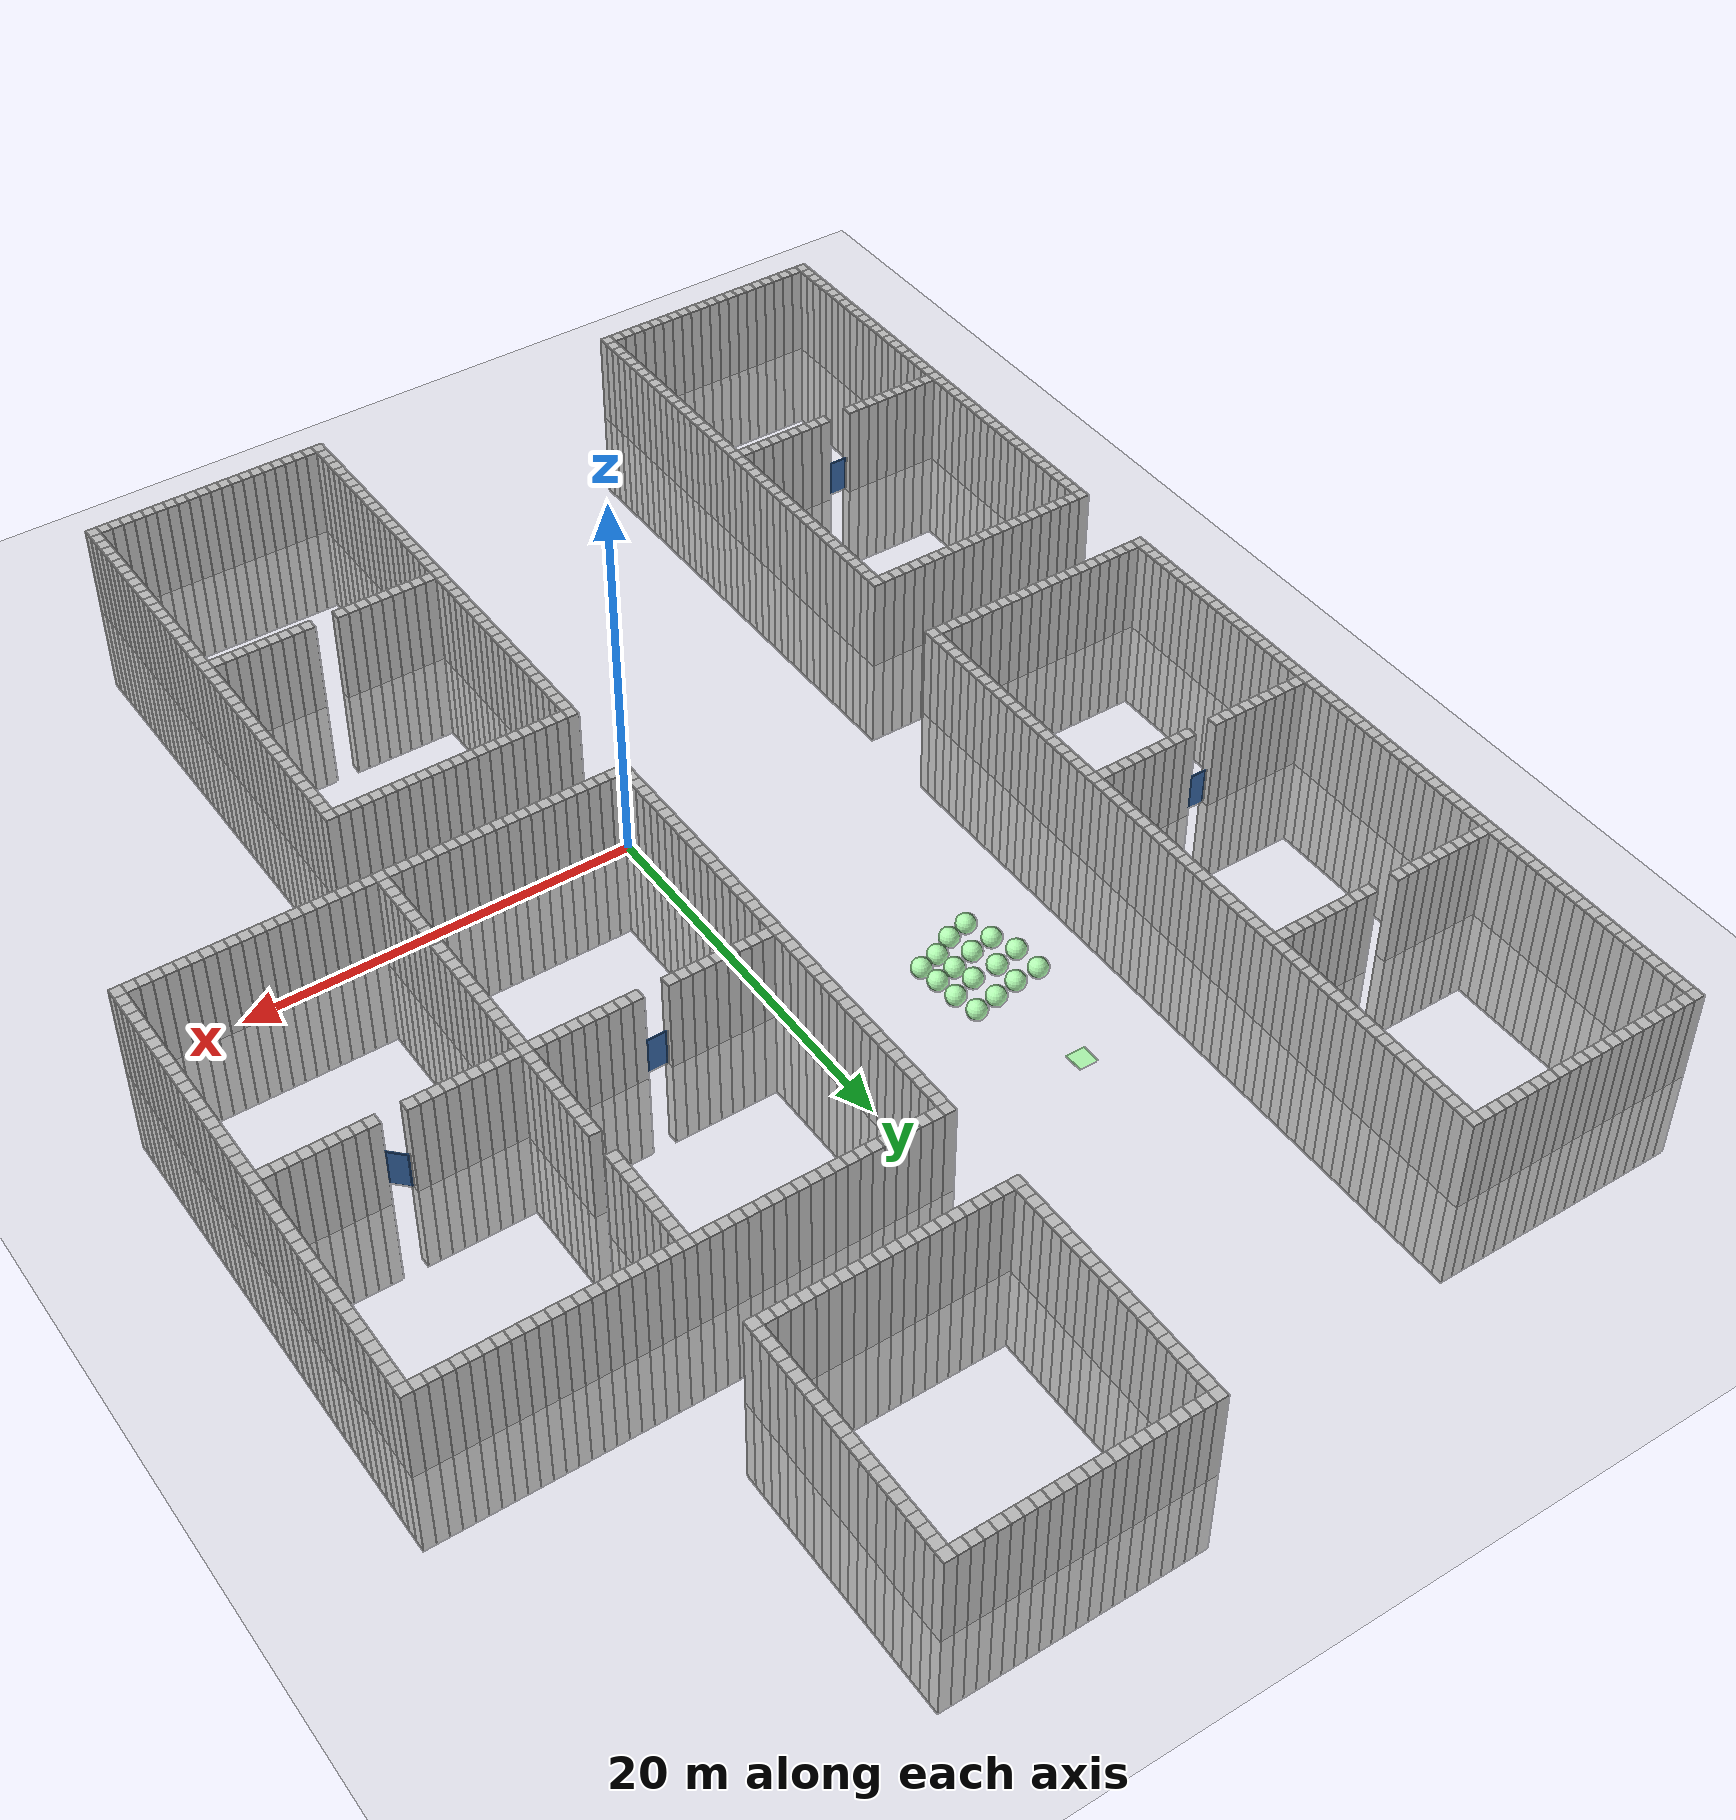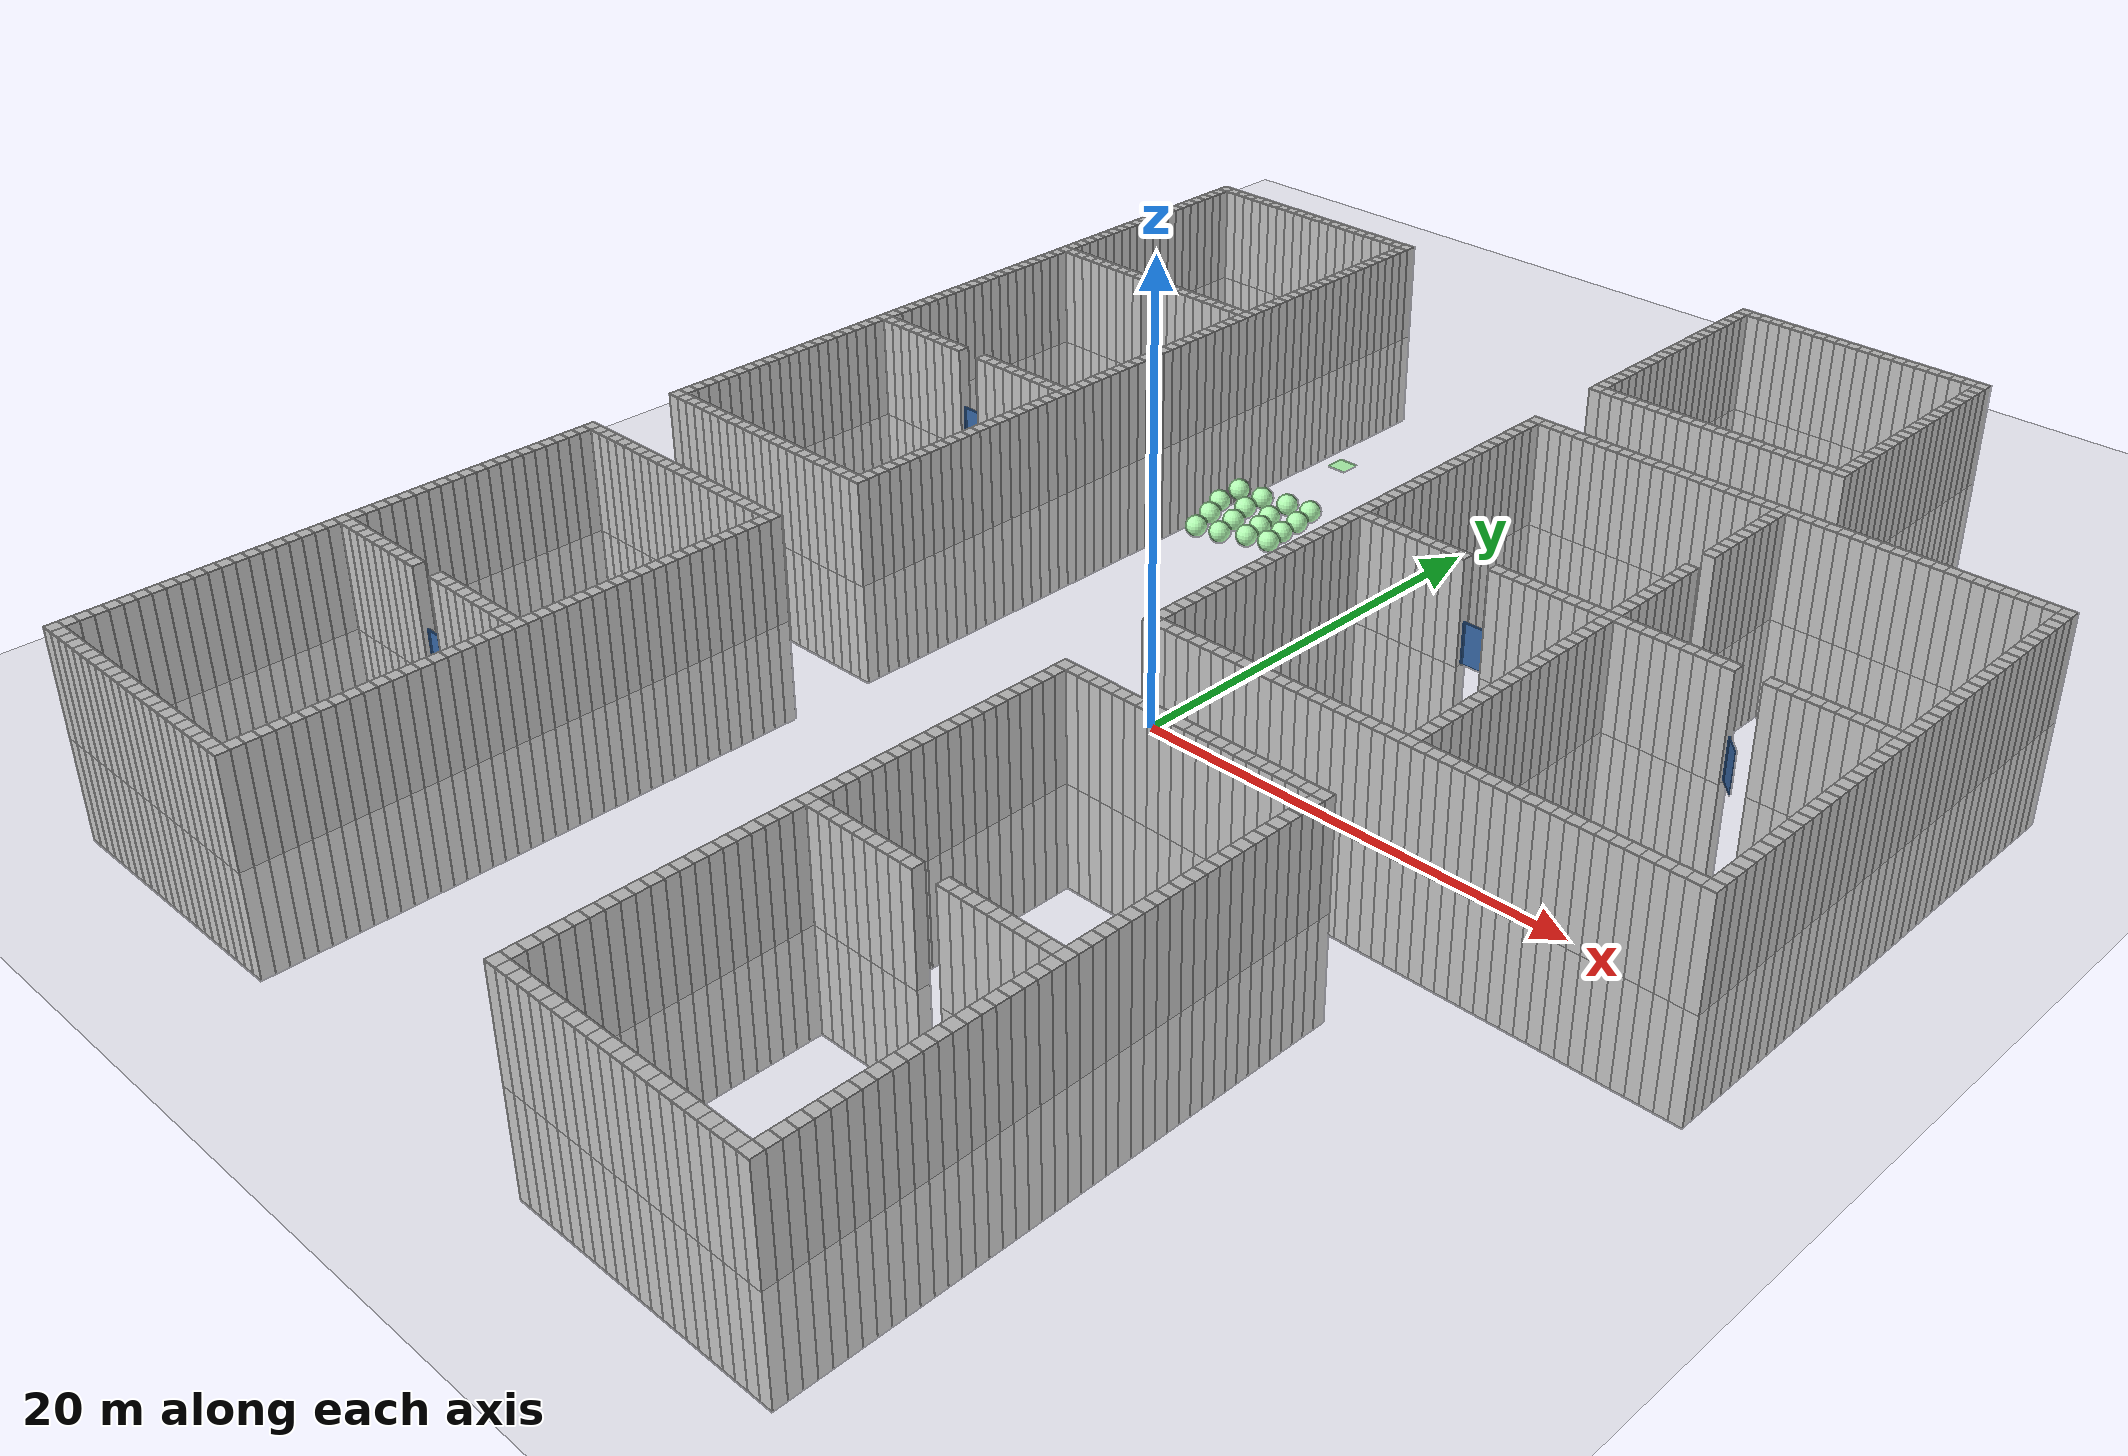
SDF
<sdf version="1.6">
 <world name="default">
  <light name="sun" type="directional">
   <pose>0 0 10 0 -0 0</pose>
   <diffuse>0.8 0.8 0.8 1</diffuse>
   <specular>0.1 0.1 0.1 1</specular>
   <attenuation>
    <range>1000</range>
    <constant>0.9</constant>
    <linear>0.01</linear>
    <quadratic>0.001</quadratic>
   </attenuation>
   <direction>-0.5 0.5 -1</direction>
  </light>
  <model name="ground_plane">
   <static>1</static>
   <link name="link">
    <collision name="collision">
     <geometry><plane><normal>0 0 1</normal><size>100 100</size></plane></geometry>
     <surface><friction><ode><mu>100</mu><mu2>50</mu2></ode></friction></surface>
    </collision>
    <visual name="visual">
     <cast_shadows>0</cast_shadows>
     <geometry><plane><normal>0 0 1</normal><size>100 100</size></plane></geometry>
     <material>
      <script><uri>file://media/materials/scripts/gazebo.material</uri><name>Gazebo/Grey</name></script>
     </material>
    </visual>
   </link>
  </model>
  <gravity>0 0 -9.8</gravity>
  <magnetic_field>6e-06 2.3e-05 -4.2e-05</magnetic_field>
  <atmosphere type="adiabatic"/>
  <physics name="default_physics" default="0" type="ode">
   <max_step_size>0.001</max_step_size>
   <real_time_factor>1</real_time_factor>
   <real_time_update_rate>1000</real_time_update_rate>
  </physics>
  <scene><ambient>0.4 0.4 0.4 1</ambient><background>0.7 0.7 0.7 1</background><shadows>1</shadows></scene>
  <spherical_coordinates>
   <surface_model>EARTH_WGS84</surface_model>
   <latitude_deg>0</latitude_deg>
   <longitude_deg>0</longitude_deg>
   <elevation>0</elevation>
   <heading_deg>0</heading_deg>
  </spherical_coordinates>
  <model name="unit_cylinder_0">
   <static>1</static>
   <link name="link">
    <inertial>
     <mass>1</mass>
     <inertia><ixx>0.145833</ixx><ixy>0</ixy><ixz>0</ixz><iyy>0.145833</iyy><iyz>0</iyz><izz>0.125</izz></inertia>
    </inertial>
    <collision name="collision"><geometry><box><size>0.6 0.6 10</size></box></geometry></collision>
    <visual name="visual">
     <geometry><box><size>0.6 0.6 10</size></box></geometry>
     <material><ambient>0.753 0.753 0.753 1</ambient><diffuse>0.753 0.753 0.753 1</diffuse></material>
     <material>
      <script><name>Gazebo/Grey</name><uri>file://media/materials/scripts/gazebo.material</uri></script>
     </material>
    </visual>
   </link>
  </model>
  <model name="unit_cylinder_1">
   <static>1</static>
   <pose>0 0.6 0 0 -0 0</pose>
   <link name="link">
    <inertial>
     <mass>1</mass>
     <inertia><ixx>0.145833</ixx><ixy>0</ixy><ixz>0</ixz><iyy>0.145833</iyy><iyz>0</iyz><izz>0.125</izz></inertia>
    </inertial>
    <collision name="collision"><geometry><box><size>0.6 0.6 10</size></box></geometry></collision>
    <visual name="visual">
     <geometry><box><size>0.6 0.6 10</size></box></geometry>
     <material><ambient>0.753 0.753 0.753 1</ambient><diffuse>0.753 0.753 0.753 1</diffuse></material>
     <material>
      <script><name>Gazebo/Grey</name><uri>file://media/materials/scripts/gazebo.material</uri></script>
     </material>
    </visual>
   </link>
  </model>
  <model name="unit_cylinder_2">
   <static>1</static>
   <pose>0 1.2 0 0 -0 0</pose>
   <link name="link">
    <inertial>
     <mass>1</mass>
     <inertia><ixx>0.145833</ixx><ixy>0</ixy><ixz>0</ixz><iyy>0.145833</iyy><iyz>0</iyz><izz>0.125</izz></inertia>
    </inertial>
    <collision name="collision"><geometry><box><size>0.6 0.6 10</size></box></geometry></collision>
    <visual name="visual">
     <geometry><box><size>0.6 0.6 10</size></box></geometry>
     <material><ambient>0.753 0.753 0.753 1</ambient><diffuse>0.753 0.753 0.753 1</diffuse></material>
     <material>
      <script><name>Gazebo/Grey</name><uri>file://media/materials/scripts/gazebo.material</uri></script>
     </material>
    </visual>
   </link>
  </model>
  <model name="unit_cylinder_3">
   <static>1</static>
   <pose>0 1.8 0 0 -0 0</pose>
   <link name="link">
    <inertial>
     <mass>1</mass>
     <inertia><ixx>0.145833</ixx><ixy>0</ixy><ixz>0</ixz><iyy>0.145833</iyy><iyz>0</iyz><izz>0.125</izz></inertia>
    </inertial>
    <collision name="collision"><geometry><box><size>0.6 0.6 10</size></box></geometry></collision>
    <visual name="visual">
     <geometry><box><size>0.6 0.6 10</size></box></geometry>
     <material><ambient>0.753 0.753 0.753 1</ambient><diffuse>0.753 0.753 0.753 1</diffuse></material>
     <material>
      <script><name>Gazebo/Grey</name><uri>file://media/materials/scripts/gazebo.material</uri></script>
     </material>
    </visual>
   </link>
  </model>
  <model name="unit_cylinder_4">
   <static>1</static>
   <pose>0 2.4 0 0 -0 0</pose>
   <link name="link">
    <inertial>
     <mass>1</mass>
     <inertia><ixx>0.145833</ixx><ixy>0</ixy><ixz>0</ixz><iyy>0.145833</iyy><iyz>0</iyz><izz>0.125</izz></inertia>
    </inertial>
    <collision name="collision"><geometry><box><size>0.6 0.6 10</size></box></geometry></collision>
    <visual name="visual">
     <geometry><box><size>0.6 0.6 10</size></box></geometry>
     <material><ambient>0.753 0.753 0.753 1</ambient><diffuse>0.753 0.753 0.753 1</diffuse></material>
     <material>
      <script><name>Gazebo/Grey</name><uri>file://media/materials/scripts/gazebo.material</uri></script>
     </material>
    </visual>
   </link>
  </model>
  <model name="unit_cylinder_5">
   <static>1</static>
   <pose>0 3 0 0 -0 0</pose>
   <link name="link">
    <inertial>
     <mass>1</mass>
     <inertia><ixx>0.145833</ixx><ixy>0</ixy><ixz>0</ixz><iyy>0.145833</iyy><iyz>0</iyz><izz>0.125</izz></inertia>
    </inertial>
    <collision name="collision"><geometry><box><size>0.6 0.6 10</size></box></geometry></collision>
    <visual name="visual">
     <geometry><box><size>0.6 0.6 10</size></box></geometry>
     <material><ambient>0.753 0.753 0.753 1</ambient><diffuse>0.753 0.753 0.753 1</diffuse></material>
     <material>
      <script><name>Gazebo/Grey</name><uri>file://media/materials/scripts/gazebo.material</uri></script>
     </material>
    </visual>
   </link>
  </model>
  <model name="unit_cylinder_6">
   <static>1</static>
   <pose>0 3.6 0 0 -0 0</pose>
   <link name="link">
    <inertial>
     <mass>1</mass>
     <inertia><ixx>0.145833</ixx><ixy>0</ixy><ixz>0</ixz><iyy>0.145833</iyy><iyz>0</iyz><izz>0.125</izz></inertia>
    </inertial>
    <collision name="collision"><geometry><box><size>0.6 0.6 10</size></box></geometry></collision>
    <visual name="visual">
     <geometry><box><size>0.6 0.6 10</size></box></geometry>
     <material><ambient>0.753 0.753 0.753 1</ambient><diffuse>0.753 0.753 0.753 1</diffuse></material>
     <material>
      <script><name>Gazebo/Grey</name><uri>file://media/materials/scripts/gazebo.material</uri></script>
     </material>
    </visual>
   </link>
  </model>
  <model name="unit_cylinder_7">
   <static>1</static>
   <pose>0 4.2 0 0 -0 0</pose>
   <link name="link">
    <inertial>
     <mass>1</mass>
     <inertia><ixx>0.145833</ixx><ixy>0</ixy><ixz>0</ixz><iyy>0.145833</iyy><iyz>0</iyz><izz>0.125</izz></inertia>
    </inertial>
    <collision name="collision"><geometry><box><size>0.6 0.6 10</size></box></geometry></collision>
    <visual name="visual">
     <geometry><box><size>0.6 0.6 10</size></box></geometry>
     <material><ambient>0.753 0.753 0.753 1</ambient><diffuse>0.753 0.753 0.753 1</diffuse></material>
     <material>
      <script><name>Gazebo/Grey</name><uri>file://media/materials/scripts/gazebo.material</uri></script>
     </material>
    </visual>
   </link>
  </model>
  <model name="unit_cylinder_8">
   <static>1</static>
   <pose>0 4.8 0 0 -0 0</pose>
   <link name="link">
    <inertial>
     <mass>1</mass>
     <inertia><ixx>0.145833</ixx><ixy>0</ixy><ixz>0</ixz><iyy>0.145833</iyy><iyz>0</iyz><izz>0.125</izz></inertia>
    </inertial>
    <collision name="collision"><geometry><box><size>0.6 0.6 10</size></box></geometry></collision>
    <visual name="visual">
     <geometry><box><size>0.6 0.6 10</size></box></geometry>
     <material><ambient>0.753 0.753 0.753 1</ambient><diffuse>0.753 0.753 0.753 1</diffuse></material>
     <material>
      <script><name>Gazebo/Grey</name><uri>file://media/materials/scripts/gazebo.material</uri></script>
     </material>
    </visual>
   </link>
  </model>
  <model name="unit_cylinder_9">
   <static>1</static>
   <pose>0 5.4 0 0 -0 0</pose>
   <link name="link">
    <inertial>
     <mass>1</mass>
     <inertia><ixx>0.145833</ixx><ixy>0</ixy><ixz>0</ixz><iyy>0.145833</iyy><iyz>0</iyz><izz>0.125</izz></inertia>
    </inertial>
    <collision name="collision"><geometry><box><size>0.6 0.6 10</size></box></geometry></collision>
    <visual name="visual">
     <geometry><box><size>0.6 0.6 10</size></box></geometry>
     <material><ambient>0.753 0.753 0.753 1</ambient><diffuse>0.753 0.753 0.753 1</diffuse></material>
     <material>
      <script><name>Gazebo/Grey</name><uri>file://media/materials/scripts/gazebo.material</uri></script>
     </material>
    </visual>
   </link>
  </model>
  <model name="unit_cylinder_10">
   <static>1</static>
   <pose>0 6 0 0 -0 0</pose>
   <link name="link">
    <inertial>
     <mass>1</mass>
     <inertia><ixx>0.145833</ixx><ixy>0</ixy><ixz>0</ixz><iyy>0.145833</iyy><iyz>0</iyz><izz>0.125</izz></inertia>
    </inertial>
    <collision name="collision"><geometry><box><size>0.6 0.6 10</size></box></geometry></collision>
    <visual name="visual">
     <geometry><box><size>0.6 0.6 10</size></box></geometry>
     <material><ambient>0.753 0.753 0.753 1</ambient><diffuse>0.753 0.753 0.753 1</diffuse></material>
     <material>
      <script><name>Gazebo/Grey</name><uri>file://media/materials/scripts/gazebo.material</uri></script>
     </material>
    </visual>
   </link>
  </model>
  <model name="unit_cylinder_11">
   <static>1</static>
   <pose>0 6.6 0 0 -0 0</pose>
   <link name="link">
    <inertial>
     <mass>1</mass>
     <inertia><ixx>0.145833</ixx><ixy>0</ixy><ixz>0</ixz><iyy>0.145833</iyy><iyz>0</iyz><izz>0.125</izz></inertia>
    </inertial>
    <collision name="collision"><geometry><box><size>0.6 0.6 10</size></box></geometry></collision>
    <visual name="visual">
     <geometry><box><size>0.6 0.6 10</size></box></geometry>
     <material><ambient>0.753 0.753 0.753 1</ambient><diffuse>0.753 0.753 0.753 1</diffuse></material>
     <material>
      <script><name>Gazebo/Grey</name><uri>file://media/materials/scripts/gazebo.material</uri></script>
     </material>
    </visual>
   </link>
  </model>
  <model name="unit_cylinder_12">
   <static>1</static>
   <pose>0 7.2 0 0 -0 0</pose>
   <link name="link">
    <inertial>
     <mass>1</mass>
     <inertia><ixx>0.145833</ixx><ixy>0</ixy><ixz>0</ixz><iyy>0.145833</iyy><iyz>0</iyz><izz>0.125</izz></inertia>
    </inertial>
    <collision name="collision"><geometry><box><size>0.6 0.6 10</size></box></geometry></collision>
    <visual name="visual">
     <geometry><box><size>0.6 0.6 10</size></box></geometry>
     <material><ambient>0.753 0.753 0.753 1</ambient><diffuse>0.753 0.753 0.753 1</diffuse></material>
     <material>
      <script><name>Gazebo/Grey</name><uri>file://media/materials/scripts/gazebo.material</uri></script>
     </material>
    </visual>
   </link>
  </model>
  <model name="unit_cylinder_13">
   <static>1</static>
   <pose>0 7.8 0 0 -0 0</pose>
   <link name="link">
    <inertial>
     <mass>1</mass>
     <inertia><ixx>0.145833</ixx><ixy>0</ixy><ixz>0</ixz><iyy>0.145833</iyy><iyz>0</iyz><izz>0.125</izz></inertia>
    </inertial>
    <collision name="collision"><geometry><box><size>0.6 0.6 10</size></box></geometry></collision>
    <visual name="visual">
     <geometry><box><size>0.6 0.6 10</size></box></geometry>
     <material><ambient>0.753 0.753 0.753 1</ambient><diffuse>0.753 0.753 0.753 1</diffuse></material>
     <material>
      <script><name>Gazebo/Grey</name><uri>file://media/materials/scripts/gazebo.material</uri></script>
     </material>
    </visual>
   </link>
  </model>
  <model name="unit_cylinder_14">
   <static>1</static>
   <pose>0 8.4 0 0 -0 0</pose>
   <link name="link">
    <inertial>
     <mass>1</mass>
     <inertia><ixx>0.145833</ixx><ixy>0</ixy><ixz>0</ixz><iyy>0.145833</iyy><iyz>0</iyz><izz>0.125</izz></inertia>
    </inertial>
    <collision name="collision"><geometry><box><size>0.6 0.6 10</size></box></geometry></collision>
    <visual name="visual">
     <geometry><box><size>0.6 0.6 10</size></box></geometry>
     <material><ambient>0.753 0.753 0.753 1</ambient><diffuse>0.753 0.753 0.753 1</diffuse></material>
     <material>
      <script><name>Gazebo/Grey</name><uri>file://media/materials/scripts/gazebo.material</uri></script>
     </material>
    </visual>
   </link>
  </model>
  <model name="unit_cylinder_15">
   <static>1</static>
   <pose>0 9 0 0 -0 0</pose>
   <link name="link">
    <inertial>
     <mass>1</mass>
     <inertia><ixx>0.145833</ixx><ixy>0</ixy><ixz>0</ixz><iyy>0.145833</iyy><iyz>0</iyz><izz>0.125</izz></inertia>
    </inertial>
    <collision name="collision"><geometry><box><size>0.6 0.6 10</size></box></geometry></collision>
    <visual name="visual">
     <geometry><box><size>0.6 0.6 10</size></box></geometry>
     <material><ambient>0.753 0.753 0.753 1</ambient><diffuse>0.753 0.753 0.753 1</diffuse></material>
     <material>
      <script><name>Gazebo/Grey</name><uri>file://media/materials/scripts/gazebo.material</uri></script>
     </material>
    </visual>
   </link>
  </model>
  <model name="unit_cylinder_16">
   <static>1</static>
   <pose>0 9.6 0 0 -0 0</pose>
   <link name="link">
    <inertial>
     <mass>1</mass>
     <inertia><ixx>0.145833</ixx><ixy>0</ixy><ixz>0</ixz><iyy>0.145833</iyy><iyz>0</iyz><izz>0.125</izz></inertia>
    </inertial>
    <collision name="collision"><geometry><box><size>0.6 0.6 10</size></box></geometry></collision>
    <visual name="visual">
     <geometry><box><size>0.6 0.6 10</size></box></geometry>
     <material><ambient>0.753 0.753 0.753 1</ambient><diffuse>0.753 0.753 0.753 1</diffuse></material>
     <material>
      <script><name>Gazebo/Grey</name><uri>file://media/materials/scripts/gazebo.material</uri></script>
     </material>
    </visual>
   </link>
  </model>
  <model name="unit_cylinder_17">
   <static>1</static>
   <pose>0 10.2 0 0 -0 0</pose>
   <link name="link">
    <inertial>
     <mass>1</mass>
     <inertia><ixx>0.145833</ixx><ixy>0</ixy><ixz>0</ixz><iyy>0.145833</iyy><iyz>0</iyz><izz>0.125</izz></inertia>
    </inertial>
    <collision name="collision"><geometry><box><size>0.6 0.6 10</size></box></geometry></collision>
    <visual name="visual">
     <geometry><box><size>0.6 0.6 10</size></box></geometry>
     <material><ambient>0.753 0.753 0.753 1</ambient><diffuse>0.753 0.753 0.753 1</diffuse></material>
     <material>
      <script><name>Gazebo/Grey</name><uri>file://media/materials/scripts/gazebo.material</uri></script>
     </material>
    </visual>
   </link>
  </model>
  <model name="unit_cylinder_18">
   <static>1</static>
   <pose>0 10.8 0 0 -0 0</pose>
   <link name="link">
    <inertial>
     <mass>1</mass>
     <inertia><ixx>0.145833</ixx><ixy>0</ixy><ixz>0</ixz><iyy>0.145833</iyy><iyz>0</iyz><izz>0.125</izz></inertia>
    </inertial>
    <collision name="collision"><geometry><box><size>0.6 0.6 10</size></box></geometry></collision>
    <visual name="visual">
     <geometry><box><size>0.6 0.6 10</size></box></geometry>
     <material><ambient>0.753 0.753 0.753 1</ambient><diffuse>0.753 0.753 0.753 1</diffuse></material>
     <material>
      <script><name>Gazebo/Grey</name><uri>file://media/materials/scripts/gazebo.material</uri></script>
     </material>
    </visual>
   </link>
  </model>
  <model name="unit_cylinder_19">
   <static>1</static>
   <pose>0 11.4 0 0 -0 0</pose>
   <link name="link">
    <inertial>
     <mass>1</mass>
     <inertia><ixx>0.145833</ixx><ixy>0</ixy><ixz>0</ixz><iyy>0.145833</iyy><iyz>0</iyz><izz>0.125</izz></inertia>
    </inertial>
    <collision name="collision"><geometry><box><size>0.6 0.6 10</size></box></geometry></collision>
    <visual name="visual">
     <geometry><box><size>0.6 0.6 10</size></box></geometry>
     <material><ambient>0.753 0.753 0.753 1</ambient><diffuse>0.753 0.753 0.753 1</diffuse></material>
     <material>
      <script><name>Gazebo/Grey</name><uri>file://media/materials/scripts/gazebo.material</uri></script>
     </material>
    </visual>
   </link>
  </model>
  <model name="unit_cylinder_20">
   <static>1</static>
   <pose>0 12 0 0 -0 0</pose>
   <link name="link">
    <inertial>
     <mass>1</mass>
     <inertia><ixx>0.145833</ixx><ixy>0</ixy><ixz>0</ixz><iyy>0.145833</iyy><iyz>0</iyz><izz>0.125</izz></inertia>
    </inertial>
    <collision name="collision"><geometry><box><size>0.6 0.6 10</size></box></geometry></collision>
    <visual name="visual">
     <geometry><box><size>0.6 0.6 10</size></box></geometry>
     <material><ambient>0.753 0.753 0.753 1</ambient><diffuse>0.753 0.753 0.753 1</diffuse></material>
     <material>
      <script><name>Gazebo/Grey</name><uri>file://media/materials/scripts/gazebo.material</uri></script>
     </material>
    </visual>
   </link>
  </model>
  <model name="unit_cylinder_21">
   <static>1</static>
   <pose>0 12.6 0 0 -0 0</pose>
   <link name="link">
    <inertial>
     <mass>1</mass>
     <inertia><ixx>0.145833</ixx><ixy>0</ixy><ixz>0</ixz><iyy>0.145833</iyy><iyz>0</iyz><izz>0.125</izz></inertia>
    </inertial>
    <collision name="collision"><geometry><box><size>0.6 0.6 10</size></box></geometry></collision>
    <visual name="visual">
     <geometry><box><size>0.6 0.6 10</size></box></geometry>
     <material><ambient>0.753 0.753 0.753 1</ambient><diffuse>0.753 0.753 0.753 1</diffuse></material>
     <material>
      <script><name>Gazebo/Grey</name><uri>file://media/materials/scripts/gazebo.material</uri></script>
     </material>
    </visual>
   </link>
  </model>
  <model name="unit_cylinder_22">
   <static>1</static>
   <pose>0 13.2 0 0 -0 0</pose>
   <link name="link">
    <inertial>
     <mass>1</mass>
     <inertia><ixx>0.145833</ixx><ixy>0</ixy><ixz>0</ixz><iyy>0.145833</iyy><iyz>0</iyz><izz>0.125</izz></inertia>
    </inertial>
    <collision name="collision"><geometry><box><size>0.6 0.6 10</size></box></geometry></collision>
    <visual name="visual">
     <geometry><box><size>0.6 0.6 10</size></box></geometry>
     <material><ambient>0.753 0.753 0.753 1</ambient><diffuse>0.753 0.753 0.753 1</diffuse></material>
     <material>
      <script><name>Gazebo/Grey</name><uri>file://media/materials/scripts/gazebo.material</uri></script>
     </material>
    </visual>
   </link>
  </model>
  <model name="unit_cylinder_23">
   <static>1</static>
   <pose>0 13.8 0 0 -0 0</pose>
   <link name="link">
    <inertial>
     <mass>1</mass>
     <inertia><ixx>0.145833</ixx><ixy>0</ixy><ixz>0</ixz><iyy>0.145833</iyy><iyz>0</iyz><izz>0.125</izz></inertia>
    </inertial>
    <collision name="collision"><geometry><box><size>0.6 0.6 10</size></box></geometry></collision>
    <visual name="visual">
     <geometry><box><size>0.6 0.6 10</size></box></geometry>
     <material><ambient>0.753 0.753 0.753 1</ambient><diffuse>0.753 0.753 0.753 1</diffuse></material>
     <material>
      <script><name>Gazebo/Grey</name><uri>file://media/materials/scripts/gazebo.material</uri></script>
     </material>
    </visual>
   </link>
  </model>
  <model name="unit_cylinder_24">
   <static>1</static>
   <pose>0 14.4 0 0 -0 0</pose>
   <link name="link">
    <inertial>
     <mass>1</mass>
     <inertia><ixx>0.145833</ixx><ixy>0</ixy><ixz>0</ixz><iyy>0.145833</iyy><iyz>0</iyz><izz>0.125</izz></inertia>
    </inertial>
    <collision name="collision"><geometry><box><size>0.6 0.6 10</size></box></geometry></collision>
    <visual name="visual">
     <geometry><box><size>0.6 0.6 10</size></box></geometry>
     <material><ambient>0.753 0.753 0.753 1</ambient><diffuse>0.753 0.753 0.753 1</diffuse></material>
     <material>
      <script><name>Gazebo/Grey</name><uri>file://media/materials/scripts/gazebo.material</uri></script>
     </material>
    </visual>
   </link>
  </model>
  <model name="unit_cylinder_25">
   <static>1</static>
   <pose>0 15 0 0 -0 0</pose>
   <link name="link">
    <inertial>
     <mass>1</mass>
     <inertia><ixx>0.145833</ixx><ixy>0</ixy><ixz>0</ixz><iyy>0.145833</iyy><iyz>0</iyz><izz>0.125</izz></inertia>
    </inertial>
    <collision name="collision"><geometry><box><size>0.6 0.6 10</size></box></geometry></collision>
    <visual name="visual">
     <geometry><box><size>0.6 0.6 10</size></box></geometry>
     <material><ambient>0.753 0.753 0.753 1</ambient><diffuse>0.753 0.753 0.753 1</diffuse></material>
     <material>
      <script><name>Gazebo/Grey</name><uri>file://media/materials/scripts/gazebo.material</uri></script>
     </material>
    </visual>
   </link>
  </model>
  <model name="unit_cylinder_26">
   <static>1</static>
   <pose>0 15.6 0 0 -0 0</pose>
   <link name="link">
    <inertial>
     <mass>1</mass>
     <inertia><ixx>0.145833</ixx><ixy>0</ixy><ixz>0</ixz><iyy>0.145833</iyy><iyz>0</iyz><izz>0.125</izz></inertia>
    </inertial>
    <collision name="collision"><geometry><box><size>0.6 0.6 10</size></box></geometry></collision>
    <visual name="visual">
     <geometry><box><size>0.6 0.6 10</size></box></geometry>
     <material><ambient>0.753 0.753 0.753 1</ambient><diffuse>0.753 0.753 0.753 1</diffuse></material>
     <material>
      <script><name>Gazebo/Grey</name><uri>file://media/materials/scripts/gazebo.material</uri></script>
     </material>
    </visual>
   </link>
  </model>
  <model name="unit_cylinder_27">
   <static>1</static>
   <pose>0 16.2 0 0 -0 0</pose>
   <link name="link">
    <inertial>
     <mass>1</mass>
     <inertia><ixx>0.145833</ixx><ixy>0</ixy><ixz>0</ixz><iyy>0.145833</iyy><iyz>0</iyz><izz>0.125</izz></inertia>
    </inertial>
    <collision name="collision"><geometry><box><size>0.6 0.6 10</size></box></geometry></collision>
    <visual name="visual">
     <geometry><box><size>0.6 0.6 10</size></box></geometry>
     <material><ambient>0.753 0.753 0.753 1</ambient><diffuse>0.753 0.753 0.753 1</diffuse></material>
     <material>
      <script><name>Gazebo/Grey</name><uri>file://media/materials/scripts/gazebo.material</uri></script>
     </material>
    </visual>
   </link>
  </model>
  <model name="unit_cylinder_28">
   <static>1</static>
   <pose>0 16.8 0 0 -0 0</pose>
   <link name="link">
    <inertial>
     <mass>1</mass>
     <inertia><ixx>0.145833</ixx><ixy>0</ixy><ixz>0</ixz><iyy>0.145833</iyy><iyz>0</iyz><izz>0.125</izz></inertia>
    </inertial>
    <collision name="collision"><geometry><box><size>0.6 0.6 10</size></box></geometry></collision>
    <visual name="visual">
     <geometry><box><size>0.6 0.6 10</size></box></geometry>
     <material><ambient>0.753 0.753 0.753 1</ambient><diffuse>0.753 0.753 0.753 1</diffuse></material>
     <material>
      <script><name>Gazebo/Grey</name><uri>file://media/materials/scripts/gazebo.material</uri></script>
     </material>
    </visual>
   </link>
  </model>
  <model name="unit_cylinder_29">
   <static>1</static>
   <pose>0 17.4 0 0 -0 0</pose>
   <link name="link">
    <inertial>
     <mass>1</mass>
     <inertia><ixx>0.145833</ixx><ixy>0</ixy><ixz>0</ixz><iyy>0.145833</iyy><iyz>0</iyz><izz>0.125</izz></inertia>
    </inertial>
    <collision name="collision"><geometry><box><size>0.6 0.6 10</size></box></geometry></collision>
    <visual name="visual">
     <geometry><box><size>0.6 0.6 10</size></box></geometry>
     <material><ambient>0.753 0.753 0.753 1</ambient><diffuse>0.753 0.753 0.753 1</diffuse></material>
     <material>
      <script><name>Gazebo/Grey</name><uri>file://media/materials/scripts/gazebo.material</uri></script>
     </material>
    </visual>
   </link>
  </model>
  <model name="unit_cylinder_30">
   <static>1</static>
   <pose>0 18 0 0 -0 0</pose>
   <link name="link">
    <inertial>
     <mass>1</mass>
     <inertia><ixx>0.145833</ixx><ixy>0</ixy><ixz>0</ixz><iyy>0.145833</iyy><iyz>0</iyz><izz>0.125</izz></inertia>
    </inertial>
    <collision name="collision"><geometry><box><size>0.6 0.6 10</size></box></geometry></collision>
    <visual name="visual">
     <geometry><box><size>0.6 0.6 10</size></box></geometry>
     <material><ambient>0.753 0.753 0.753 1</ambient><diffuse>0.753 0.753 0.753 1</diffuse></material>
     <material>
      <script><name>Gazebo/Grey</name><uri>file://media/materials/scripts/gazebo.material</uri></script>
     </material>
    </visual>
   </link>
  </model>
  <model name="unit_cylinder_31">
   <static>1</static>
   <pose>0 18.6 0 0 -0 0</pose>
   <link name="link">
    <inertial>
     <mass>1</mass>
     <inertia><ixx>0.145833</ixx><ixy>0</ixy><ixz>0</ixz><iyy>0.145833</iyy><iyz>0</iyz><izz>0.125</izz></inertia>
    </inertial>
    <collision name="collision"><geometry><box><size>0.6 0.6 10</size></box></geometry></collision>
    <visual name="visual">
     <geometry><box><size>0.6 0.6 10</size></box></geometry>
     <material><ambient>0.753 0.753 0.753 1</ambient><diffuse>0.753 0.753 0.753 1</diffuse></material>
     <material>
      <script><name>Gazebo/Grey</name><uri>file://media/materials/scripts/gazebo.material</uri></script>
     </material>
    </visual>
   </link>
  </model>
  <model name="unit_cylinder_32">
   <static>1</static>
   <pose>0 19.2 0 0 -0 0</pose>
   <link name="link">
    <inertial>
     <mass>1</mass>
     <inertia><ixx>0.145833</ixx><ixy>0</ixy><ixz>0</ixz><iyy>0.145833</iyy><iyz>0</iyz><izz>0.125</izz></inertia>
    </inertial>
    <collision name="collision"><geometry><box><size>0.6 0.6 10</size></box></geometry></collision>
    <visual name="visual">
     <geometry><box><size>0.6 0.6 10</size></box></geometry>
     <material><ambient>0.753 0.753 0.753 1</ambient><diffuse>0.753 0.753 0.753 1</diffuse></material>
     <material>
      <script><name>Gazebo/Grey</name><uri>file://media/materials/scripts/gazebo.material</uri></script>
     </material>
    </visual>
   </link>
  </model>
  <model name="unit_cylinder_33">
   <static>1</static>
   <pose>0 19.8 0 0 -0 0</pose>
   <link name="link">
    <inertial>
     <mass>1</mass>
     <inertia><ixx>0.145833</ixx><ixy>0</ixy><ixz>0</ixz><iyy>0.145833</iyy><iyz>0</iyz><izz>0.125</izz></inertia>
    </inertial>
    <collision name="collision"><geometry><box><size>0.6 0.6 10</size></box></geometry></collision>
    <visual name="visual">
     <geometry><box><size>0.6 0.6 10</size></box></geometry>
     <material><ambient>0.753 0.753 0.753 1</ambient><diffuse>0.753 0.753 0.753 1</diffuse></material>
     <material>
      <script><name>Gazebo/Grey</name><uri>file://media/materials/scripts/gazebo.material</uri></script>
     </material>
    </visual>
   </link>
  </model>
  <model name="unit_cylinder_34">
   <static>1</static>
   <pose>0 20.4 0 0 -0 0</pose>
   <link name="link">
    <inertial>
     <mass>1</mass>
     <inertia><ixx>0.145833</ixx><ixy>0</ixy><ixz>0</ixz><iyy>0.145833</iyy><iyz>0</iyz><izz>0.125</izz></inertia>
    </inertial>
    <collision name="collision"><geometry><box><size>0.6 0.6 10</size></box></geometry></collision>
    <visual name="visual">
     <geometry><box><size>0.6 0.6 10</size></box></geometry>
     <material><ambient>0.753 0.753 0.753 1</ambient><diffuse>0.753 0.753 0.753 1</diffuse></material>
     <material>
      <script><name>Gazebo/Grey</name><uri>file://media/materials/scripts/gazebo.material</uri></script>
     </material>
    </visual>
   </link>
  </model>
  <model name="unit_cylinder_35">
   <static>1</static>
   <pose>0 21 0 0 -0 0</pose>
   <link name="link">
    <inertial>
     <mass>1</mass>
     <inertia><ixx>0.145833</ixx><ixy>0</ixy><ixz>0</ixz><iyy>0.145833</iyy><iyz>0</iyz><izz>0.125</izz></inertia>
    </inertial>
    <collision name="collision"><geometry><box><size>0.6 0.6 10</size></box></geometry></collision>
    <visual name="visual">
     <geometry><box><size>0.6 0.6 10</size></box></geometry>
     <material><ambient>0.753 0.753 0.753 1</ambient><diffuse>0.753 0.753 0.753 1</diffuse></material>
     <material>
      <script><name>Gazebo/Grey</name><uri>file://media/materials/scripts/gazebo.material</uri></script>
     </material>
    </visual>
   </link>
  </model>
  <model name="unit_cylinder_36">
   <static>1</static>
   <pose>0 21.6 0 0 -0 0</pose>
   <link name="link">
    <inertial>
     <mass>1</mass>
     <inertia><ixx>0.145833</ixx><ixy>0</ixy><ixz>0</ixz><iyy>0.145833</iyy><iyz>0</iyz><izz>0.125</izz></inertia>
    </inertial>
    <collision name="collision"><geometry><box><size>0.6 0.6 10</size></box></geometry></collision>
    <visual name="visual">
     <geometry><box><size>0.6 0.6 10</size></box></geometry>
     <material><ambient>0.753 0.753 0.753 1</ambient><diffuse>0.753 0.753 0.753 1</diffuse></material>
     <material>
      <script><name>Gazebo/Grey</name><uri>file://media/materials/scripts/gazebo.material</uri></script>
     </material>
    </visual>
   </link>
  </model>
  <model name="unit_cylinder_37">
   <static>1</static>
   <pose>0 22.2 0 0 -0 0</pose>
   <link name="link">
    <inertial>
     <mass>1</mass>
     <inertia><ixx>0.145833</ixx><ixy>0</ixy><ixz>0</ixz><iyy>0.145833</iyy><iyz>0</iyz><izz>0.125</izz></inertia>
    </inertial>
    <collision name="collision"><geometry><box><size>0.6 0.6 10</size></box></geometry></collision>
    <visual name="visual">
     <geometry><box><size>0.6 0.6 10</size></box></geometry>
     <material><ambient>0.753 0.753 0.753 1</ambient><diffuse>0.753 0.753 0.753 1</diffuse></material>
     <material>
      <script><name>Gazebo/Grey</name><uri>file://media/materials/scripts/gazebo.material</uri></script>
     </material>
    </visual>
   </link>
  </model>
  <model name="unit_cylinder_38">
   <static>1</static>
   <pose>0 22.8 0 0 -0 0</pose>
   <link name="link">
    <inertial>
     <mass>1</mass>
     <inertia><ixx>0.145833</ixx><ixy>0</ixy><ixz>0</ixz><iyy>0.145833</iyy><iyz>0</iyz><izz>0.125</izz></inertia>
    </inertial>
    <collision name="collision"><geometry><box><size>0.6 0.6 10</size></box></geometry></collision>
    <visual name="visual">
     <geometry><box><size>0.6 0.6 10</size></box></geometry>
     <material><ambient>0.753 0.753 0.753 1</ambient><diffuse>0.753 0.753 0.753 1</diffuse></material>
     <material>
      <script><name>Gazebo/Grey</name><uri>file://media/materials/scripts/gazebo.material</uri></script>
     </material>
    </visual>
   </link>
  </model>
  <model name="unit_cylinder_39">
   <static>1</static>
   <pose>0 23.4 0 0 -0 0</pose>
   <link name="link">
    <inertial>
     <mass>1</mass>
     <inertia><ixx>0.145833</ixx><ixy>0</ixy><ixz>0</ixz><iyy>0.145833</iyy><iyz>0</iyz><izz>0.125</izz></inertia>
    </inertial>
    <collision name="collision"><geometry><box><size>0.6 0.6 10</size></box></geometry></collision>
    <visual name="visual">
     <geometry><box><size>0.6 0.6 10</size></box></geometry>
     <material><ambient>0.753 0.753 0.753 1</ambient><diffuse>0.753 0.753 0.753 1</diffuse></material>
     <material>
      <script><name>Gazebo/Grey</name><uri>file://media/materials/scripts/gazebo.material</uri></script>
     </material>
    </visual>
   </link>
  </model>
  <model name="unit_cylinder_40">
   <static>1</static>
   <pose>0 24 0 0 -0 0</pose>
   <link name="link">
    <inertial>
     <mass>1</mass>
     <inertia><ixx>0.145833</ixx><ixy>0</ixy><ixz>0</ixz><iyy>0.145833</iyy><iyz>0</iyz><izz>0.125</izz></inertia>
    </inertial>
    <collision name="collision"><geometry><box><size>0.6 0.6 10</size></box></geometry></collision>
    <visual name="visual">
     <geometry><box><size>0.6 0.6 10</size></box></geometry>
     <material><ambient>0.753 0.753 0.753 1</ambient><diffuse>0.753 0.753 0.753 1</diffuse></material>
     <material>
      <script><name>Gazebo/Grey</name><uri>file://media/materials/scripts/gazebo.material</uri></script>
     </material>
    </visual>
   </link>
  </model>
  <model name="unit_cylinder_41">
   <static>1</static>
   <pose>0 24.6 0 0 -0 0</pose>
   <link name="link">
    <inertial>
     <mass>1</mass>
     <inertia><ixx>0.145833</ixx><ixy>0</ixy><ixz>0</ixz><iyy>0.145833</iyy><iyz>0</iyz><izz>0.125</izz></inertia>
    </inertial>
    <collision name="collision"><geometry><box><size>0.6 0.6 10</size></box></geometry></collision>
    <visual name="visual">
     <geometry><box><size>0.6 0.6 10</size></box></geometry>
     <material><ambient>0.753 0.753 0.753 1</ambient><diffuse>0.753 0.753 0.753 1</diffuse></material>
     <material>
      <script><name>Gazebo/Grey</name><uri>file://media/materials/scripts/gazebo.material</uri></script>
     </material>
    </visual>
   </link>
  </model>
  <model name="unit_cylinder_42">
   <static>1</static>
   <pose>0 25.2 0 0 -0 0</pose>
   <link name="link">
    <inertial>
     <mass>1</mass>
     <inertia><ixx>0.145833</ixx><ixy>0</ixy><ixz>0</ixz><iyy>0.145833</iyy><iyz>0</iyz><izz>0.125</izz></inertia>
    </inertial>
    <collision name="collision"><geometry><box><size>0.6 0.6 10</size></box></geometry></collision>
    <visual name="visual">
     <geometry><box><size>0.6 0.6 10</size></box></geometry>
     <material><ambient>0.753 0.753 0.753 1</ambient><diffuse>0.753 0.753 0.753 1</diffuse></material>
     <material>
      <script><name>Gazebo/Grey</name><uri>file://media/materials/scripts/gazebo.material</uri></script>
     </material>
    </visual>
   </link>
  </model>
  <model name="unit_cylinder_43">
   <static>1</static>
   <pose>0.6 0 0 0 -0 0</pose>
   <link name="link">
    <inertial>
     <mass>1</mass>
     <inertia><ixx>0.145833</ixx><ixy>0</ixy><ixz>0</ixz><iyy>0.145833</iyy><iyz>0</iyz><izz>0.125</izz></inertia>
    </inertial>
    <collision name="collision"><geometry><box><size>0.6 0.6 10</size></box></geometry></collision>
    <visual name="visual">
     <geometry><box><size>0.6 0.6 10</size></box></geometry>
     <material><ambient>0.753 0.753 0.753 1</ambient><diffuse>0.753 0.753 0.753 1</diffuse></material>
     <material>
      <script><name>Gazebo/Grey</name><uri>file://media/materials/scripts/gazebo.material</uri></script>
     </material>
    </visual>
   </link>
  </model>
  <model name="unit_cylinder_44">
   <static>1</static>
   <pose>0.6 12.6 0 0 -0 0</pose>
   <link name="link">
    <inertial>
     <mass>1</mass>
     <inertia><ixx>0.145833</ixx><ixy>0</ixy><ixz>0</ixz><iyy>0.145833</iyy><iyz>0</iyz><izz>0.125</izz></inertia>
    </inertial>
    <collision name="collision"><geometry><box><size>0.6 0.6 10</size></box></geometry></collision>
    <visual name="visual">
     <geometry><box><size>0.6 0.6 10</size></box></geometry>
     <material><ambient>0.753 0.753 0.753 1</ambient><diffuse>0.753 0.753 0.753 1</diffuse></material>
     <material>
      <script><name>Gazebo/Grey</name><uri>file://media/materials/scripts/gazebo.material</uri></script>
     </material>
    </visual>
   </link>
  </model>
  <model name="unit_cylinder_45">
   <static>1</static>
   <pose>0.6 25.2 0 0 -0 0</pose>
   <link name="link">
    <inertial>
     <mass>1</mass>
     <inertia><ixx>0.145833</ixx><ixy>0</ixy><ixz>0</ixz><iyy>0.145833</iyy><iyz>0</iyz><izz>0.125</izz></inertia>
    </inertial>
    <collision name="collision"><geometry><box><size>0.6 0.6 10</size></box></geometry></collision>
    <visual name="visual">
     <geometry><box><size>0.6 0.6 10</size></box></geometry>
     <material><ambient>0.753 0.753 0.753 1</ambient><diffuse>0.753 0.753 0.753 1</diffuse></material>
     <material>
      <script><name>Gazebo/Grey</name><uri>file://media/materials/scripts/gazebo.material</uri></script>
     </material>
    </visual>
   </link>
  </model>
  <model name="unit_cylinder_46">
   <static>1</static>
   <pose>1.2 0 0 0 -0 0</pose>
   <link name="link">
    <inertial>
     <mass>1</mass>
     <inertia><ixx>0.145833</ixx><ixy>0</ixy><ixz>0</ixz><iyy>0.145833</iyy><iyz>0</iyz><izz>0.125</izz></inertia>
    </inertial>
    <collision name="collision"><geometry><box><size>0.6 0.6 10</size></box></geometry></collision>
    <visual name="visual">
     <geometry><box><size>0.6 0.6 10</size></box></geometry>
     <material><ambient>0.753 0.753 0.753 1</ambient><diffuse>0.753 0.753 0.753 1</diffuse></material>
     <material>
      <script><name>Gazebo/Grey</name><uri>file://media/materials/scripts/gazebo.material</uri></script>
     </material>
    </visual>
   </link>
  </model>
  <model name="unit_cylinder_47">
   <static>1</static>
   <pose>1.2 12.6 0 0 -0 0</pose>
   <link name="link">
    <inertial>
     <mass>1</mass>
     <inertia><ixx>0.145833</ixx><ixy>0</ixy><ixz>0</ixz><iyy>0.145833</iyy><iyz>0</iyz><izz>0.125</izz></inertia>
    </inertial>
    <collision name="collision"><geometry><box><size>0.6 0.6 10</size></box></geometry></collision>
    <visual name="visual">
     <geometry><box><size>0.6 0.6 10</size></box></geometry>
     <material><ambient>0.753 0.753 0.753 1</ambient><diffuse>0.753 0.753 0.753 1</diffuse></material>
     <material>
      <script><name>Gazebo/Grey</name><uri>file://media/materials/scripts/gazebo.material</uri></script>
     </material>
    </visual>
   </link>
  </model>
  <model name="unit_cylinder_48">
   <static>1</static>
   <pose>1.2 25.2 0 0 -0 0</pose>
   <link name="link">
    <inertial>
     <mass>1</mass>
     <inertia><ixx>0.145833</ixx><ixy>0</ixy><ixz>0</ixz><iyy>0.145833</iyy><iyz>0</iyz><izz>0.125</izz></inertia>
    </inertial>
    <collision name="collision"><geometry><box><size>0.6 0.6 10</size></box></geometry></collision>
    <visual name="visual">
     <geometry><box><size>0.6 0.6 10</size></box></geometry>
     <material><ambient>0.753 0.753 0.753 1</ambient><diffuse>0.753 0.753 0.753 1</diffuse></material>
     <material>
      <script><name>Gazebo/Grey</name><uri>file://media/materials/scripts/gazebo.material</uri></script>
     </material>
    </visual>
   </link>
  </model>
  <model name="unit_cylinder_49">
   <static>1</static>
   <pose>1.8 0 0 0 -0 0</pose>
   <link name="link">
    <inertial>
     <mass>1</mass>
     <inertia><ixx>0.145833</ixx><ixy>0</ixy><ixz>0</ixz><iyy>0.145833</iyy><iyz>0</iyz><izz>0.125</izz></inertia>
    </inertial>
    <collision name="collision"><geometry><box><size>0.6 0.6 10</size></box></geometry></collision>
    <visual name="visual">
     <geometry><box><size>0.6 0.6 10</size></box></geometry>
     <material><ambient>0.753 0.753 0.753 1</ambient><diffuse>0.753 0.753 0.753 1</diffuse></material>
     <material>
      <script><name>Gazebo/Grey</name><uri>file://media/materials/scripts/gazebo.material</uri></script>
     </material>
    </visual>
   </link>
  </model>
  <model name="unit_cylinder_50">
   <static>1</static>
   <pose>1.8 12.6 0 0 -0 0</pose>
   <link name="link">
    <inertial>
     <mass>1</mass>
     <inertia><ixx>0.145833</ixx><ixy>0</ixy><ixz>0</ixz><iyy>0.145833</iyy><iyz>0</iyz><izz>0.125</izz></inertia>
    </inertial>
    <collision name="collision"><geometry><box><size>0.6 0.6 10</size></box></geometry></collision>
    <visual name="visual">
     <geometry><box><size>0.6 0.6 10</size></box></geometry>
     <material><ambient>0.753 0.753 0.753 1</ambient><diffuse>0.753 0.753 0.753 1</diffuse></material>
     <material>
      <script><name>Gazebo/Grey</name><uri>file://media/materials/scripts/gazebo.material</uri></script>
     </material>
    </visual>
   </link>
  </model>
  <model name="unit_cylinder_51">
   <static>1</static>
   <pose>1.8 25.2 0 0 -0 0</pose>
   <link name="link">
    <inertial>
     <mass>1</mass>
     <inertia><ixx>0.145833</ixx><ixy>0</ixy><ixz>0</ixz><iyy>0.145833</iyy><iyz>0</iyz><izz>0.125</izz></inertia>
    </inertial>
    <collision name="collision"><geometry><box><size>0.6 0.6 10</size></box></geometry></collision>
    <visual name="visual">
     <geometry><box><size>0.6 0.6 10</size></box></geometry>
     <material><ambient>0.753 0.753 0.753 1</ambient><diffuse>0.753 0.753 0.753 1</diffuse></material>
     <material>
      <script><name>Gazebo/Grey</name><uri>file://media/materials/scripts/gazebo.material</uri></script>
     </material>
    </visual>
   </link>
  </model>
  <model name="unit_cylinder_52">
   <static>1</static>
   <pose>2.4 0 0 0 -0 0</pose>
   <link name="link">
    <inertial>
     <mass>1</mass>
     <inertia><ixx>0.145833</ixx><ixy>0</ixy><ixz>0</ixz><iyy>0.145833</iyy><iyz>0</iyz><izz>0.125</izz></inertia>
    </inertial>
    <collision name="collision"><geometry><box><size>0.6 0.6 10</size></box></geometry></collision>
    <visual name="visual">
     <geometry><box><size>0.6 0.6 10</size></box></geometry>
     <material><ambient>0.753 0.753 0.753 1</ambient><diffuse>0.753 0.753 0.753 1</diffuse></material>
     <material>
      <script><name>Gazebo/Grey</name><uri>file://media/materials/scripts/gazebo.material</uri></script>
     </material>
    </visual>
   </link>
  </model>
  <model name="unit_cylinder_53">
   <static>1</static>
   <pose>2.4 12.6 0 0 -0 0</pose>
   <link name="link">
    <inertial>
     <mass>1</mass>
     <inertia><ixx>0.145833</ixx><ixy>0</ixy><ixz>0</ixz><iyy>0.145833</iyy><iyz>0</iyz><izz>0.125</izz></inertia>
    </inertial>
    <collision name="collision"><geometry><box><size>0.6 0.6 10</size></box></geometry></collision>
    <visual name="visual">
     <geometry><box><size>0.6 0.6 10</size></box></geometry>
     <material><ambient>0.753 0.753 0.753 1</ambient><diffuse>0.753 0.753 0.753 1</diffuse></material>
     <material>
      <script><name>Gazebo/Grey</name><uri>file://media/materials/scripts/gazebo.material</uri></script>
     </material>
    </visual>
   </link>
  </model>
  <model name="unit_cylinder_54">
   <static>1</static>
   <pose>2.4 25.2 0 0 -0 0</pose>
   <link name="link">
    <inertial>
     <mass>1</mass>
     <inertia><ixx>0.145833</ixx><ixy>0</ixy><ixz>0</ixz><iyy>0.145833</iyy><iyz>0</iyz><izz>0.125</izz></inertia>
    </inertial>
    <collision name="collision"><geometry><box><size>0.6 0.6 10</size></box></geometry></collision>
    <visual name="visual">
     <geometry><box><size>0.6 0.6 10</size></box></geometry>
     <material><ambient>0.753 0.753 0.753 1</ambient><diffuse>0.753 0.753 0.753 1</diffuse></material>
     <material>
      <script><name>Gazebo/Grey</name><uri>file://media/materials/scripts/gazebo.material</uri></script>
     </material>
    </visual>
   </link>
  </model>
  <model name="unit_cylinder_55">
   <static>1</static>
   <pose>3 0 0 0 -0 0</pose>
   <link name="link">
    <inertial>
     <mass>1</mass>
     <inertia><ixx>0.145833</ixx><ixy>0</ixy><ixz>0</ixz><iyy>0.145833</iyy><iyz>0</iyz><izz>0.125</izz></inertia>
    </inertial>
    <collision name="collision"><geometry><box><size>0.6 0.6 10</size></box></geometry></collision>
    <visual name="visual">
     <geometry><box><size>0.6 0.6 10</size></box></geometry>
     <material><ambient>0.753 0.753 0.753 1</ambient><diffuse>0.753 0.753 0.753 1</diffuse></material>
     <material>
      <script><name>Gazebo/Grey</name><uri>file://media/materials/scripts/gazebo.material</uri></script>
     </material>
    </visual>
   </link>
  </model>
  <model name="unit_cylinder_56">
   <static>1</static>
   <pose>3 12.6 0 0 -0 0</pose>
   <link name="link">
    <inertial>
     <mass>1</mass>
     <inertia><ixx>0.145833</ixx><ixy>0</ixy><ixz>0</ixz><iyy>0.145833</iyy><iyz>0</iyz><izz>0.125</izz></inertia>
    </inertial>
    <collision name="collision"><geometry><box><size>0.6 0.6 10</size></box></geometry></collision>
    <visual name="visual">
     <geometry><box><size>0.6 0.6 10</size></box></geometry>
     <material><ambient>0.753 0.753 0.753 1</ambient><diffuse>0.753 0.753 0.753 1</diffuse></material>
     <material>
      <script><name>Gazebo/Grey</name><uri>file://media/materials/scripts/gazebo.material</uri></script>
     </material>
    </visual>
   </link>
  </model>
  <model name="unit_cylinder_57">
   <static>1</static>
   <pose>3 25.2 0 0 -0 0</pose>
   <link name="link">
    <inertial>
     <mass>1</mass>
     <inertia><ixx>0.145833</ixx><ixy>0</ixy><ixz>0</ixz><iyy>0.145833</iyy><iyz>0</iyz><izz>0.125</izz></inertia>
    </inertial>
    <collision name="collision"><geometry><box><size>0.6 0.6 10</size></box></geometry></collision>
    <visual name="visual">
     <geometry><box><size>0.6 0.6 10</size></box></geometry>
     <material><ambient>0.753 0.753 0.753 1</ambient><diffuse>0.753 0.753 0.753 1</diffuse></material>
     <material>
      <script><name>Gazebo/Grey</name><uri>file://media/materials/scripts/gazebo.material</uri></script>
     </material>
    </visual>
   </link>
  </model>
  <model name="unit_cylinder_58">
   <static>1</static>
   <pose>3.6 0 0 0 -0 0</pose>
   <link name="link">
    <inertial>
     <mass>1</mass>
     <inertia><ixx>0.145833</ixx><ixy>0</ixy><ixz>0</ixz><iyy>0.145833</iyy><iyz>0</iyz><izz>0.125</izz></inertia>
    </inertial>
    <collision name="collision"><geometry><box><size>0.6 0.6 10</size></box></geometry></collision>
    <visual name="visual">
     <geometry><box><size>0.6 0.6 10</size></box></geometry>
     <material><ambient>0.753 0.753 0.753 1</ambient><diffuse>0.753 0.753 0.753 1</diffuse></material>
     <material>
      <script><name>Gazebo/Grey</name><uri>file://media/materials/scripts/gazebo.material</uri></script>
     </material>
    </visual>
   </link>
  </model>
  <model name="unit_cylinder_59">
   <static>1</static>
   <pose>3.6 12.6 0 0 -0 0</pose>
   <link name="link">
    <inertial>
     <mass>1</mass>
     <inertia><ixx>0.145833</ixx><ixy>0</ixy><ixz>0</ixz><iyy>0.145833</iyy><iyz>0</iyz><izz>0.125</izz></inertia>
    </inertial>
    <collision name="collision"><geometry><box><size>0.6 0.6 10</size></box></geometry></collision>
    <visual name="visual">
     <geometry><box><size>0.6 0.6 10</size></box></geometry>
     <material><ambient>0.753 0.753 0.753 1</ambient><diffuse>0.753 0.753 0.753 1</diffuse></material>
     <material>
      <script><name>Gazebo/Grey</name><uri>file://media/materials/scripts/gazebo.material</uri></script>
     </material>
    </visual>
   </link>
  </model>
  <model name="unit_cylinder_60">
   <static>1</static>
   <pose>3.6 25.2 0 0 -0 0</pose>
   <link name="link">
    <inertial>
     <mass>1</mass>
     <inertia><ixx>0.145833</ixx><ixy>0</ixy><ixz>0</ixz><iyy>0.145833</iyy><iyz>0</iyz><izz>0.125</izz></inertia>
    </inertial>
    <collision name="collision"><geometry><box><size>0.6 0.6 10</size></box></geometry></collision>
    <visual name="visual">
     <geometry><box><size>0.6 0.6 10</size></box></geometry>
     <material><ambient>0.753 0.753 0.753 1</ambient><diffuse>0.753 0.753 0.753 1</diffuse></material>
     <material>
      <script><name>Gazebo/Grey</name><uri>file://media/materials/scripts/gazebo.material</uri></script>
     </material>
    </visual>
   </link>
  </model>
  <model name="unit_cylinder_61">
   <static>1</static>
   <pose>4.2 0 0 0 -0 0</pose>
   <link name="link">
    <inertial>
     <mass>1</mass>
     <inertia><ixx>0.145833</ixx><ixy>0</ixy><ixz>0</ixz><iyy>0.145833</iyy><iyz>0</iyz><izz>0.125</izz></inertia>
    </inertial>
    <collision name="collision"><geometry><box><size>0.6 0.6 10</size></box></geometry></collision>
    <visual name="visual">
     <geometry><box><size>0.6 0.6 10</size></box></geometry>
     <material><ambient>0.753 0.753 0.753 1</ambient><diffuse>0.753 0.753 0.753 1</diffuse></material>
     <material>
      <script><name>Gazebo/Grey</name><uri>file://media/materials/scripts/gazebo.material</uri></script>
     </material>
    </visual>
   </link>
  </model>
  <model name="unit_cylinder_62">
   <static>1</static>
   <pose>4.2 12.6 0 0 -0 0</pose>
   <link name="link">
    <inertial>
     <mass>1</mass>
     <inertia><ixx>0.145833</ixx><ixy>0</ixy><ixz>0</ixz><iyy>0.145833</iyy><iyz>0</iyz><izz>0.125</izz></inertia>
    </inertial>
    <collision name="collision"><geometry><box><size>0.6 0.6 10</size></box></geometry></collision>
    <visual name="visual">
     <geometry><box><size>0.6 0.6 10</size></box></geometry>
     <material><ambient>0.753 0.753 0.753 1</ambient><diffuse>0.753 0.753 0.753 1</diffuse></material>
     <material>
      <script><name>Gazebo/Grey</name><uri>file://media/materials/scripts/gazebo.material</uri></script>
     </material>
    </visual>
   </link>
  </model>
  <model name="unit_cylinder_63">
   <static>1</static>
   <pose>4.2 25.2 0 0 -0 0</pose>
   <link name="link">
    <inertial>
     <mass>1</mass>
     <inertia><ixx>0.145833</ixx><ixy>0</ixy><ixz>0</ixz><iyy>0.145833</iyy><iyz>0</iyz><izz>0.125</izz></inertia>
    </inertial>
    <collision name="collision"><geometry><box><size>0.6 0.6 10</size></box></geometry></collision>
    <visual name="visual">
     <geometry><box><size>0.6 0.6 10</size></box></geometry>
     <material><ambient>0.753 0.753 0.753 1</ambient><diffuse>0.753 0.753 0.753 1</diffuse></material>
     <material>
      <script><name>Gazebo/Grey</name><uri>file://media/materials/scripts/gazebo.material</uri></script>
     </material>
    </visual>
   </link>
  </model>
  <model name="unit_cylinder_64">
   <static>1</static>
   <pose>4.8 0 0 0 -0 0</pose>
   <link name="link">
    <inertial>
     <mass>1</mass>
     <inertia><ixx>0.145833</ixx><ixy>0</ixy><ixz>0</ixz><iyy>0.145833</iyy><iyz>0</iyz><izz>0.125</izz></inertia>
    </inertial>
    <collision name="collision"><geometry><box><size>0.6 0.6 10</size></box></geometry></collision>
    <visual name="visual">
     <geometry><box><size>0.6 0.6 10</size></box></geometry>
     <material><ambient>0.753 0.753 0.753 1</ambient><diffuse>0.753 0.753 0.753 1</diffuse></material>
     <material>
      <script><name>Gazebo/Grey</name><uri>file://media/materials/scripts/gazebo.material</uri></script>
     </material>
    </visual>
   </link>
  </model>
  <model name="unit_cylinder_65">
   <static>1</static>
   <pose>4.8 12.6 0 0 -0 0</pose>
   <link name="link">
    <inertial>
     <mass>1</mass>
     <inertia><ixx>0.145833</ixx><ixy>0</ixy><ixz>0</ixz><iyy>0.145833</iyy><iyz>0</iyz><izz>0.125</izz></inertia>
    </inertial>
    <collision name="collision"><geometry><box><size>0.6 0.6 10</size></box></geometry></collision>
    <visual name="visual">
     <geometry><box><size>0.6 0.6 10</size></box></geometry>
     <material><ambient>0.753 0.753 0.753 1</ambient><diffuse>0.753 0.753 0.753 1</diffuse></material>
     <material>
      <script><name>Gazebo/Grey</name><uri>file://media/materials/scripts/gazebo.material</uri></script>
     </material>
    </visual>
   </link>
  </model>
  <model name="unit_cylinder_66">
   <static>1</static>
   <pose>4.8 25.2 0 0 -0 0</pose>
   <link name="link">
    <inertial>
     <mass>1</mass>
     <inertia><ixx>0.145833</ixx><ixy>0</ixy><ixz>0</ixz><iyy>0.145833</iyy><iyz>0</iyz><izz>0.125</izz></inertia>
    </inertial>
    <collision name="collision"><geometry><box><size>0.6 0.6 10</size></box></geometry></collision>
    <visual name="visual">
     <geometry><box><size>0.6 0.6 10</size></box></geometry>
     <material><ambient>0.753 0.753 0.753 1</ambient><diffuse>0.753 0.753 0.753 1</diffuse></material>
     <material>
      <script><name>Gazebo/Grey</name><uri>file://media/materials/scripts/gazebo.material</uri></script>
     </material>
    </visual>
   </link>
  </model>
  <model name="unit_cylinder_67">
   <static>1</static>
   <pose>5.4 0 0 0 -0 0</pose>
   <link name="link">
    <inertial>
     <mass>1</mass>
     <inertia><ixx>0.145833</ixx><ixy>0</ixy><ixz>0</ixz><iyy>0.145833</iyy><iyz>0</iyz><izz>0.125</izz></inertia>
    </inertial>
    <collision name="collision"><geometry><box><size>0.6 0.6 10</size></box></geometry></collision>
    <visual name="visual">
     <geometry><box><size>0.6 0.6 10</size></box></geometry>
     <material><ambient>0.753 0.753 0.753 1</ambient><diffuse>0.753 0.753 0.753 1</diffuse></material>
     <material>
      <script><name>Gazebo/Grey</name><uri>file://media/materials/scripts/gazebo.material</uri></script>
     </material>
    </visual>
   </link>
  </model>
  <model name="unit_cylinder_68">
   <static>1</static>
   <pose>5.4 12.6 0 0 -0 0</pose>
   <link name="link">
    <inertial>
     <mass>1</mass>
     <inertia><ixx>0.145833</ixx><ixy>0</ixy><ixz>0</ixz><iyy>0.145833</iyy><iyz>0</iyz><izz>0.125</izz></inertia>
    </inertial>
    <collision name="collision"><geometry><box><size>0.6 0.6 10</size></box></geometry></collision>
    <visual name="visual">
     <geometry><box><size>0.6 0.6 10</size></box></geometry>
     <material><ambient>0.753 0.753 0.753 1</ambient><diffuse>0.753 0.753 0.753 1</diffuse></material>
     <material>
      <script><name>Gazebo/Grey</name><uri>file://media/materials/scripts/gazebo.material</uri></script>
     </material>
    </visual>
   </link>
  </model>
  <model name="unit_cylinder_69">
   <static>1</static>
   <pose>5.4 25.2 0 0 -0 0</pose>
   <link name="link">
    <inertial>
     <mass>1</mass>
     <inertia><ixx>0.145833</ixx><ixy>0</ixy><ixz>0</ixz><iyy>0.145833</iyy><iyz>0</iyz><izz>0.125</izz></inertia>
    </inertial>
    <collision name="collision"><geometry><box><size>0.6 0.6 10</size></box></geometry></collision>
    <visual name="visual">
     <geometry><box><size>0.6 0.6 10</size></box></geometry>
     <material><ambient>0.753 0.753 0.753 1</ambient><diffuse>0.753 0.753 0.753 1</diffuse></material>
     <material>
      <script><name>Gazebo/Grey</name><uri>file://media/materials/scripts/gazebo.material</uri></script>
     </material>
    </visual>
   </link>
  </model>
  <model name="unit_cylinder_70">
   <static>1</static>
   <pose>6 0 0 0 -0 0</pose>
   <link name="link">
    <inertial>
     <mass>1</mass>
     <inertia><ixx>0.145833</ixx><ixy>0</ixy><ixz>0</ixz><iyy>0.145833</iyy><iyz>0</iyz><izz>0.125</izz></inertia>
    </inertial>
    <collision name="collision"><geometry><box><size>0.6 0.6 10</size></box></geometry></collision>
    <visual name="visual">
     <geometry><box><size>0.6 0.6 10</size></box></geometry>
     <material><ambient>0.753 0.753 0.753 1</ambient><diffuse>0.753 0.753 0.753 1</diffuse></material>
     <material>
      <script><name>Gazebo/Grey</name><uri>file://media/materials/scripts/gazebo.material</uri></script>
     </material>
    </visual>
   </link>
  </model>
  <model name="unit_cylinder_72">
   <static>1</static>
   <pose>6 25.2 0 0 -0 0</pose>
   <link name="link">
    <inertial>
     <mass>1</mass>
     <inertia><ixx>0.145833</ixx><ixy>0</ixy><ixz>0</ixz><iyy>0.145833</iyy><iyz>0</iyz><izz>0.125</izz></inertia>
    </inertial>
    <collision name="collision"><geometry><box><size>0.6 0.6 10</size></box></geometry></collision>
    <visual name="visual">
     <geometry><box><size>0.6 0.6 10</size></box></geometry>
     <material><ambient>0.753 0.753 0.753 1</ambient><diffuse>0.753 0.753 0.753 1</diffuse></material>
     <material>
      <script><name>Gazebo/Grey</name><uri>file://media/materials/scripts/gazebo.material</uri></script>
     </material>
    </visual>
   </link>
  </model>
  <model name="unit_cylinder_73">
   <static>1</static>
   <pose>6.6 0 0 0 -0 0</pose>
   <link name="link">
    <inertial>
     <mass>1</mass>
     <inertia><ixx>0.145833</ixx><ixy>0</ixy><ixz>0</ixz><iyy>0.145833</iyy><iyz>0</iyz><izz>0.125</izz></inertia>
    </inertial>
    <collision name="collision"><geometry><box><size>0.6 0.6 10</size></box></geometry></collision>
    <visual name="visual">
     <geometry><box><size>0.6 0.6 10</size></box></geometry>
     <material><ambient>0.753 0.753 0.753 1</ambient><diffuse>0.753 0.753 0.753 1</diffuse></material>
     <material>
      <script><name>Gazebo/Grey</name><uri>file://media/materials/scripts/gazebo.material</uri></script>
     </material>
    </visual>
   </link>
  </model>
  <model name="unit_cylinder_75">
   <static>1</static>
   <pose>6.6 25.2 0 0 -0 0</pose>
   <link name="link">
    <inertial>
     <mass>1</mass>
     <inertia><ixx>0.145833</ixx><ixy>0</ixy><ixz>0</ixz><iyy>0.145833</iyy><iyz>0</iyz><izz>0.125</izz></inertia>
    </inertial>
    <collision name="collision"><geometry><box><size>0.6 0.6 10</size></box></geometry></collision>
    <visual name="visual">
     <geometry><box><size>0.6 0.6 10</size></box></geometry>
     <material><ambient>0.753 0.753 0.753 1</ambient><diffuse>0.753 0.753 0.753 1</diffuse></material>
     <material>
      <script><name>Gazebo/Grey</name><uri>file://media/materials/scripts/gazebo.material</uri></script>
     </material>
    </visual>
   </link>
  </model>
  <model name="unit_cylinder_76">
   <static>1</static>
   <pose>7.2 0 0 0 -0 0</pose>
   <link name="link">
    <inertial>
     <mass>1</mass>
     <inertia><ixx>0.145833</ixx><ixy>0</ixy><ixz>0</ixz><iyy>0.145833</iyy><iyz>0</iyz><izz>0.125</izz></inertia>
    </inertial>
    <collision name="collision"><geometry><box><size>0.6 0.6 10</size></box></geometry></collision>
    <visual name="visual">
     <geometry><box><size>0.6 0.6 10</size></box></geometry>
     <material><ambient>0.753 0.753 0.753 1</ambient><diffuse>0.753 0.753 0.753 1</diffuse></material>
     <material>
      <script><name>Gazebo/Grey</name><uri>file://media/materials/scripts/gazebo.material</uri></script>
     </material>
    </visual>
   </link>
  </model>
  <model name="unit_cylinder_77">
   <static>1</static>
   <pose>7.2 12.6 0 0 -0 0</pose>
   <link name="link">
    <inertial>
     <mass>1</mass>
     <inertia><ixx>0.145833</ixx><ixy>0</ixy><ixz>0</ixz><iyy>0.145833</iyy><iyz>0</iyz><izz>0.125</izz></inertia>
    </inertial>
    <collision name="collision"><geometry><box><size>0.6 0.6 10</size></box></geometry></collision>
    <visual name="visual">
     <geometry><box><size>0.6 0.6 10</size></box></geometry>
     <material><ambient>0.753 0.753 0.753 1</ambient><diffuse>0.753 0.753 0.753 1</diffuse></material>
     <material>
      <script><name>Gazebo/Grey</name><uri>file://media/materials/scripts/gazebo.material</uri></script>
     </material>
    </visual>
   </link>
  </model>
  <model name="unit_cylinder_78">
   <static>1</static>
   <pose>7.2 25.2 0 0 -0 0</pose>
   <link name="link">
    <inertial>
     <mass>1</mass>
     <inertia><ixx>0.145833</ixx><ixy>0</ixy><ixz>0</ixz><iyy>0.145833</iyy><iyz>0</iyz><izz>0.125</izz></inertia>
    </inertial>
    <collision name="collision"><geometry><box><size>0.6 0.6 10</size></box></geometry></collision>
    <visual name="visual">
     <geometry><box><size>0.6 0.6 10</size></box></geometry>
     <material><ambient>0.753 0.753 0.753 1</ambient><diffuse>0.753 0.753 0.753 1</diffuse></material>
     <material>
      <script><name>Gazebo/Grey</name><uri>file://media/materials/scripts/gazebo.material</uri></script>
     </material>
    </visual>
   </link>
  </model>
  <model name="unit_cylinder_79">
   <static>1</static>
   <pose>7.8 0 0 0 -0 0</pose>
   <link name="link">
    <inertial>
     <mass>1</mass>
     <inertia><ixx>0.145833</ixx><ixy>0</ixy><ixz>0</ixz><iyy>0.145833</iyy><iyz>0</iyz><izz>0.125</izz></inertia>
    </inertial>
    <collision name="collision"><geometry><box><size>0.6 0.6 10</size></box></geometry></collision>
    <visual name="visual">
     <geometry><box><size>0.6 0.6 10</size></box></geometry>
     <material><ambient>0.753 0.753 0.753 1</ambient><diffuse>0.753 0.753 0.753 1</diffuse></material>
     <material>
      <script><name>Gazebo/Grey</name><uri>file://media/materials/scripts/gazebo.material</uri></script>
     </material>
    </visual>
   </link>
  </model>
  <model name="unit_cylinder_80">
   <static>1</static>
   <pose>7.8 12.6 0 0 -0 0</pose>
   <link name="link">
    <inertial>
     <mass>1</mass>
     <inertia><ixx>0.145833</ixx><ixy>0</ixy><ixz>0</ixz><iyy>0.145833</iyy><iyz>0</iyz><izz>0.125</izz></inertia>
    </inertial>
    <collision name="collision"><geometry><box><size>0.6 0.6 10</size></box></geometry></collision>
    <visual name="visual">
     <geometry><box><size>0.6 0.6 10</size></box></geometry>
     <material><ambient>0.753 0.753 0.753 1</ambient><diffuse>0.753 0.753 0.753 1</diffuse></material>
     <material>
      <script><name>Gazebo/Grey</name><uri>file://media/materials/scripts/gazebo.material</uri></script>
     </material>
    </visual>
   </link>
  </model>
  <model name="unit_cylinder_81">
   <static>1</static>
   <pose>7.8 25.2 0 0 -0 0</pose>
   <link name="link">
    <inertial>
     <mass>1</mass>
     <inertia><ixx>0.145833</ixx><ixy>0</ixy><ixz>0</ixz><iyy>0.145833</iyy><iyz>0</iyz><izz>0.125</izz></inertia>
    </inertial>
    <collision name="collision"><geometry><box><size>0.6 0.6 10</size></box></geometry></collision>
    <visual name="visual">
     <geometry><box><size>0.6 0.6 10</size></box></geometry>
     <material><ambient>0.753 0.753 0.753 1</ambient><diffuse>0.753 0.753 0.753 1</diffuse></material>
     <material>
      <script><name>Gazebo/Grey</name><uri>file://media/materials/scripts/gazebo.material</uri></script>
     </material>
    </visual>
   </link>
  </model>
  <model name="unit_cylinder_82">
   <static>1</static>
   <pose>8.4 0 0 0 -0 0</pose>
   <link name="link">
    <inertial>
     <mass>1</mass>
     <inertia><ixx>0.145833</ixx><ixy>0</ixy><ixz>0</ixz><iyy>0.145833</iyy><iyz>0</iyz><izz>0.125</izz></inertia>
    </inertial>
    <collision name="collision"><geometry><box><size>0.6 0.6 10</size></box></geometry></collision>
    <visual name="visual">
     <geometry><box><size>0.6 0.6 10</size></box></geometry>
     <material><ambient>0.753 0.753 0.753 1</ambient><diffuse>0.753 0.753 0.753 1</diffuse></material>
     <material>
      <script><name>Gazebo/Grey</name><uri>file://media/materials/scripts/gazebo.material</uri></script>
     </material>
    </visual>
   </link>
  </model>
  <model name="unit_cylinder_83">
   <static>1</static>
   <pose>8.4 12.6 0 0 -0 0</pose>
   <link name="link">
    <inertial>
     <mass>1</mass>
     <inertia><ixx>0.145833</ixx><ixy>0</ixy><ixz>0</ixz><iyy>0.145833</iyy><iyz>0</iyz><izz>0.125</izz></inertia>
    </inertial>
    <collision name="collision"><geometry><box><size>0.6 0.6 10</size></box></geometry></collision>
    <visual name="visual">
     <geometry><box><size>0.6 0.6 10</size></box></geometry>
     <material><ambient>0.753 0.753 0.753 1</ambient><diffuse>0.753 0.753 0.753 1</diffuse></material>
     <material>
      <script><name>Gazebo/Grey</name><uri>file://media/materials/scripts/gazebo.material</uri></script>
     </material>
    </visual>
   </link>
  </model>
  <model name="unit_cylinder_84">
   <static>1</static>
   <pose>8.4 25.2 0 0 -0 0</pose>
   <link name="link">
    <inertial>
     <mass>1</mass>
     <inertia><ixx>0.145833</ixx><ixy>0</ixy><ixz>0</ixz><iyy>0.145833</iyy><iyz>0</iyz><izz>0.125</izz></inertia>
    </inertial>
    <collision name="collision"><geometry><box><size>0.6 0.6 10</size></box></geometry></collision>
    <visual name="visual">
     <geometry><box><size>0.6 0.6 10</size></box></geometry>
     <material><ambient>0.753 0.753 0.753 1</ambient><diffuse>0.753 0.753 0.753 1</diffuse></material>
     <material>
      <script><name>Gazebo/Grey</name><uri>file://media/materials/scripts/gazebo.material</uri></script>
     </material>
    </visual>
   </link>
  </model>
  <model name="unit_cylinder_85">
   <static>1</static>
   <pose>9 0 0 0 -0 0</pose>
   <link name="link">
    <inertial>
     <mass>1</mass>
     <inertia><ixx>0.145833</ixx><ixy>0</ixy><ixz>0</ixz><iyy>0.145833</iyy><iyz>0</iyz><izz>0.125</izz></inertia>
    </inertial>
    <collision name="collision"><geometry><box><size>0.6 0.6 10</size></box></geometry></collision>
    <visual name="visual">
     <geometry><box><size>0.6 0.6 10</size></box></geometry>
     <material><ambient>0.753 0.753 0.753 1</ambient><diffuse>0.753 0.753 0.753 1</diffuse></material>
     <material>
      <script><name>Gazebo/Grey</name><uri>file://media/materials/scripts/gazebo.material</uri></script>
     </material>
    </visual>
   </link>
  </model>
  <model name="unit_cylinder_86">
   <static>1</static>
   <pose>9 12.6 0 0 -0 0</pose>
   <link name="link">
    <inertial>
     <mass>1</mass>
     <inertia><ixx>0.145833</ixx><ixy>0</ixy><ixz>0</ixz><iyy>0.145833</iyy><iyz>0</iyz><izz>0.125</izz></inertia>
    </inertial>
    <collision name="collision"><geometry><box><size>0.6 0.6 10</size></box></geometry></collision>
    <visual name="visual">
     <geometry><box><size>0.6 0.6 10</size></box></geometry>
     <material><ambient>0.753 0.753 0.753 1</ambient><diffuse>0.753 0.753 0.753 1</diffuse></material>
     <material>
      <script><name>Gazebo/Grey</name><uri>file://media/materials/scripts/gazebo.material</uri></script>
     </material>
    </visual>
   </link>
  </model>
  <model name="unit_cylinder_87">
   <static>1</static>
   <pose>9 25.2 0 0 -0 0</pose>
   <link name="link">
    <inertial>
     <mass>1</mass>
     <inertia><ixx>0.145833</ixx><ixy>0</ixy><ixz>0</ixz><iyy>0.145833</iyy><iyz>0</iyz><izz>0.125</izz></inertia>
    </inertial>
    <collision name="collision"><geometry><box><size>0.6 0.6 10</size></box></geometry></collision>
    <visual name="visual">
     <geometry><box><size>0.6 0.6 10</size></box></geometry>
     <material><ambient>0.753 0.753 0.753 1</ambient><diffuse>0.753 0.753 0.753 1</diffuse></material>
     <material>
      <script><name>Gazebo/Grey</name><uri>file://media/materials/scripts/gazebo.material</uri></script>
     </material>
    </visual>
   </link>
  </model>
  <model name="unit_cylinder_88">
   <static>1</static>
   <pose>9.6 0 0 0 -0 0</pose>
   <link name="link">
    <inertial>
     <mass>1</mass>
     <inertia><ixx>0.145833</ixx><ixy>0</ixy><ixz>0</ixz><iyy>0.145833</iyy><iyz>0</iyz><izz>0.125</izz></inertia>
    </inertial>
    <collision name="collision"><geometry><box><size>0.6 0.6 10</size></box></geometry></collision>
    <visual name="visual">
     <geometry><box><size>0.6 0.6 10</size></box></geometry>
     <material><ambient>0.753 0.753 0.753 1</ambient><diffuse>0.753 0.753 0.753 1</diffuse></material>
     <material>
      <script><name>Gazebo/Grey</name><uri>file://media/materials/scripts/gazebo.material</uri></script>
     </material>
    </visual>
   </link>
  </model>
  <model name="unit_cylinder_89">
   <static>1</static>
   <pose>9.6 12.6 0 0 -0 0</pose>
   <link name="link">
    <inertial>
     <mass>1</mass>
     <inertia><ixx>0.145833</ixx><ixy>0</ixy><ixz>0</ixz><iyy>0.145833</iyy><iyz>0</iyz><izz>0.125</izz></inertia>
    </inertial>
    <collision name="collision"><geometry><box><size>0.6 0.6 10</size></box></geometry></collision>
    <visual name="visual">
     <geometry><box><size>0.6 0.6 10</size></box></geometry>
     <material><ambient>0.753 0.753 0.753 1</ambient><diffuse>0.753 0.753 0.753 1</diffuse></material>
     <material>
      <script><name>Gazebo/Grey</name><uri>file://media/materials/scripts/gazebo.material</uri></script>
     </material>
    </visual>
   </link>
  </model>
  <model name="unit_cylinder_90">
   <static>1</static>
   <pose>9.6 25.2 0 0 -0 0</pose>
   <link name="link">
    <inertial>
     <mass>1</mass>
     <inertia><ixx>0.145833</ixx><ixy>0</ixy><ixz>0</ixz><iyy>0.145833</iyy><iyz>0</iyz><izz>0.125</izz></inertia>
    </inertial>
    <collision name="collision"><geometry><box><size>0.6 0.6 10</size></box></geometry></collision>
    <visual name="visual">
     <geometry><box><size>0.6 0.6 10</size></box></geometry>
     <material><ambient>0.753 0.753 0.753 1</ambient><diffuse>0.753 0.753 0.753 1</diffuse></material>
     <material>
      <script><name>Gazebo/Grey</name><uri>file://media/materials/scripts/gazebo.material</uri></script>
     </material>
    </visual>
   </link>
  </model>
  <model name="unit_cylinder_91">
   <static>1</static>
   <pose>10.2 0 0 0 -0 0</pose>
   <link name="link">
    <inertial>
     <mass>1</mass>
     <inertia><ixx>0.145833</ixx><ixy>0</ixy><ixz>0</ixz><iyy>0.145833</iyy><iyz>0</iyz><izz>0.125</izz></inertia>
    </inertial>
    <collision name="collision"><geometry><box><size>0.6 0.6 10</size></box></geometry></collision>
    <visual name="visual">
     <geometry><box><size>0.6 0.6 10</size></box></geometry>
     <material><ambient>0.753 0.753 0.753 1</ambient><diffuse>0.753 0.753 0.753 1</diffuse></material>
     <material>
      <script><name>Gazebo/Grey</name><uri>file://media/materials/scripts/gazebo.material</uri></script>
     </material>
    </visual>
   </link>
  </model>
  <model name="unit_cylinder_92">
   <static>1</static>
   <pose>10.2 12.6 0 0 -0 0</pose>
   <link name="link">
    <inertial>
     <mass>1</mass>
     <inertia><ixx>0.145833</ixx><ixy>0</ixy><ixz>0</ixz><iyy>0.145833</iyy><iyz>0</iyz><izz>0.125</izz></inertia>
    </inertial>
    <collision name="collision"><geometry><box><size>0.6 0.6 10</size></box></geometry></collision>
    <visual name="visual">
     <geometry><box><size>0.6 0.6 10</size></box></geometry>
     <material><ambient>0.753 0.753 0.753 1</ambient><diffuse>0.753 0.753 0.753 1</diffuse></material>
     <material>
      <script><name>Gazebo/Grey</name><uri>file://media/materials/scripts/gazebo.material</uri></script>
     </material>
    </visual>
   </link>
  </model>
  <model name="unit_cylinder_93">
   <static>1</static>
   <pose>10.2 25.2 0 0 -0 0</pose>
   <link name="link">
    <inertial>
     <mass>1</mass>
     <inertia><ixx>0.145833</ixx><ixy>0</ixy><ixz>0</ixz><iyy>0.145833</iyy><iyz>0</iyz><izz>0.125</izz></inertia>
    </inertial>
    <collision name="collision"><geometry><box><size>0.6 0.6 10</size></box></geometry></collision>
    <visual name="visual">
     <geometry><box><size>0.6 0.6 10</size></box></geometry>
     <material><ambient>0.753 0.753 0.753 1</ambient><diffuse>0.753 0.753 0.753 1</diffuse></material>
     <material>
      <script><name>Gazebo/Grey</name><uri>file://media/materials/scripts/gazebo.material</uri></script>
     </material>
    </visual>
   </link>
  </model>
  <model name="unit_cylinder_94">
   <static>1</static>
   <pose>10.8 0 0 0 -0 0</pose>
   <link name="link">
    <inertial>
     <mass>1</mass>
     <inertia><ixx>0.145833</ixx><ixy>0</ixy><ixz>0</ixz><iyy>0.145833</iyy><iyz>0</iyz><izz>0.125</izz></inertia>
    </inertial>
    <collision name="collision"><geometry><box><size>0.6 0.6 10</size></box></geometry></collision>
    <visual name="visual">
     <geometry><box><size>0.6 0.6 10</size></box></geometry>
     <material><ambient>0.753 0.753 0.753 1</ambient><diffuse>0.753 0.753 0.753 1</diffuse></material>
     <material>
      <script><name>Gazebo/Grey</name><uri>file://media/materials/scripts/gazebo.material</uri></script>
     </material>
    </visual>
   </link>
  </model>
  <model name="unit_cylinder_95">
   <static>1</static>
   <pose>10.8 12.6 0 0 -0 0</pose>
   <link name="link">
    <inertial>
     <mass>1</mass>
     <inertia><ixx>0.145833</ixx><ixy>0</ixy><ixz>0</ixz><iyy>0.145833</iyy><iyz>0</iyz><izz>0.125</izz></inertia>
    </inertial>
    <collision name="collision"><geometry><box><size>0.6 0.6 10</size></box></geometry></collision>
    <visual name="visual">
     <geometry><box><size>0.6 0.6 10</size></box></geometry>
     <material><ambient>0.753 0.753 0.753 1</ambient><diffuse>0.753 0.753 0.753 1</diffuse></material>
     <material>
      <script><name>Gazebo/Grey</name><uri>file://media/materials/scripts/gazebo.material</uri></script>
     </material>
    </visual>
   </link>
  </model>
  <model name="unit_cylinder_96">
   <static>1</static>
   <pose>10.8 25.2 0 0 -0 0</pose>
   <link name="link">
    <inertial>
     <mass>1</mass>
     <inertia><ixx>0.145833</ixx><ixy>0</ixy><ixz>0</ixz><iyy>0.145833</iyy><iyz>0</iyz><izz>0.125</izz></inertia>
    </inertial>
    <collision name="collision"><geometry><box><size>0.6 0.6 10</size></box></geometry></collision>
    <visual name="visual">
     <geometry><box><size>0.6 0.6 10</size></box></geometry>
     <material><ambient>0.753 0.753 0.753 1</ambient><diffuse>0.753 0.753 0.753 1</diffuse></material>
     <material>
      <script><name>Gazebo/Grey</name><uri>file://media/materials/scripts/gazebo.material</uri></script>
     </material>
    </visual>
   </link>
  </model>
  <model name="unit_cylinder_97">
   <static>1</static>
   <pose>11.4 0 0 0 -0 0</pose>
   <link name="link">
    <inertial>
     <mass>1</mass>
     <inertia><ixx>0.145833</ixx><ixy>0</ixy><ixz>0</ixz><iyy>0.145833</iyy><iyz>0</iyz><izz>0.125</izz></inertia>
    </inertial>
    <collision name="collision"><geometry><box><size>0.6 0.6 10</size></box></geometry></collision>
    <visual name="visual">
     <geometry><box><size>0.6 0.6 10</size></box></geometry>
     <material><ambient>0.753 0.753 0.753 1</ambient><diffuse>0.753 0.753 0.753 1</diffuse></material>
     <material>
      <script><name>Gazebo/Grey</name><uri>file://media/materials/scripts/gazebo.material</uri></script>
     </material>
    </visual>
   </link>
  </model>
  <model name="unit_cylinder_98">
   <static>1</static>
   <pose>11.4 12.6 0 0 -0 0</pose>
   <link name="link">
    <inertial>
     <mass>1</mass>
     <inertia><ixx>0.145833</ixx><ixy>0</ixy><ixz>0</ixz><iyy>0.145833</iyy><iyz>0</iyz><izz>0.125</izz></inertia>
    </inertial>
    <collision name="collision"><geometry><box><size>0.6 0.6 10</size></box></geometry></collision>
    <visual name="visual">
     <geometry><box><size>0.6 0.6 10</size></box></geometry>
     <material><ambient>0.753 0.753 0.753 1</ambient><diffuse>0.753 0.753 0.753 1</diffuse></material>
     <material>
      <script><name>Gazebo/Grey</name><uri>file://media/materials/scripts/gazebo.material</uri></script>
     </material>
    </visual>
   </link>
  </model>
  <model name="unit_cylinder_99">
   <static>1</static>
   <pose>11.4 25.2 0 0 -0 0</pose>
   <link name="link">
    <inertial>
     <mass>1</mass>
     <inertia><ixx>0.145833</ixx><ixy>0</ixy><ixz>0</ixz><iyy>0.145833</iyy><iyz>0</iyz><izz>0.125</izz></inertia>
    </inertial>
    <collision name="collision"><geometry><box><size>0.6 0.6 10</size></box></geometry></collision>
    <visual name="visual">
     <geometry><box><size>0.6 0.6 10</size></box></geometry>
     <material><ambient>0.753 0.753 0.753 1</ambient><diffuse>0.753 0.753 0.753 1</diffuse></material>
     <material>
      <script><name>Gazebo/Grey</name><uri>file://media/materials/scripts/gazebo.material</uri></script>
     </material>
    </visual>
   </link>
  </model>
  <model name="unit_cylinder_100">
   <static>1</static>
   <pose>12 0 0 0 -0 0</pose>
   <link name="link">
    <inertial>
     <mass>1</mass>
     <inertia><ixx>0.145833</ixx><ixy>0</ixy><ixz>0</ixz><iyy>0.145833</iyy><iyz>0</iyz><izz>0.125</izz></inertia>
    </inertial>
    <collision name="collision"><geometry><box><size>0.6 0.6 10</size></box></geometry></collision>
    <visual name="visual">
     <geometry><box><size>0.6 0.6 10</size></box></geometry>
     <material><ambient>0.753 0.753 0.753 1</ambient><diffuse>0.753 0.753 0.753 1</diffuse></material>
     <material>
      <script><name>Gazebo/Grey</name><uri>file://media/materials/scripts/gazebo.material</uri></script>
     </material>
    </visual>
   </link>
  </model>
  <model name="unit_cylinder_101">
   <static>1</static>
   <pose>12 12.6 0 0 -0 0</pose>
   <link name="link">
    <inertial>
     <mass>1</mass>
     <inertia><ixx>0.145833</ixx><ixy>0</ixy><ixz>0</ixz><iyy>0.145833</iyy><iyz>0</iyz><izz>0.125</izz></inertia>
    </inertial>
    <collision name="collision"><geometry><box><size>0.6 0.6 10</size></box></geometry></collision>
    <visual name="visual">
     <geometry><box><size>0.6 0.6 10</size></box></geometry>
     <material><ambient>0.753 0.753 0.753 1</ambient><diffuse>0.753 0.753 0.753 1</diffuse></material>
     <material>
      <script><name>Gazebo/Grey</name><uri>file://media/materials/scripts/gazebo.material</uri></script>
     </material>
    </visual>
   </link>
  </model>
  <model name="unit_cylinder_102">
   <static>1</static>
   <pose>12 25.2 0 0 -0 0</pose>
   <link name="link">
    <inertial>
     <mass>1</mass>
     <inertia><ixx>0.145833</ixx><ixy>0</ixy><ixz>0</ixz><iyy>0.145833</iyy><iyz>0</iyz><izz>0.125</izz></inertia>
    </inertial>
    <collision name="collision"><geometry><box><size>0.6 0.6 10</size></box></geometry></collision>
    <visual name="visual">
     <geometry><box><size>0.6 0.6 10</size></box></geometry>
     <material><ambient>0.753 0.753 0.753 1</ambient><diffuse>0.753 0.753 0.753 1</diffuse></material>
     <material>
      <script><name>Gazebo/Grey</name><uri>file://media/materials/scripts/gazebo.material</uri></script>
     </material>
    </visual>
   </link>
  </model>
  <model name="unit_cylinder_103">
   <static>1</static>
   <pose>12.6 0 0 0 -0 0</pose>
   <link name="link">
    <inertial>
     <mass>1</mass>
     <inertia><ixx>0.145833</ixx><ixy>0</ixy><ixz>0</ixz><iyy>0.145833</iyy><iyz>0</iyz><izz>0.125</izz></inertia>
    </inertial>
    <collision name="collision"><geometry><box><size>0.6 0.6 10</size></box></geometry></collision>
    <visual name="visual">
     <geometry><box><size>0.6 0.6 10</size></box></geometry>
     <material><ambient>0.753 0.753 0.753 1</ambient><diffuse>0.753 0.753 0.753 1</diffuse></material>
     <material>
      <script><name>Gazebo/Grey</name><uri>file://media/materials/scripts/gazebo.material</uri></script>
     </material>
    </visual>
   </link>
  </model>
  <model name="unit_cylinder_104">
   <static>1</static>
   <pose>12.6 0.6 0 0 -0 0</pose>
   <link name="link">
    <inertial>
     <mass>1</mass>
     <inertia><ixx>0.145833</ixx><ixy>0</ixy><ixz>0</ixz><iyy>0.145833</iyy><iyz>0</iyz><izz>0.125</izz></inertia>
    </inertial>
    <collision name="collision"><geometry><box><size>0.6 0.6 10</size></box></geometry></collision>
    <visual name="visual">
     <geometry><box><size>0.6 0.6 10</size></box></geometry>
     <material><ambient>0.753 0.753 0.753 1</ambient><diffuse>0.753 0.753 0.753 1</diffuse></material>
     <material>
      <script><name>Gazebo/Grey</name><uri>file://media/materials/scripts/gazebo.material</uri></script>
     </material>
    </visual>
   </link>
  </model>
  <model name="unit_cylinder_105">
   <static>1</static>
   <pose>12.6 1.2 0 0 -0 0</pose>
   <link name="link">
    <inertial>
     <mass>1</mass>
     <inertia><ixx>0.145833</ixx><ixy>0</ixy><ixz>0</ixz><iyy>0.145833</iyy><iyz>0</iyz><izz>0.125</izz></inertia>
    </inertial>
    <collision name="collision"><geometry><box><size>0.6 0.6 10</size></box></geometry></collision>
    <visual name="visual">
     <geometry><box><size>0.6 0.6 10</size></box></geometry>
     <material><ambient>0.753 0.753 0.753 1</ambient><diffuse>0.753 0.753 0.753 1</diffuse></material>
     <material>
      <script><name>Gazebo/Grey</name><uri>file://media/materials/scripts/gazebo.material</uri></script>
     </material>
    </visual>
   </link>
  </model>
  <model name="unit_cylinder_106">
   <static>1</static>
   <pose>12.6 1.8 0 0 -0 0</pose>
   <link name="link">
    <inertial>
     <mass>1</mass>
     <inertia><ixx>0.145833</ixx><ixy>0</ixy><ixz>0</ixz><iyy>0.145833</iyy><iyz>0</iyz><izz>0.125</izz></inertia>
    </inertial>
    <collision name="collision"><geometry><box><size>0.6 0.6 10</size></box></geometry></collision>
    <visual name="visual">
     <geometry><box><size>0.6 0.6 10</size></box></geometry>
     <material><ambient>0.753 0.753 0.753 1</ambient><diffuse>0.753 0.753 0.753 1</diffuse></material>
     <material>
      <script><name>Gazebo/Grey</name><uri>file://media/materials/scripts/gazebo.material</uri></script>
     </material>
    </visual>
   </link>
  </model>
  <model name="unit_cylinder_107">
   <static>1</static>
   <pose>12.6 2.4 0 0 -0 0</pose>
   <link name="link">
    <inertial>
     <mass>1</mass>
     <inertia><ixx>0.145833</ixx><ixy>0</ixy><ixz>0</ixz><iyy>0.145833</iyy><iyz>0</iyz><izz>0.125</izz></inertia>
    </inertial>
    <collision name="collision"><geometry><box><size>0.6 0.6 10</size></box></geometry></collision>
    <visual name="visual">
     <geometry><box><size>0.6 0.6 10</size></box></geometry>
     <material><ambient>0.753 0.753 0.753 1</ambient><diffuse>0.753 0.753 0.753 1</diffuse></material>
     <material>
      <script><name>Gazebo/Grey</name><uri>file://media/materials/scripts/gazebo.material</uri></script>
     </material>
    </visual>
   </link>
  </model>
  <model name="unit_cylinder_108">
   <static>1</static>
   <pose>12.6 3 0 0 -0 0</pose>
   <link name="link">
    <inertial>
     <mass>1</mass>
     <inertia><ixx>0.145833</ixx><ixy>0</ixy><ixz>0</ixz><iyy>0.145833</iyy><iyz>0</iyz><izz>0.125</izz></inertia>
    </inertial>
    <collision name="collision"><geometry><box><size>0.6 0.6 10</size></box></geometry></collision>
    <visual name="visual">
     <geometry><box><size>0.6 0.6 10</size></box></geometry>
     <material><ambient>0.753 0.753 0.753 1</ambient><diffuse>0.753 0.753 0.753 1</diffuse></material>
     <material>
      <script><name>Gazebo/Grey</name><uri>file://media/materials/scripts/gazebo.material</uri></script>
     </material>
    </visual>
   </link>
  </model>
  <model name="unit_cylinder_109">
   <static>1</static>
   <pose>12.6 3.6 0 0 -0 0</pose>
   <link name="link">
    <inertial>
     <mass>1</mass>
     <inertia><ixx>0.145833</ixx><ixy>0</ixy><ixz>0</ixz><iyy>0.145833</iyy><iyz>0</iyz><izz>0.125</izz></inertia>
    </inertial>
    <collision name="collision"><geometry><box><size>0.6 0.6 10</size></box></geometry></collision>
    <visual name="visual">
     <geometry><box><size>0.6 0.6 10</size></box></geometry>
     <material><ambient>0.753 0.753 0.753 1</ambient><diffuse>0.753 0.753 0.753 1</diffuse></material>
     <material>
      <script><name>Gazebo/Grey</name><uri>file://media/materials/scripts/gazebo.material</uri></script>
     </material>
    </visual>
   </link>
  </model>
  <model name="unit_cylinder_110">
   <static>1</static>
   <pose>12.6 4.2 0 0 -0 0</pose>
   <link name="link">
    <inertial>
     <mass>1</mass>
     <inertia><ixx>0.145833</ixx><ixy>0</ixy><ixz>0</ixz><iyy>0.145833</iyy><iyz>0</iyz><izz>0.125</izz></inertia>
    </inertial>
    <collision name="collision"><geometry><box><size>0.6 0.6 10</size></box></geometry></collision>
    <visual name="visual">
     <geometry><box><size>0.6 0.6 10</size></box></geometry>
     <material><ambient>0.753 0.753 0.753 1</ambient><diffuse>0.753 0.753 0.753 1</diffuse></material>
     <material>
      <script><name>Gazebo/Grey</name><uri>file://media/materials/scripts/gazebo.material</uri></script>
     </material>
    </visual>
   </link>
  </model>
  <model name="unit_cylinder_111">
   <static>1</static>
   <pose>12.6 4.8 0 0 -0 0</pose>
   <link name="link">
    <inertial>
     <mass>1</mass>
     <inertia><ixx>0.145833</ixx><ixy>0</ixy><ixz>0</ixz><iyy>0.145833</iyy><iyz>0</iyz><izz>0.125</izz></inertia>
    </inertial>
    <collision name="collision"><geometry><box><size>0.6 0.6 10</size></box></geometry></collision>
    <visual name="visual">
     <geometry><box><size>0.6 0.6 10</size></box></geometry>
     <material><ambient>0.753 0.753 0.753 1</ambient><diffuse>0.753 0.753 0.753 1</diffuse></material>
     <material>
      <script><name>Gazebo/Grey</name><uri>file://media/materials/scripts/gazebo.material</uri></script>
     </material>
    </visual>
   </link>
  </model>
  <model name="unit_cylinder_112">
   <static>1</static>
   <pose>12.6 5.4 0 0 -0 0</pose>
   <link name="link">
    <inertial>
     <mass>1</mass>
     <inertia><ixx>0.145833</ixx><ixy>0</ixy><ixz>0</ixz><iyy>0.145833</iyy><iyz>0</iyz><izz>0.125</izz></inertia>
    </inertial>
    <collision name="collision"><geometry><box><size>0.6 0.6 10</size></box></geometry></collision>
    <visual name="visual">
     <geometry><box><size>0.6 0.6 10</size></box></geometry>
     <material><ambient>0.753 0.753 0.753 1</ambient><diffuse>0.753 0.753 0.753 1</diffuse></material>
     <material>
      <script><name>Gazebo/Grey</name><uri>file://media/materials/scripts/gazebo.material</uri></script>
     </material>
    </visual>
   </link>
  </model>
  <model name="unit_cylinder_113">
   <static>1</static>
   <pose>12.6 6 0 0 -0 0</pose>
   <link name="link">
    <inertial>
     <mass>1</mass>
     <inertia><ixx>0.145833</ixx><ixy>0</ixy><ixz>0</ixz><iyy>0.145833</iyy><iyz>0</iyz><izz>0.125</izz></inertia>
    </inertial>
    <collision name="collision"><geometry><box><size>0.6 0.6 10</size></box></geometry></collision>
    <visual name="visual">
     <geometry><box><size>0.6 0.6 10</size></box></geometry>
     <material><ambient>0.753 0.753 0.753 1</ambient><diffuse>0.753 0.753 0.753 1</diffuse></material>
     <material>
      <script><name>Gazebo/Grey</name><uri>file://media/materials/scripts/gazebo.material</uri></script>
     </material>
    </visual>
   </link>
  </model>
  <model name="unit_cylinder_114">
   <static>1</static>
   <pose>12.6 6.6 0 0 -0 0</pose>
   <link name="link">
    <inertial>
     <mass>1</mass>
     <inertia><ixx>0.145833</ixx><ixy>0</ixy><ixz>0</ixz><iyy>0.145833</iyy><iyz>0</iyz><izz>0.125</izz></inertia>
    </inertial>
    <collision name="collision"><geometry><box><size>0.6 0.6 10</size></box></geometry></collision>
    <visual name="visual">
     <geometry><box><size>0.6 0.6 10</size></box></geometry>
     <material><ambient>0.753 0.753 0.753 1</ambient><diffuse>0.753 0.753 0.753 1</diffuse></material>
     <material>
      <script><name>Gazebo/Grey</name><uri>file://media/materials/scripts/gazebo.material</uri></script>
     </material>
    </visual>
   </link>
  </model>
  <model name="unit_cylinder_115">
   <static>1</static>
   <pose>12.6 7.2 0 0 -0 0</pose>
   <link name="link">
    <inertial>
     <mass>1</mass>
     <inertia><ixx>0.145833</ixx><ixy>0</ixy><ixz>0</ixz><iyy>0.145833</iyy><iyz>0</iyz><izz>0.125</izz></inertia>
    </inertial>
    <collision name="collision"><geometry><box><size>0.6 0.6 10</size></box></geometry></collision>
    <visual name="visual">
     <geometry><box><size>0.6 0.6 10</size></box></geometry>
     <material><ambient>0.753 0.753 0.753 1</ambient><diffuse>0.753 0.753 0.753 1</diffuse></material>
     <material>
      <script><name>Gazebo/Grey</name><uri>file://media/materials/scripts/gazebo.material</uri></script>
     </material>
    </visual>
   </link>
  </model>
  <model name="unit_cylinder_116">
   <static>1</static>
   <pose>12.6 7.8 0 0 -0 0</pose>
   <link name="link">
    <inertial>
     <mass>1</mass>
     <inertia><ixx>0.145833</ixx><ixy>0</ixy><ixz>0</ixz><iyy>0.145833</iyy><iyz>0</iyz><izz>0.125</izz></inertia>
    </inertial>
    <collision name="collision"><geometry><box><size>0.6 0.6 10</size></box></geometry></collision>
    <visual name="visual">
     <geometry><box><size>0.6 0.6 10</size></box></geometry>
     <material><ambient>0.753 0.753 0.753 1</ambient><diffuse>0.753 0.753 0.753 1</diffuse></material>
     <material>
      <script><name>Gazebo/Grey</name><uri>file://media/materials/scripts/gazebo.material</uri></script>
     </material>
    </visual>
   </link>
  </model>
  <model name="unit_cylinder_117">
   <static>1</static>
   <pose>12.6 8.4 0 0 -0 0</pose>
   <link name="link">
    <inertial>
     <mass>1</mass>
     <inertia><ixx>0.145833</ixx><ixy>0</ixy><ixz>0</ixz><iyy>0.145833</iyy><iyz>0</iyz><izz>0.125</izz></inertia>
    </inertial>
    <collision name="collision"><geometry><box><size>0.6 0.6 10</size></box></geometry></collision>
    <visual name="visual">
     <geometry><box><size>0.6 0.6 10</size></box></geometry>
     <material><ambient>0.753 0.753 0.753 1</ambient><diffuse>0.753 0.753 0.753 1</diffuse></material>
     <material>
      <script><name>Gazebo/Grey</name><uri>file://media/materials/scripts/gazebo.material</uri></script>
     </material>
    </visual>
   </link>
  </model>
  <model name="unit_cylinder_118">
   <static>1</static>
   <pose>12.6 9 0 0 -0 0</pose>
   <link name="link">
    <inertial>
     <mass>1</mass>
     <inertia><ixx>0.145833</ixx><ixy>0</ixy><ixz>0</ixz><iyy>0.145833</iyy><iyz>0</iyz><izz>0.125</izz></inertia>
    </inertial>
    <collision name="collision"><geometry><box><size>0.6 0.6 10</size></box></geometry></collision>
    <visual name="visual">
     <geometry><box><size>0.6 0.6 10</size></box></geometry>
     <material><ambient>0.753 0.753 0.753 1</ambient><diffuse>0.753 0.753 0.753 1</diffuse></material>
     <material>
      <script><name>Gazebo/Grey</name><uri>file://media/materials/scripts/gazebo.material</uri></script>
     </material>
    </visual>
   </link>
  </model>
  <model name="unit_cylinder_119">
   <static>1</static>
   <pose>12.6 9.6 0 0 -0 0</pose>
   <link name="link">
    <inertial>
     <mass>1</mass>
     <inertia><ixx>0.145833</ixx><ixy>0</ixy><ixz>0</ixz><iyy>0.145833</iyy><iyz>0</iyz><izz>0.125</izz></inertia>
    </inertial>
    <collision name="collision"><geometry><box><size>0.6 0.6 10</size></box></geometry></collision>
    <visual name="visual">
     <geometry><box><size>0.6 0.6 10</size></box></geometry>
     <material><ambient>0.753 0.753 0.753 1</ambient><diffuse>0.753 0.753 0.753 1</diffuse></material>
     <material>
      <script><name>Gazebo/Grey</name><uri>file://media/materials/scripts/gazebo.material</uri></script>
     </material>
    </visual>
   </link>
  </model>
  <model name="unit_cylinder_120">
   <static>1</static>
   <pose>12.6 10.2 0 0 -0 0</pose>
   <link name="link">
    <inertial>
     <mass>1</mass>
     <inertia><ixx>0.145833</ixx><ixy>0</ixy><ixz>0</ixz><iyy>0.145833</iyy><iyz>0</iyz><izz>0.125</izz></inertia>
    </inertial>
    <collision name="collision"><geometry><box><size>0.6 0.6 10</size></box></geometry></collision>
    <visual name="visual">
     <geometry><box><size>0.6 0.6 10</size></box></geometry>
     <material><ambient>0.753 0.753 0.753 1</ambient><diffuse>0.753 0.753 0.753 1</diffuse></material>
     <material>
      <script><name>Gazebo/Grey</name><uri>file://media/materials/scripts/gazebo.material</uri></script>
     </material>
    </visual>
   </link>
  </model>
  <model name="unit_cylinder_121">
   <static>1</static>
   <pose>12.6 10.8 0 0 -0 0</pose>
   <link name="link">
    <inertial>
     <mass>1</mass>
     <inertia><ixx>0.145833</ixx><ixy>0</ixy><ixz>0</ixz><iyy>0.145833</iyy><iyz>0</iyz><izz>0.125</izz></inertia>
    </inertial>
    <collision name="collision"><geometry><box><size>0.6 0.6 10</size></box></geometry></collision>
    <visual name="visual">
     <geometry><box><size>0.6 0.6 10</size></box></geometry>
     <material><ambient>0.753 0.753 0.753 1</ambient><diffuse>0.753 0.753 0.753 1</diffuse></material>
     <material>
      <script><name>Gazebo/Grey</name><uri>file://media/materials/scripts/gazebo.material</uri></script>
     </material>
    </visual>
   </link>
  </model>
  <model name="unit_cylinder_122">
   <static>1</static>
   <pose>12.6 11.4 0 0 -0 0</pose>
   <link name="link">
    <inertial>
     <mass>1</mass>
     <inertia><ixx>0.145833</ixx><ixy>0</ixy><ixz>0</ixz><iyy>0.145833</iyy><iyz>0</iyz><izz>0.125</izz></inertia>
    </inertial>
    <collision name="collision"><geometry><box><size>0.6 0.6 10</size></box></geometry></collision>
    <visual name="visual">
     <geometry><box><size>0.6 0.6 10</size></box></geometry>
     <material><ambient>0.753 0.753 0.753 1</ambient><diffuse>0.753 0.753 0.753 1</diffuse></material>
     <material>
      <script><name>Gazebo/Grey</name><uri>file://media/materials/scripts/gazebo.material</uri></script>
     </material>
    </visual>
   </link>
  </model>
  <model name="unit_cylinder_123">
   <static>1</static>
   <pose>12.6 12 0 0 -0 0</pose>
   <link name="link">
    <inertial>
     <mass>1</mass>
     <inertia><ixx>0.145833</ixx><ixy>0</ixy><ixz>0</ixz><iyy>0.145833</iyy><iyz>0</iyz><izz>0.125</izz></inertia>
    </inertial>
    <collision name="collision"><geometry><box><size>0.6 0.6 10</size></box></geometry></collision>
    <visual name="visual">
     <geometry><box><size>0.6 0.6 10</size></box></geometry>
     <material><ambient>0.753 0.753 0.753 1</ambient><diffuse>0.753 0.753 0.753 1</diffuse></material>
     <material>
      <script><name>Gazebo/Grey</name><uri>file://media/materials/scripts/gazebo.material</uri></script>
     </material>
    </visual>
   </link>
  </model>
  <model name="unit_cylinder_124">
   <static>1</static>
   <pose>12.6 12.6 0 0 -0 0</pose>
   <link name="link">
    <inertial>
     <mass>1</mass>
     <inertia><ixx>0.145833</ixx><ixy>0</ixy><ixz>0</ixz><iyy>0.145833</iyy><iyz>0</iyz><izz>0.125</izz></inertia>
    </inertial>
    <collision name="collision"><geometry><box><size>0.6 0.6 10</size></box></geometry></collision>
    <visual name="visual">
     <geometry><box><size>0.6 0.6 10</size></box></geometry>
     <material><ambient>0.753 0.753 0.753 1</ambient><diffuse>0.753 0.753 0.753 1</diffuse></material>
     <material>
      <script><name>Gazebo/Grey</name><uri>file://media/materials/scripts/gazebo.material</uri></script>
     </material>
    </visual>
   </link>
  </model>
  <model name="unit_cylinder_125">
   <static>1</static>
   <pose>12.6 13.2 0 0 -0 0</pose>
   <link name="link">
    <inertial>
     <mass>1</mass>
     <inertia><ixx>0.145833</ixx><ixy>0</ixy><ixz>0</ixz><iyy>0.145833</iyy><iyz>0</iyz><izz>0.125</izz></inertia>
    </inertial>
    <collision name="collision"><geometry><box><size>0.6 0.6 10</size></box></geometry></collision>
    <visual name="visual">
     <geometry><box><size>0.6 0.6 10</size></box></geometry>
     <material><ambient>0.753 0.753 0.753 1</ambient><diffuse>0.753 0.753 0.753 1</diffuse></material>
     <material>
      <script><name>Gazebo/Grey</name><uri>file://media/materials/scripts/gazebo.material</uri></script>
     </material>
    </visual>
   </link>
  </model>
  <model name="unit_cylinder_126">
   <static>1</static>
   <pose>12.6 13.8 0 0 -0 0</pose>
   <link name="link">
    <inertial>
     <mass>1</mass>
     <inertia><ixx>0.145833</ixx><ixy>0</ixy><ixz>0</ixz><iyy>0.145833</iyy><iyz>0</iyz><izz>0.125</izz></inertia>
    </inertial>
    <collision name="collision"><geometry><box><size>0.6 0.6 10</size></box></geometry></collision>
    <visual name="visual">
     <geometry><box><size>0.6 0.6 10</size></box></geometry>
     <material><ambient>0.753 0.753 0.753 1</ambient><diffuse>0.753 0.753 0.753 1</diffuse></material>
     <material>
      <script><name>Gazebo/Grey</name><uri>file://media/materials/scripts/gazebo.material</uri></script>
     </material>
    </visual>
   </link>
  </model>
  <model name="unit_cylinder_127">
   <static>1</static>
   <pose>12.6 14.4 0 0 -0 0</pose>
   <link name="link">
    <inertial>
     <mass>1</mass>
     <inertia><ixx>0.145833</ixx><ixy>0</ixy><ixz>0</ixz><iyy>0.145833</iyy><iyz>0</iyz><izz>0.125</izz></inertia>
    </inertial>
    <collision name="collision"><geometry><box><size>0.6 0.6 10</size></box></geometry></collision>
    <visual name="visual">
     <geometry><box><size>0.6 0.6 10</size></box></geometry>
     <material><ambient>0.753 0.753 0.753 1</ambient><diffuse>0.753 0.753 0.753 1</diffuse></material>
     <material>
      <script><name>Gazebo/Grey</name><uri>file://media/materials/scripts/gazebo.material</uri></script>
     </material>
    </visual>
   </link>
  </model>
  <model name="unit_cylinder_128">
   <static>1</static>
   <pose>12.6 15 0 0 -0 0</pose>
   <link name="link">
    <inertial>
     <mass>1</mass>
     <inertia><ixx>0.145833</ixx><ixy>0</ixy><ixz>0</ixz><iyy>0.145833</iyy><iyz>0</iyz><izz>0.125</izz></inertia>
    </inertial>
    <collision name="collision"><geometry><box><size>0.6 0.6 10</size></box></geometry></collision>
    <visual name="visual">
     <geometry><box><size>0.6 0.6 10</size></box></geometry>
     <material><ambient>0.753 0.753 0.753 1</ambient><diffuse>0.753 0.753 0.753 1</diffuse></material>
     <material>
      <script><name>Gazebo/Grey</name><uri>file://media/materials/scripts/gazebo.material</uri></script>
     </material>
    </visual>
   </link>
  </model>
  <model name="unit_cylinder_129">
   <static>1</static>
   <pose>12.6 15.6 0 0 -0 0</pose>
   <link name="link">
    <inertial>
     <mass>1</mass>
     <inertia><ixx>0.145833</ixx><ixy>0</ixy><ixz>0</ixz><iyy>0.145833</iyy><iyz>0</iyz><izz>0.125</izz></inertia>
    </inertial>
    <collision name="collision"><geometry><box><size>0.6 0.6 10</size></box></geometry></collision>
    <visual name="visual">
     <geometry><box><size>0.6 0.6 10</size></box></geometry>
     <material><ambient>0.753 0.753 0.753 1</ambient><diffuse>0.753 0.753 0.753 1</diffuse></material>
     <material>
      <script><name>Gazebo/Grey</name><uri>file://media/materials/scripts/gazebo.material</uri></script>
     </material>
    </visual>
   </link>
  </model>
  <model name="unit_cylinder_130">
   <static>1</static>
   <pose>12.6 16.2 0 0 -0 0</pose>
   <link name="link">
    <inertial>
     <mass>1</mass>
     <inertia><ixx>0.145833</ixx><ixy>0</ixy><ixz>0</ixz><iyy>0.145833</iyy><iyz>0</iyz><izz>0.125</izz></inertia>
    </inertial>
    <collision name="collision"><geometry><box><size>0.6 0.6 10</size></box></geometry></collision>
    <visual name="visual">
     <geometry><box><size>0.6 0.6 10</size></box></geometry>
     <material><ambient>0.753 0.753 0.753 1</ambient><diffuse>0.753 0.753 0.753 1</diffuse></material>
     <material>
      <script><name>Gazebo/Grey</name><uri>file://media/materials/scripts/gazebo.material</uri></script>
     </material>
    </visual>
   </link>
  </model>
  <model name="unit_cylinder_131">
   <static>1</static>
   <pose>12.6 16.8 0 0 -0 0</pose>
   <link name="link">
    <inertial>
     <mass>1</mass>
     <inertia><ixx>0.145833</ixx><ixy>0</ixy><ixz>0</ixz><iyy>0.145833</iyy><iyz>0</iyz><izz>0.125</izz></inertia>
    </inertial>
    <collision name="collision"><geometry><box><size>0.6 0.6 10</size></box></geometry></collision>
    <visual name="visual">
     <geometry><box><size>0.6 0.6 10</size></box></geometry>
     <material><ambient>0.753 0.753 0.753 1</ambient><diffuse>0.753 0.753 0.753 1</diffuse></material>
     <material>
      <script><name>Gazebo/Grey</name><uri>file://media/materials/scripts/gazebo.material</uri></script>
     </material>
    </visual>
   </link>
  </model>
  <model name="unit_cylinder_132">
   <static>1</static>
   <pose>12.6 17.4 0 0 -0 0</pose>
   <link name="link">
    <inertial>
     <mass>1</mass>
     <inertia><ixx>0.145833</ixx><ixy>0</ixy><ixz>0</ixz><iyy>0.145833</iyy><iyz>0</iyz><izz>0.125</izz></inertia>
    </inertial>
    <collision name="collision"><geometry><box><size>0.6 0.6 10</size></box></geometry></collision>
    <visual name="visual">
     <geometry><box><size>0.6 0.6 10</size></box></geometry>
     <material><ambient>0.753 0.753 0.753 1</ambient><diffuse>0.753 0.753 0.753 1</diffuse></material>
     <material>
      <script><name>Gazebo/Grey</name><uri>file://media/materials/scripts/gazebo.material</uri></script>
     </material>
    </visual>
   </link>
  </model>
  <model name="unit_cylinder_133">
   <static>1</static>
   <pose>12.6 18 0 0 -0 0</pose>
   <link name="link">
    <inertial>
     <mass>1</mass>
     <inertia><ixx>0.145833</ixx><ixy>0</ixy><ixz>0</ixz><iyy>0.145833</iyy><iyz>0</iyz><izz>0.125</izz></inertia>
    </inertial>
    <collision name="collision"><geometry><box><size>0.6 0.6 10</size></box></geometry></collision>
    <visual name="visual">
     <geometry><box><size>0.6 0.6 10</size></box></geometry>
     <material><ambient>0.753 0.753 0.753 1</ambient><diffuse>0.753 0.753 0.753 1</diffuse></material>
     <material>
      <script><name>Gazebo/Grey</name><uri>file://media/materials/scripts/gazebo.material</uri></script>
     </material>
    </visual>
   </link>
  </model>
  <model name="unit_cylinder_136">
   <static>1</static>
   <pose>12.6 19.8 0 0 -0 0</pose>
   <link name="link">
    <inertial>
     <mass>1</mass>
     <inertia><ixx>0.145833</ixx><ixy>0</ixy><ixz>0</ixz><iyy>0.145833</iyy><iyz>0</iyz><izz>0.125</izz></inertia>
    </inertial>
    <collision name="collision"><geometry><box><size>0.6 0.6 10</size></box></geometry></collision>
    <visual name="visual">
     <geometry><box><size>0.6 0.6 10</size></box></geometry>
     <material><ambient>0.753 0.753 0.753 1</ambient><diffuse>0.753 0.753 0.753 1</diffuse></material>
     <material>
      <script><name>Gazebo/Grey</name><uri>file://media/materials/scripts/gazebo.material</uri></script>
     </material>
    </visual>
   </link>
  </model>
  <model name="unit_cylinder_137">
   <static>1</static>
   <pose>12.6 20.4 0 0 -0 0</pose>
   <link name="link">
    <inertial>
     <mass>1</mass>
     <inertia><ixx>0.145833</ixx><ixy>0</ixy><ixz>0</ixz><iyy>0.145833</iyy><iyz>0</iyz><izz>0.125</izz></inertia>
    </inertial>
    <collision name="collision"><geometry><box><size>0.6 0.6 10</size></box></geometry></collision>
    <visual name="visual">
     <geometry><box><size>0.6 0.6 10</size></box></geometry>
     <material><ambient>0.753 0.753 0.753 1</ambient><diffuse>0.753 0.753 0.753 1</diffuse></material>
     <material>
      <script><name>Gazebo/Grey</name><uri>file://media/materials/scripts/gazebo.material</uri></script>
     </material>
    </visual>
   </link>
  </model>
  <model name="unit_cylinder_138">
   <static>1</static>
   <pose>12.6 21 0 0 -0 0</pose>
   <link name="link">
    <inertial>
     <mass>1</mass>
     <inertia><ixx>0.145833</ixx><ixy>0</ixy><ixz>0</ixz><iyy>0.145833</iyy><iyz>0</iyz><izz>0.125</izz></inertia>
    </inertial>
    <collision name="collision"><geometry><box><size>0.6 0.6 10</size></box></geometry></collision>
    <visual name="visual">
     <geometry><box><size>0.6 0.6 10</size></box></geometry>
     <material><ambient>0.753 0.753 0.753 1</ambient><diffuse>0.753 0.753 0.753 1</diffuse></material>
     <material>
      <script><name>Gazebo/Grey</name><uri>file://media/materials/scripts/gazebo.material</uri></script>
     </material>
    </visual>
   </link>
  </model>
  <model name="unit_cylinder_139">
   <static>1</static>
   <pose>12.6 21.6 0 0 -0 0</pose>
   <link name="link">
    <inertial>
     <mass>1</mass>
     <inertia><ixx>0.145833</ixx><ixy>0</ixy><ixz>0</ixz><iyy>0.145833</iyy><iyz>0</iyz><izz>0.125</izz></inertia>
    </inertial>
    <collision name="collision"><geometry><box><size>0.6 0.6 10</size></box></geometry></collision>
    <visual name="visual">
     <geometry><box><size>0.6 0.6 10</size></box></geometry>
     <material><ambient>0.753 0.753 0.753 1</ambient><diffuse>0.753 0.753 0.753 1</diffuse></material>
     <material>
      <script><name>Gazebo/Grey</name><uri>file://media/materials/scripts/gazebo.material</uri></script>
     </material>
    </visual>
   </link>
  </model>
  <model name="unit_cylinder_140">
   <static>1</static>
   <pose>12.6 22.2 0 0 -0 0</pose>
   <link name="link">
    <inertial>
     <mass>1</mass>
     <inertia><ixx>0.145833</ixx><ixy>0</ixy><ixz>0</ixz><iyy>0.145833</iyy><iyz>0</iyz><izz>0.125</izz></inertia>
    </inertial>
    <collision name="collision"><geometry><box><size>0.6 0.6 10</size></box></geometry></collision>
    <visual name="visual">
     <geometry><box><size>0.6 0.6 10</size></box></geometry>
     <material><ambient>0.753 0.753 0.753 1</ambient><diffuse>0.753 0.753 0.753 1</diffuse></material>
     <material>
      <script><name>Gazebo/Grey</name><uri>file://media/materials/scripts/gazebo.material</uri></script>
     </material>
    </visual>
   </link>
  </model>
  <model name="unit_cylinder_141">
   <static>1</static>
   <pose>12.6 22.8 0 0 -0 0</pose>
   <link name="link">
    <inertial>
     <mass>1</mass>
     <inertia><ixx>0.145833</ixx><ixy>0</ixy><ixz>0</ixz><iyy>0.145833</iyy><iyz>0</iyz><izz>0.125</izz></inertia>
    </inertial>
    <collision name="collision"><geometry><box><size>0.6 0.6 10</size></box></geometry></collision>
    <visual name="visual">
     <geometry><box><size>0.6 0.6 10</size></box></geometry>
     <material><ambient>0.753 0.753 0.753 1</ambient><diffuse>0.753 0.753 0.753 1</diffuse></material>
     <material>
      <script><name>Gazebo/Grey</name><uri>file://media/materials/scripts/gazebo.material</uri></script>
     </material>
    </visual>
   </link>
  </model>
  <model name="unit_cylinder_142">
   <static>1</static>
   <pose>12.6 23.4 0 0 -0 0</pose>
   <link name="link">
    <inertial>
     <mass>1</mass>
     <inertia><ixx>0.145833</ixx><ixy>0</ixy><ixz>0</ixz><iyy>0.145833</iyy><iyz>0</iyz><izz>0.125</izz></inertia>
    </inertial>
    <collision name="collision"><geometry><box><size>0.6 0.6 10</size></box></geometry></collision>
    <visual name="visual">
     <geometry><box><size>0.6 0.6 10</size></box></geometry>
     <material><ambient>0.753 0.753 0.753 1</ambient><diffuse>0.753 0.753 0.753 1</diffuse></material>
     <material>
      <script><name>Gazebo/Grey</name><uri>file://media/materials/scripts/gazebo.material</uri></script>
     </material>
    </visual>
   </link>
  </model>
  <model name="unit_cylinder_143">
   <static>1</static>
   <pose>12.6 24 0 0 -0 0</pose>
   <link name="link">
    <inertial>
     <mass>1</mass>
     <inertia><ixx>0.145833</ixx><ixy>0</ixy><ixz>0</ixz><iyy>0.145833</iyy><iyz>0</iyz><izz>0.125</izz></inertia>
    </inertial>
    <collision name="collision"><geometry><box><size>0.6 0.6 10</size></box></geometry></collision>
    <visual name="visual">
     <geometry><box><size>0.6 0.6 10</size></box></geometry>
     <material><ambient>0.753 0.753 0.753 1</ambient><diffuse>0.753 0.753 0.753 1</diffuse></material>
     <material>
      <script><name>Gazebo/Grey</name><uri>file://media/materials/scripts/gazebo.material</uri></script>
     </material>
    </visual>
   </link>
  </model>
  <model name="unit_cylinder_144">
   <static>1</static>
   <pose>12.6 24.6 0 0 -0 0</pose>
   <link name="link">
    <inertial>
     <mass>1</mass>
     <inertia><ixx>0.145833</ixx><ixy>0</ixy><ixz>0</ixz><iyy>0.145833</iyy><iyz>0</iyz><izz>0.125</izz></inertia>
    </inertial>
    <collision name="collision"><geometry><box><size>0.6 0.6 10</size></box></geometry></collision>
    <visual name="visual">
     <geometry><box><size>0.6 0.6 10</size></box></geometry>
     <material><ambient>0.753 0.753 0.753 1</ambient><diffuse>0.753 0.753 0.753 1</diffuse></material>
     <material>
      <script><name>Gazebo/Grey</name><uri>file://media/materials/scripts/gazebo.material</uri></script>
     </material>
    </visual>
   </link>
  </model>
  <model name="unit_cylinder_145">
   <static>1</static>
   <pose>12.6 25.2 0 0 -0 0</pose>
   <link name="link">
    <inertial>
     <mass>1</mass>
     <inertia><ixx>0.145833</ixx><ixy>0</ixy><ixz>0</ixz><iyy>0.145833</iyy><iyz>0</iyz><izz>0.125</izz></inertia>
    </inertial>
    <collision name="collision"><geometry><box><size>0.6 0.6 10</size></box></geometry></collision>
    <visual name="visual">
     <geometry><box><size>0.6 0.6 10</size></box></geometry>
     <material><ambient>0.753 0.753 0.753 1</ambient><diffuse>0.753 0.753 0.753 1</diffuse></material>
     <material>
      <script><name>Gazebo/Grey</name><uri>file://media/materials/scripts/gazebo.material</uri></script>
     </material>
    </visual>
   </link>
  </model>
  <model name="unit_cylinder_146">
   <static>1</static>
   <pose>13.2 0 0 0 -0 0</pose>
   <link name="link">
    <inertial>
     <mass>1</mass>
     <inertia><ixx>0.145833</ixx><ixy>0</ixy><ixz>0</ixz><iyy>0.145833</iyy><iyz>0</iyz><izz>0.125</izz></inertia>
    </inertial>
    <collision name="collision"><geometry><box><size>0.6 0.6 10</size></box></geometry></collision>
    <visual name="visual">
     <geometry><box><size>0.6 0.6 10</size></box></geometry>
     <material><ambient>0.753 0.753 0.753 1</ambient><diffuse>0.753 0.753 0.753 1</diffuse></material>
     <material>
      <script><name>Gazebo/Grey</name><uri>file://media/materials/scripts/gazebo.material</uri></script>
     </material>
    </visual>
   </link>
  </model>
  <model name="unit_cylinder_147">
   <static>1</static>
   <pose>13.2 12.6 0 0 -0 0</pose>
   <link name="link">
    <inertial>
     <mass>1</mass>
     <inertia><ixx>0.145833</ixx><ixy>0</ixy><ixz>0</ixz><iyy>0.145833</iyy><iyz>0</iyz><izz>0.125</izz></inertia>
    </inertial>
    <collision name="collision"><geometry><box><size>0.6 0.6 10</size></box></geometry></collision>
    <visual name="visual">
     <geometry><box><size>0.6 0.6 10</size></box></geometry>
     <material><ambient>0.753 0.753 0.753 1</ambient><diffuse>0.753 0.753 0.753 1</diffuse></material>
     <material>
      <script><name>Gazebo/Grey</name><uri>file://media/materials/scripts/gazebo.material</uri></script>
     </material>
    </visual>
   </link>
  </model>
  <model name="unit_cylinder_148">
   <static>1</static>
   <pose>13.2 25.2 0 0 -0 0</pose>
   <link name="link">
    <inertial>
     <mass>1</mass>
     <inertia><ixx>0.145833</ixx><ixy>0</ixy><ixz>0</ixz><iyy>0.145833</iyy><iyz>0</iyz><izz>0.125</izz></inertia>
    </inertial>
    <collision name="collision"><geometry><box><size>0.6 0.6 10</size></box></geometry></collision>
    <visual name="visual">
     <geometry><box><size>0.6 0.6 10</size></box></geometry>
     <material><ambient>0.753 0.753 0.753 1</ambient><diffuse>0.753 0.753 0.753 1</diffuse></material>
     <material>
      <script><name>Gazebo/Grey</name><uri>file://media/materials/scripts/gazebo.material</uri></script>
     </material>
    </visual>
   </link>
  </model>
  <model name="unit_cylinder_149">
   <static>1</static>
   <pose>13.8 0 0 0 -0 0</pose>
   <link name="link">
    <inertial>
     <mass>1</mass>
     <inertia><ixx>0.145833</ixx><ixy>0</ixy><ixz>0</ixz><iyy>0.145833</iyy><iyz>0</iyz><izz>0.125</izz></inertia>
    </inertial>
    <collision name="collision"><geometry><box><size>0.6 0.6 10</size></box></geometry></collision>
    <visual name="visual">
     <geometry><box><size>0.6 0.6 10</size></box></geometry>
     <material><ambient>0.753 0.753 0.753 1</ambient><diffuse>0.753 0.753 0.753 1</diffuse></material>
     <material>
      <script><name>Gazebo/Grey</name><uri>file://media/materials/scripts/gazebo.material</uri></script>
     </material>
    </visual>
   </link>
  </model>
  <model name="unit_cylinder_150">
   <static>1</static>
   <pose>13.8 12.6 0 0 -0 0</pose>
   <link name="link">
    <inertial>
     <mass>1</mass>
     <inertia><ixx>0.145833</ixx><ixy>0</ixy><ixz>0</ixz><iyy>0.145833</iyy><iyz>0</iyz><izz>0.125</izz></inertia>
    </inertial>
    <collision name="collision"><geometry><box><size>0.6 0.6 10</size></box></geometry></collision>
    <visual name="visual">
     <geometry><box><size>0.6 0.6 10</size></box></geometry>
     <material><ambient>0.753 0.753 0.753 1</ambient><diffuse>0.753 0.753 0.753 1</diffuse></material>
     <material>
      <script><name>Gazebo/Grey</name><uri>file://media/materials/scripts/gazebo.material</uri></script>
     </material>
    </visual>
   </link>
  </model>
  <model name="unit_cylinder_151">
   <static>1</static>
   <pose>13.8 25.2 0 0 -0 0</pose>
   <link name="link">
    <inertial>
     <mass>1</mass>
     <inertia><ixx>0.145833</ixx><ixy>0</ixy><ixz>0</ixz><iyy>0.145833</iyy><iyz>0</iyz><izz>0.125</izz></inertia>
    </inertial>
    <collision name="collision"><geometry><box><size>0.6 0.6 10</size></box></geometry></collision>
    <visual name="visual">
     <geometry><box><size>0.6 0.6 10</size></box></geometry>
     <material><ambient>0.753 0.753 0.753 1</ambient><diffuse>0.753 0.753 0.753 1</diffuse></material>
     <material>
      <script><name>Gazebo/Grey</name><uri>file://media/materials/scripts/gazebo.material</uri></script>
     </material>
    </visual>
   </link>
  </model>
  <model name="unit_cylinder_152">
   <static>1</static>
   <pose>14.4 0 0 0 -0 0</pose>
   <link name="link">
    <inertial>
     <mass>1</mass>
     <inertia><ixx>0.145833</ixx><ixy>0</ixy><ixz>0</ixz><iyy>0.145833</iyy><iyz>0</iyz><izz>0.125</izz></inertia>
    </inertial>
    <collision name="collision"><geometry><box><size>0.6 0.6 10</size></box></geometry></collision>
    <visual name="visual">
     <geometry><box><size>0.6 0.6 10</size></box></geometry>
     <material><ambient>0.753 0.753 0.753 1</ambient><diffuse>0.753 0.753 0.753 1</diffuse></material>
     <material>
      <script><name>Gazebo/Grey</name><uri>file://media/materials/scripts/gazebo.material</uri></script>
     </material>
    </visual>
   </link>
  </model>
  <model name="unit_cylinder_153">
   <static>1</static>
   <pose>14.4 12.6 0 0 -0 0</pose>
   <link name="link">
    <inertial>
     <mass>1</mass>
     <inertia><ixx>0.145833</ixx><ixy>0</ixy><ixz>0</ixz><iyy>0.145833</iyy><iyz>0</iyz><izz>0.125</izz></inertia>
    </inertial>
    <collision name="collision"><geometry><box><size>0.6 0.6 10</size></box></geometry></collision>
    <visual name="visual">
     <geometry><box><size>0.6 0.6 10</size></box></geometry>
     <material><ambient>0.753 0.753 0.753 1</ambient><diffuse>0.753 0.753 0.753 1</diffuse></material>
     <material>
      <script><name>Gazebo/Grey</name><uri>file://media/materials/scripts/gazebo.material</uri></script>
     </material>
    </visual>
   </link>
  </model>
  <model name="unit_cylinder_154">
   <static>1</static>
   <pose>14.4 25.2 0 0 -0 0</pose>
   <link name="link">
    <inertial>
     <mass>1</mass>
     <inertia><ixx>0.145833</ixx><ixy>0</ixy><ixz>0</ixz><iyy>0.145833</iyy><iyz>0</iyz><izz>0.125</izz></inertia>
    </inertial>
    <collision name="collision"><geometry><box><size>0.6 0.6 10</size></box></geometry></collision>
    <visual name="visual">
     <geometry><box><size>0.6 0.6 10</size></box></geometry>
     <material><ambient>0.753 0.753 0.753 1</ambient><diffuse>0.753 0.753 0.753 1</diffuse></material>
     <material>
      <script><name>Gazebo/Grey</name><uri>file://media/materials/scripts/gazebo.material</uri></script>
     </material>
    </visual>
   </link>
  </model>
  <model name="unit_cylinder_155">
   <static>1</static>
   <pose>15 0 0 0 -0 0</pose>
   <link name="link">
    <inertial>
     <mass>1</mass>
     <inertia><ixx>0.145833</ixx><ixy>0</ixy><ixz>0</ixz><iyy>0.145833</iyy><iyz>0</iyz><izz>0.125</izz></inertia>
    </inertial>
    <collision name="collision"><geometry><box><size>0.6 0.6 10</size></box></geometry></collision>
    <visual name="visual">
     <geometry><box><size>0.6 0.6 10</size></box></geometry>
     <material><ambient>0.753 0.753 0.753 1</ambient><diffuse>0.753 0.753 0.753 1</diffuse></material>
     <material>
      <script><name>Gazebo/Grey</name><uri>file://media/materials/scripts/gazebo.material</uri></script>
     </material>
    </visual>
   </link>
  </model>
  <model name="unit_cylinder_156">
   <static>1</static>
   <pose>15 12.6 0 0 -0 0</pose>
   <link name="link">
    <inertial>
     <mass>1</mass>
     <inertia><ixx>0.145833</ixx><ixy>0</ixy><ixz>0</ixz><iyy>0.145833</iyy><iyz>0</iyz><izz>0.125</izz></inertia>
    </inertial>
    <collision name="collision"><geometry><box><size>0.6 0.6 10</size></box></geometry></collision>
    <visual name="visual">
     <geometry><box><size>0.6 0.6 10</size></box></geometry>
     <material><ambient>0.753 0.753 0.753 1</ambient><diffuse>0.753 0.753 0.753 1</diffuse></material>
     <material>
      <script><name>Gazebo/Grey</name><uri>file://media/materials/scripts/gazebo.material</uri></script>
     </material>
    </visual>
   </link>
  </model>
  <model name="unit_cylinder_157">
   <static>1</static>
   <pose>15 25.2 0 0 -0 0</pose>
   <link name="link">
    <inertial>
     <mass>1</mass>
     <inertia><ixx>0.145833</ixx><ixy>0</ixy><ixz>0</ixz><iyy>0.145833</iyy><iyz>0</iyz><izz>0.125</izz></inertia>
    </inertial>
    <collision name="collision"><geometry><box><size>0.6 0.6 10</size></box></geometry></collision>
    <visual name="visual">
     <geometry><box><size>0.6 0.6 10</size></box></geometry>
     <material><ambient>0.753 0.753 0.753 1</ambient><diffuse>0.753 0.753 0.753 1</diffuse></material>
     <material>
      <script><name>Gazebo/Grey</name><uri>file://media/materials/scripts/gazebo.material</uri></script>
     </material>
    </visual>
   </link>
  </model>
  <model name="unit_cylinder_158">
   <static>1</static>
   <pose>15.6 0 0 0 -0 0</pose>
   <link name="link">
    <inertial>
     <mass>1</mass>
     <inertia><ixx>0.145833</ixx><ixy>0</ixy><ixz>0</ixz><iyy>0.145833</iyy><iyz>0</iyz><izz>0.125</izz></inertia>
    </inertial>
    <collision name="collision"><geometry><box><size>0.6 0.6 10</size></box></geometry></collision>
    <visual name="visual">
     <geometry><box><size>0.6 0.6 10</size></box></geometry>
     <material><ambient>0.753 0.753 0.753 1</ambient><diffuse>0.753 0.753 0.753 1</diffuse></material>
     <material>
      <script><name>Gazebo/Grey</name><uri>file://media/materials/scripts/gazebo.material</uri></script>
     </material>
    </visual>
   </link>
  </model>
  <model name="unit_cylinder_159">
   <static>1</static>
   <pose>15.6 12.6 0 0 -0 0</pose>
   <link name="link">
    <inertial>
     <mass>1</mass>
     <inertia><ixx>0.145833</ixx><ixy>0</ixy><ixz>0</ixz><iyy>0.145833</iyy><iyz>0</iyz><izz>0.125</izz></inertia>
    </inertial>
    <collision name="collision"><geometry><box><size>0.6 0.6 10</size></box></geometry></collision>
    <visual name="visual">
     <geometry><box><size>0.6 0.6 10</size></box></geometry>
     <material><ambient>0.753 0.753 0.753 1</ambient><diffuse>0.753 0.753 0.753 1</diffuse></material>
     <material>
      <script><name>Gazebo/Grey</name><uri>file://media/materials/scripts/gazebo.material</uri></script>
     </material>
    </visual>
   </link>
  </model>
  <model name="unit_cylinder_160">
   <static>1</static>
   <pose>15.6 25.2 0 0 -0 0</pose>
   <link name="link">
    <inertial>
     <mass>1</mass>
     <inertia><ixx>0.145833</ixx><ixy>0</ixy><ixz>0</ixz><iyy>0.145833</iyy><iyz>0</iyz><izz>0.125</izz></inertia>
    </inertial>
    <collision name="collision"><geometry><box><size>0.6 0.6 10</size></box></geometry></collision>
    <visual name="visual">
     <geometry><box><size>0.6 0.6 10</size></box></geometry>
     <material><ambient>0.753 0.753 0.753 1</ambient><diffuse>0.753 0.753 0.753 1</diffuse></material>
     <material>
      <script><name>Gazebo/Grey</name><uri>file://media/materials/scripts/gazebo.material</uri></script>
     </material>
    </visual>
   </link>
  </model>
  <model name="unit_cylinder_161">
   <static>1</static>
   <pose>16.2 0 0 0 -0 0</pose>
   <link name="link">
    <inertial>
     <mass>1</mass>
     <inertia><ixx>0.145833</ixx><ixy>0</ixy><ixz>0</ixz><iyy>0.145833</iyy><iyz>0</iyz><izz>0.125</izz></inertia>
    </inertial>
    <collision name="collision"><geometry><box><size>0.6 0.6 10</size></box></geometry></collision>
    <visual name="visual">
     <geometry><box><size>0.6 0.6 10</size></box></geometry>
     <material><ambient>0.753 0.753 0.753 1</ambient><diffuse>0.753 0.753 0.753 1</diffuse></material>
     <material>
      <script><name>Gazebo/Grey</name><uri>file://media/materials/scripts/gazebo.material</uri></script>
     </material>
    </visual>
   </link>
  </model>
  <model name="unit_cylinder_162">
   <static>1</static>
   <pose>16.2 12.6 0 0 -0 0</pose>
   <link name="link">
    <inertial>
     <mass>1</mass>
     <inertia><ixx>0.145833</ixx><ixy>0</ixy><ixz>0</ixz><iyy>0.145833</iyy><iyz>0</iyz><izz>0.125</izz></inertia>
    </inertial>
    <collision name="collision"><geometry><box><size>0.6 0.6 10</size></box></geometry></collision>
    <visual name="visual">
     <geometry><box><size>0.6 0.6 10</size></box></geometry>
     <material><ambient>0.753 0.753 0.753 1</ambient><diffuse>0.753 0.753 0.753 1</diffuse></material>
     <material>
      <script><name>Gazebo/Grey</name><uri>file://media/materials/scripts/gazebo.material</uri></script>
     </material>
    </visual>
   </link>
  </model>
  <model name="unit_cylinder_163">
   <static>1</static>
   <pose>16.2 25.2 0 0 -0 0</pose>
   <link name="link">
    <inertial>
     <mass>1</mass>
     <inertia><ixx>0.145833</ixx><ixy>0</ixy><ixz>0</ixz><iyy>0.145833</iyy><iyz>0</iyz><izz>0.125</izz></inertia>
    </inertial>
    <collision name="collision"><geometry><box><size>0.6 0.6 10</size></box></geometry></collision>
    <visual name="visual">
     <geometry><box><size>0.6 0.6 10</size></box></geometry>
     <material><ambient>0.753 0.753 0.753 1</ambient><diffuse>0.753 0.753 0.753 1</diffuse></material>
     <material>
      <script><name>Gazebo/Grey</name><uri>file://media/materials/scripts/gazebo.material</uri></script>
     </material>
    </visual>
   </link>
  </model>
  <model name="unit_cylinder_164">
   <static>1</static>
   <pose>16.8 0 0 0 -0 0</pose>
   <link name="link">
    <inertial>
     <mass>1</mass>
     <inertia><ixx>0.145833</ixx><ixy>0</ixy><ixz>0</ixz><iyy>0.145833</iyy><iyz>0</iyz><izz>0.125</izz></inertia>
    </inertial>
    <collision name="collision"><geometry><box><size>0.6 0.6 10</size></box></geometry></collision>
    <visual name="visual">
     <geometry><box><size>0.6 0.6 10</size></box></geometry>
     <material><ambient>0.753 0.753 0.753 1</ambient><diffuse>0.753 0.753 0.753 1</diffuse></material>
     <material>
      <script><name>Gazebo/Grey</name><uri>file://media/materials/scripts/gazebo.material</uri></script>
     </material>
    </visual>
   </link>
  </model>
  <model name="unit_cylinder_165">
   <static>1</static>
   <pose>16.8 12.6 0 0 -0 0</pose>
   <link name="link">
    <inertial>
     <mass>1</mass>
     <inertia><ixx>0.145833</ixx><ixy>0</ixy><ixz>0</ixz><iyy>0.145833</iyy><iyz>0</iyz><izz>0.125</izz></inertia>
    </inertial>
    <collision name="collision"><geometry><box><size>0.6 0.6 10</size></box></geometry></collision>
    <visual name="visual">
     <geometry><box><size>0.6 0.6 10</size></box></geometry>
     <material><ambient>0.753 0.753 0.753 1</ambient><diffuse>0.753 0.753 0.753 1</diffuse></material>
     <material>
      <script><name>Gazebo/Grey</name><uri>file://media/materials/scripts/gazebo.material</uri></script>
     </material>
    </visual>
   </link>
  </model>
  <model name="unit_cylinder_166">
   <static>1</static>
   <pose>16.8 25.2 0 0 -0 0</pose>
   <link name="link">
    <inertial>
     <mass>1</mass>
     <inertia><ixx>0.145833</ixx><ixy>0</ixy><ixz>0</ixz><iyy>0.145833</iyy><iyz>0</iyz><izz>0.125</izz></inertia>
    </inertial>
    <collision name="collision"><geometry><box><size>0.6 0.6 10</size></box></geometry></collision>
    <visual name="visual">
     <geometry><box><size>0.6 0.6 10</size></box></geometry>
     <material><ambient>0.753 0.753 0.753 1</ambient><diffuse>0.753 0.753 0.753 1</diffuse></material>
     <material>
      <script><name>Gazebo/Grey</name><uri>file://media/materials/scripts/gazebo.material</uri></script>
     </material>
    </visual>
   </link>
  </model>
  <model name="unit_cylinder_167">
   <static>1</static>
   <pose>17.4 0 0 0 -0 0</pose>
   <link name="link">
    <inertial>
     <mass>1</mass>
     <inertia><ixx>0.145833</ixx><ixy>0</ixy><ixz>0</ixz><iyy>0.145833</iyy><iyz>0</iyz><izz>0.125</izz></inertia>
    </inertial>
    <collision name="collision"><geometry><box><size>0.6 0.6 10</size></box></geometry></collision>
    <visual name="visual">
     <geometry><box><size>0.6 0.6 10</size></box></geometry>
     <material><ambient>0.753 0.753 0.753 1</ambient><diffuse>0.753 0.753 0.753 1</diffuse></material>
     <material>
      <script><name>Gazebo/Grey</name><uri>file://media/materials/scripts/gazebo.material</uri></script>
     </material>
    </visual>
   </link>
  </model>
  <model name="unit_cylinder_168">
   <static>1</static>
   <pose>17.4 12.6 0 0 -0 0</pose>
   <link name="link">
    <inertial>
     <mass>1</mass>
     <inertia><ixx>0.145833</ixx><ixy>0</ixy><ixz>0</ixz><iyy>0.145833</iyy><iyz>0</iyz><izz>0.125</izz></inertia>
    </inertial>
    <collision name="collision"><geometry><box><size>0.6 0.6 10</size></box></geometry></collision>
    <visual name="visual">
     <geometry><box><size>0.6 0.6 10</size></box></geometry>
     <material><ambient>0.753 0.753 0.753 1</ambient><diffuse>0.753 0.753 0.753 1</diffuse></material>
     <material>
      <script><name>Gazebo/Grey</name><uri>file://media/materials/scripts/gazebo.material</uri></script>
     </material>
    </visual>
   </link>
  </model>
  <model name="unit_cylinder_169">
   <static>1</static>
   <pose>17.4 25.2 0 0 -0 0</pose>
   <link name="link">
    <inertial>
     <mass>1</mass>
     <inertia><ixx>0.145833</ixx><ixy>0</ixy><ixz>0</ixz><iyy>0.145833</iyy><iyz>0</iyz><izz>0.125</izz></inertia>
    </inertial>
    <collision name="collision"><geometry><box><size>0.6 0.6 10</size></box></geometry></collision>
    <visual name="visual">
     <geometry><box><size>0.6 0.6 10</size></box></geometry>
     <material><ambient>0.753 0.753 0.753 1</ambient><diffuse>0.753 0.753 0.753 1</diffuse></material>
     <material>
      <script><name>Gazebo/Grey</name><uri>file://media/materials/scripts/gazebo.material</uri></script>
     </material>
    </visual>
   </link>
  </model>
  <model name="unit_cylinder_170">
   <static>1</static>
   <pose>18 0 0 0 -0 0</pose>
   <link name="link">
    <inertial>
     <mass>1</mass>
     <inertia><ixx>0.145833</ixx><ixy>0</ixy><ixz>0</ixz><iyy>0.145833</iyy><iyz>0</iyz><izz>0.125</izz></inertia>
    </inertial>
    <collision name="collision"><geometry><box><size>0.6 0.6 10</size></box></geometry></collision>
    <visual name="visual">
     <geometry><box><size>0.6 0.6 10</size></box></geometry>
     <material><ambient>0.753 0.753 0.753 1</ambient><diffuse>0.753 0.753 0.753 1</diffuse></material>
     <material>
      <script><name>Gazebo/Grey</name><uri>file://media/materials/scripts/gazebo.material</uri></script>
     </material>
    </visual>
   </link>
  </model>
  <model name="unit_cylinder_171">
   <static>1</static>
   <pose>18 12.6 0 0 -0 0</pose>
   <link name="link">
    <inertial>
     <mass>1</mass>
     <inertia><ixx>0.145833</ixx><ixy>0</ixy><ixz>0</ixz><iyy>0.145833</iyy><iyz>0</iyz><izz>0.125</izz></inertia>
    </inertial>
    <collision name="collision"><geometry><box><size>0.6 0.6 10</size></box></geometry></collision>
    <visual name="visual">
     <geometry><box><size>0.6 0.6 10</size></box></geometry>
     <material><ambient>0.753 0.753 0.753 1</ambient><diffuse>0.753 0.753 0.753 1</diffuse></material>
     <material>
      <script><name>Gazebo/Grey</name><uri>file://media/materials/scripts/gazebo.material</uri></script>
     </material>
    </visual>
   </link>
  </model>
  <model name="unit_cylinder_172">
   <static>1</static>
   <pose>18 25.2 0 0 -0 0</pose>
   <link name="link">
    <inertial>
     <mass>1</mass>
     <inertia><ixx>0.145833</ixx><ixy>0</ixy><ixz>0</ixz><iyy>0.145833</iyy><iyz>0</iyz><izz>0.125</izz></inertia>
    </inertial>
    <collision name="collision"><geometry><box><size>0.6 0.6 10</size></box></geometry></collision>
    <visual name="visual">
     <geometry><box><size>0.6 0.6 10</size></box></geometry>
     <material><ambient>0.753 0.753 0.753 1</ambient><diffuse>0.753 0.753 0.753 1</diffuse></material>
     <material>
      <script><name>Gazebo/Grey</name><uri>file://media/materials/scripts/gazebo.material</uri></script>
     </material>
    </visual>
   </link>
  </model>
  <model name="unit_cylinder_173">
   <static>1</static>
   <pose>18.6 0 0 0 -0 0</pose>
   <link name="link">
    <inertial>
     <mass>1</mass>
     <inertia><ixx>0.145833</ixx><ixy>0</ixy><ixz>0</ixz><iyy>0.145833</iyy><iyz>0</iyz><izz>0.125</izz></inertia>
    </inertial>
    <collision name="collision"><geometry><box><size>0.6 0.6 10</size></box></geometry></collision>
    <visual name="visual">
     <geometry><box><size>0.6 0.6 10</size></box></geometry>
     <material><ambient>0.753 0.753 0.753 1</ambient><diffuse>0.753 0.753 0.753 1</diffuse></material>
     <material>
      <script><name>Gazebo/Grey</name><uri>file://media/materials/scripts/gazebo.material</uri></script>
     </material>
    </visual>
   </link>
  </model>
  <model name="unit_cylinder_175">
   <static>1</static>
   <pose>18.6 25.2 0 0 -0 0</pose>
   <link name="link">
    <inertial>
     <mass>1</mass>
     <inertia><ixx>0.145833</ixx><ixy>0</ixy><ixz>0</ixz><iyy>0.145833</iyy><iyz>0</iyz><izz>0.125</izz></inertia>
    </inertial>
    <collision name="collision"><geometry><box><size>0.6 0.6 10</size></box></geometry></collision>
    <visual name="visual">
     <geometry><box><size>0.6 0.6 10</size></box></geometry>
     <material><ambient>0.753 0.753 0.753 1</ambient><diffuse>0.753 0.753 0.753 1</diffuse></material>
     <material>
      <script><name>Gazebo/Grey</name><uri>file://media/materials/scripts/gazebo.material</uri></script>
     </material>
    </visual>
   </link>
  </model>
  <model name="unit_cylinder_176">
   <static>1</static>
   <pose>19.2 0 0 0 -0 0</pose>
   <link name="link">
    <inertial>
     <mass>1</mass>
     <inertia><ixx>0.145833</ixx><ixy>0</ixy><ixz>0</ixz><iyy>0.145833</iyy><iyz>0</iyz><izz>0.125</izz></inertia>
    </inertial>
    <collision name="collision"><geometry><box><size>0.6 0.6 10</size></box></geometry></collision>
    <visual name="visual">
     <geometry><box><size>0.6 0.6 10</size></box></geometry>
     <material><ambient>0.753 0.753 0.753 1</ambient><diffuse>0.753 0.753 0.753 1</diffuse></material>
     <material>
      <script><name>Gazebo/Grey</name><uri>file://media/materials/scripts/gazebo.material</uri></script>
     </material>
    </visual>
   </link>
  </model>
  <model name="unit_cylinder_178">
   <static>1</static>
   <pose>19.2 25.2 0 0 -0 0</pose>
   <link name="link">
    <inertial>
     <mass>1</mass>
     <inertia><ixx>0.145833</ixx><ixy>0</ixy><ixz>0</ixz><iyy>0.145833</iyy><iyz>0</iyz><izz>0.125</izz></inertia>
    </inertial>
    <collision name="collision"><geometry><box><size>0.6 0.6 10</size></box></geometry></collision>
    <visual name="visual">
     <geometry><box><size>0.6 0.6 10</size></box></geometry>
     <material><ambient>0.753 0.753 0.753 1</ambient><diffuse>0.753 0.753 0.753 1</diffuse></material>
     <material>
      <script><name>Gazebo/Grey</name><uri>file://media/materials/scripts/gazebo.material</uri></script>
     </material>
    </visual>
   </link>
  </model>
  <model name="unit_cylinder_179">
   <static>1</static>
   <pose>19.8 0 0 0 -0 0</pose>
   <link name="link">
    <inertial>
     <mass>1</mass>
     <inertia><ixx>0.145833</ixx><ixy>0</ixy><ixz>0</ixz><iyy>0.145833</iyy><iyz>0</iyz><izz>0.125</izz></inertia>
    </inertial>
    <collision name="collision"><geometry><box><size>0.6 0.6 10</size></box></geometry></collision>
    <visual name="visual">
     <geometry><box><size>0.6 0.6 10</size></box></geometry>
     <material><ambient>0.753 0.753 0.753 1</ambient><diffuse>0.753 0.753 0.753 1</diffuse></material>
     <material>
      <script><name>Gazebo/Grey</name><uri>file://media/materials/scripts/gazebo.material</uri></script>
     </material>
    </visual>
   </link>
  </model>
  <model name="unit_cylinder_180">
   <static>1</static>
   <pose>19.8 12.6 0 0 -0 0</pose>
   <link name="link">
    <inertial>
     <mass>1</mass>
     <inertia><ixx>0.145833</ixx><ixy>0</ixy><ixz>0</ixz><iyy>0.145833</iyy><iyz>0</iyz><izz>0.125</izz></inertia>
    </inertial>
    <collision name="collision"><geometry><box><size>0.6 0.6 10</size></box></geometry></collision>
    <visual name="visual">
     <geometry><box><size>0.6 0.6 10</size></box></geometry>
     <material><ambient>0.753 0.753 0.753 1</ambient><diffuse>0.753 0.753 0.753 1</diffuse></material>
     <material>
      <script><name>Gazebo/Grey</name><uri>file://media/materials/scripts/gazebo.material</uri></script>
     </material>
    </visual>
   </link>
  </model>
  <model name="unit_cylinder_181">
   <static>1</static>
   <pose>19.8 25.2 0 0 -0 0</pose>
   <link name="link">
    <inertial>
     <mass>1</mass>
     <inertia><ixx>0.145833</ixx><ixy>0</ixy><ixz>0</ixz><iyy>0.145833</iyy><iyz>0</iyz><izz>0.125</izz></inertia>
    </inertial>
    <collision name="collision"><geometry><box><size>0.6 0.6 10</size></box></geometry></collision>
    <visual name="visual">
     <geometry><box><size>0.6 0.6 10</size></box></geometry>
     <material><ambient>0.753 0.753 0.753 1</ambient><diffuse>0.753 0.753 0.753 1</diffuse></material>
     <material>
      <script><name>Gazebo/Grey</name><uri>file://media/materials/scripts/gazebo.material</uri></script>
     </material>
    </visual>
   </link>
  </model>
  <model name="unit_cylinder_182">
   <static>1</static>
   <pose>20.4 0 0 0 -0 0</pose>
   <link name="link">
    <inertial>
     <mass>1</mass>
     <inertia><ixx>0.145833</ixx><ixy>0</ixy><ixz>0</ixz><iyy>0.145833</iyy><iyz>0</iyz><izz>0.125</izz></inertia>
    </inertial>
    <collision name="collision"><geometry><box><size>0.6 0.6 10</size></box></geometry></collision>
    <visual name="visual">
     <geometry><box><size>0.6 0.6 10</size></box></geometry>
     <material><ambient>0.753 0.753 0.753 1</ambient><diffuse>0.753 0.753 0.753 1</diffuse></material>
     <material>
      <script><name>Gazebo/Grey</name><uri>file://media/materials/scripts/gazebo.material</uri></script>
     </material>
    </visual>
   </link>
  </model>
  <model name="unit_cylinder_183">
   <static>1</static>
   <pose>20.4 12.6 0 0 -0 0</pose>
   <link name="link">
    <inertial>
     <mass>1</mass>
     <inertia><ixx>0.145833</ixx><ixy>0</ixy><ixz>0</ixz><iyy>0.145833</iyy><iyz>0</iyz><izz>0.125</izz></inertia>
    </inertial>
    <collision name="collision"><geometry><box><size>0.6 0.6 10</size></box></geometry></collision>
    <visual name="visual">
     <geometry><box><size>0.6 0.6 10</size></box></geometry>
     <material><ambient>0.753 0.753 0.753 1</ambient><diffuse>0.753 0.753 0.753 1</diffuse></material>
     <material>
      <script><name>Gazebo/Grey</name><uri>file://media/materials/scripts/gazebo.material</uri></script>
     </material>
    </visual>
   </link>
  </model>
  <model name="unit_cylinder_184">
   <static>1</static>
   <pose>20.4 25.2 0 0 -0 0</pose>
   <link name="link">
    <inertial>
     <mass>1</mass>
     <inertia><ixx>0.145833</ixx><ixy>0</ixy><ixz>0</ixz><iyy>0.145833</iyy><iyz>0</iyz><izz>0.125</izz></inertia>
    </inertial>
    <collision name="collision"><geometry><box><size>0.6 0.6 10</size></box></geometry></collision>
    <visual name="visual">
     <geometry><box><size>0.6 0.6 10</size></box></geometry>
     <material><ambient>0.753 0.753 0.753 1</ambient><diffuse>0.753 0.753 0.753 1</diffuse></material>
     <material>
      <script><name>Gazebo/Grey</name><uri>file://media/materials/scripts/gazebo.material</uri></script>
     </material>
    </visual>
   </link>
  </model>
  <model name="unit_cylinder_185">
   <static>1</static>
   <pose>21 0 0 0 -0 0</pose>
   <link name="link">
    <inertial>
     <mass>1</mass>
     <inertia><ixx>0.145833</ixx><ixy>0</ixy><ixz>0</ixz><iyy>0.145833</iyy><iyz>0</iyz><izz>0.125</izz></inertia>
    </inertial>
    <collision name="collision"><geometry><box><size>0.6 0.6 10</size></box></geometry></collision>
    <visual name="visual">
     <geometry><box><size>0.6 0.6 10</size></box></geometry>
     <material><ambient>0.753 0.753 0.753 1</ambient><diffuse>0.753 0.753 0.753 1</diffuse></material>
     <material>
      <script><name>Gazebo/Grey</name><uri>file://media/materials/scripts/gazebo.material</uri></script>
     </material>
    </visual>
   </link>
  </model>
  <model name="unit_cylinder_186">
   <static>1</static>
   <pose>21 12.6 0 0 -0 0</pose>
   <link name="link">
    <inertial>
     <mass>1</mass>
     <inertia><ixx>0.145833</ixx><ixy>0</ixy><ixz>0</ixz><iyy>0.145833</iyy><iyz>0</iyz><izz>0.125</izz></inertia>
    </inertial>
    <collision name="collision"><geometry><box><size>0.6 0.6 10</size></box></geometry></collision>
    <visual name="visual">
     <geometry><box><size>0.6 0.6 10</size></box></geometry>
     <material><ambient>0.753 0.753 0.753 1</ambient><diffuse>0.753 0.753 0.753 1</diffuse></material>
     <material>
      <script><name>Gazebo/Grey</name><uri>file://media/materials/scripts/gazebo.material</uri></script>
     </material>
    </visual>
   </link>
  </model>
  <model name="unit_cylinder_187">
   <static>1</static>
   <pose>21 25.2 0 0 -0 0</pose>
   <link name="link">
    <inertial>
     <mass>1</mass>
     <inertia><ixx>0.145833</ixx><ixy>0</ixy><ixz>0</ixz><iyy>0.145833</iyy><iyz>0</iyz><izz>0.125</izz></inertia>
    </inertial>
    <collision name="collision"><geometry><box><size>0.6 0.6 10</size></box></geometry></collision>
    <visual name="visual">
     <geometry><box><size>0.6 0.6 10</size></box></geometry>
     <material><ambient>0.753 0.753 0.753 1</ambient><diffuse>0.753 0.753 0.753 1</diffuse></material>
     <material>
      <script><name>Gazebo/Grey</name><uri>file://media/materials/scripts/gazebo.material</uri></script>
     </material>
    </visual>
   </link>
  </model>
  <model name="unit_cylinder_188">
   <static>1</static>
   <pose>21.6 0 0 0 -0 0</pose>
   <link name="link">
    <inertial>
     <mass>1</mass>
     <inertia><ixx>0.145833</ixx><ixy>0</ixy><ixz>0</ixz><iyy>0.145833</iyy><iyz>0</iyz><izz>0.125</izz></inertia>
    </inertial>
    <collision name="collision"><geometry><box><size>0.6 0.6 10</size></box></geometry></collision>
    <visual name="visual">
     <geometry><box><size>0.6 0.6 10</size></box></geometry>
     <material><ambient>0.753 0.753 0.753 1</ambient><diffuse>0.753 0.753 0.753 1</diffuse></material>
     <material>
      <script><name>Gazebo/Grey</name><uri>file://media/materials/scripts/gazebo.material</uri></script>
     </material>
    </visual>
   </link>
  </model>
  <model name="unit_cylinder_189">
   <static>1</static>
   <pose>21.6 12.6 0 0 -0 0</pose>
   <link name="link">
    <inertial>
     <mass>1</mass>
     <inertia><ixx>0.145833</ixx><ixy>0</ixy><ixz>0</ixz><iyy>0.145833</iyy><iyz>0</iyz><izz>0.125</izz></inertia>
    </inertial>
    <collision name="collision"><geometry><box><size>0.6 0.6 10</size></box></geometry></collision>
    <visual name="visual">
     <geometry><box><size>0.6 0.6 10</size></box></geometry>
     <material><ambient>0.753 0.753 0.753 1</ambient><diffuse>0.753 0.753 0.753 1</diffuse></material>
     <material>
      <script><name>Gazebo/Grey</name><uri>file://media/materials/scripts/gazebo.material</uri></script>
     </material>
    </visual>
   </link>
  </model>
  <model name="unit_cylinder_190">
   <static>1</static>
   <pose>21.6 25.2 0 0 -0 0</pose>
   <link name="link">
    <inertial>
     <mass>1</mass>
     <inertia><ixx>0.145833</ixx><ixy>0</ixy><ixz>0</ixz><iyy>0.145833</iyy><iyz>0</iyz><izz>0.125</izz></inertia>
    </inertial>
    <collision name="collision"><geometry><box><size>0.6 0.6 10</size></box></geometry></collision>
    <visual name="visual">
     <geometry><box><size>0.6 0.6 10</size></box></geometry>
     <material><ambient>0.753 0.753 0.753 1</ambient><diffuse>0.753 0.753 0.753 1</diffuse></material>
     <material>
      <script><name>Gazebo/Grey</name><uri>file://media/materials/scripts/gazebo.material</uri></script>
     </material>
    </visual>
   </link>
  </model>
  <model name="unit_cylinder_191">
   <static>1</static>
   <pose>22.2 0 0 0 -0 0</pose>
   <link name="link">
    <inertial>
     <mass>1</mass>
     <inertia><ixx>0.145833</ixx><ixy>0</ixy><ixz>0</ixz><iyy>0.145833</iyy><iyz>0</iyz><izz>0.125</izz></inertia>
    </inertial>
    <collision name="collision"><geometry><box><size>0.6 0.6 10</size></box></geometry></collision>
    <visual name="visual">
     <geometry><box><size>0.6 0.6 10</size></box></geometry>
     <material><ambient>0.753 0.753 0.753 1</ambient><diffuse>0.753 0.753 0.753 1</diffuse></material>
     <material>
      <script><name>Gazebo/Grey</name><uri>file://media/materials/scripts/gazebo.material</uri></script>
     </material>
    </visual>
   </link>
  </model>
  <model name="unit_cylinder_192">
   <static>1</static>
   <pose>22.2 12.6 0 0 -0 0</pose>
   <link name="link">
    <inertial>
     <mass>1</mass>
     <inertia><ixx>0.145833</ixx><ixy>0</ixy><ixz>0</ixz><iyy>0.145833</iyy><iyz>0</iyz><izz>0.125</izz></inertia>
    </inertial>
    <collision name="collision"><geometry><box><size>0.6 0.6 10</size></box></geometry></collision>
    <visual name="visual">
     <geometry><box><size>0.6 0.6 10</size></box></geometry>
     <material><ambient>0.753 0.753 0.753 1</ambient><diffuse>0.753 0.753 0.753 1</diffuse></material>
     <material>
      <script><name>Gazebo/Grey</name><uri>file://media/materials/scripts/gazebo.material</uri></script>
     </material>
    </visual>
   </link>
  </model>
  <model name="unit_cylinder_193">
   <static>1</static>
   <pose>22.2 25.2 0 0 -0 0</pose>
   <link name="link">
    <inertial>
     <mass>1</mass>
     <inertia><ixx>0.145833</ixx><ixy>0</ixy><ixz>0</ixz><iyy>0.145833</iyy><iyz>0</iyz><izz>0.125</izz></inertia>
    </inertial>
    <collision name="collision"><geometry><box><size>0.6 0.6 10</size></box></geometry></collision>
    <visual name="visual">
     <geometry><box><size>0.6 0.6 10</size></box></geometry>
     <material><ambient>0.753 0.753 0.753 1</ambient><diffuse>0.753 0.753 0.753 1</diffuse></material>
     <material>
      <script><name>Gazebo/Grey</name><uri>file://media/materials/scripts/gazebo.material</uri></script>
     </material>
    </visual>
   </link>
  </model>
  <model name="unit_cylinder_194">
   <static>1</static>
   <pose>22.8 0 0 0 -0 0</pose>
   <link name="link">
    <inertial>
     <mass>1</mass>
     <inertia><ixx>0.145833</ixx><ixy>0</ixy><ixz>0</ixz><iyy>0.145833</iyy><iyz>0</iyz><izz>0.125</izz></inertia>
    </inertial>
    <collision name="collision"><geometry><box><size>0.6 0.6 10</size></box></geometry></collision>
    <visual name="visual">
     <geometry><box><size>0.6 0.6 10</size></box></geometry>
     <material><ambient>0.753 0.753 0.753 1</ambient><diffuse>0.753 0.753 0.753 1</diffuse></material>
     <material>
      <script><name>Gazebo/Grey</name><uri>file://media/materials/scripts/gazebo.material</uri></script>
     </material>
    </visual>
   </link>
  </model>
  <model name="unit_cylinder_195">
   <static>1</static>
   <pose>22.8 12.6 0 0 -0 0</pose>
   <link name="link">
    <inertial>
     <mass>1</mass>
     <inertia><ixx>0.145833</ixx><ixy>0</ixy><ixz>0</ixz><iyy>0.145833</iyy><iyz>0</iyz><izz>0.125</izz></inertia>
    </inertial>
    <collision name="collision"><geometry><box><size>0.6 0.6 10</size></box></geometry></collision>
    <visual name="visual">
     <geometry><box><size>0.6 0.6 10</size></box></geometry>
     <material><ambient>0.753 0.753 0.753 1</ambient><diffuse>0.753 0.753 0.753 1</diffuse></material>
     <material>
      <script><name>Gazebo/Grey</name><uri>file://media/materials/scripts/gazebo.material</uri></script>
     </material>
    </visual>
   </link>
  </model>
  <model name="unit_cylinder_196">
   <static>1</static>
   <pose>22.8 25.2 0 0 -0 0</pose>
   <link name="link">
    <inertial>
     <mass>1</mass>
     <inertia><ixx>0.145833</ixx><ixy>0</ixy><ixz>0</ixz><iyy>0.145833</iyy><iyz>0</iyz><izz>0.125</izz></inertia>
    </inertial>
    <collision name="collision"><geometry><box><size>0.6 0.6 10</size></box></geometry></collision>
    <visual name="visual">
     <geometry><box><size>0.6 0.6 10</size></box></geometry>
     <material><ambient>0.753 0.753 0.753 1</ambient><diffuse>0.753 0.753 0.753 1</diffuse></material>
     <material>
      <script><name>Gazebo/Grey</name><uri>file://media/materials/scripts/gazebo.material</uri></script>
     </material>
    </visual>
   </link>
  </model>
  <model name="unit_cylinder_197">
   <static>1</static>
   <pose>23.4 0 0 0 -0 0</pose>
   <link name="link">
    <inertial>
     <mass>1</mass>
     <inertia><ixx>0.145833</ixx><ixy>0</ixy><ixz>0</ixz><iyy>0.145833</iyy><iyz>0</iyz><izz>0.125</izz></inertia>
    </inertial>
    <collision name="collision"><geometry><box><size>0.6 0.6 10</size></box></geometry></collision>
    <visual name="visual">
     <geometry><box><size>0.6 0.6 10</size></box></geometry>
     <material><ambient>0.753 0.753 0.753 1</ambient><diffuse>0.753 0.753 0.753 1</diffuse></material>
     <material>
      <script><name>Gazebo/Grey</name><uri>file://media/materials/scripts/gazebo.material</uri></script>
     </material>
    </visual>
   </link>
  </model>
  <model name="unit_cylinder_198">
   <static>1</static>
   <pose>23.4 12.6 0 0 -0 0</pose>
   <link name="link">
    <inertial>
     <mass>1</mass>
     <inertia><ixx>0.145833</ixx><ixy>0</ixy><ixz>0</ixz><iyy>0.145833</iyy><iyz>0</iyz><izz>0.125</izz></inertia>
    </inertial>
    <collision name="collision"><geometry><box><size>0.6 0.6 10</size></box></geometry></collision>
    <visual name="visual">
     <geometry><box><size>0.6 0.6 10</size></box></geometry>
     <material><ambient>0.753 0.753 0.753 1</ambient><diffuse>0.753 0.753 0.753 1</diffuse></material>
     <material>
      <script><name>Gazebo/Grey</name><uri>file://media/materials/scripts/gazebo.material</uri></script>
     </material>
    </visual>
   </link>
  </model>
  <model name="unit_cylinder_199">
   <static>1</static>
   <pose>23.4 25.2 0 0 -0 0</pose>
   <link name="link">
    <inertial>
     <mass>1</mass>
     <inertia><ixx>0.145833</ixx><ixy>0</ixy><ixz>0</ixz><iyy>0.145833</iyy><iyz>0</iyz><izz>0.125</izz></inertia>
    </inertial>
    <collision name="collision"><geometry><box><size>0.6 0.6 10</size></box></geometry></collision>
    <visual name="visual">
     <geometry><box><size>0.6 0.6 10</size></box></geometry>
     <material><ambient>0.753 0.753 0.753 1</ambient><diffuse>0.753 0.753 0.753 1</diffuse></material>
     <material>
      <script><name>Gazebo/Grey</name><uri>file://media/materials/scripts/gazebo.material</uri></script>
     </material>
    </visual>
   </link>
  </model>
  <model name="unit_cylinder_200">
   <static>1</static>
   <pose>24 0 0 0 -0 0</pose>
   <link name="link">
    <inertial>
     <mass>1</mass>
     <inertia><ixx>0.145833</ixx><ixy>0</ixy><ixz>0</ixz><iyy>0.145833</iyy><iyz>0</iyz><izz>0.125</izz></inertia>
    </inertial>
    <collision name="collision"><geometry><box><size>0.6 0.6 10</size></box></geometry></collision>
    <visual name="visual">
     <geometry><box><size>0.6 0.6 10</size></box></geometry>
     <material><ambient>0.753 0.753 0.753 1</ambient><diffuse>0.753 0.753 0.753 1</diffuse></material>
     <material>
      <script><name>Gazebo/Grey</name><uri>file://media/materials/scripts/gazebo.material</uri></script>
     </material>
    </visual>
   </link>
  </model>
  <model name="unit_cylinder_201">
   <static>1</static>
   <pose>24 12.6 0 0 -0 0</pose>
   <link name="link">
    <inertial>
     <mass>1</mass>
     <inertia><ixx>0.145833</ixx><ixy>0</ixy><ixz>0</ixz><iyy>0.145833</iyy><iyz>0</iyz><izz>0.125</izz></inertia>
    </inertial>
    <collision name="collision"><geometry><box><size>0.6 0.6 10</size></box></geometry></collision>
    <visual name="visual">
     <geometry><box><size>0.6 0.6 10</size></box></geometry>
     <material><ambient>0.753 0.753 0.753 1</ambient><diffuse>0.753 0.753 0.753 1</diffuse></material>
     <material>
      <script><name>Gazebo/Grey</name><uri>file://media/materials/scripts/gazebo.material</uri></script>
     </material>
    </visual>
   </link>
  </model>
  <model name="unit_cylinder_202">
   <static>1</static>
   <pose>24 25.2 0 0 -0 0</pose>
   <link name="link">
    <inertial>
     <mass>1</mass>
     <inertia><ixx>0.145833</ixx><ixy>0</ixy><ixz>0</ixz><iyy>0.145833</iyy><iyz>0</iyz><izz>0.125</izz></inertia>
    </inertial>
    <collision name="collision"><geometry><box><size>0.6 0.6 10</size></box></geometry></collision>
    <visual name="visual">
     <geometry><box><size>0.6 0.6 10</size></box></geometry>
     <material><ambient>0.753 0.753 0.753 1</ambient><diffuse>0.753 0.753 0.753 1</diffuse></material>
     <material>
      <script><name>Gazebo/Grey</name><uri>file://media/materials/scripts/gazebo.material</uri></script>
     </material>
    </visual>
   </link>
  </model>
  <model name="unit_cylinder_203">
   <static>1</static>
   <pose>24.6 0 0 0 -0 0</pose>
   <link name="link">
    <inertial>
     <mass>1</mass>
     <inertia><ixx>0.145833</ixx><ixy>0</ixy><ixz>0</ixz><iyy>0.145833</iyy><iyz>0</iyz><izz>0.125</izz></inertia>
    </inertial>
    <collision name="collision"><geometry><box><size>0.6 0.6 10</size></box></geometry></collision>
    <visual name="visual">
     <geometry><box><size>0.6 0.6 10</size></box></geometry>
     <material><ambient>0.753 0.753 0.753 1</ambient><diffuse>0.753 0.753 0.753 1</diffuse></material>
     <material>
      <script><name>Gazebo/Grey</name><uri>file://media/materials/scripts/gazebo.material</uri></script>
     </material>
    </visual>
   </link>
  </model>
  <model name="unit_cylinder_204">
   <static>1</static>
   <pose>24.6 12.6 0 0 -0 0</pose>
   <link name="link">
    <inertial>
     <mass>1</mass>
     <inertia><ixx>0.145833</ixx><ixy>0</ixy><ixz>0</ixz><iyy>0.145833</iyy><iyz>0</iyz><izz>0.125</izz></inertia>
    </inertial>
    <collision name="collision"><geometry><box><size>0.6 0.6 10</size></box></geometry></collision>
    <visual name="visual">
     <geometry><box><size>0.6 0.6 10</size></box></geometry>
     <material><ambient>0.753 0.753 0.753 1</ambient><diffuse>0.753 0.753 0.753 1</diffuse></material>
     <material>
      <script><name>Gazebo/Grey</name><uri>file://media/materials/scripts/gazebo.material</uri></script>
     </material>
    </visual>
   </link>
  </model>
  <model name="unit_cylinder_205">
   <static>1</static>
   <pose>24.6 25.2 0 0 -0 0</pose>
   <link name="link">
    <inertial>
     <mass>1</mass>
     <inertia><ixx>0.145833</ixx><ixy>0</ixy><ixz>0</ixz><iyy>0.145833</iyy><iyz>0</iyz><izz>0.125</izz></inertia>
    </inertial>
    <collision name="collision"><geometry><box><size>0.6 0.6 10</size></box></geometry></collision>
    <visual name="visual">
     <geometry><box><size>0.6 0.6 10</size></box></geometry>
     <material><ambient>0.753 0.753 0.753 1</ambient><diffuse>0.753 0.753 0.753 1</diffuse></material>
     <material>
      <script><name>Gazebo/Grey</name><uri>file://media/materials/scripts/gazebo.material</uri></script>
     </material>
    </visual>
   </link>
  </model>
  <model name="unit_cylinder_206">
   <static>1</static>
   <pose>25.2 0 0 0 -0 0</pose>
   <link name="link">
    <inertial>
     <mass>1</mass>
     <inertia><ixx>0.145833</ixx><ixy>0</ixy><ixz>0</ixz><iyy>0.145833</iyy><iyz>0</iyz><izz>0.125</izz></inertia>
    </inertial>
    <collision name="collision"><geometry><box><size>0.6 0.6 10</size></box></geometry></collision>
    <visual name="visual">
     <geometry><box><size>0.6 0.6 10</size></box></geometry>
     <material><ambient>0.753 0.753 0.753 1</ambient><diffuse>0.753 0.753 0.753 1</diffuse></material>
     <material>
      <script><name>Gazebo/Grey</name><uri>file://media/materials/scripts/gazebo.material</uri></script>
     </material>
    </visual>
   </link>
  </model>
  <model name="unit_cylinder_207">
   <static>1</static>
   <pose>25.2 0.6 0 0 -0 0</pose>
   <link name="link">
    <inertial>
     <mass>1</mass>
     <inertia><ixx>0.145833</ixx><ixy>0</ixy><ixz>0</ixz><iyy>0.145833</iyy><iyz>0</iyz><izz>0.125</izz></inertia>
    </inertial>
    <collision name="collision"><geometry><box><size>0.6 0.6 10</size></box></geometry></collision>
    <visual name="visual">
     <geometry><box><size>0.6 0.6 10</size></box></geometry>
     <material><ambient>0.753 0.753 0.753 1</ambient><diffuse>0.753 0.753 0.753 1</diffuse></material>
     <material>
      <script><name>Gazebo/Grey</name><uri>file://media/materials/scripts/gazebo.material</uri></script>
     </material>
    </visual>
   </link>
  </model>
  <model name="unit_cylinder_208">
   <static>1</static>
   <pose>25.2 1.2 0 0 -0 0</pose>
   <link name="link">
    <inertial>
     <mass>1</mass>
     <inertia><ixx>0.145833</ixx><ixy>0</ixy><ixz>0</ixz><iyy>0.145833</iyy><iyz>0</iyz><izz>0.125</izz></inertia>
    </inertial>
    <collision name="collision"><geometry><box><size>0.6 0.6 10</size></box></geometry></collision>
    <visual name="visual">
     <geometry><box><size>0.6 0.6 10</size></box></geometry>
     <material><ambient>0.753 0.753 0.753 1</ambient><diffuse>0.753 0.753 0.753 1</diffuse></material>
     <material>
      <script><name>Gazebo/Grey</name><uri>file://media/materials/scripts/gazebo.material</uri></script>
     </material>
    </visual>
   </link>
  </model>
  <model name="unit_cylinder_209">
   <static>1</static>
   <pose>25.2 1.8 0 0 -0 0</pose>
   <link name="link">
    <inertial>
     <mass>1</mass>
     <inertia><ixx>0.145833</ixx><ixy>0</ixy><ixz>0</ixz><iyy>0.145833</iyy><iyz>0</iyz><izz>0.125</izz></inertia>
    </inertial>
    <collision name="collision"><geometry><box><size>0.6 0.6 10</size></box></geometry></collision>
    <visual name="visual">
     <geometry><box><size>0.6 0.6 10</size></box></geometry>
     <material><ambient>0.753 0.753 0.753 1</ambient><diffuse>0.753 0.753 0.753 1</diffuse></material>
     <material>
      <script><name>Gazebo/Grey</name><uri>file://media/materials/scripts/gazebo.material</uri></script>
     </material>
    </visual>
   </link>
  </model>
  <model name="unit_cylinder_210">
   <static>1</static>
   <pose>25.2 2.4 0 0 -0 0</pose>
   <link name="link">
    <inertial>
     <mass>1</mass>
     <inertia><ixx>0.145833</ixx><ixy>0</ixy><ixz>0</ixz><iyy>0.145833</iyy><iyz>0</iyz><izz>0.125</izz></inertia>
    </inertial>
    <collision name="collision"><geometry><box><size>0.6 0.6 10</size></box></geometry></collision>
    <visual name="visual">
     <geometry><box><size>0.6 0.6 10</size></box></geometry>
     <material><ambient>0.753 0.753 0.753 1</ambient><diffuse>0.753 0.753 0.753 1</diffuse></material>
     <material>
      <script><name>Gazebo/Grey</name><uri>file://media/materials/scripts/gazebo.material</uri></script>
     </material>
    </visual>
   </link>
  </model>
  <model name="unit_cylinder_211">
   <static>1</static>
   <pose>25.2 3 0 0 -0 0</pose>
   <link name="link">
    <inertial>
     <mass>1</mass>
     <inertia><ixx>0.145833</ixx><ixy>0</ixy><ixz>0</ixz><iyy>0.145833</iyy><iyz>0</iyz><izz>0.125</izz></inertia>
    </inertial>
    <collision name="collision"><geometry><box><size>0.6 0.6 10</size></box></geometry></collision>
    <visual name="visual">
     <geometry><box><size>0.6 0.6 10</size></box></geometry>
     <material><ambient>0.753 0.753 0.753 1</ambient><diffuse>0.753 0.753 0.753 1</diffuse></material>
     <material>
      <script><name>Gazebo/Grey</name><uri>file://media/materials/scripts/gazebo.material</uri></script>
     </material>
    </visual>
   </link>
  </model>
  <model name="unit_cylinder_212">
   <static>1</static>
   <pose>25.2 3.6 0 0 -0 0</pose>
   <link name="link">
    <inertial>
     <mass>1</mass>
     <inertia><ixx>0.145833</ixx><ixy>0</ixy><ixz>0</ixz><iyy>0.145833</iyy><iyz>0</iyz><izz>0.125</izz></inertia>
    </inertial>
    <collision name="collision"><geometry><box><size>0.6 0.6 10</size></box></geometry></collision>
    <visual name="visual">
     <geometry><box><size>0.6 0.6 10</size></box></geometry>
     <material><ambient>0.753 0.753 0.753 1</ambient><diffuse>0.753 0.753 0.753 1</diffuse></material>
     <material>
      <script><name>Gazebo/Grey</name><uri>file://media/materials/scripts/gazebo.material</uri></script>
     </material>
    </visual>
   </link>
  </model>
  <model name="unit_cylinder_213">
   <static>1</static>
   <pose>25.2 4.2 0 0 -0 0</pose>
   <link name="link">
    <inertial>
     <mass>1</mass>
     <inertia><ixx>0.145833</ixx><ixy>0</ixy><ixz>0</ixz><iyy>0.145833</iyy><iyz>0</iyz><izz>0.125</izz></inertia>
    </inertial>
    <collision name="collision"><geometry><box><size>0.6 0.6 10</size></box></geometry></collision>
    <visual name="visual">
     <geometry><box><size>0.6 0.6 10</size></box></geometry>
     <material><ambient>0.753 0.753 0.753 1</ambient><diffuse>0.753 0.753 0.753 1</diffuse></material>
     <material>
      <script><name>Gazebo/Grey</name><uri>file://media/materials/scripts/gazebo.material</uri></script>
     </material>
    </visual>
   </link>
  </model>
  <model name="unit_cylinder_214">
   <static>1</static>
   <pose>25.2 4.8 0 0 -0 0</pose>
   <link name="link">
    <inertial>
     <mass>1</mass>
     <inertia><ixx>0.145833</ixx><ixy>0</ixy><ixz>0</ixz><iyy>0.145833</iyy><iyz>0</iyz><izz>0.125</izz></inertia>
    </inertial>
    <collision name="collision"><geometry><box><size>0.6 0.6 10</size></box></geometry></collision>
    <visual name="visual">
     <geometry><box><size>0.6 0.6 10</size></box></geometry>
     <material><ambient>0.753 0.753 0.753 1</ambient><diffuse>0.753 0.753 0.753 1</diffuse></material>
     <material>
      <script><name>Gazebo/Grey</name><uri>file://media/materials/scripts/gazebo.material</uri></script>
     </material>
    </visual>
   </link>
  </model>
  <model name="unit_cylinder_215">
   <static>1</static>
   <pose>25.2 5.4 0 0 -0 0</pose>
   <link name="link">
    <inertial>
     <mass>1</mass>
     <inertia><ixx>0.145833</ixx><ixy>0</ixy><ixz>0</ixz><iyy>0.145833</iyy><iyz>0</iyz><izz>0.125</izz></inertia>
    </inertial>
    <collision name="collision"><geometry><box><size>0.6 0.6 10</size></box></geometry></collision>
    <visual name="visual">
     <geometry><box><size>0.6 0.6 10</size></box></geometry>
     <material><ambient>0.753 0.753 0.753 1</ambient><diffuse>0.753 0.753 0.753 1</diffuse></material>
     <material>
      <script><name>Gazebo/Grey</name><uri>file://media/materials/scripts/gazebo.material</uri></script>
     </material>
    </visual>
   </link>
  </model>
  <model name="unit_cylinder_216">
   <static>1</static>
   <pose>25.2 6 0 0 -0 0</pose>
   <link name="link">
    <inertial>
     <mass>1</mass>
     <inertia><ixx>0.145833</ixx><ixy>0</ixy><ixz>0</ixz><iyy>0.145833</iyy><iyz>0</iyz><izz>0.125</izz></inertia>
    </inertial>
    <collision name="collision"><geometry><box><size>0.6 0.6 10</size></box></geometry></collision>
    <visual name="visual">
     <geometry><box><size>0.6 0.6 10</size></box></geometry>
     <material><ambient>0.753 0.753 0.753 1</ambient><diffuse>0.753 0.753 0.753 1</diffuse></material>
     <material>
      <script><name>Gazebo/Grey</name><uri>file://media/materials/scripts/gazebo.material</uri></script>
     </material>
    </visual>
   </link>
  </model>
  <model name="unit_cylinder_217">
   <static>1</static>
   <pose>25.2 6.6 0 0 -0 0</pose>
   <link name="link">
    <inertial>
     <mass>1</mass>
     <inertia><ixx>0.145833</ixx><ixy>0</ixy><ixz>0</ixz><iyy>0.145833</iyy><iyz>0</iyz><izz>0.125</izz></inertia>
    </inertial>
    <collision name="collision"><geometry><box><size>0.6 0.6 10</size></box></geometry></collision>
    <visual name="visual">
     <geometry><box><size>0.6 0.6 10</size></box></geometry>
     <material><ambient>0.753 0.753 0.753 1</ambient><diffuse>0.753 0.753 0.753 1</diffuse></material>
     <material>
      <script><name>Gazebo/Grey</name><uri>file://media/materials/scripts/gazebo.material</uri></script>
     </material>
    </visual>
   </link>
  </model>
  <model name="unit_cylinder_218">
   <static>1</static>
   <pose>25.2 7.2 0 0 -0 0</pose>
   <link name="link">
    <inertial>
     <mass>1</mass>
     <inertia><ixx>0.145833</ixx><ixy>0</ixy><ixz>0</ixz><iyy>0.145833</iyy><iyz>0</iyz><izz>0.125</izz></inertia>
    </inertial>
    <collision name="collision"><geometry><box><size>0.6 0.6 10</size></box></geometry></collision>
    <visual name="visual">
     <geometry><box><size>0.6 0.6 10</size></box></geometry>
     <material><ambient>0.753 0.753 0.753 1</ambient><diffuse>0.753 0.753 0.753 1</diffuse></material>
     <material>
      <script><name>Gazebo/Grey</name><uri>file://media/materials/scripts/gazebo.material</uri></script>
     </material>
    </visual>
   </link>
  </model>
  <model name="unit_cylinder_219">
   <static>1</static>
   <pose>25.2 7.8 0 0 -0 0</pose>
   <link name="link">
    <inertial>
     <mass>1</mass>
     <inertia><ixx>0.145833</ixx><ixy>0</ixy><ixz>0</ixz><iyy>0.145833</iyy><iyz>0</iyz><izz>0.125</izz></inertia>
    </inertial>
    <collision name="collision"><geometry><box><size>0.6 0.6 10</size></box></geometry></collision>
    <visual name="visual">
     <geometry><box><size>0.6 0.6 10</size></box></geometry>
     <material><ambient>0.753 0.753 0.753 1</ambient><diffuse>0.753 0.753 0.753 1</diffuse></material>
     <material>
      <script><name>Gazebo/Grey</name><uri>file://media/materials/scripts/gazebo.material</uri></script>
     </material>
    </visual>
   </link>
  </model>
  <model name="unit_cylinder_220">
   <static>1</static>
   <pose>25.2 8.4 0 0 -0 0</pose>
   <link name="link">
    <inertial>
     <mass>1</mass>
     <inertia><ixx>0.145833</ixx><ixy>0</ixy><ixz>0</ixz><iyy>0.145833</iyy><iyz>0</iyz><izz>0.125</izz></inertia>
    </inertial>
    <collision name="collision"><geometry><box><size>0.6 0.6 10</size></box></geometry></collision>
    <visual name="visual">
     <geometry><box><size>0.6 0.6 10</size></box></geometry>
     <material><ambient>0.753 0.753 0.753 1</ambient><diffuse>0.753 0.753 0.753 1</diffuse></material>
     <material>
      <script><name>Gazebo/Grey</name><uri>file://media/materials/scripts/gazebo.material</uri></script>
     </material>
    </visual>
   </link>
  </model>
  <model name="unit_cylinder_221">
   <static>1</static>
   <pose>25.2 9 0 0 -0 0</pose>
   <link name="link">
    <inertial>
     <mass>1</mass>
     <inertia><ixx>0.145833</ixx><ixy>0</ixy><ixz>0</ixz><iyy>0.145833</iyy><iyz>0</iyz><izz>0.125</izz></inertia>
    </inertial>
    <collision name="collision"><geometry><box><size>0.6 0.6 10</size></box></geometry></collision>
    <visual name="visual">
     <geometry><box><size>0.6 0.6 10</size></box></geometry>
     <material><ambient>0.753 0.753 0.753 1</ambient><diffuse>0.753 0.753 0.753 1</diffuse></material>
     <material>
      <script><name>Gazebo/Grey</name><uri>file://media/materials/scripts/gazebo.material</uri></script>
     </material>
    </visual>
   </link>
  </model>
  <model name="unit_cylinder_222">
   <static>1</static>
   <pose>25.2 9.6 0 0 -0 0</pose>
   <link name="link">
    <inertial>
     <mass>1</mass>
     <inertia><ixx>0.145833</ixx><ixy>0</ixy><ixz>0</ixz><iyy>0.145833</iyy><iyz>0</iyz><izz>0.125</izz></inertia>
    </inertial>
    <collision name="collision"><geometry><box><size>0.6 0.6 10</size></box></geometry></collision>
    <visual name="visual">
     <geometry><box><size>0.6 0.6 10</size></box></geometry>
     <material><ambient>0.753 0.753 0.753 1</ambient><diffuse>0.753 0.753 0.753 1</diffuse></material>
     <material>
      <script><name>Gazebo/Grey</name><uri>file://media/materials/scripts/gazebo.material</uri></script>
     </material>
    </visual>
   </link>
  </model>
  <model name="unit_cylinder_223">
   <static>1</static>
   <pose>25.2 10.2 0 0 -0 0</pose>
   <link name="link">
    <inertial>
     <mass>1</mass>
     <inertia><ixx>0.145833</ixx><ixy>0</ixy><ixz>0</ixz><iyy>0.145833</iyy><iyz>0</iyz><izz>0.125</izz></inertia>
    </inertial>
    <collision name="collision"><geometry><box><size>0.6 0.6 10</size></box></geometry></collision>
    <visual name="visual">
     <geometry><box><size>0.6 0.6 10</size></box></geometry>
     <material><ambient>0.753 0.753 0.753 1</ambient><diffuse>0.753 0.753 0.753 1</diffuse></material>
     <material>
      <script><name>Gazebo/Grey</name><uri>file://media/materials/scripts/gazebo.material</uri></script>
     </material>
    </visual>
   </link>
  </model>
  <model name="unit_cylinder_224">
   <static>1</static>
   <pose>25.2 10.8 0 0 -0 0</pose>
   <link name="link">
    <inertial>
     <mass>1</mass>
     <inertia><ixx>0.145833</ixx><ixy>0</ixy><ixz>0</ixz><iyy>0.145833</iyy><iyz>0</iyz><izz>0.125</izz></inertia>
    </inertial>
    <collision name="collision"><geometry><box><size>0.6 0.6 10</size></box></geometry></collision>
    <visual name="visual">
     <geometry><box><size>0.6 0.6 10</size></box></geometry>
     <material><ambient>0.753 0.753 0.753 1</ambient><diffuse>0.753 0.753 0.753 1</diffuse></material>
     <material>
      <script><name>Gazebo/Grey</name><uri>file://media/materials/scripts/gazebo.material</uri></script>
     </material>
    </visual>
   </link>
  </model>
  <model name="unit_cylinder_225">
   <static>1</static>
   <pose>25.2 11.4 0 0 -0 0</pose>
   <link name="link">
    <inertial>
     <mass>1</mass>
     <inertia><ixx>0.145833</ixx><ixy>0</ixy><ixz>0</ixz><iyy>0.145833</iyy><iyz>0</iyz><izz>0.125</izz></inertia>
    </inertial>
    <collision name="collision"><geometry><box><size>0.6 0.6 10</size></box></geometry></collision>
    <visual name="visual">
     <geometry><box><size>0.6 0.6 10</size></box></geometry>
     <material><ambient>0.753 0.753 0.753 1</ambient><diffuse>0.753 0.753 0.753 1</diffuse></material>
     <material>
      <script><name>Gazebo/Grey</name><uri>file://media/materials/scripts/gazebo.material</uri></script>
     </material>
    </visual>
   </link>
  </model>
  <model name="unit_cylinder_226">
   <static>1</static>
   <pose>25.2 12 0 0 -0 0</pose>
   <link name="link">
    <inertial>
     <mass>1</mass>
     <inertia><ixx>0.145833</ixx><ixy>0</ixy><ixz>0</ixz><iyy>0.145833</iyy><iyz>0</iyz><izz>0.125</izz></inertia>
    </inertial>
    <collision name="collision"><geometry><box><size>0.6 0.6 10</size></box></geometry></collision>
    <visual name="visual">
     <geometry><box><size>0.6 0.6 10</size></box></geometry>
     <material><ambient>0.753 0.753 0.753 1</ambient><diffuse>0.753 0.753 0.753 1</diffuse></material>
     <material>
      <script><name>Gazebo/Grey</name><uri>file://media/materials/scripts/gazebo.material</uri></script>
     </material>
    </visual>
   </link>
  </model>
  <model name="unit_cylinder_227">
   <static>1</static>
   <pose>25.2 12.6 0 0 -0 0</pose>
   <link name="link">
    <inertial>
     <mass>1</mass>
     <inertia><ixx>0.145833</ixx><ixy>0</ixy><ixz>0</ixz><iyy>0.145833</iyy><iyz>0</iyz><izz>0.125</izz></inertia>
    </inertial>
    <collision name="collision"><geometry><box><size>0.6 0.6 10</size></box></geometry></collision>
    <visual name="visual">
     <geometry><box><size>0.6 0.6 10</size></box></geometry>
     <material><ambient>0.753 0.753 0.753 1</ambient><diffuse>0.753 0.753 0.753 1</diffuse></material>
     <material>
      <script><name>Gazebo/Grey</name><uri>file://media/materials/scripts/gazebo.material</uri></script>
     </material>
    </visual>
   </link>
  </model>
  <model name="unit_cylinder_228">
   <static>1</static>
   <pose>25.2 13.2 0 0 -0 0</pose>
   <link name="link">
    <inertial>
     <mass>1</mass>
     <inertia><ixx>0.145833</ixx><ixy>0</ixy><ixz>0</ixz><iyy>0.145833</iyy><iyz>0</iyz><izz>0.125</izz></inertia>
    </inertial>
    <collision name="collision"><geometry><box><size>0.6 0.6 10</size></box></geometry></collision>
    <visual name="visual">
     <geometry><box><size>0.6 0.6 10</size></box></geometry>
     <material><ambient>0.753 0.753 0.753 1</ambient><diffuse>0.753 0.753 0.753 1</diffuse></material>
     <material>
      <script><name>Gazebo/Grey</name><uri>file://media/materials/scripts/gazebo.material</uri></script>
     </material>
    </visual>
   </link>
  </model>
  <model name="unit_cylinder_229">
   <static>1</static>
   <pose>25.2 13.8 0 0 -0 0</pose>
   <link name="link">
    <inertial>
     <mass>1</mass>
     <inertia><ixx>0.145833</ixx><ixy>0</ixy><ixz>0</ixz><iyy>0.145833</iyy><iyz>0</iyz><izz>0.125</izz></inertia>
    </inertial>
    <collision name="collision"><geometry><box><size>0.6 0.6 10</size></box></geometry></collision>
    <visual name="visual">
     <geometry><box><size>0.6 0.6 10</size></box></geometry>
     <material><ambient>0.753 0.753 0.753 1</ambient><diffuse>0.753 0.753 0.753 1</diffuse></material>
     <material>
      <script><name>Gazebo/Grey</name><uri>file://media/materials/scripts/gazebo.material</uri></script>
     </material>
    </visual>
   </link>
  </model>
  <model name="unit_cylinder_230">
   <static>1</static>
   <pose>25.2 14.4 0 0 -0 0</pose>
   <link name="link">
    <inertial>
     <mass>1</mass>
     <inertia><ixx>0.145833</ixx><ixy>0</ixy><ixz>0</ixz><iyy>0.145833</iyy><iyz>0</iyz><izz>0.125</izz></inertia>
    </inertial>
    <collision name="collision"><geometry><box><size>0.6 0.6 10</size></box></geometry></collision>
    <visual name="visual">
     <geometry><box><size>0.6 0.6 10</size></box></geometry>
     <material><ambient>0.753 0.753 0.753 1</ambient><diffuse>0.753 0.753 0.753 1</diffuse></material>
     <material>
      <script><name>Gazebo/Grey</name><uri>file://media/materials/scripts/gazebo.material</uri></script>
     </material>
    </visual>
   </link>
  </model>
  <model name="unit_cylinder_231">
   <static>1</static>
   <pose>25.2 15 0 0 -0 0</pose>
   <link name="link">
    <inertial>
     <mass>1</mass>
     <inertia><ixx>0.145833</ixx><ixy>0</ixy><ixz>0</ixz><iyy>0.145833</iyy><iyz>0</iyz><izz>0.125</izz></inertia>
    </inertial>
    <collision name="collision"><geometry><box><size>0.6 0.6 10</size></box></geometry></collision>
    <visual name="visual">
     <geometry><box><size>0.6 0.6 10</size></box></geometry>
     <material><ambient>0.753 0.753 0.753 1</ambient><diffuse>0.753 0.753 0.753 1</diffuse></material>
     <material>
      <script><name>Gazebo/Grey</name><uri>file://media/materials/scripts/gazebo.material</uri></script>
     </material>
    </visual>
   </link>
  </model>
  <model name="unit_cylinder_232">
   <static>1</static>
   <pose>25.2 15.6 0 0 -0 0</pose>
   <link name="link">
    <inertial>
     <mass>1</mass>
     <inertia><ixx>0.145833</ixx><ixy>0</ixy><ixz>0</ixz><iyy>0.145833</iyy><iyz>0</iyz><izz>0.125</izz></inertia>
    </inertial>
    <collision name="collision"><geometry><box><size>0.6 0.6 10</size></box></geometry></collision>
    <visual name="visual">
     <geometry><box><size>0.6 0.6 10</size></box></geometry>
     <material><ambient>0.753 0.753 0.753 1</ambient><diffuse>0.753 0.753 0.753 1</diffuse></material>
     <material>
      <script><name>Gazebo/Grey</name><uri>file://media/materials/scripts/gazebo.material</uri></script>
     </material>
    </visual>
   </link>
  </model>
  <model name="unit_cylinder_233">
   <static>1</static>
   <pose>25.2 16.2 0 0 -0 0</pose>
   <link name="link">
    <inertial>
     <mass>1</mass>
     <inertia><ixx>0.145833</ixx><ixy>0</ixy><ixz>0</ixz><iyy>0.145833</iyy><iyz>0</iyz><izz>0.125</izz></inertia>
    </inertial>
    <collision name="collision"><geometry><box><size>0.6 0.6 10</size></box></geometry></collision>
    <visual name="visual">
     <geometry><box><size>0.6 0.6 10</size></box></geometry>
     <material><ambient>0.753 0.753 0.753 1</ambient><diffuse>0.753 0.753 0.753 1</diffuse></material>
     <material>
      <script><name>Gazebo/Grey</name><uri>file://media/materials/scripts/gazebo.material</uri></script>
     </material>
    </visual>
   </link>
  </model>
  <model name="unit_cylinder_234">
   <static>1</static>
   <pose>25.2 16.8 0 0 -0 0</pose>
   <link name="link">
    <inertial>
     <mass>1</mass>
     <inertia><ixx>0.145833</ixx><ixy>0</ixy><ixz>0</ixz><iyy>0.145833</iyy><iyz>0</iyz><izz>0.125</izz></inertia>
    </inertial>
    <collision name="collision"><geometry><box><size>0.6 0.6 10</size></box></geometry></collision>
    <visual name="visual">
     <geometry><box><size>0.6 0.6 10</size></box></geometry>
     <material><ambient>0.753 0.753 0.753 1</ambient><diffuse>0.753 0.753 0.753 1</diffuse></material>
     <material>
      <script><name>Gazebo/Grey</name><uri>file://media/materials/scripts/gazebo.material</uri></script>
     </material>
    </visual>
   </link>
  </model>
  <model name="unit_cylinder_235">
   <static>1</static>
   <pose>25.2 17.4 0 0 -0 0</pose>
   <link name="link">
    <inertial>
     <mass>1</mass>
     <inertia><ixx>0.145833</ixx><ixy>0</ixy><ixz>0</ixz><iyy>0.145833</iyy><iyz>0</iyz><izz>0.125</izz></inertia>
    </inertial>
    <collision name="collision"><geometry><box><size>0.6 0.6 10</size></box></geometry></collision>
    <visual name="visual">
     <geometry><box><size>0.6 0.6 10</size></box></geometry>
     <material><ambient>0.753 0.753 0.753 1</ambient><diffuse>0.753 0.753 0.753 1</diffuse></material>
     <material>
      <script><name>Gazebo/Grey</name><uri>file://media/materials/scripts/gazebo.material</uri></script>
     </material>
    </visual>
   </link>
  </model>
  <model name="unit_cylinder_236">
   <static>1</static>
   <pose>25.2 18 0 0 -0 0</pose>
   <link name="link">
    <inertial>
     <mass>1</mass>
     <inertia><ixx>0.145833</ixx><ixy>0</ixy><ixz>0</ixz><iyy>0.145833</iyy><iyz>0</iyz><izz>0.125</izz></inertia>
    </inertial>
    <collision name="collision"><geometry><box><size>0.6 0.6 10</size></box></geometry></collision>
    <visual name="visual">
     <geometry><box><size>0.6 0.6 10</size></box></geometry>
     <material><ambient>0.753 0.753 0.753 1</ambient><diffuse>0.753 0.753 0.753 1</diffuse></material>
     <material>
      <script><name>Gazebo/Grey</name><uri>file://media/materials/scripts/gazebo.material</uri></script>
     </material>
    </visual>
   </link>
  </model>
  <model name="unit_cylinder_237">
   <static>1</static>
   <pose>25.2 18.6 0 0 -0 0</pose>
   <link name="link">
    <inertial>
     <mass>1</mass>
     <inertia><ixx>0.145833</ixx><ixy>0</ixy><ixz>0</ixz><iyy>0.145833</iyy><iyz>0</iyz><izz>0.125</izz></inertia>
    </inertial>
    <collision name="collision"><geometry><box><size>0.6 0.6 10</size></box></geometry></collision>
    <visual name="visual">
     <geometry><box><size>0.6 0.6 10</size></box></geometry>
     <material><ambient>0.753 0.753 0.753 1</ambient><diffuse>0.753 0.753 0.753 1</diffuse></material>
     <material>
      <script><name>Gazebo/Grey</name><uri>file://media/materials/scripts/gazebo.material</uri></script>
     </material>
    </visual>
   </link>
  </model>
  <model name="unit_cylinder_238">
   <static>1</static>
   <pose>25.2 19.2 0 0 -0 0</pose>
   <link name="link">
    <inertial>
     <mass>1</mass>
     <inertia><ixx>0.145833</ixx><ixy>0</ixy><ixz>0</ixz><iyy>0.145833</iyy><iyz>0</iyz><izz>0.125</izz></inertia>
    </inertial>
    <collision name="collision"><geometry><box><size>0.6 0.6 10</size></box></geometry></collision>
    <visual name="visual">
     <geometry><box><size>0.6 0.6 10</size></box></geometry>
     <material><ambient>0.753 0.753 0.753 1</ambient><diffuse>0.753 0.753 0.753 1</diffuse></material>
     <material>
      <script><name>Gazebo/Grey</name><uri>file://media/materials/scripts/gazebo.material</uri></script>
     </material>
    </visual>
   </link>
  </model>
  <model name="unit_cylinder_239">
   <static>1</static>
   <pose>25.2 19.8 0 0 -0 0</pose>
   <link name="link">
    <inertial>
     <mass>1</mass>
     <inertia><ixx>0.145833</ixx><ixy>0</ixy><ixz>0</ixz><iyy>0.145833</iyy><iyz>0</iyz><izz>0.125</izz></inertia>
    </inertial>
    <collision name="collision"><geometry><box><size>0.6 0.6 10</size></box></geometry></collision>
    <visual name="visual">
     <geometry><box><size>0.6 0.6 10</size></box></geometry>
     <material><ambient>0.753 0.753 0.753 1</ambient><diffuse>0.753 0.753 0.753 1</diffuse></material>
     <material>
      <script><name>Gazebo/Grey</name><uri>file://media/materials/scripts/gazebo.material</uri></script>
     </material>
    </visual>
   </link>
  </model>
  <model name="unit_cylinder_240">
   <static>1</static>
   <pose>25.2 20.4 0 0 -0 0</pose>
   <link name="link">
    <inertial>
     <mass>1</mass>
     <inertia><ixx>0.145833</ixx><ixy>0</ixy><ixz>0</ixz><iyy>0.145833</iyy><iyz>0</iyz><izz>0.125</izz></inertia>
    </inertial>
    <collision name="collision"><geometry><box><size>0.6 0.6 10</size></box></geometry></collision>
    <visual name="visual">
     <geometry><box><size>0.6 0.6 10</size></box></geometry>
     <material><ambient>0.753 0.753 0.753 1</ambient><diffuse>0.753 0.753 0.753 1</diffuse></material>
     <material>
      <script><name>Gazebo/Grey</name><uri>file://media/materials/scripts/gazebo.material</uri></script>
     </material>
    </visual>
   </link>
  </model>
  <model name="unit_cylinder_241">
   <static>1</static>
   <pose>25.2 21 0 0 -0 0</pose>
   <link name="link">
    <inertial>
     <mass>1</mass>
     <inertia><ixx>0.145833</ixx><ixy>0</ixy><ixz>0</ixz><iyy>0.145833</iyy><iyz>0</iyz><izz>0.125</izz></inertia>
    </inertial>
    <collision name="collision"><geometry><box><size>0.6 0.6 10</size></box></geometry></collision>
    <visual name="visual">
     <geometry><box><size>0.6 0.6 10</size></box></geometry>
     <material><ambient>0.753 0.753 0.753 1</ambient><diffuse>0.753 0.753 0.753 1</diffuse></material>
     <material>
      <script><name>Gazebo/Grey</name><uri>file://media/materials/scripts/gazebo.material</uri></script>
     </material>
    </visual>
   </link>
  </model>
  <model name="unit_cylinder_242">
   <static>1</static>
   <pose>25.2 21.6 0 0 -0 0</pose>
   <link name="link">
    <inertial>
     <mass>1</mass>
     <inertia><ixx>0.145833</ixx><ixy>0</ixy><ixz>0</ixz><iyy>0.145833</iyy><iyz>0</iyz><izz>0.125</izz></inertia>
    </inertial>
    <collision name="collision"><geometry><box><size>0.6 0.6 10</size></box></geometry></collision>
    <visual name="visual">
     <geometry><box><size>0.6 0.6 10</size></box></geometry>
     <material><ambient>0.753 0.753 0.753 1</ambient><diffuse>0.753 0.753 0.753 1</diffuse></material>
     <material>
      <script><name>Gazebo/Grey</name><uri>file://media/materials/scripts/gazebo.material</uri></script>
     </material>
    </visual>
   </link>
  </model>
  <model name="unit_cylinder_243">
   <static>1</static>
   <pose>25.2 22.2 0 0 -0 0</pose>
   <link name="link">
    <inertial>
     <mass>1</mass>
     <inertia><ixx>0.145833</ixx><ixy>0</ixy><ixz>0</ixz><iyy>0.145833</iyy><iyz>0</iyz><izz>0.125</izz></inertia>
    </inertial>
    <collision name="collision"><geometry><box><size>0.6 0.6 10</size></box></geometry></collision>
    <visual name="visual">
     <geometry><box><size>0.6 0.6 10</size></box></geometry>
     <material><ambient>0.753 0.753 0.753 1</ambient><diffuse>0.753 0.753 0.753 1</diffuse></material>
     <material>
      <script><name>Gazebo/Grey</name><uri>file://media/materials/scripts/gazebo.material</uri></script>
     </material>
    </visual>
   </link>
  </model>
  <model name="unit_cylinder_244">
   <static>1</static>
   <pose>25.2 22.8 0 0 -0 0</pose>
   <link name="link">
    <inertial>
     <mass>1</mass>
     <inertia><ixx>0.145833</ixx><ixy>0</ixy><ixz>0</ixz><iyy>0.145833</iyy><iyz>0</iyz><izz>0.125</izz></inertia>
    </inertial>
    <collision name="collision"><geometry><box><size>0.6 0.6 10</size></box></geometry></collision>
    <visual name="visual">
     <geometry><box><size>0.6 0.6 10</size></box></geometry>
     <material><ambient>0.753 0.753 0.753 1</ambient><diffuse>0.753 0.753 0.753 1</diffuse></material>
     <material>
      <script><name>Gazebo/Grey</name><uri>file://media/materials/scripts/gazebo.material</uri></script>
     </material>
    </visual>
   </link>
  </model>
  <model name="unit_cylinder_245">
   <static>1</static>
   <pose>25.2 23.4 0 0 -0 0</pose>
   <link name="link">
    <inertial>
     <mass>1</mass>
     <inertia><ixx>0.145833</ixx><ixy>0</ixy><ixz>0</ixz><iyy>0.145833</iyy><iyz>0</iyz><izz>0.125</izz></inertia>
    </inertial>
    <collision name="collision"><geometry><box><size>0.6 0.6 10</size></box></geometry></collision>
    <visual name="visual">
     <geometry><box><size>0.6 0.6 10</size></box></geometry>
     <material><ambient>0.753 0.753 0.753 1</ambient><diffuse>0.753 0.753 0.753 1</diffuse></material>
     <material>
      <script><name>Gazebo/Grey</name><uri>file://media/materials/scripts/gazebo.material</uri></script>
     </material>
    </visual>
   </link>
  </model>
  <model name="unit_cylinder_246">
   <static>1</static>
   <pose>25.2 24 0 0 -0 0</pose>
   <link name="link">
    <inertial>
     <mass>1</mass>
     <inertia><ixx>0.145833</ixx><ixy>0</ixy><ixz>0</ixz><iyy>0.145833</iyy><iyz>0</iyz><izz>0.125</izz></inertia>
    </inertial>
    <collision name="collision"><geometry><box><size>0.6 0.6 10</size></box></geometry></collision>
    <visual name="visual">
     <geometry><box><size>0.6 0.6 10</size></box></geometry>
     <material><ambient>0.753 0.753 0.753 1</ambient><diffuse>0.753 0.753 0.753 1</diffuse></material>
     <material>
      <script><name>Gazebo/Grey</name><uri>file://media/materials/scripts/gazebo.material</uri></script>
     </material>
    </visual>
   </link>
  </model>
  <model name="unit_cylinder_247">
   <static>1</static>
   <pose>25.2 24.6 0 0 -0 0</pose>
   <link name="link">
    <inertial>
     <mass>1</mass>
     <inertia><ixx>0.145833</ixx><ixy>0</ixy><ixz>0</ixz><iyy>0.145833</iyy><iyz>0</iyz><izz>0.125</izz></inertia>
    </inertial>
    <collision name="collision"><geometry><box><size>0.6 0.6 10</size></box></geometry></collision>
    <visual name="visual">
     <geometry><box><size>0.6 0.6 10</size></box></geometry>
     <material><ambient>0.753 0.753 0.753 1</ambient><diffuse>0.753 0.753 0.753 1</diffuse></material>
     <material>
      <script><name>Gazebo/Grey</name><uri>file://media/materials/scripts/gazebo.material</uri></script>
     </material>
    </visual>
   </link>
  </model>
  <model name="unit_cylinder_248">
   <static>1</static>
   <pose>25.2 25.2 0 0 -0 0</pose>
   <link name="link">
    <inertial>
     <mass>1</mass>
     <inertia><ixx>0.145833</ixx><ixy>0</ixy><ixz>0</ixz><iyy>0.145833</iyy><iyz>0</iyz><izz>0.125</izz></inertia>
    </inertial>
    <collision name="collision"><geometry><box><size>0.6 0.6 10</size></box></geometry></collision>
    <visual name="visual">
     <geometry><box><size>0.6 0.6 10</size></box></geometry>
     <material><ambient>0.753 0.753 0.753 1</ambient><diffuse>0.753 0.753 0.753 1</diffuse></material>
     <material>
      <script><name>Gazebo/Grey</name><uri>file://media/materials/scripts/gazebo.material</uri></script>
     </material>
    </visual>
   </link>
  </model>
  <model name="unit_cylinder_249">
   <static>1</static>
   <pose>0 30 0 0 -0 0</pose>
   <link name="link">
    <inertial>
     <mass>1</mass>
     <inertia><ixx>0.145833</ixx><ixy>0</ixy><ixz>0</ixz><iyy>0.145833</iyy><iyz>0</iyz><izz>0.125</izz></inertia>
    </inertial>
    <collision name="collision"><geometry><box><size>0.6 0.6 10</size></box></geometry></collision>
    <visual name="visual">
     <geometry><box><size>0.6 0.6 10</size></box></geometry>
     <material><ambient>0.753 0.753 0.753 1</ambient><diffuse>0.753 0.753 0.753 1</diffuse></material>
     <material>
      <script><name>Gazebo/Grey</name><uri>file://media/materials/scripts/gazebo.material</uri></script>
     </material>
    </visual>
   </link>
  </model>
  <model name="unit_cylinder_250">
   <static>1</static>
   <pose>0 30.6 0 0 -0 0</pose>
   <link name="link">
    <inertial>
     <mass>1</mass>
     <inertia><ixx>0.145833</ixx><ixy>0</ixy><ixz>0</ixz><iyy>0.145833</iyy><iyz>0</iyz><izz>0.125</izz></inertia>
    </inertial>
    <collision name="collision"><geometry><box><size>0.6 0.6 10</size></box></geometry></collision>
    <visual name="visual">
     <geometry><box><size>0.6 0.6 10</size></box></geometry>
     <material><ambient>0.753 0.753 0.753 1</ambient><diffuse>0.753 0.753 0.753 1</diffuse></material>
     <material>
      <script><name>Gazebo/Grey</name><uri>file://media/materials/scripts/gazebo.material</uri></script>
     </material>
    </visual>
   </link>
  </model>
  <model name="unit_cylinder_251">
   <static>1</static>
   <pose>0 31.2 0 0 -0 0</pose>
   <link name="link">
    <inertial>
     <mass>1</mass>
     <inertia><ixx>0.145833</ixx><ixy>0</ixy><ixz>0</ixz><iyy>0.145833</iyy><iyz>0</iyz><izz>0.125</izz></inertia>
    </inertial>
    <collision name="collision"><geometry><box><size>0.6 0.6 10</size></box></geometry></collision>
    <visual name="visual">
     <geometry><box><size>0.6 0.6 10</size></box></geometry>
     <material><ambient>0.753 0.753 0.753 1</ambient><diffuse>0.753 0.753 0.753 1</diffuse></material>
     <material>
      <script><name>Gazebo/Grey</name><uri>file://media/materials/scripts/gazebo.material</uri></script>
     </material>
    </visual>
   </link>
  </model>
  <model name="unit_cylinder_252">
   <static>1</static>
   <pose>0 31.8 0 0 -0 0</pose>
   <link name="link">
    <inertial>
     <mass>1</mass>
     <inertia><ixx>0.145833</ixx><ixy>0</ixy><ixz>0</ixz><iyy>0.145833</iyy><iyz>0</iyz><izz>0.125</izz></inertia>
    </inertial>
    <collision name="collision"><geometry><box><size>0.6 0.6 10</size></box></geometry></collision>
    <visual name="visual">
     <geometry><box><size>0.6 0.6 10</size></box></geometry>
     <material><ambient>0.753 0.753 0.753 1</ambient><diffuse>0.753 0.753 0.753 1</diffuse></material>
     <material>
      <script><name>Gazebo/Grey</name><uri>file://media/materials/scripts/gazebo.material</uri></script>
     </material>
    </visual>
   </link>
  </model>
  <model name="unit_cylinder_253">
   <static>1</static>
   <pose>0 32.4 0 0 -0 0</pose>
   <link name="link">
    <inertial>
     <mass>1</mass>
     <inertia><ixx>0.145833</ixx><ixy>0</ixy><ixz>0</ixz><iyy>0.145833</iyy><iyz>0</iyz><izz>0.125</izz></inertia>
    </inertial>
    <collision name="collision"><geometry><box><size>0.6 0.6 10</size></box></geometry></collision>
    <visual name="visual">
     <geometry><box><size>0.6 0.6 10</size></box></geometry>
     <material><ambient>0.753 0.753 0.753 1</ambient><diffuse>0.753 0.753 0.753 1</diffuse></material>
     <material>
      <script><name>Gazebo/Grey</name><uri>file://media/materials/scripts/gazebo.material</uri></script>
     </material>
    </visual>
   </link>
  </model>
  <model name="unit_cylinder_254">
   <static>1</static>
   <pose>0 33 0 0 -0 0</pose>
   <link name="link">
    <inertial>
     <mass>1</mass>
     <inertia><ixx>0.145833</ixx><ixy>0</ixy><ixz>0</ixz><iyy>0.145833</iyy><iyz>0</iyz><izz>0.125</izz></inertia>
    </inertial>
    <collision name="collision"><geometry><box><size>0.6 0.6 10</size></box></geometry></collision>
    <visual name="visual">
     <geometry><box><size>0.6 0.6 10</size></box></geometry>
     <material><ambient>0.753 0.753 0.753 1</ambient><diffuse>0.753 0.753 0.753 1</diffuse></material>
     <material>
      <script><name>Gazebo/Grey</name><uri>file://media/materials/scripts/gazebo.material</uri></script>
     </material>
    </visual>
   </link>
  </model>
  <model name="unit_cylinder_255">
   <static>1</static>
   <pose>0 33.6 0 0 -0 0</pose>
   <link name="link">
    <inertial>
     <mass>1</mass>
     <inertia><ixx>0.145833</ixx><ixy>0</ixy><ixz>0</ixz><iyy>0.145833</iyy><iyz>0</iyz><izz>0.125</izz></inertia>
    </inertial>
    <collision name="collision"><geometry><box><size>0.6 0.6 10</size></box></geometry></collision>
    <visual name="visual">
     <geometry><box><size>0.6 0.6 10</size></box></geometry>
     <material><ambient>0.753 0.753 0.753 1</ambient><diffuse>0.753 0.753 0.753 1</diffuse></material>
     <material>
      <script><name>Gazebo/Grey</name><uri>file://media/materials/scripts/gazebo.material</uri></script>
     </material>
    </visual>
   </link>
  </model>
  <model name="unit_cylinder_256">
   <static>1</static>
   <pose>0 34.2 0 0 -0 0</pose>
   <link name="link">
    <inertial>
     <mass>1</mass>
     <inertia><ixx>0.145833</ixx><ixy>0</ixy><ixz>0</ixz><iyy>0.145833</iyy><iyz>0</iyz><izz>0.125</izz></inertia>
    </inertial>
    <collision name="collision"><geometry><box><size>0.6 0.6 10</size></box></geometry></collision>
    <visual name="visual">
     <geometry><box><size>0.6 0.6 10</size></box></geometry>
     <material><ambient>0.753 0.753 0.753 1</ambient><diffuse>0.753 0.753 0.753 1</diffuse></material>
     <material>
      <script><name>Gazebo/Grey</name><uri>file://media/materials/scripts/gazebo.material</uri></script>
     </material>
    </visual>
   </link>
  </model>
  <model name="unit_cylinder_257">
   <static>1</static>
   <pose>0 34.8 0 0 -0 0</pose>
   <link name="link">
    <inertial>
     <mass>1</mass>
     <inertia><ixx>0.145833</ixx><ixy>0</ixy><ixz>0</ixz><iyy>0.145833</iyy><iyz>0</iyz><izz>0.125</izz></inertia>
    </inertial>
    <collision name="collision"><geometry><box><size>0.6 0.6 10</size></box></geometry></collision>
    <visual name="visual">
     <geometry><box><size>0.6 0.6 10</size></box></geometry>
     <material><ambient>0.753 0.753 0.753 1</ambient><diffuse>0.753 0.753 0.753 1</diffuse></material>
     <material>
      <script><name>Gazebo/Grey</name><uri>file://media/materials/scripts/gazebo.material</uri></script>
     </material>
    </visual>
   </link>
  </model>
  <model name="unit_cylinder_258">
   <static>1</static>
   <pose>0 35.4 0 0 -0 0</pose>
   <link name="link">
    <inertial>
     <mass>1</mass>
     <inertia><ixx>0.145833</ixx><ixy>0</ixy><ixz>0</ixz><iyy>0.145833</iyy><iyz>0</iyz><izz>0.125</izz></inertia>
    </inertial>
    <collision name="collision"><geometry><box><size>0.6 0.6 10</size></box></geometry></collision>
    <visual name="visual">
     <geometry><box><size>0.6 0.6 10</size></box></geometry>
     <material><ambient>0.753 0.753 0.753 1</ambient><diffuse>0.753 0.753 0.753 1</diffuse></material>
     <material>
      <script><name>Gazebo/Grey</name><uri>file://media/materials/scripts/gazebo.material</uri></script>
     </material>
    </visual>
   </link>
  </model>
  <model name="unit_cylinder_259">
   <static>1</static>
   <pose>0 36 0 0 -0 0</pose>
   <link name="link">
    <inertial>
     <mass>1</mass>
     <inertia><ixx>0.145833</ixx><ixy>0</ixy><ixz>0</ixz><iyy>0.145833</iyy><iyz>0</iyz><izz>0.125</izz></inertia>
    </inertial>
    <collision name="collision"><geometry><box><size>0.6 0.6 10</size></box></geometry></collision>
    <visual name="visual">
     <geometry><box><size>0.6 0.6 10</size></box></geometry>
     <material><ambient>0.753 0.753 0.753 1</ambient><diffuse>0.753 0.753 0.753 1</diffuse></material>
     <material>
      <script><name>Gazebo/Grey</name><uri>file://media/materials/scripts/gazebo.material</uri></script>
     </material>
    </visual>
   </link>
  </model>
  <model name="unit_cylinder_260">
   <static>1</static>
   <pose>0 36.6 0 0 -0 0</pose>
   <link name="link">
    <inertial>
     <mass>1</mass>
     <inertia><ixx>0.145833</ixx><ixy>0</ixy><ixz>0</ixz><iyy>0.145833</iyy><iyz>0</iyz><izz>0.125</izz></inertia>
    </inertial>
    <collision name="collision"><geometry><box><size>0.6 0.6 10</size></box></geometry></collision>
    <visual name="visual">
     <geometry><box><size>0.6 0.6 10</size></box></geometry>
     <material><ambient>0.753 0.753 0.753 1</ambient><diffuse>0.753 0.753 0.753 1</diffuse></material>
     <material>
      <script><name>Gazebo/Grey</name><uri>file://media/materials/scripts/gazebo.material</uri></script>
     </material>
    </visual>
   </link>
  </model>
  <model name="unit_cylinder_261">
   <static>1</static>
   <pose>0 37.2 0 0 -0 0</pose>
   <link name="link">
    <inertial>
     <mass>1</mass>
     <inertia><ixx>0.145833</ixx><ixy>0</ixy><ixz>0</ixz><iyy>0.145833</iyy><iyz>0</iyz><izz>0.125</izz></inertia>
    </inertial>
    <collision name="collision"><geometry><box><size>0.6 0.6 10</size></box></geometry></collision>
    <visual name="visual">
     <geometry><box><size>0.6 0.6 10</size></box></geometry>
     <material><ambient>0.753 0.753 0.753 1</ambient><diffuse>0.753 0.753 0.753 1</diffuse></material>
     <material>
      <script><name>Gazebo/Grey</name><uri>file://media/materials/scripts/gazebo.material</uri></script>
     </material>
    </visual>
   </link>
  </model>
  <model name="unit_cylinder_262">
   <static>1</static>
   <pose>0 37.8 0 0 -0 0</pose>
   <link name="link">
    <inertial>
     <mass>1</mass>
     <inertia><ixx>0.145833</ixx><ixy>0</ixy><ixz>0</ixz><iyy>0.145833</iyy><iyz>0</iyz><izz>0.125</izz></inertia>
    </inertial>
    <collision name="collision"><geometry><box><size>0.6 0.6 10</size></box></geometry></collision>
    <visual name="visual">
     <geometry><box><size>0.6 0.6 10</size></box></geometry>
     <material><ambient>0.753 0.753 0.753 1</ambient><diffuse>0.753 0.753 0.753 1</diffuse></material>
     <material>
      <script><name>Gazebo/Grey</name><uri>file://media/materials/scripts/gazebo.material</uri></script>
     </material>
    </visual>
   </link>
  </model>
  <model name="unit_cylinder_263">
   <static>1</static>
   <pose>0 38.4 0 0 -0 0</pose>
   <link name="link">
    <inertial>
     <mass>1</mass>
     <inertia><ixx>0.145833</ixx><ixy>0</ixy><ixz>0</ixz><iyy>0.145833</iyy><iyz>0</iyz><izz>0.125</izz></inertia>
    </inertial>
    <collision name="collision"><geometry><box><size>0.6 0.6 10</size></box></geometry></collision>
    <visual name="visual">
     <geometry><box><size>0.6 0.6 10</size></box></geometry>
     <material><ambient>0.753 0.753 0.753 1</ambient><diffuse>0.753 0.753 0.753 1</diffuse></material>
     <material>
      <script><name>Gazebo/Grey</name><uri>file://media/materials/scripts/gazebo.material</uri></script>
     </material>
    </visual>
   </link>
  </model>
  <model name="unit_cylinder_264">
   <static>1</static>
   <pose>0 39 0 0 -0 0</pose>
   <link name="link">
    <inertial>
     <mass>1</mass>
     <inertia><ixx>0.145833</ixx><ixy>0</ixy><ixz>0</ixz><iyy>0.145833</iyy><iyz>0</iyz><izz>0.125</izz></inertia>
    </inertial>
    <collision name="collision"><geometry><box><size>0.6 0.6 10</size></box></geometry></collision>
    <visual name="visual">
     <geometry><box><size>0.6 0.6 10</size></box></geometry>
     <material><ambient>0.753 0.753 0.753 1</ambient><diffuse>0.753 0.753 0.753 1</diffuse></material>
     <material>
      <script><name>Gazebo/Grey</name><uri>file://media/materials/scripts/gazebo.material</uri></script>
     </material>
    </visual>
   </link>
  </model>
  <model name="unit_cylinder_265">
   <static>1</static>
   <pose>0 39.6 0 0 -0 0</pose>
   <link name="link">
    <inertial>
     <mass>1</mass>
     <inertia><ixx>0.145833</ixx><ixy>0</ixy><ixz>0</ixz><iyy>0.145833</iyy><iyz>0</iyz><izz>0.125</izz></inertia>
    </inertial>
    <collision name="collision"><geometry><box><size>0.6 0.6 10</size></box></geometry></collision>
    <visual name="visual">
     <geometry><box><size>0.6 0.6 10</size></box></geometry>
     <material><ambient>0.753 0.753 0.753 1</ambient><diffuse>0.753 0.753 0.753 1</diffuse></material>
     <material>
      <script><name>Gazebo/Grey</name><uri>file://media/materials/scripts/gazebo.material</uri></script>
     </material>
    </visual>
   </link>
  </model>
  <model name="unit_cylinder_266">
   <static>1</static>
   <pose>0 40.2 0 0 -0 0</pose>
   <link name="link">
    <inertial>
     <mass>1</mass>
     <inertia><ixx>0.145833</ixx><ixy>0</ixy><ixz>0</ixz><iyy>0.145833</iyy><iyz>0</iyz><izz>0.125</izz></inertia>
    </inertial>
    <collision name="collision"><geometry><box><size>0.6 0.6 10</size></box></geometry></collision>
    <visual name="visual">
     <geometry><box><size>0.6 0.6 10</size></box></geometry>
     <material><ambient>0.753 0.753 0.753 1</ambient><diffuse>0.753 0.753 0.753 1</diffuse></material>
     <material>
      <script><name>Gazebo/Grey</name><uri>file://media/materials/scripts/gazebo.material</uri></script>
     </material>
    </visual>
   </link>
  </model>
  <model name="unit_cylinder_267">
   <static>1</static>
   <pose>0 40.8 0 0 -0 0</pose>
   <link name="link">
    <inertial>
     <mass>1</mass>
     <inertia><ixx>0.145833</ixx><ixy>0</ixy><ixz>0</ixz><iyy>0.145833</iyy><iyz>0</iyz><izz>0.125</izz></inertia>
    </inertial>
    <collision name="collision"><geometry><box><size>0.6 0.6 10</size></box></geometry></collision>
    <visual name="visual">
     <geometry><box><size>0.6 0.6 10</size></box></geometry>
     <material><ambient>0.753 0.753 0.753 1</ambient><diffuse>0.753 0.753 0.753 1</diffuse></material>
     <material>
      <script><name>Gazebo/Grey</name><uri>file://media/materials/scripts/gazebo.material</uri></script>
     </material>
    </visual>
   </link>
  </model>
  <model name="unit_cylinder_268">
   <static>1</static>
   <pose>0 41.4 0 0 -0 0</pose>
   <link name="link">
    <inertial>
     <mass>1</mass>
     <inertia><ixx>0.145833</ixx><ixy>0</ixy><ixz>0</ixz><iyy>0.145833</iyy><iyz>0</iyz><izz>0.125</izz></inertia>
    </inertial>
    <collision name="collision"><geometry><box><size>0.6 0.6 10</size></box></geometry></collision>
    <visual name="visual">
     <geometry><box><size>0.6 0.6 10</size></box></geometry>
     <material><ambient>0.753 0.753 0.753 1</ambient><diffuse>0.753 0.753 0.753 1</diffuse></material>
     <material>
      <script><name>Gazebo/Grey</name><uri>file://media/materials/scripts/gazebo.material</uri></script>
     </material>
    </visual>
   </link>
  </model>
  <model name="unit_cylinder_269">
   <static>1</static>
   <pose>0 42 0 0 -0 0</pose>
   <link name="link">
    <inertial>
     <mass>1</mass>
     <inertia><ixx>0.145833</ixx><ixy>0</ixy><ixz>0</ixz><iyy>0.145833</iyy><iyz>0</iyz><izz>0.125</izz></inertia>
    </inertial>
    <collision name="collision"><geometry><box><size>0.6 0.6 10</size></box></geometry></collision>
    <visual name="visual">
     <geometry><box><size>0.6 0.6 10</size></box></geometry>
     <material><ambient>0.753 0.753 0.753 1</ambient><diffuse>0.753 0.753 0.753 1</diffuse></material>
     <material>
      <script><name>Gazebo/Grey</name><uri>file://media/materials/scripts/gazebo.material</uri></script>
     </material>
    </visual>
   </link>
  </model>
  <model name="unit_cylinder_270">
   <static>1</static>
   <pose>0 42.6 0 0 -0 0</pose>
   <link name="link">
    <inertial>
     <mass>1</mass>
     <inertia><ixx>0.145833</ixx><ixy>0</ixy><ixz>0</ixz><iyy>0.145833</iyy><iyz>0</iyz><izz>0.125</izz></inertia>
    </inertial>
    <collision name="collision"><geometry><box><size>0.6 0.6 10</size></box></geometry></collision>
    <visual name="visual">
     <geometry><box><size>0.6 0.6 10</size></box></geometry>
     <material><ambient>0.753 0.753 0.753 1</ambient><diffuse>0.753 0.753 0.753 1</diffuse></material>
     <material>
      <script><name>Gazebo/Grey</name><uri>file://media/materials/scripts/gazebo.material</uri></script>
     </material>
    </visual>
   </link>
  </model>
  <model name="unit_cylinder_271">
   <static>1</static>
   <pose>0.6 30 0 0 -0 0</pose>
   <link name="link">
    <inertial>
     <mass>1</mass>
     <inertia><ixx>0.145833</ixx><ixy>0</ixy><ixz>0</ixz><iyy>0.145833</iyy><iyz>0</iyz><izz>0.125</izz></inertia>
    </inertial>
    <collision name="collision"><geometry><box><size>0.6 0.6 10</size></box></geometry></collision>
    <visual name="visual">
     <geometry><box><size>0.6 0.6 10</size></box></geometry>
     <material><ambient>0.753 0.753 0.753 1</ambient><diffuse>0.753 0.753 0.753 1</diffuse></material>
     <material>
      <script><name>Gazebo/Grey</name><uri>file://media/materials/scripts/gazebo.material</uri></script>
     </material>
    </visual>
   </link>
  </model>
  <model name="unit_cylinder_272">
   <static>1</static>
   <pose>0.6 42.6 0 0 -0 0</pose>
   <link name="link">
    <inertial>
     <mass>1</mass>
     <inertia><ixx>0.145833</ixx><ixy>0</ixy><ixz>0</ixz><iyy>0.145833</iyy><iyz>0</iyz><izz>0.125</izz></inertia>
    </inertial>
    <collision name="collision"><geometry><box><size>0.6 0.6 10</size></box></geometry></collision>
    <visual name="visual">
     <geometry><box><size>0.6 0.6 10</size></box></geometry>
     <material><ambient>0.753 0.753 0.753 1</ambient><diffuse>0.753 0.753 0.753 1</diffuse></material>
     <material>
      <script><name>Gazebo/Grey</name><uri>file://media/materials/scripts/gazebo.material</uri></script>
     </material>
    </visual>
   </link>
  </model>
  <model name="unit_cylinder_273">
   <static>1</static>
   <pose>1.2 30 0 0 -0 0</pose>
   <link name="link">
    <inertial>
     <mass>1</mass>
     <inertia><ixx>0.145833</ixx><ixy>0</ixy><ixz>0</ixz><iyy>0.145833</iyy><iyz>0</iyz><izz>0.125</izz></inertia>
    </inertial>
    <collision name="collision"><geometry><box><size>0.6 0.6 10</size></box></geometry></collision>
    <visual name="visual">
     <geometry><box><size>0.6 0.6 10</size></box></geometry>
     <material><ambient>0.753 0.753 0.753 1</ambient><diffuse>0.753 0.753 0.753 1</diffuse></material>
     <material>
      <script><name>Gazebo/Grey</name><uri>file://media/materials/scripts/gazebo.material</uri></script>
     </material>
    </visual>
   </link>
  </model>
  <model name="unit_cylinder_274">
   <static>1</static>
   <pose>1.2 42.6 0 0 -0 0</pose>
   <link name="link">
    <inertial>
     <mass>1</mass>
     <inertia><ixx>0.145833</ixx><ixy>0</ixy><ixz>0</ixz><iyy>0.145833</iyy><iyz>0</iyz><izz>0.125</izz></inertia>
    </inertial>
    <collision name="collision"><geometry><box><size>0.6 0.6 10</size></box></geometry></collision>
    <visual name="visual">
     <geometry><box><size>0.6 0.6 10</size></box></geometry>
     <material><ambient>0.753 0.753 0.753 1</ambient><diffuse>0.753 0.753 0.753 1</diffuse></material>
     <material>
      <script><name>Gazebo/Grey</name><uri>file://media/materials/scripts/gazebo.material</uri></script>
     </material>
    </visual>
   </link>
  </model>
  <model name="unit_cylinder_275">
   <static>1</static>
   <pose>1.8 30 0 0 -0 0</pose>
   <link name="link">
    <inertial>
     <mass>1</mass>
     <inertia><ixx>0.145833</ixx><ixy>0</ixy><ixz>0</ixz><iyy>0.145833</iyy><iyz>0</iyz><izz>0.125</izz></inertia>
    </inertial>
    <collision name="collision"><geometry><box><size>0.6 0.6 10</size></box></geometry></collision>
    <visual name="visual">
     <geometry><box><size>0.6 0.6 10</size></box></geometry>
     <material><ambient>0.753 0.753 0.753 1</ambient><diffuse>0.753 0.753 0.753 1</diffuse></material>
     <material>
      <script><name>Gazebo/Grey</name><uri>file://media/materials/scripts/gazebo.material</uri></script>
     </material>
    </visual>
   </link>
  </model>
  <model name="unit_cylinder_276">
   <static>1</static>
   <pose>1.8 42.6 0 0 -0 0</pose>
   <link name="link">
    <inertial>
     <mass>1</mass>
     <inertia><ixx>0.145833</ixx><ixy>0</ixy><ixz>0</ixz><iyy>0.145833</iyy><iyz>0</iyz><izz>0.125</izz></inertia>
    </inertial>
    <collision name="collision"><geometry><box><size>0.6 0.6 10</size></box></geometry></collision>
    <visual name="visual">
     <geometry><box><size>0.6 0.6 10</size></box></geometry>
     <material><ambient>0.753 0.753 0.753 1</ambient><diffuse>0.753 0.753 0.753 1</diffuse></material>
     <material>
      <script><name>Gazebo/Grey</name><uri>file://media/materials/scripts/gazebo.material</uri></script>
     </material>
    </visual>
   </link>
  </model>
  <model name="unit_cylinder_277">
   <static>1</static>
   <pose>2.4 30 0 0 -0 0</pose>
   <link name="link">
    <inertial>
     <mass>1</mass>
     <inertia><ixx>0.145833</ixx><ixy>0</ixy><ixz>0</ixz><iyy>0.145833</iyy><iyz>0</iyz><izz>0.125</izz></inertia>
    </inertial>
    <collision name="collision"><geometry><box><size>0.6 0.6 10</size></box></geometry></collision>
    <visual name="visual">
     <geometry><box><size>0.6 0.6 10</size></box></geometry>
     <material><ambient>0.753 0.753 0.753 1</ambient><diffuse>0.753 0.753 0.753 1</diffuse></material>
     <material>
      <script><name>Gazebo/Grey</name><uri>file://media/materials/scripts/gazebo.material</uri></script>
     </material>
    </visual>
   </link>
  </model>
  <model name="unit_cylinder_278">
   <static>1</static>
   <pose>2.4 42.6 0 0 -0 0</pose>
   <link name="link">
    <inertial>
     <mass>1</mass>
     <inertia><ixx>0.145833</ixx><ixy>0</ixy><ixz>0</ixz><iyy>0.145833</iyy><iyz>0</iyz><izz>0.125</izz></inertia>
    </inertial>
    <collision name="collision"><geometry><box><size>0.6 0.6 10</size></box></geometry></collision>
    <visual name="visual">
     <geometry><box><size>0.6 0.6 10</size></box></geometry>
     <material><ambient>0.753 0.753 0.753 1</ambient><diffuse>0.753 0.753 0.753 1</diffuse></material>
     <material>
      <script><name>Gazebo/Grey</name><uri>file://media/materials/scripts/gazebo.material</uri></script>
     </material>
    </visual>
   </link>
  </model>
  <model name="unit_cylinder_279">
   <static>1</static>
   <pose>3 30 0 0 -0 0</pose>
   <link name="link">
    <inertial>
     <mass>1</mass>
     <inertia><ixx>0.145833</ixx><ixy>0</ixy><ixz>0</ixz><iyy>0.145833</iyy><iyz>0</iyz><izz>0.125</izz></inertia>
    </inertial>
    <collision name="collision"><geometry><box><size>0.6 0.6 10</size></box></geometry></collision>
    <visual name="visual">
     <geometry><box><size>0.6 0.6 10</size></box></geometry>
     <material><ambient>0.753 0.753 0.753 1</ambient><diffuse>0.753 0.753 0.753 1</diffuse></material>
     <material>
      <script><name>Gazebo/Grey</name><uri>file://media/materials/scripts/gazebo.material</uri></script>
     </material>
    </visual>
   </link>
  </model>
  <model name="unit_cylinder_280">
   <static>1</static>
   <pose>3 42.6 0 0 -0 0</pose>
   <link name="link">
    <inertial>
     <mass>1</mass>
     <inertia><ixx>0.145833</ixx><ixy>0</ixy><ixz>0</ixz><iyy>0.145833</iyy><iyz>0</iyz><izz>0.125</izz></inertia>
    </inertial>
    <collision name="collision"><geometry><box><size>0.6 0.6 10</size></box></geometry></collision>
    <visual name="visual">
     <geometry><box><size>0.6 0.6 10</size></box></geometry>
     <material><ambient>0.753 0.753 0.753 1</ambient><diffuse>0.753 0.753 0.753 1</diffuse></material>
     <material>
      <script><name>Gazebo/Grey</name><uri>file://media/materials/scripts/gazebo.material</uri></script>
     </material>
    </visual>
   </link>
  </model>
  <model name="unit_cylinder_281">
   <static>1</static>
   <pose>3.6 30 0 0 -0 0</pose>
   <link name="link">
    <inertial>
     <mass>1</mass>
     <inertia><ixx>0.145833</ixx><ixy>0</ixy><ixz>0</ixz><iyy>0.145833</iyy><iyz>0</iyz><izz>0.125</izz></inertia>
    </inertial>
    <collision name="collision"><geometry><box><size>0.6 0.6 10</size></box></geometry></collision>
    <visual name="visual">
     <geometry><box><size>0.6 0.6 10</size></box></geometry>
     <material><ambient>0.753 0.753 0.753 1</ambient><diffuse>0.753 0.753 0.753 1</diffuse></material>
     <material>
      <script><name>Gazebo/Grey</name><uri>file://media/materials/scripts/gazebo.material</uri></script>
     </material>
    </visual>
   </link>
  </model>
  <model name="unit_cylinder_282">
   <static>1</static>
   <pose>3.6 42.6 0 0 -0 0</pose>
   <link name="link">
    <inertial>
     <mass>1</mass>
     <inertia><ixx>0.145833</ixx><ixy>0</ixy><ixz>0</ixz><iyy>0.145833</iyy><iyz>0</iyz><izz>0.125</izz></inertia>
    </inertial>
    <collision name="collision"><geometry><box><size>0.6 0.6 10</size></box></geometry></collision>
    <visual name="visual">
     <geometry><box><size>0.6 0.6 10</size></box></geometry>
     <material><ambient>0.753 0.753 0.753 1</ambient><diffuse>0.753 0.753 0.753 1</diffuse></material>
     <material>
      <script><name>Gazebo/Grey</name><uri>file://media/materials/scripts/gazebo.material</uri></script>
     </material>
    </visual>
   </link>
  </model>
  <model name="unit_cylinder_283">
   <static>1</static>
   <pose>4.2 30 0 0 -0 0</pose>
   <link name="link">
    <inertial>
     <mass>1</mass>
     <inertia><ixx>0.145833</ixx><ixy>0</ixy><ixz>0</ixz><iyy>0.145833</iyy><iyz>0</iyz><izz>0.125</izz></inertia>
    </inertial>
    <collision name="collision"><geometry><box><size>0.6 0.6 10</size></box></geometry></collision>
    <visual name="visual">
     <geometry><box><size>0.6 0.6 10</size></box></geometry>
     <material><ambient>0.753 0.753 0.753 1</ambient><diffuse>0.753 0.753 0.753 1</diffuse></material>
     <material>
      <script><name>Gazebo/Grey</name><uri>file://media/materials/scripts/gazebo.material</uri></script>
     </material>
    </visual>
   </link>
  </model>
  <model name="unit_cylinder_284">
   <static>1</static>
   <pose>4.2 42.6 0 0 -0 0</pose>
   <link name="link">
    <inertial>
     <mass>1</mass>
     <inertia><ixx>0.145833</ixx><ixy>0</ixy><ixz>0</ixz><iyy>0.145833</iyy><iyz>0</iyz><izz>0.125</izz></inertia>
    </inertial>
    <collision name="collision"><geometry><box><size>0.6 0.6 10</size></box></geometry></collision>
    <visual name="visual">
     <geometry><box><size>0.6 0.6 10</size></box></geometry>
     <material><ambient>0.753 0.753 0.753 1</ambient><diffuse>0.753 0.753 0.753 1</diffuse></material>
     <material>
      <script><name>Gazebo/Grey</name><uri>file://media/materials/scripts/gazebo.material</uri></script>
     </material>
    </visual>
   </link>
  </model>
  <model name="unit_cylinder_285">
   <static>1</static>
   <pose>4.8 30 0 0 -0 0</pose>
   <link name="link">
    <inertial>
     <mass>1</mass>
     <inertia><ixx>0.145833</ixx><ixy>0</ixy><ixz>0</ixz><iyy>0.145833</iyy><iyz>0</iyz><izz>0.125</izz></inertia>
    </inertial>
    <collision name="collision"><geometry><box><size>0.6 0.6 10</size></box></geometry></collision>
    <visual name="visual">
     <geometry><box><size>0.6 0.6 10</size></box></geometry>
     <material><ambient>0.753 0.753 0.753 1</ambient><diffuse>0.753 0.753 0.753 1</diffuse></material>
     <material>
      <script><name>Gazebo/Grey</name><uri>file://media/materials/scripts/gazebo.material</uri></script>
     </material>
    </visual>
   </link>
  </model>
  <model name="unit_cylinder_286">
   <static>1</static>
   <pose>4.8 42.6 0 0 -0 0</pose>
   <link name="link">
    <inertial>
     <mass>1</mass>
     <inertia><ixx>0.145833</ixx><ixy>0</ixy><ixz>0</ixz><iyy>0.145833</iyy><iyz>0</iyz><izz>0.125</izz></inertia>
    </inertial>
    <collision name="collision"><geometry><box><size>0.6 0.6 10</size></box></geometry></collision>
    <visual name="visual">
     <geometry><box><size>0.6 0.6 10</size></box></geometry>
     <material><ambient>0.753 0.753 0.753 1</ambient><diffuse>0.753 0.753 0.753 1</diffuse></material>
     <material>
      <script><name>Gazebo/Grey</name><uri>file://media/materials/scripts/gazebo.material</uri></script>
     </material>
    </visual>
   </link>
  </model>
  <model name="unit_cylinder_287">
   <static>1</static>
   <pose>5.4 30 0 0 -0 0</pose>
   <link name="link">
    <inertial>
     <mass>1</mass>
     <inertia><ixx>0.145833</ixx><ixy>0</ixy><ixz>0</ixz><iyy>0.145833</iyy><iyz>0</iyz><izz>0.125</izz></inertia>
    </inertial>
    <collision name="collision"><geometry><box><size>0.6 0.6 10</size></box></geometry></collision>
    <visual name="visual">
     <geometry><box><size>0.6 0.6 10</size></box></geometry>
     <material><ambient>0.753 0.753 0.753 1</ambient><diffuse>0.753 0.753 0.753 1</diffuse></material>
     <material>
      <script><name>Gazebo/Grey</name><uri>file://media/materials/scripts/gazebo.material</uri></script>
     </material>
    </visual>
   </link>
  </model>
  <model name="unit_cylinder_288">
   <static>1</static>
   <pose>5.4 42.6 0 0 -0 0</pose>
   <link name="link">
    <inertial>
     <mass>1</mass>
     <inertia><ixx>0.145833</ixx><ixy>0</ixy><ixz>0</ixz><iyy>0.145833</iyy><iyz>0</iyz><izz>0.125</izz></inertia>
    </inertial>
    <collision name="collision"><geometry><box><size>0.6 0.6 10</size></box></geometry></collision>
    <visual name="visual">
     <geometry><box><size>0.6 0.6 10</size></box></geometry>
     <material><ambient>0.753 0.753 0.753 1</ambient><diffuse>0.753 0.753 0.753 1</diffuse></material>
     <material>
      <script><name>Gazebo/Grey</name><uri>file://media/materials/scripts/gazebo.material</uri></script>
     </material>
    </visual>
   </link>
  </model>
  <model name="unit_cylinder_289">
   <static>1</static>
   <pose>6 30 0 0 -0 0</pose>
   <link name="link">
    <inertial>
     <mass>1</mass>
     <inertia><ixx>0.145833</ixx><ixy>0</ixy><ixz>0</ixz><iyy>0.145833</iyy><iyz>0</iyz><izz>0.125</izz></inertia>
    </inertial>
    <collision name="collision"><geometry><box><size>0.6 0.6 10</size></box></geometry></collision>
    <visual name="visual">
     <geometry><box><size>0.6 0.6 10</size></box></geometry>
     <material><ambient>0.753 0.753 0.753 1</ambient><diffuse>0.753 0.753 0.753 1</diffuse></material>
     <material>
      <script><name>Gazebo/Grey</name><uri>file://media/materials/scripts/gazebo.material</uri></script>
     </material>
    </visual>
   </link>
  </model>
  <model name="unit_cylinder_290">
   <static>1</static>
   <pose>6 42.6 0 0 -0 0</pose>
   <link name="link">
    <inertial>
     <mass>1</mass>
     <inertia><ixx>0.145833</ixx><ixy>0</ixy><ixz>0</ixz><iyy>0.145833</iyy><iyz>0</iyz><izz>0.125</izz></inertia>
    </inertial>
    <collision name="collision"><geometry><box><size>0.6 0.6 10</size></box></geometry></collision>
    <visual name="visual">
     <geometry><box><size>0.6 0.6 10</size></box></geometry>
     <material><ambient>0.753 0.753 0.753 1</ambient><diffuse>0.753 0.753 0.753 1</diffuse></material>
     <material>
      <script><name>Gazebo/Grey</name><uri>file://media/materials/scripts/gazebo.material</uri></script>
     </material>
    </visual>
   </link>
  </model>
  <model name="unit_cylinder_291">
   <static>1</static>
   <pose>6.6 30 0 0 -0 0</pose>
   <link name="link">
    <inertial>
     <mass>1</mass>
     <inertia><ixx>0.145833</ixx><ixy>0</ixy><ixz>0</ixz><iyy>0.145833</iyy><iyz>0</iyz><izz>0.125</izz></inertia>
    </inertial>
    <collision name="collision"><geometry><box><size>0.6 0.6 10</size></box></geometry></collision>
    <visual name="visual">
     <geometry><box><size>0.6 0.6 10</size></box></geometry>
     <material><ambient>0.753 0.753 0.753 1</ambient><diffuse>0.753 0.753 0.753 1</diffuse></material>
     <material>
      <script><name>Gazebo/Grey</name><uri>file://media/materials/scripts/gazebo.material</uri></script>
     </material>
    </visual>
   </link>
  </model>
  <model name="unit_cylinder_292">
   <static>1</static>
   <pose>6.6 42.6 0 0 -0 0</pose>
   <link name="link">
    <inertial>
     <mass>1</mass>
     <inertia><ixx>0.145833</ixx><ixy>0</ixy><ixz>0</ixz><iyy>0.145833</iyy><iyz>0</iyz><izz>0.125</izz></inertia>
    </inertial>
    <collision name="collision"><geometry><box><size>0.6 0.6 10</size></box></geometry></collision>
    <visual name="visual">
     <geometry><box><size>0.6 0.6 10</size></box></geometry>
     <material><ambient>0.753 0.753 0.753 1</ambient><diffuse>0.753 0.753 0.753 1</diffuse></material>
     <material>
      <script><name>Gazebo/Grey</name><uri>file://media/materials/scripts/gazebo.material</uri></script>
     </material>
    </visual>
   </link>
  </model>
  <model name="unit_cylinder_293">
   <static>1</static>
   <pose>7.2 30 0 0 -0 0</pose>
   <link name="link">
    <inertial>
     <mass>1</mass>
     <inertia><ixx>0.145833</ixx><ixy>0</ixy><ixz>0</ixz><iyy>0.145833</iyy><iyz>0</iyz><izz>0.125</izz></inertia>
    </inertial>
    <collision name="collision"><geometry><box><size>0.6 0.6 10</size></box></geometry></collision>
    <visual name="visual">
     <geometry><box><size>0.6 0.6 10</size></box></geometry>
     <material><ambient>0.753 0.753 0.753 1</ambient><diffuse>0.753 0.753 0.753 1</diffuse></material>
     <material>
      <script><name>Gazebo/Grey</name><uri>file://media/materials/scripts/gazebo.material</uri></script>
     </material>
    </visual>
   </link>
  </model>
  <model name="unit_cylinder_294">
   <static>1</static>
   <pose>7.2 42.6 0 0 -0 0</pose>
   <link name="link">
    <inertial>
     <mass>1</mass>
     <inertia><ixx>0.145833</ixx><ixy>0</ixy><ixz>0</ixz><iyy>0.145833</iyy><iyz>0</iyz><izz>0.125</izz></inertia>
    </inertial>
    <collision name="collision"><geometry><box><size>0.6 0.6 10</size></box></geometry></collision>
    <visual name="visual">
     <geometry><box><size>0.6 0.6 10</size></box></geometry>
     <material><ambient>0.753 0.753 0.753 1</ambient><diffuse>0.753 0.753 0.753 1</diffuse></material>
     <material>
      <script><name>Gazebo/Grey</name><uri>file://media/materials/scripts/gazebo.material</uri></script>
     </material>
    </visual>
   </link>
  </model>
  <model name="unit_cylinder_295">
   <static>1</static>
   <pose>7.8 30 0 0 -0 0</pose>
   <link name="link">
    <inertial>
     <mass>1</mass>
     <inertia><ixx>0.145833</ixx><ixy>0</ixy><ixz>0</ixz><iyy>0.145833</iyy><iyz>0</iyz><izz>0.125</izz></inertia>
    </inertial>
    <collision name="collision"><geometry><box><size>0.6 0.6 10</size></box></geometry></collision>
    <visual name="visual">
     <geometry><box><size>0.6 0.6 10</size></box></geometry>
     <material><ambient>0.753 0.753 0.753 1</ambient><diffuse>0.753 0.753 0.753 1</diffuse></material>
     <material>
      <script><name>Gazebo/Grey</name><uri>file://media/materials/scripts/gazebo.material</uri></script>
     </material>
    </visual>
   </link>
  </model>
  <model name="unit_cylinder_296">
   <static>1</static>
   <pose>7.8 42.6 0 0 -0 0</pose>
   <link name="link">
    <inertial>
     <mass>1</mass>
     <inertia><ixx>0.145833</ixx><ixy>0</ixy><ixz>0</ixz><iyy>0.145833</iyy><iyz>0</iyz><izz>0.125</izz></inertia>
    </inertial>
    <collision name="collision"><geometry><box><size>0.6 0.6 10</size></box></geometry></collision>
    <visual name="visual">
     <geometry><box><size>0.6 0.6 10</size></box></geometry>
     <material><ambient>0.753 0.753 0.753 1</ambient><diffuse>0.753 0.753 0.753 1</diffuse></material>
     <material>
      <script><name>Gazebo/Grey</name><uri>file://media/materials/scripts/gazebo.material</uri></script>
     </material>
    </visual>
   </link>
  </model>
  <model name="unit_cylinder_297">
   <static>1</static>
   <pose>8.4 30 0 0 -0 0</pose>
   <link name="link">
    <inertial>
     <mass>1</mass>
     <inertia><ixx>0.145833</ixx><ixy>0</ixy><ixz>0</ixz><iyy>0.145833</iyy><iyz>0</iyz><izz>0.125</izz></inertia>
    </inertial>
    <collision name="collision"><geometry><box><size>0.6 0.6 10</size></box></geometry></collision>
    <visual name="visual">
     <geometry><box><size>0.6 0.6 10</size></box></geometry>
     <material><ambient>0.753 0.753 0.753 1</ambient><diffuse>0.753 0.753 0.753 1</diffuse></material>
     <material>
      <script><name>Gazebo/Grey</name><uri>file://media/materials/scripts/gazebo.material</uri></script>
     </material>
    </visual>
   </link>
  </model>
  <model name="unit_cylinder_298">
   <static>1</static>
   <pose>8.4 42.6 0 0 -0 0</pose>
   <link name="link">
    <inertial>
     <mass>1</mass>
     <inertia><ixx>0.145833</ixx><ixy>0</ixy><ixz>0</ixz><iyy>0.145833</iyy><iyz>0</iyz><izz>0.125</izz></inertia>
    </inertial>
    <collision name="collision"><geometry><box><size>0.6 0.6 10</size></box></geometry></collision>
    <visual name="visual">
     <geometry><box><size>0.6 0.6 10</size></box></geometry>
     <material><ambient>0.753 0.753 0.753 1</ambient><diffuse>0.753 0.753 0.753 1</diffuse></material>
     <material>
      <script><name>Gazebo/Grey</name><uri>file://media/materials/scripts/gazebo.material</uri></script>
     </material>
    </visual>
   </link>
  </model>
  <model name="unit_cylinder_299">
   <static>1</static>
   <pose>9 30 0 0 -0 0</pose>
   <link name="link">
    <inertial>
     <mass>1</mass>
     <inertia><ixx>0.145833</ixx><ixy>0</ixy><ixz>0</ixz><iyy>0.145833</iyy><iyz>0</iyz><izz>0.125</izz></inertia>
    </inertial>
    <collision name="collision"><geometry><box><size>0.6 0.6 10</size></box></geometry></collision>
    <visual name="visual">
     <geometry><box><size>0.6 0.6 10</size></box></geometry>
     <material><ambient>0.753 0.753 0.753 1</ambient><diffuse>0.753 0.753 0.753 1</diffuse></material>
     <material>
      <script><name>Gazebo/Grey</name><uri>file://media/materials/scripts/gazebo.material</uri></script>
     </material>
    </visual>
   </link>
  </model>
  <model name="unit_cylinder_300">
   <static>1</static>
   <pose>9 42.6 0 0 -0 0</pose>
   <link name="link">
    <inertial>
     <mass>1</mass>
     <inertia><ixx>0.145833</ixx><ixy>0</ixy><ixz>0</ixz><iyy>0.145833</iyy><iyz>0</iyz><izz>0.125</izz></inertia>
    </inertial>
    <collision name="collision"><geometry><box><size>0.6 0.6 10</size></box></geometry></collision>
    <visual name="visual">
     <geometry><box><size>0.6 0.6 10</size></box></geometry>
     <material><ambient>0.753 0.753 0.753 1</ambient><diffuse>0.753 0.753 0.753 1</diffuse></material>
     <material>
      <script><name>Gazebo/Grey</name><uri>file://media/materials/scripts/gazebo.material</uri></script>
     </material>
    </visual>
   </link>
  </model>
  <model name="unit_cylinder_301">
   <static>1</static>
   <pose>9.6 30 0 0 -0 0</pose>
   <link name="link">
    <inertial>
     <mass>1</mass>
     <inertia><ixx>0.145833</ixx><ixy>0</ixy><ixz>0</ixz><iyy>0.145833</iyy><iyz>0</iyz><izz>0.125</izz></inertia>
    </inertial>
    <collision name="collision"><geometry><box><size>0.6 0.6 10</size></box></geometry></collision>
    <visual name="visual">
     <geometry><box><size>0.6 0.6 10</size></box></geometry>
     <material><ambient>0.753 0.753 0.753 1</ambient><diffuse>0.753 0.753 0.753 1</diffuse></material>
     <material>
      <script><name>Gazebo/Grey</name><uri>file://media/materials/scripts/gazebo.material</uri></script>
     </material>
    </visual>
   </link>
  </model>
  <model name="unit_cylinder_302">
   <static>1</static>
   <pose>9.6 42.6 0 0 -0 0</pose>
   <link name="link">
    <inertial>
     <mass>1</mass>
     <inertia><ixx>0.145833</ixx><ixy>0</ixy><ixz>0</ixz><iyy>0.145833</iyy><iyz>0</iyz><izz>0.125</izz></inertia>
    </inertial>
    <collision name="collision"><geometry><box><size>0.6 0.6 10</size></box></geometry></collision>
    <visual name="visual">
     <geometry><box><size>0.6 0.6 10</size></box></geometry>
     <material><ambient>0.753 0.753 0.753 1</ambient><diffuse>0.753 0.753 0.753 1</diffuse></material>
     <material>
      <script><name>Gazebo/Grey</name><uri>file://media/materials/scripts/gazebo.material</uri></script>
     </material>
    </visual>
   </link>
  </model>
  <model name="unit_cylinder_303">
   <static>1</static>
   <pose>10.2 30 0 0 -0 0</pose>
   <link name="link">
    <inertial>
     <mass>1</mass>
     <inertia><ixx>0.145833</ixx><ixy>0</ixy><ixz>0</ixz><iyy>0.145833</iyy><iyz>0</iyz><izz>0.125</izz></inertia>
    </inertial>
    <collision name="collision"><geometry><box><size>0.6 0.6 10</size></box></geometry></collision>
    <visual name="visual">
     <geometry><box><size>0.6 0.6 10</size></box></geometry>
     <material><ambient>0.753 0.753 0.753 1</ambient><diffuse>0.753 0.753 0.753 1</diffuse></material>
     <material>
      <script><name>Gazebo/Grey</name><uri>file://media/materials/scripts/gazebo.material</uri></script>
     </material>
    </visual>
   </link>
  </model>
  <model name="unit_cylinder_304">
   <static>1</static>
   <pose>10.2 42.6 0 0 -0 0</pose>
   <link name="link">
    <inertial>
     <mass>1</mass>
     <inertia><ixx>0.145833</ixx><ixy>0</ixy><ixz>0</ixz><iyy>0.145833</iyy><iyz>0</iyz><izz>0.125</izz></inertia>
    </inertial>
    <collision name="collision"><geometry><box><size>0.6 0.6 10</size></box></geometry></collision>
    <visual name="visual">
     <geometry><box><size>0.6 0.6 10</size></box></geometry>
     <material><ambient>0.753 0.753 0.753 1</ambient><diffuse>0.753 0.753 0.753 1</diffuse></material>
     <material>
      <script><name>Gazebo/Grey</name><uri>file://media/materials/scripts/gazebo.material</uri></script>
     </material>
    </visual>
   </link>
  </model>
  <model name="unit_cylinder_305">
   <static>1</static>
   <pose>10.8 30 0 0 -0 0</pose>
   <link name="link">
    <inertial>
     <mass>1</mass>
     <inertia><ixx>0.145833</ixx><ixy>0</ixy><ixz>0</ixz><iyy>0.145833</iyy><iyz>0</iyz><izz>0.125</izz></inertia>
    </inertial>
    <collision name="collision"><geometry><box><size>0.6 0.6 10</size></box></geometry></collision>
    <visual name="visual">
     <geometry><box><size>0.6 0.6 10</size></box></geometry>
     <material><ambient>0.753 0.753 0.753 1</ambient><diffuse>0.753 0.753 0.753 1</diffuse></material>
     <material>
      <script><name>Gazebo/Grey</name><uri>file://media/materials/scripts/gazebo.material</uri></script>
     </material>
    </visual>
   </link>
  </model>
  <model name="unit_cylinder_306">
   <static>1</static>
   <pose>10.8 42.6 0 0 -0 0</pose>
   <link name="link">
    <inertial>
     <mass>1</mass>
     <inertia><ixx>0.145833</ixx><ixy>0</ixy><ixz>0</ixz><iyy>0.145833</iyy><iyz>0</iyz><izz>0.125</izz></inertia>
    </inertial>
    <collision name="collision"><geometry><box><size>0.6 0.6 10</size></box></geometry></collision>
    <visual name="visual">
     <geometry><box><size>0.6 0.6 10</size></box></geometry>
     <material><ambient>0.753 0.753 0.753 1</ambient><diffuse>0.753 0.753 0.753 1</diffuse></material>
     <material>
      <script><name>Gazebo/Grey</name><uri>file://media/materials/scripts/gazebo.material</uri></script>
     </material>
    </visual>
   </link>
  </model>
  <model name="unit_cylinder_307">
   <static>1</static>
   <pose>11.4 30 0 0 -0 0</pose>
   <link name="link">
    <inertial>
     <mass>1</mass>
     <inertia><ixx>0.145833</ixx><ixy>0</ixy><ixz>0</ixz><iyy>0.145833</iyy><iyz>0</iyz><izz>0.125</izz></inertia>
    </inertial>
    <collision name="collision"><geometry><box><size>0.6 0.6 10</size></box></geometry></collision>
    <visual name="visual">
     <geometry><box><size>0.6 0.6 10</size></box></geometry>
     <material><ambient>0.753 0.753 0.753 1</ambient><diffuse>0.753 0.753 0.753 1</diffuse></material>
     <material>
      <script><name>Gazebo/Grey</name><uri>file://media/materials/scripts/gazebo.material</uri></script>
     </material>
    </visual>
   </link>
  </model>
  <model name="unit_cylinder_308">
   <static>1</static>
   <pose>11.4 42.6 0 0 -0 0</pose>
   <link name="link">
    <inertial>
     <mass>1</mass>
     <inertia><ixx>0.145833</ixx><ixy>0</ixy><ixz>0</ixz><iyy>0.145833</iyy><iyz>0</iyz><izz>0.125</izz></inertia>
    </inertial>
    <collision name="collision"><geometry><box><size>0.6 0.6 10</size></box></geometry></collision>
    <visual name="visual">
     <geometry><box><size>0.6 0.6 10</size></box></geometry>
     <material><ambient>0.753 0.753 0.753 1</ambient><diffuse>0.753 0.753 0.753 1</diffuse></material>
     <material>
      <script><name>Gazebo/Grey</name><uri>file://media/materials/scripts/gazebo.material</uri></script>
     </material>
    </visual>
   </link>
  </model>
  <model name="unit_cylinder_309">
   <static>1</static>
   <pose>12 30 0 0 -0 0</pose>
   <link name="link">
    <inertial>
     <mass>1</mass>
     <inertia><ixx>0.145833</ixx><ixy>0</ixy><ixz>0</ixz><iyy>0.145833</iyy><iyz>0</iyz><izz>0.125</izz></inertia>
    </inertial>
    <collision name="collision"><geometry><box><size>0.6 0.6 10</size></box></geometry></collision>
    <visual name="visual">
     <geometry><box><size>0.6 0.6 10</size></box></geometry>
     <material><ambient>0.753 0.753 0.753 1</ambient><diffuse>0.753 0.753 0.753 1</diffuse></material>
     <material>
      <script><name>Gazebo/Grey</name><uri>file://media/materials/scripts/gazebo.material</uri></script>
     </material>
    </visual>
   </link>
  </model>
  <model name="unit_cylinder_310">
   <static>1</static>
   <pose>12 42.6 0 0 -0 0</pose>
   <link name="link">
    <inertial>
     <mass>1</mass>
     <inertia><ixx>0.145833</ixx><ixy>0</ixy><ixz>0</ixz><iyy>0.145833</iyy><iyz>0</iyz><izz>0.125</izz></inertia>
    </inertial>
    <collision name="collision"><geometry><box><size>0.6 0.6 10</size></box></geometry></collision>
    <visual name="visual">
     <geometry><box><size>0.6 0.6 10</size></box></geometry>
     <material><ambient>0.753 0.753 0.753 1</ambient><diffuse>0.753 0.753 0.753 1</diffuse></material>
     <material>
      <script><name>Gazebo/Grey</name><uri>file://media/materials/scripts/gazebo.material</uri></script>
     </material>
    </visual>
   </link>
  </model>
  <model name="unit_cylinder_311">
   <static>1</static>
   <pose>12.6 30 0 0 -0 0</pose>
   <link name="link">
    <inertial>
     <mass>1</mass>
     <inertia><ixx>0.145833</ixx><ixy>0</ixy><ixz>0</ixz><iyy>0.145833</iyy><iyz>0</iyz><izz>0.125</izz></inertia>
    </inertial>
    <collision name="collision"><geometry><box><size>0.6 0.6 10</size></box></geometry></collision>
    <visual name="visual">
     <geometry><box><size>0.6 0.6 10</size></box></geometry>
     <material><ambient>0.753 0.753 0.753 1</ambient><diffuse>0.753 0.753 0.753 1</diffuse></material>
     <material>
      <script><name>Gazebo/Grey</name><uri>file://media/materials/scripts/gazebo.material</uri></script>
     </material>
    </visual>
   </link>
  </model>
  <model name="unit_cylinder_312">
   <static>1</static>
   <pose>12.6 30.6 0 0 -0 0</pose>
   <link name="link">
    <inertial>
     <mass>1</mass>
     <inertia><ixx>0.145833</ixx><ixy>0</ixy><ixz>0</ixz><iyy>0.145833</iyy><iyz>0</iyz><izz>0.125</izz></inertia>
    </inertial>
    <collision name="collision"><geometry><box><size>0.6 0.6 10</size></box></geometry></collision>
    <visual name="visual">
     <geometry><box><size>0.6 0.6 10</size></box></geometry>
     <material><ambient>0.753 0.753 0.753 1</ambient><diffuse>0.753 0.753 0.753 1</diffuse></material>
     <material>
      <script><name>Gazebo/Grey</name><uri>file://media/materials/scripts/gazebo.material</uri></script>
     </material>
    </visual>
   </link>
  </model>
  <model name="unit_cylinder_313">
   <static>1</static>
   <pose>12.6 31.2 0 0 -0 0</pose>
   <link name="link">
    <inertial>
     <mass>1</mass>
     <inertia><ixx>0.145833</ixx><ixy>0</ixy><ixz>0</ixz><iyy>0.145833</iyy><iyz>0</iyz><izz>0.125</izz></inertia>
    </inertial>
    <collision name="collision"><geometry><box><size>0.6 0.6 10</size></box></geometry></collision>
    <visual name="visual">
     <geometry><box><size>0.6 0.6 10</size></box></geometry>
     <material><ambient>0.753 0.753 0.753 1</ambient><diffuse>0.753 0.753 0.753 1</diffuse></material>
     <material>
      <script><name>Gazebo/Grey</name><uri>file://media/materials/scripts/gazebo.material</uri></script>
     </material>
    </visual>
   </link>
  </model>
  <model name="unit_cylinder_314">
   <static>1</static>
   <pose>12.6 31.8 0 0 -0 0</pose>
   <link name="link">
    <inertial>
     <mass>1</mass>
     <inertia><ixx>0.145833</ixx><ixy>0</ixy><ixz>0</ixz><iyy>0.145833</iyy><iyz>0</iyz><izz>0.125</izz></inertia>
    </inertial>
    <collision name="collision"><geometry><box><size>0.6 0.6 10</size></box></geometry></collision>
    <visual name="visual">
     <geometry><box><size>0.6 0.6 10</size></box></geometry>
     <material><ambient>0.753 0.753 0.753 1</ambient><diffuse>0.753 0.753 0.753 1</diffuse></material>
     <material>
      <script><name>Gazebo/Grey</name><uri>file://media/materials/scripts/gazebo.material</uri></script>
     </material>
    </visual>
   </link>
  </model>
  <model name="unit_cylinder_315">
   <static>1</static>
   <pose>12.6 32.4 0 0 -0 0</pose>
   <link name="link">
    <inertial>
     <mass>1</mass>
     <inertia><ixx>0.145833</ixx><ixy>0</ixy><ixz>0</ixz><iyy>0.145833</iyy><iyz>0</iyz><izz>0.125</izz></inertia>
    </inertial>
    <collision name="collision"><geometry><box><size>0.6 0.6 10</size></box></geometry></collision>
    <visual name="visual">
     <geometry><box><size>0.6 0.6 10</size></box></geometry>
     <material><ambient>0.753 0.753 0.753 1</ambient><diffuse>0.753 0.753 0.753 1</diffuse></material>
     <material>
      <script><name>Gazebo/Grey</name><uri>file://media/materials/scripts/gazebo.material</uri></script>
     </material>
    </visual>
   </link>
  </model>
  <model name="unit_cylinder_316">
   <static>1</static>
   <pose>12.6 33 0 0 -0 0</pose>
   <link name="link">
    <inertial>
     <mass>1</mass>
     <inertia><ixx>0.145833</ixx><ixy>0</ixy><ixz>0</ixz><iyy>0.145833</iyy><iyz>0</iyz><izz>0.125</izz></inertia>
    </inertial>
    <collision name="collision"><geometry><box><size>0.6 0.6 10</size></box></geometry></collision>
    <visual name="visual">
     <geometry><box><size>0.6 0.6 10</size></box></geometry>
     <material><ambient>0.753 0.753 0.753 1</ambient><diffuse>0.753 0.753 0.753 1</diffuse></material>
     <material>
      <script><name>Gazebo/Grey</name><uri>file://media/materials/scripts/gazebo.material</uri></script>
     </material>
    </visual>
   </link>
  </model>
  <model name="unit_cylinder_317">
   <static>1</static>
   <pose>12.6 33.6 0 0 -0 0</pose>
   <link name="link">
    <inertial>
     <mass>1</mass>
     <inertia><ixx>0.145833</ixx><ixy>0</ixy><ixz>0</ixz><iyy>0.145833</iyy><iyz>0</iyz><izz>0.125</izz></inertia>
    </inertial>
    <collision name="collision"><geometry><box><size>0.6 0.6 10</size></box></geometry></collision>
    <visual name="visual">
     <geometry><box><size>0.6 0.6 10</size></box></geometry>
     <material><ambient>0.753 0.753 0.753 1</ambient><diffuse>0.753 0.753 0.753 1</diffuse></material>
     <material>
      <script><name>Gazebo/Grey</name><uri>file://media/materials/scripts/gazebo.material</uri></script>
     </material>
    </visual>
   </link>
  </model>
  <model name="unit_cylinder_318">
   <static>1</static>
   <pose>12.6 34.2 0 0 -0 0</pose>
   <link name="link">
    <inertial>
     <mass>1</mass>
     <inertia><ixx>0.145833</ixx><ixy>0</ixy><ixz>0</ixz><iyy>0.145833</iyy><iyz>0</iyz><izz>0.125</izz></inertia>
    </inertial>
    <collision name="collision"><geometry><box><size>0.6 0.6 10</size></box></geometry></collision>
    <visual name="visual">
     <geometry><box><size>0.6 0.6 10</size></box></geometry>
     <material><ambient>0.753 0.753 0.753 1</ambient><diffuse>0.753 0.753 0.753 1</diffuse></material>
     <material>
      <script><name>Gazebo/Grey</name><uri>file://media/materials/scripts/gazebo.material</uri></script>
     </material>
    </visual>
   </link>
  </model>
  <model name="unit_cylinder_319">
   <static>1</static>
   <pose>12.6 34.8 0 0 -0 0</pose>
   <link name="link">
    <inertial>
     <mass>1</mass>
     <inertia><ixx>0.145833</ixx><ixy>0</ixy><ixz>0</ixz><iyy>0.145833</iyy><iyz>0</iyz><izz>0.125</izz></inertia>
    </inertial>
    <collision name="collision"><geometry><box><size>0.6 0.6 10</size></box></geometry></collision>
    <visual name="visual">
     <geometry><box><size>0.6 0.6 10</size></box></geometry>
     <material><ambient>0.753 0.753 0.753 1</ambient><diffuse>0.753 0.753 0.753 1</diffuse></material>
     <material>
      <script><name>Gazebo/Grey</name><uri>file://media/materials/scripts/gazebo.material</uri></script>
     </material>
    </visual>
   </link>
  </model>
  <model name="unit_cylinder_320">
   <static>1</static>
   <pose>12.6 35.4 0 0 -0 0</pose>
   <link name="link">
    <inertial>
     <mass>1</mass>
     <inertia><ixx>0.145833</ixx><ixy>0</ixy><ixz>0</ixz><iyy>0.145833</iyy><iyz>0</iyz><izz>0.125</izz></inertia>
    </inertial>
    <collision name="collision"><geometry><box><size>0.6 0.6 10</size></box></geometry></collision>
    <visual name="visual">
     <geometry><box><size>0.6 0.6 10</size></box></geometry>
     <material><ambient>0.753 0.753 0.753 1</ambient><diffuse>0.753 0.753 0.753 1</diffuse></material>
     <material>
      <script><name>Gazebo/Grey</name><uri>file://media/materials/scripts/gazebo.material</uri></script>
     </material>
    </visual>
   </link>
  </model>
  <model name="unit_cylinder_321">
   <static>1</static>
   <pose>12.6 36 0 0 -0 0</pose>
   <link name="link">
    <inertial>
     <mass>1</mass>
     <inertia><ixx>0.145833</ixx><ixy>0</ixy><ixz>0</ixz><iyy>0.145833</iyy><iyz>0</iyz><izz>0.125</izz></inertia>
    </inertial>
    <collision name="collision"><geometry><box><size>0.6 0.6 10</size></box></geometry></collision>
    <visual name="visual">
     <geometry><box><size>0.6 0.6 10</size></box></geometry>
     <material><ambient>0.753 0.753 0.753 1</ambient><diffuse>0.753 0.753 0.753 1</diffuse></material>
     <material>
      <script><name>Gazebo/Grey</name><uri>file://media/materials/scripts/gazebo.material</uri></script>
     </material>
    </visual>
   </link>
  </model>
  <model name="unit_cylinder_322">
   <static>1</static>
   <pose>12.6 36.6 0 0 -0 0</pose>
   <link name="link">
    <inertial>
     <mass>1</mass>
     <inertia><ixx>0.145833</ixx><ixy>0</ixy><ixz>0</ixz><iyy>0.145833</iyy><iyz>0</iyz><izz>0.125</izz></inertia>
    </inertial>
    <collision name="collision"><geometry><box><size>0.6 0.6 10</size></box></geometry></collision>
    <visual name="visual">
     <geometry><box><size>0.6 0.6 10</size></box></geometry>
     <material><ambient>0.753 0.753 0.753 1</ambient><diffuse>0.753 0.753 0.753 1</diffuse></material>
     <material>
      <script><name>Gazebo/Grey</name><uri>file://media/materials/scripts/gazebo.material</uri></script>
     </material>
    </visual>
   </link>
  </model>
  <model name="unit_cylinder_323">
   <static>1</static>
   <pose>12.6 37.2 0 0 -0 0</pose>
   <link name="link">
    <inertial>
     <mass>1</mass>
     <inertia><ixx>0.145833</ixx><ixy>0</ixy><ixz>0</ixz><iyy>0.145833</iyy><iyz>0</iyz><izz>0.125</izz></inertia>
    </inertial>
    <collision name="collision"><geometry><box><size>0.6 0.6 10</size></box></geometry></collision>
    <visual name="visual">
     <geometry><box><size>0.6 0.6 10</size></box></geometry>
     <material><ambient>0.753 0.753 0.753 1</ambient><diffuse>0.753 0.753 0.753 1</diffuse></material>
     <material>
      <script><name>Gazebo/Grey</name><uri>file://media/materials/scripts/gazebo.material</uri></script>
     </material>
    </visual>
   </link>
  </model>
  <model name="unit_cylinder_324">
   <static>1</static>
   <pose>12.6 37.8 0 0 -0 0</pose>
   <link name="link">
    <inertial>
     <mass>1</mass>
     <inertia><ixx>0.145833</ixx><ixy>0</ixy><ixz>0</ixz><iyy>0.145833</iyy><iyz>0</iyz><izz>0.125</izz></inertia>
    </inertial>
    <collision name="collision"><geometry><box><size>0.6 0.6 10</size></box></geometry></collision>
    <visual name="visual">
     <geometry><box><size>0.6 0.6 10</size></box></geometry>
     <material><ambient>0.753 0.753 0.753 1</ambient><diffuse>0.753 0.753 0.753 1</diffuse></material>
     <material>
      <script><name>Gazebo/Grey</name><uri>file://media/materials/scripts/gazebo.material</uri></script>
     </material>
    </visual>
   </link>
  </model>
  <model name="unit_cylinder_325">
   <static>1</static>
   <pose>12.6 38.4 0 0 -0 0</pose>
   <link name="link">
    <inertial>
     <mass>1</mass>
     <inertia><ixx>0.145833</ixx><ixy>0</ixy><ixz>0</ixz><iyy>0.145833</iyy><iyz>0</iyz><izz>0.125</izz></inertia>
    </inertial>
    <collision name="collision"><geometry><box><size>0.6 0.6 10</size></box></geometry></collision>
    <visual name="visual">
     <geometry><box><size>0.6 0.6 10</size></box></geometry>
     <material><ambient>0.753 0.753 0.753 1</ambient><diffuse>0.753 0.753 0.753 1</diffuse></material>
     <material>
      <script><name>Gazebo/Grey</name><uri>file://media/materials/scripts/gazebo.material</uri></script>
     </material>
    </visual>
   </link>
  </model>
  <model name="unit_cylinder_326">
   <static>1</static>
   <pose>12.6 39 0 0 -0 0</pose>
   <link name="link">
    <inertial>
     <mass>1</mass>
     <inertia><ixx>0.145833</ixx><ixy>0</ixy><ixz>0</ixz><iyy>0.145833</iyy><iyz>0</iyz><izz>0.125</izz></inertia>
    </inertial>
    <collision name="collision"><geometry><box><size>0.6 0.6 10</size></box></geometry></collision>
    <visual name="visual">
     <geometry><box><size>0.6 0.6 10</size></box></geometry>
     <material><ambient>0.753 0.753 0.753 1</ambient><diffuse>0.753 0.753 0.753 1</diffuse></material>
     <material>
      <script><name>Gazebo/Grey</name><uri>file://media/materials/scripts/gazebo.material</uri></script>
     </material>
    </visual>
   </link>
  </model>
  <model name="unit_cylinder_327">
   <static>1</static>
   <pose>12.6 39.6 0 0 -0 0</pose>
   <link name="link">
    <inertial>
     <mass>1</mass>
     <inertia><ixx>0.145833</ixx><ixy>0</ixy><ixz>0</ixz><iyy>0.145833</iyy><iyz>0</iyz><izz>0.125</izz></inertia>
    </inertial>
    <collision name="collision"><geometry><box><size>0.6 0.6 10</size></box></geometry></collision>
    <visual name="visual">
     <geometry><box><size>0.6 0.6 10</size></box></geometry>
     <material><ambient>0.753 0.753 0.753 1</ambient><diffuse>0.753 0.753 0.753 1</diffuse></material>
     <material>
      <script><name>Gazebo/Grey</name><uri>file://media/materials/scripts/gazebo.material</uri></script>
     </material>
    </visual>
   </link>
  </model>
  <model name="unit_cylinder_328">
   <static>1</static>
   <pose>12.6 40.2 0 0 -0 0</pose>
   <link name="link">
    <inertial>
     <mass>1</mass>
     <inertia><ixx>0.145833</ixx><ixy>0</ixy><ixz>0</ixz><iyy>0.145833</iyy><iyz>0</iyz><izz>0.125</izz></inertia>
    </inertial>
    <collision name="collision"><geometry><box><size>0.6 0.6 10</size></box></geometry></collision>
    <visual name="visual">
     <geometry><box><size>0.6 0.6 10</size></box></geometry>
     <material><ambient>0.753 0.753 0.753 1</ambient><diffuse>0.753 0.753 0.753 1</diffuse></material>
     <material>
      <script><name>Gazebo/Grey</name><uri>file://media/materials/scripts/gazebo.material</uri></script>
     </material>
    </visual>
   </link>
  </model>
  <model name="unit_cylinder_329">
   <static>1</static>
   <pose>12.6 40.8 0 0 -0 0</pose>
   <link name="link">
    <inertial>
     <mass>1</mass>
     <inertia><ixx>0.145833</ixx><ixy>0</ixy><ixz>0</ixz><iyy>0.145833</iyy><iyz>0</iyz><izz>0.125</izz></inertia>
    </inertial>
    <collision name="collision"><geometry><box><size>0.6 0.6 10</size></box></geometry></collision>
    <visual name="visual">
     <geometry><box><size>0.6 0.6 10</size></box></geometry>
     <material><ambient>0.753 0.753 0.753 1</ambient><diffuse>0.753 0.753 0.753 1</diffuse></material>
     <material>
      <script><name>Gazebo/Grey</name><uri>file://media/materials/scripts/gazebo.material</uri></script>
     </material>
    </visual>
   </link>
  </model>
  <model name="unit_cylinder_330">
   <static>1</static>
   <pose>12.6 41.4 0 0 -0 0</pose>
   <link name="link">
    <inertial>
     <mass>1</mass>
     <inertia><ixx>0.145833</ixx><ixy>0</ixy><ixz>0</ixz><iyy>0.145833</iyy><iyz>0</iyz><izz>0.125</izz></inertia>
    </inertial>
    <collision name="collision"><geometry><box><size>0.6 0.6 10</size></box></geometry></collision>
    <visual name="visual">
     <geometry><box><size>0.6 0.6 10</size></box></geometry>
     <material><ambient>0.753 0.753 0.753 1</ambient><diffuse>0.753 0.753 0.753 1</diffuse></material>
     <material>
      <script><name>Gazebo/Grey</name><uri>file://media/materials/scripts/gazebo.material</uri></script>
     </material>
    </visual>
   </link>
  </model>
  <model name="unit_cylinder_331">
   <static>1</static>
   <pose>12.6 42 0 0 -0 0</pose>
   <link name="link">
    <inertial>
     <mass>1</mass>
     <inertia><ixx>0.145833</ixx><ixy>0</ixy><ixz>0</ixz><iyy>0.145833</iyy><iyz>0</iyz><izz>0.125</izz></inertia>
    </inertial>
    <collision name="collision"><geometry><box><size>0.6 0.6 10</size></box></geometry></collision>
    <visual name="visual">
     <geometry><box><size>0.6 0.6 10</size></box></geometry>
     <material><ambient>0.753 0.753 0.753 1</ambient><diffuse>0.753 0.753 0.753 1</diffuse></material>
     <material>
      <script><name>Gazebo/Grey</name><uri>file://media/materials/scripts/gazebo.material</uri></script>
     </material>
    </visual>
   </link>
  </model>
  <model name="unit_cylinder_332">
   <static>1</static>
   <pose>12.6 42.6 0 0 -0 0</pose>
   <link name="link">
    <inertial>
     <mass>1</mass>
     <inertia><ixx>0.145833</ixx><ixy>0</ixy><ixz>0</ixz><iyy>0.145833</iyy><iyz>0</iyz><izz>0.125</izz></inertia>
    </inertial>
    <collision name="collision"><geometry><box><size>0.6 0.6 10</size></box></geometry></collision>
    <visual name="visual">
     <geometry><box><size>0.6 0.6 10</size></box></geometry>
     <material><ambient>0.753 0.753 0.753 1</ambient><diffuse>0.753 0.753 0.753 1</diffuse></material>
     <material>
      <script><name>Gazebo/Grey</name><uri>file://media/materials/scripts/gazebo.material</uri></script>
     </material>
    </visual>
   </link>
  </model>
  <model name="unit_cylinder_333">
   <static>1</static>
   <pose>-30 0 0 0 -0 0</pose>
   <link name="link">
    <inertial>
     <mass>1</mass>
     <inertia><ixx>0.145833</ixx><ixy>0</ixy><ixz>0</ixz><iyy>0.145833</iyy><iyz>0</iyz><izz>0.125</izz></inertia>
    </inertial>
    <collision name="collision"><geometry><box><size>0.6 0.6 10</size></box></geometry></collision>
    <visual name="visual">
     <geometry><box><size>0.6 0.6 10</size></box></geometry>
     <material><ambient>0.753 0.753 0.753 1</ambient><diffuse>0.753 0.753 0.753 1</diffuse></material>
     <material>
      <script><name>Gazebo/Grey</name><uri>file://media/materials/scripts/gazebo.material</uri></script>
     </material>
    </visual>
   </link>
  </model>
  <model name="unit_cylinder_334">
   <static>1</static>
   <pose>-30 0.6 0 0 -0 0</pose>
   <link name="link">
    <inertial>
     <mass>1</mass>
     <inertia><ixx>0.145833</ixx><ixy>0</ixy><ixz>0</ixz><iyy>0.145833</iyy><iyz>0</iyz><izz>0.125</izz></inertia>
    </inertial>
    <collision name="collision"><geometry><box><size>0.6 0.6 10</size></box></geometry></collision>
    <visual name="visual">
     <geometry><box><size>0.6 0.6 10</size></box></geometry>
     <material><ambient>0.753 0.753 0.753 1</ambient><diffuse>0.753 0.753 0.753 1</diffuse></material>
     <material>
      <script><name>Gazebo/Grey</name><uri>file://media/materials/scripts/gazebo.material</uri></script>
     </material>
    </visual>
   </link>
  </model>
  <model name="unit_cylinder_335">
   <static>1</static>
   <pose>-30 1.2 0 0 -0 0</pose>
   <link name="link">
    <inertial>
     <mass>1</mass>
     <inertia><ixx>0.145833</ixx><ixy>0</ixy><ixz>0</ixz><iyy>0.145833</iyy><iyz>0</iyz><izz>0.125</izz></inertia>
    </inertial>
    <collision name="collision"><geometry><box><size>0.6 0.6 10</size></box></geometry></collision>
    <visual name="visual">
     <geometry><box><size>0.6 0.6 10</size></box></geometry>
     <material><ambient>0.753 0.753 0.753 1</ambient><diffuse>0.753 0.753 0.753 1</diffuse></material>
     <material>
      <script><name>Gazebo/Grey</name><uri>file://media/materials/scripts/gazebo.material</uri></script>
     </material>
    </visual>
   </link>
  </model>
  <model name="unit_cylinder_336">
   <static>1</static>
   <pose>-30 1.8 0 0 -0 0</pose>
   <link name="link">
    <inertial>
     <mass>1</mass>
     <inertia><ixx>0.145833</ixx><ixy>0</ixy><ixz>0</ixz><iyy>0.145833</iyy><iyz>0</iyz><izz>0.125</izz></inertia>
    </inertial>
    <collision name="collision"><geometry><box><size>0.6 0.6 10</size></box></geometry></collision>
    <visual name="visual">
     <geometry><box><size>0.6 0.6 10</size></box></geometry>
     <material><ambient>0.753 0.753 0.753 1</ambient><diffuse>0.753 0.753 0.753 1</diffuse></material>
     <material>
      <script><name>Gazebo/Grey</name><uri>file://media/materials/scripts/gazebo.material</uri></script>
     </material>
    </visual>
   </link>
  </model>
  <model name="unit_cylinder_337">
   <static>1</static>
   <pose>-30 2.4 0 0 -0 0</pose>
   <link name="link">
    <inertial>
     <mass>1</mass>
     <inertia><ixx>0.145833</ixx><ixy>0</ixy><ixz>0</ixz><iyy>0.145833</iyy><iyz>0</iyz><izz>0.125</izz></inertia>
    </inertial>
    <collision name="collision"><geometry><box><size>0.6 0.6 10</size></box></geometry></collision>
    <visual name="visual">
     <geometry><box><size>0.6 0.6 10</size></box></geometry>
     <material><ambient>0.753 0.753 0.753 1</ambient><diffuse>0.753 0.753 0.753 1</diffuse></material>
     <material>
      <script><name>Gazebo/Grey</name><uri>file://media/materials/scripts/gazebo.material</uri></script>
     </material>
    </visual>
   </link>
  </model>
  <model name="unit_cylinder_338">
   <static>1</static>
   <pose>-30 3 0 0 -0 0</pose>
   <link name="link">
    <inertial>
     <mass>1</mass>
     <inertia><ixx>0.145833</ixx><ixy>0</ixy><ixz>0</ixz><iyy>0.145833</iyy><iyz>0</iyz><izz>0.125</izz></inertia>
    </inertial>
    <collision name="collision"><geometry><box><size>0.6 0.6 10</size></box></geometry></collision>
    <visual name="visual">
     <geometry><box><size>0.6 0.6 10</size></box></geometry>
     <material><ambient>0.753 0.753 0.753 1</ambient><diffuse>0.753 0.753 0.753 1</diffuse></material>
     <material>
      <script><name>Gazebo/Grey</name><uri>file://media/materials/scripts/gazebo.material</uri></script>
     </material>
    </visual>
   </link>
  </model>
  <model name="unit_cylinder_339">
   <static>1</static>
   <pose>-30 3.6 0 0 -0 0</pose>
   <link name="link">
    <inertial>
     <mass>1</mass>
     <inertia><ixx>0.145833</ixx><ixy>0</ixy><ixz>0</ixz><iyy>0.145833</iyy><iyz>0</iyz><izz>0.125</izz></inertia>
    </inertial>
    <collision name="collision"><geometry><box><size>0.6 0.6 10</size></box></geometry></collision>
    <visual name="visual">
     <geometry><box><size>0.6 0.6 10</size></box></geometry>
     <material><ambient>0.753 0.753 0.753 1</ambient><diffuse>0.753 0.753 0.753 1</diffuse></material>
     <material>
      <script><name>Gazebo/Grey</name><uri>file://media/materials/scripts/gazebo.material</uri></script>
     </material>
    </visual>
   </link>
  </model>
  <model name="unit_cylinder_340">
   <static>1</static>
   <pose>-30 4.2 0 0 -0 0</pose>
   <link name="link">
    <inertial>
     <mass>1</mass>
     <inertia><ixx>0.145833</ixx><ixy>0</ixy><ixz>0</ixz><iyy>0.145833</iyy><iyz>0</iyz><izz>0.125</izz></inertia>
    </inertial>
    <collision name="collision"><geometry><box><size>0.6 0.6 10</size></box></geometry></collision>
    <visual name="visual">
     <geometry><box><size>0.6 0.6 10</size></box></geometry>
     <material><ambient>0.753 0.753 0.753 1</ambient><diffuse>0.753 0.753 0.753 1</diffuse></material>
     <material>
      <script><name>Gazebo/Grey</name><uri>file://media/materials/scripts/gazebo.material</uri></script>
     </material>
    </visual>
   </link>
  </model>
  <model name="unit_cylinder_341">
   <static>1</static>
   <pose>-30 4.8 0 0 -0 0</pose>
   <link name="link">
    <inertial>
     <mass>1</mass>
     <inertia><ixx>0.145833</ixx><ixy>0</ixy><ixz>0</ixz><iyy>0.145833</iyy><iyz>0</iyz><izz>0.125</izz></inertia>
    </inertial>
    <collision name="collision"><geometry><box><size>0.6 0.6 10</size></box></geometry></collision>
    <visual name="visual">
     <geometry><box><size>0.6 0.6 10</size></box></geometry>
     <material><ambient>0.753 0.753 0.753 1</ambient><diffuse>0.753 0.753 0.753 1</diffuse></material>
     <material>
      <script><name>Gazebo/Grey</name><uri>file://media/materials/scripts/gazebo.material</uri></script>
     </material>
    </visual>
   </link>
  </model>
  <model name="unit_cylinder_342">
   <static>1</static>
   <pose>-30 5.4 0 0 -0 0</pose>
   <link name="link">
    <inertial>
     <mass>1</mass>
     <inertia><ixx>0.145833</ixx><ixy>0</ixy><ixz>0</ixz><iyy>0.145833</iyy><iyz>0</iyz><izz>0.125</izz></inertia>
    </inertial>
    <collision name="collision"><geometry><box><size>0.6 0.6 10</size></box></geometry></collision>
    <visual name="visual">
     <geometry><box><size>0.6 0.6 10</size></box></geometry>
     <material><ambient>0.753 0.753 0.753 1</ambient><diffuse>0.753 0.753 0.753 1</diffuse></material>
     <material>
      <script><name>Gazebo/Grey</name><uri>file://media/materials/scripts/gazebo.material</uri></script>
     </material>
    </visual>
   </link>
  </model>
  <model name="unit_cylinder_343">
   <static>1</static>
   <pose>-30 6 0 0 -0 0</pose>
   <link name="link">
    <inertial>
     <mass>1</mass>
     <inertia><ixx>0.145833</ixx><ixy>0</ixy><ixz>0</ixz><iyy>0.145833</iyy><iyz>0</iyz><izz>0.125</izz></inertia>
    </inertial>
    <collision name="collision"><geometry><box><size>0.6 0.6 10</size></box></geometry></collision>
    <visual name="visual">
     <geometry><box><size>0.6 0.6 10</size></box></geometry>
     <material><ambient>0.753 0.753 0.753 1</ambient><diffuse>0.753 0.753 0.753 1</diffuse></material>
     <material>
      <script><name>Gazebo/Grey</name><uri>file://media/materials/scripts/gazebo.material</uri></script>
     </material>
    </visual>
   </link>
  </model>
  <model name="unit_cylinder_344">
   <static>1</static>
   <pose>-30 6.6 0 0 -0 0</pose>
   <link name="link">
    <inertial>
     <mass>1</mass>
     <inertia><ixx>0.145833</ixx><ixy>0</ixy><ixz>0</ixz><iyy>0.145833</iyy><iyz>0</iyz><izz>0.125</izz></inertia>
    </inertial>
    <collision name="collision"><geometry><box><size>0.6 0.6 10</size></box></geometry></collision>
    <visual name="visual">
     <geometry><box><size>0.6 0.6 10</size></box></geometry>
     <material><ambient>0.753 0.753 0.753 1</ambient><diffuse>0.753 0.753 0.753 1</diffuse></material>
     <material>
      <script><name>Gazebo/Grey</name><uri>file://media/materials/scripts/gazebo.material</uri></script>
     </material>
    </visual>
   </link>
  </model>
  <model name="unit_cylinder_345">
   <static>1</static>
   <pose>-30 7.2 0 0 -0 0</pose>
   <link name="link">
    <inertial>
     <mass>1</mass>
     <inertia><ixx>0.145833</ixx><ixy>0</ixy><ixz>0</ixz><iyy>0.145833</iyy><iyz>0</iyz><izz>0.125</izz></inertia>
    </inertial>
    <collision name="collision"><geometry><box><size>0.6 0.6 10</size></box></geometry></collision>
    <visual name="visual">
     <geometry><box><size>0.6 0.6 10</size></box></geometry>
     <material><ambient>0.753 0.753 0.753 1</ambient><diffuse>0.753 0.753 0.753 1</diffuse></material>
     <material>
      <script><name>Gazebo/Grey</name><uri>file://media/materials/scripts/gazebo.material</uri></script>
     </material>
    </visual>
   </link>
  </model>
  <model name="unit_cylinder_346">
   <static>1</static>
   <pose>-30 7.8 0 0 -0 0</pose>
   <link name="link">
    <inertial>
     <mass>1</mass>
     <inertia><ixx>0.145833</ixx><ixy>0</ixy><ixz>0</ixz><iyy>0.145833</iyy><iyz>0</iyz><izz>0.125</izz></inertia>
    </inertial>
    <collision name="collision"><geometry><box><size>0.6 0.6 10</size></box></geometry></collision>
    <visual name="visual">
     <geometry><box><size>0.6 0.6 10</size></box></geometry>
     <material><ambient>0.753 0.753 0.753 1</ambient><diffuse>0.753 0.753 0.753 1</diffuse></material>
     <material>
      <script><name>Gazebo/Grey</name><uri>file://media/materials/scripts/gazebo.material</uri></script>
     </material>
    </visual>
   </link>
  </model>
  <model name="unit_cylinder_347">
   <static>1</static>
   <pose>-30 8.4 0 0 -0 0</pose>
   <link name="link">
    <inertial>
     <mass>1</mass>
     <inertia><ixx>0.145833</ixx><ixy>0</ixy><ixz>0</ixz><iyy>0.145833</iyy><iyz>0</iyz><izz>0.125</izz></inertia>
    </inertial>
    <collision name="collision"><geometry><box><size>0.6 0.6 10</size></box></geometry></collision>
    <visual name="visual">
     <geometry><box><size>0.6 0.6 10</size></box></geometry>
     <material><ambient>0.753 0.753 0.753 1</ambient><diffuse>0.753 0.753 0.753 1</diffuse></material>
     <material>
      <script><name>Gazebo/Grey</name><uri>file://media/materials/scripts/gazebo.material</uri></script>
     </material>
    </visual>
   </link>
  </model>
  <model name="unit_cylinder_348">
   <static>1</static>
   <pose>-30 9 0 0 -0 0</pose>
   <link name="link">
    <inertial>
     <mass>1</mass>
     <inertia><ixx>0.145833</ixx><ixy>0</ixy><ixz>0</ixz><iyy>0.145833</iyy><iyz>0</iyz><izz>0.125</izz></inertia>
    </inertial>
    <collision name="collision"><geometry><box><size>0.6 0.6 10</size></box></geometry></collision>
    <visual name="visual">
     <geometry><box><size>0.6 0.6 10</size></box></geometry>
     <material><ambient>0.753 0.753 0.753 1</ambient><diffuse>0.753 0.753 0.753 1</diffuse></material>
     <material>
      <script><name>Gazebo/Grey</name><uri>file://media/materials/scripts/gazebo.material</uri></script>
     </material>
    </visual>
   </link>
  </model>
  <model name="unit_cylinder_349">
   <static>1</static>
   <pose>-30 9.6 0 0 -0 0</pose>
   <link name="link">
    <inertial>
     <mass>1</mass>
     <inertia><ixx>0.145833</ixx><ixy>0</ixy><ixz>0</ixz><iyy>0.145833</iyy><iyz>0</iyz><izz>0.125</izz></inertia>
    </inertial>
    <collision name="collision"><geometry><box><size>0.6 0.6 10</size></box></geometry></collision>
    <visual name="visual">
     <geometry><box><size>0.6 0.6 10</size></box></geometry>
     <material><ambient>0.753 0.753 0.753 1</ambient><diffuse>0.753 0.753 0.753 1</diffuse></material>
     <material>
      <script><name>Gazebo/Grey</name><uri>file://media/materials/scripts/gazebo.material</uri></script>
     </material>
    </visual>
   </link>
  </model>
  <model name="unit_cylinder_350">
   <static>1</static>
   <pose>-30 10.2 0 0 -0 0</pose>
   <link name="link">
    <inertial>
     <mass>1</mass>
     <inertia><ixx>0.145833</ixx><ixy>0</ixy><ixz>0</ixz><iyy>0.145833</iyy><iyz>0</iyz><izz>0.125</izz></inertia>
    </inertial>
    <collision name="collision"><geometry><box><size>0.6 0.6 10</size></box></geometry></collision>
    <visual name="visual">
     <geometry><box><size>0.6 0.6 10</size></box></geometry>
     <material><ambient>0.753 0.753 0.753 1</ambient><diffuse>0.753 0.753 0.753 1</diffuse></material>
     <material>
      <script><name>Gazebo/Grey</name><uri>file://media/materials/scripts/gazebo.material</uri></script>
     </material>
    </visual>
   </link>
  </model>
  <model name="unit_cylinder_351">
   <static>1</static>
   <pose>-30 10.8 0 0 -0 0</pose>
   <link name="link">
    <inertial>
     <mass>1</mass>
     <inertia><ixx>0.145833</ixx><ixy>0</ixy><ixz>0</ixz><iyy>0.145833</iyy><iyz>0</iyz><izz>0.125</izz></inertia>
    </inertial>
    <collision name="collision"><geometry><box><size>0.6 0.6 10</size></box></geometry></collision>
    <visual name="visual">
     <geometry><box><size>0.6 0.6 10</size></box></geometry>
     <material><ambient>0.753 0.753 0.753 1</ambient><diffuse>0.753 0.753 0.753 1</diffuse></material>
     <material>
      <script><name>Gazebo/Grey</name><uri>file://media/materials/scripts/gazebo.material</uri></script>
     </material>
    </visual>
   </link>
  </model>
  <model name="unit_cylinder_352">
   <static>1</static>
   <pose>-30 11.4 0 0 -0 0</pose>
   <link name="link">
    <inertial>
     <mass>1</mass>
     <inertia><ixx>0.145833</ixx><ixy>0</ixy><ixz>0</ixz><iyy>0.145833</iyy><iyz>0</iyz><izz>0.125</izz></inertia>
    </inertial>
    <collision name="collision"><geometry><box><size>0.6 0.6 10</size></box></geometry></collision>
    <visual name="visual">
     <geometry><box><size>0.6 0.6 10</size></box></geometry>
     <material><ambient>0.753 0.753 0.753 1</ambient><diffuse>0.753 0.753 0.753 1</diffuse></material>
     <material>
      <script><name>Gazebo/Grey</name><uri>file://media/materials/scripts/gazebo.material</uri></script>
     </material>
    </visual>
   </link>
  </model>
  <model name="unit_cylinder_353">
   <static>1</static>
   <pose>-30 12 0 0 -0 0</pose>
   <link name="link">
    <inertial>
     <mass>1</mass>
     <inertia><ixx>0.145833</ixx><ixy>0</ixy><ixz>0</ixz><iyy>0.145833</iyy><iyz>0</iyz><izz>0.125</izz></inertia>
    </inertial>
    <collision name="collision"><geometry><box><size>0.6 0.6 10</size></box></geometry></collision>
    <visual name="visual">
     <geometry><box><size>0.6 0.6 10</size></box></geometry>
     <material><ambient>0.753 0.753 0.753 1</ambient><diffuse>0.753 0.753 0.753 1</diffuse></material>
     <material>
      <script><name>Gazebo/Grey</name><uri>file://media/materials/scripts/gazebo.material</uri></script>
     </material>
    </visual>
   </link>
  </model>
  <model name="unit_cylinder_354">
   <static>1</static>
   <pose>-30 12.6 0 0 -0 0</pose>
   <link name="link">
    <inertial>
     <mass>1</mass>
     <inertia><ixx>0.145833</ixx><ixy>0</ixy><ixz>0</ixz><iyy>0.145833</iyy><iyz>0</iyz><izz>0.125</izz></inertia>
    </inertial>
    <collision name="collision"><geometry><box><size>0.6 0.6 10</size></box></geometry></collision>
    <visual name="visual">
     <geometry><box><size>0.6 0.6 10</size></box></geometry>
     <material><ambient>0.753 0.753 0.753 1</ambient><diffuse>0.753 0.753 0.753 1</diffuse></material>
     <material>
      <script><name>Gazebo/Grey</name><uri>file://media/materials/scripts/gazebo.material</uri></script>
     </material>
    </visual>
   </link>
  </model>
  <model name="unit_cylinder_355">
   <static>1</static>
   <pose>-30 13.2 0 0 -0 0</pose>
   <link name="link">
    <inertial>
     <mass>1</mass>
     <inertia><ixx>0.145833</ixx><ixy>0</ixy><ixz>0</ixz><iyy>0.145833</iyy><iyz>0</iyz><izz>0.125</izz></inertia>
    </inertial>
    <collision name="collision"><geometry><box><size>0.6 0.6 10</size></box></geometry></collision>
    <visual name="visual">
     <geometry><box><size>0.6 0.6 10</size></box></geometry>
     <material><ambient>0.753 0.753 0.753 1</ambient><diffuse>0.753 0.753 0.753 1</diffuse></material>
     <material>
      <script><name>Gazebo/Grey</name><uri>file://media/materials/scripts/gazebo.material</uri></script>
     </material>
    </visual>
   </link>
  </model>
  <model name="unit_cylinder_356">
   <static>1</static>
   <pose>-30 13.8 0 0 -0 0</pose>
   <link name="link">
    <inertial>
     <mass>1</mass>
     <inertia><ixx>0.145833</ixx><ixy>0</ixy><ixz>0</ixz><iyy>0.145833</iyy><iyz>0</iyz><izz>0.125</izz></inertia>
    </inertial>
    <collision name="collision"><geometry><box><size>0.6 0.6 10</size></box></geometry></collision>
    <visual name="visual">
     <geometry><box><size>0.6 0.6 10</size></box></geometry>
     <material><ambient>0.753 0.753 0.753 1</ambient><diffuse>0.753 0.753 0.753 1</diffuse></material>
     <material>
      <script><name>Gazebo/Grey</name><uri>file://media/materials/scripts/gazebo.material</uri></script>
     </material>
    </visual>
   </link>
  </model>
  <model name="unit_cylinder_357">
   <static>1</static>
   <pose>-30 14.4 0 0 -0 0</pose>
   <link name="link">
    <inertial>
     <mass>1</mass>
     <inertia><ixx>0.145833</ixx><ixy>0</ixy><ixz>0</ixz><iyy>0.145833</iyy><iyz>0</iyz><izz>0.125</izz></inertia>
    </inertial>
    <collision name="collision"><geometry><box><size>0.6 0.6 10</size></box></geometry></collision>
    <visual name="visual">
     <geometry><box><size>0.6 0.6 10</size></box></geometry>
     <material><ambient>0.753 0.753 0.753 1</ambient><diffuse>0.753 0.753 0.753 1</diffuse></material>
     <material>
      <script><name>Gazebo/Grey</name><uri>file://media/materials/scripts/gazebo.material</uri></script>
     </material>
    </visual>
   </link>
  </model>
  <model name="unit_cylinder_358">
   <static>1</static>
   <pose>-30 15 0 0 -0 0</pose>
   <link name="link">
    <inertial>
     <mass>1</mass>
     <inertia><ixx>0.145833</ixx><ixy>0</ixy><ixz>0</ixz><iyy>0.145833</iyy><iyz>0</iyz><izz>0.125</izz></inertia>
    </inertial>
    <collision name="collision"><geometry><box><size>0.6 0.6 10</size></box></geometry></collision>
    <visual name="visual">
     <geometry><box><size>0.6 0.6 10</size></box></geometry>
     <material><ambient>0.753 0.753 0.753 1</ambient><diffuse>0.753 0.753 0.753 1</diffuse></material>
     <material>
      <script><name>Gazebo/Grey</name><uri>file://media/materials/scripts/gazebo.material</uri></script>
     </material>
    </visual>
   </link>
  </model>
  <model name="unit_cylinder_359">
   <static>1</static>
   <pose>-30 15.6 0 0 -0 0</pose>
   <link name="link">
    <inertial>
     <mass>1</mass>
     <inertia><ixx>0.145833</ixx><ixy>0</ixy><ixz>0</ixz><iyy>0.145833</iyy><iyz>0</iyz><izz>0.125</izz></inertia>
    </inertial>
    <collision name="collision"><geometry><box><size>0.6 0.6 10</size></box></geometry></collision>
    <visual name="visual">
     <geometry><box><size>0.6 0.6 10</size></box></geometry>
     <material><ambient>0.753 0.753 0.753 1</ambient><diffuse>0.753 0.753 0.753 1</diffuse></material>
     <material>
      <script><name>Gazebo/Grey</name><uri>file://media/materials/scripts/gazebo.material</uri></script>
     </material>
    </visual>
   </link>
  </model>
  <model name="unit_cylinder_360">
   <static>1</static>
   <pose>-30 16.2 0 0 -0 0</pose>
   <link name="link">
    <inertial>
     <mass>1</mass>
     <inertia><ixx>0.145833</ixx><ixy>0</ixy><ixz>0</ixz><iyy>0.145833</iyy><iyz>0</iyz><izz>0.125</izz></inertia>
    </inertial>
    <collision name="collision"><geometry><box><size>0.6 0.6 10</size></box></geometry></collision>
    <visual name="visual">
     <geometry><box><size>0.6 0.6 10</size></box></geometry>
     <material><ambient>0.753 0.753 0.753 1</ambient><diffuse>0.753 0.753 0.753 1</diffuse></material>
     <material>
      <script><name>Gazebo/Grey</name><uri>file://media/materials/scripts/gazebo.material</uri></script>
     </material>
    </visual>
   </link>
  </model>
  <model name="unit_cylinder_361">
   <static>1</static>
   <pose>-30 16.8 0 0 -0 0</pose>
   <link name="link">
    <inertial>
     <mass>1</mass>
     <inertia><ixx>0.145833</ixx><ixy>0</ixy><ixz>0</ixz><iyy>0.145833</iyy><iyz>0</iyz><izz>0.125</izz></inertia>
    </inertial>
    <collision name="collision"><geometry><box><size>0.6 0.6 10</size></box></geometry></collision>
    <visual name="visual">
     <geometry><box><size>0.6 0.6 10</size></box></geometry>
     <material><ambient>0.753 0.753 0.753 1</ambient><diffuse>0.753 0.753 0.753 1</diffuse></material>
     <material>
      <script><name>Gazebo/Grey</name><uri>file://media/materials/scripts/gazebo.material</uri></script>
     </material>
    </visual>
   </link>
  </model>
  <model name="unit_cylinder_362">
   <static>1</static>
   <pose>-30 17.4 0 0 -0 0</pose>
   <link name="link">
    <inertial>
     <mass>1</mass>
     <inertia><ixx>0.145833</ixx><ixy>0</ixy><ixz>0</ixz><iyy>0.145833</iyy><iyz>0</iyz><izz>0.125</izz></inertia>
    </inertial>
    <collision name="collision"><geometry><box><size>0.6 0.6 10</size></box></geometry></collision>
    <visual name="visual">
     <geometry><box><size>0.6 0.6 10</size></box></geometry>
     <material><ambient>0.753 0.753 0.753 1</ambient><diffuse>0.753 0.753 0.753 1</diffuse></material>
     <material>
      <script><name>Gazebo/Grey</name><uri>file://media/materials/scripts/gazebo.material</uri></script>
     </material>
    </visual>
   </link>
  </model>
  <model name="unit_cylinder_363">
   <static>1</static>
   <pose>-30 18 0 0 -0 0</pose>
   <link name="link">
    <inertial>
     <mass>1</mass>
     <inertia><ixx>0.145833</ixx><ixy>0</ixy><ixz>0</ixz><iyy>0.145833</iyy><iyz>0</iyz><izz>0.125</izz></inertia>
    </inertial>
    <collision name="collision"><geometry><box><size>0.6 0.6 10</size></box></geometry></collision>
    <visual name="visual">
     <geometry><box><size>0.6 0.6 10</size></box></geometry>
     <material><ambient>0.753 0.753 0.753 1</ambient><diffuse>0.753 0.753 0.753 1</diffuse></material>
     <material>
      <script><name>Gazebo/Grey</name><uri>file://media/materials/scripts/gazebo.material</uri></script>
     </material>
    </visual>
   </link>
  </model>
  <model name="unit_cylinder_364">
   <static>1</static>
   <pose>-30 18.6 0 0 -0 0</pose>
   <link name="link">
    <inertial>
     <mass>1</mass>
     <inertia><ixx>0.145833</ixx><ixy>0</ixy><ixz>0</ixz><iyy>0.145833</iyy><iyz>0</iyz><izz>0.125</izz></inertia>
    </inertial>
    <collision name="collision"><geometry><box><size>0.6 0.6 10</size></box></geometry></collision>
    <visual name="visual">
     <geometry><box><size>0.6 0.6 10</size></box></geometry>
     <material><ambient>0.753 0.753 0.753 1</ambient><diffuse>0.753 0.753 0.753 1</diffuse></material>
     <material>
      <script><name>Gazebo/Grey</name><uri>file://media/materials/scripts/gazebo.material</uri></script>
     </material>
    </visual>
   </link>
  </model>
  <model name="unit_cylinder_365">
   <static>1</static>
   <pose>-30 19.2 0 0 -0 0</pose>
   <link name="link">
    <inertial>
     <mass>1</mass>
     <inertia><ixx>0.145833</ixx><ixy>0</ixy><ixz>0</ixz><iyy>0.145833</iyy><iyz>0</iyz><izz>0.125</izz></inertia>
    </inertial>
    <collision name="collision"><geometry><box><size>0.6 0.6 10</size></box></geometry></collision>
    <visual name="visual">
     <geometry><box><size>0.6 0.6 10</size></box></geometry>
     <material><ambient>0.753 0.753 0.753 1</ambient><diffuse>0.753 0.753 0.753 1</diffuse></material>
     <material>
      <script><name>Gazebo/Grey</name><uri>file://media/materials/scripts/gazebo.material</uri></script>
     </material>
    </visual>
   </link>
  </model>
  <model name="unit_cylinder_366">
   <static>1</static>
   <pose>-30 19.8 0 0 -0 0</pose>
   <link name="link">
    <inertial>
     <mass>1</mass>
     <inertia><ixx>0.145833</ixx><ixy>0</ixy><ixz>0</ixz><iyy>0.145833</iyy><iyz>0</iyz><izz>0.125</izz></inertia>
    </inertial>
    <collision name="collision"><geometry><box><size>0.6 0.6 10</size></box></geometry></collision>
    <visual name="visual">
     <geometry><box><size>0.6 0.6 10</size></box></geometry>
     <material><ambient>0.753 0.753 0.753 1</ambient><diffuse>0.753 0.753 0.753 1</diffuse></material>
     <material>
      <script><name>Gazebo/Grey</name><uri>file://media/materials/scripts/gazebo.material</uri></script>
     </material>
    </visual>
   </link>
  </model>
  <model name="unit_cylinder_367">
   <static>1</static>
   <pose>-30 20.4 0 0 -0 0</pose>
   <link name="link">
    <inertial>
     <mass>1</mass>
     <inertia><ixx>0.145833</ixx><ixy>0</ixy><ixz>0</ixz><iyy>0.145833</iyy><iyz>0</iyz><izz>0.125</izz></inertia>
    </inertial>
    <collision name="collision"><geometry><box><size>0.6 0.6 10</size></box></geometry></collision>
    <visual name="visual">
     <geometry><box><size>0.6 0.6 10</size></box></geometry>
     <material><ambient>0.753 0.753 0.753 1</ambient><diffuse>0.753 0.753 0.753 1</diffuse></material>
     <material>
      <script><name>Gazebo/Grey</name><uri>file://media/materials/scripts/gazebo.material</uri></script>
     </material>
    </visual>
   </link>
  </model>
  <model name="unit_cylinder_368">
   <static>1</static>
   <pose>-30 21 0 0 -0 0</pose>
   <link name="link">
    <inertial>
     <mass>1</mass>
     <inertia><ixx>0.145833</ixx><ixy>0</ixy><ixz>0</ixz><iyy>0.145833</iyy><iyz>0</iyz><izz>0.125</izz></inertia>
    </inertial>
    <collision name="collision"><geometry><box><size>0.6 0.6 10</size></box></geometry></collision>
    <visual name="visual">
     <geometry><box><size>0.6 0.6 10</size></box></geometry>
     <material><ambient>0.753 0.753 0.753 1</ambient><diffuse>0.753 0.753 0.753 1</diffuse></material>
     <material>
      <script><name>Gazebo/Grey</name><uri>file://media/materials/scripts/gazebo.material</uri></script>
     </material>
    </visual>
   </link>
  </model>
  <model name="unit_cylinder_369">
   <static>1</static>
   <pose>-30 21.6 0 0 -0 0</pose>
   <link name="link">
    <inertial>
     <mass>1</mass>
     <inertia><ixx>0.145833</ixx><ixy>0</ixy><ixz>0</ixz><iyy>0.145833</iyy><iyz>0</iyz><izz>0.125</izz></inertia>
    </inertial>
    <collision name="collision"><geometry><box><size>0.6 0.6 10</size></box></geometry></collision>
    <visual name="visual">
     <geometry><box><size>0.6 0.6 10</size></box></geometry>
     <material><ambient>0.753 0.753 0.753 1</ambient><diffuse>0.753 0.753 0.753 1</diffuse></material>
     <material>
      <script><name>Gazebo/Grey</name><uri>file://media/materials/scripts/gazebo.material</uri></script>
     </material>
    </visual>
   </link>
  </model>
  <model name="unit_cylinder_370">
   <static>1</static>
   <pose>-30 22.2 0 0 -0 0</pose>
   <link name="link">
    <inertial>
     <mass>1</mass>
     <inertia><ixx>0.145833</ixx><ixy>0</ixy><ixz>0</ixz><iyy>0.145833</iyy><iyz>0</iyz><izz>0.125</izz></inertia>
    </inertial>
    <collision name="collision"><geometry><box><size>0.6 0.6 10</size></box></geometry></collision>
    <visual name="visual">
     <geometry><box><size>0.6 0.6 10</size></box></geometry>
     <material><ambient>0.753 0.753 0.753 1</ambient><diffuse>0.753 0.753 0.753 1</diffuse></material>
     <material>
      <script><name>Gazebo/Grey</name><uri>file://media/materials/scripts/gazebo.material</uri></script>
     </material>
    </visual>
   </link>
  </model>
  <model name="unit_cylinder_371">
   <static>1</static>
   <pose>-30 22.8 0 0 -0 0</pose>
   <link name="link">
    <inertial>
     <mass>1</mass>
     <inertia><ixx>0.145833</ixx><ixy>0</ixy><ixz>0</ixz><iyy>0.145833</iyy><iyz>0</iyz><izz>0.125</izz></inertia>
    </inertial>
    <collision name="collision"><geometry><box><size>0.6 0.6 10</size></box></geometry></collision>
    <visual name="visual">
     <geometry><box><size>0.6 0.6 10</size></box></geometry>
     <material><ambient>0.753 0.753 0.753 1</ambient><diffuse>0.753 0.753 0.753 1</diffuse></material>
     <material>
      <script><name>Gazebo/Grey</name><uri>file://media/materials/scripts/gazebo.material</uri></script>
     </material>
    </visual>
   </link>
  </model>
  <model name="unit_cylinder_372">
   <static>1</static>
   <pose>-30 23.4 0 0 -0 0</pose>
   <link name="link">
    <inertial>
     <mass>1</mass>
     <inertia><ixx>0.145833</ixx><ixy>0</ixy><ixz>0</ixz><iyy>0.145833</iyy><iyz>0</iyz><izz>0.125</izz></inertia>
    </inertial>
    <collision name="collision"><geometry><box><size>0.6 0.6 10</size></box></geometry></collision>
    <visual name="visual">
     <geometry><box><size>0.6 0.6 10</size></box></geometry>
     <material><ambient>0.753 0.753 0.753 1</ambient><diffuse>0.753 0.753 0.753 1</diffuse></material>
     <material>
      <script><name>Gazebo/Grey</name><uri>file://media/materials/scripts/gazebo.material</uri></script>
     </material>
    </visual>
   </link>
  </model>
  <model name="unit_cylinder_373">
   <static>1</static>
   <pose>-30 24 0 0 -0 0</pose>
   <link name="link">
    <inertial>
     <mass>1</mass>
     <inertia><ixx>0.145833</ixx><ixy>0</ixy><ixz>0</ixz><iyy>0.145833</iyy><iyz>0</iyz><izz>0.125</izz></inertia>
    </inertial>
    <collision name="collision"><geometry><box><size>0.6 0.6 10</size></box></geometry></collision>
    <visual name="visual">
     <geometry><box><size>0.6 0.6 10</size></box></geometry>
     <material><ambient>0.753 0.753 0.753 1</ambient><diffuse>0.753 0.753 0.753 1</diffuse></material>
     <material>
      <script><name>Gazebo/Grey</name><uri>file://media/materials/scripts/gazebo.material</uri></script>
     </material>
    </visual>
   </link>
  </model>
  <model name="unit_cylinder_374">
   <static>1</static>
   <pose>-30 24.6 0 0 -0 0</pose>
   <link name="link">
    <inertial>
     <mass>1</mass>
     <inertia><ixx>0.145833</ixx><ixy>0</ixy><ixz>0</ixz><iyy>0.145833</iyy><iyz>0</iyz><izz>0.125</izz></inertia>
    </inertial>
    <collision name="collision"><geometry><box><size>0.6 0.6 10</size></box></geometry></collision>
    <visual name="visual">
     <geometry><box><size>0.6 0.6 10</size></box></geometry>
     <material><ambient>0.753 0.753 0.753 1</ambient><diffuse>0.753 0.753 0.753 1</diffuse></material>
     <material>
      <script><name>Gazebo/Grey</name><uri>file://media/materials/scripts/gazebo.material</uri></script>
     </material>
    </visual>
   </link>
  </model>
  <model name="unit_cylinder_375">
   <static>1</static>
   <pose>-30 25.2 0 0 -0 0</pose>
   <link name="link">
    <inertial>
     <mass>1</mass>
     <inertia><ixx>0.145833</ixx><ixy>0</ixy><ixz>0</ixz><iyy>0.145833</iyy><iyz>0</iyz><izz>0.125</izz></inertia>
    </inertial>
    <collision name="collision"><geometry><box><size>0.6 0.6 10</size></box></geometry></collision>
    <visual name="visual">
     <geometry><box><size>0.6 0.6 10</size></box></geometry>
     <material><ambient>0.753 0.753 0.753 1</ambient><diffuse>0.753 0.753 0.753 1</diffuse></material>
     <material>
      <script><name>Gazebo/Grey</name><uri>file://media/materials/scripts/gazebo.material</uri></script>
     </material>
    </visual>
   </link>
  </model>
  <model name="unit_cylinder_376">
   <static>1</static>
   <pose>-30 25.8 0 0 -0 0</pose>
   <link name="link">
    <inertial>
     <mass>1</mass>
     <inertia><ixx>0.145833</ixx><ixy>0</ixy><ixz>0</ixz><iyy>0.145833</iyy><iyz>0</iyz><izz>0.125</izz></inertia>
    </inertial>
    <collision name="collision"><geometry><box><size>0.6 0.6 10</size></box></geometry></collision>
    <visual name="visual">
     <geometry><box><size>0.6 0.6 10</size></box></geometry>
     <material><ambient>0.753 0.753 0.753 1</ambient><diffuse>0.753 0.753 0.753 1</diffuse></material>
     <material>
      <script><name>Gazebo/Grey</name><uri>file://media/materials/scripts/gazebo.material</uri></script>
     </material>
    </visual>
   </link>
  </model>
  <model name="unit_cylinder_377">
   <static>1</static>
   <pose>-30 26.4 0 0 -0 0</pose>
   <link name="link">
    <inertial>
     <mass>1</mass>
     <inertia><ixx>0.145833</ixx><ixy>0</ixy><ixz>0</ixz><iyy>0.145833</iyy><iyz>0</iyz><izz>0.125</izz></inertia>
    </inertial>
    <collision name="collision"><geometry><box><size>0.6 0.6 10</size></box></geometry></collision>
    <visual name="visual">
     <geometry><box><size>0.6 0.6 10</size></box></geometry>
     <material><ambient>0.753 0.753 0.753 1</ambient><diffuse>0.753 0.753 0.753 1</diffuse></material>
     <material>
      <script><name>Gazebo/Grey</name><uri>file://media/materials/scripts/gazebo.material</uri></script>
     </material>
    </visual>
   </link>
  </model>
  <model name="unit_cylinder_378">
   <static>1</static>
   <pose>-30 27 0 0 -0 0</pose>
   <link name="link">
    <inertial>
     <mass>1</mass>
     <inertia><ixx>0.145833</ixx><ixy>0</ixy><ixz>0</ixz><iyy>0.145833</iyy><iyz>0</iyz><izz>0.125</izz></inertia>
    </inertial>
    <collision name="collision"><geometry><box><size>0.6 0.6 10</size></box></geometry></collision>
    <visual name="visual">
     <geometry><box><size>0.6 0.6 10</size></box></geometry>
     <material><ambient>0.753 0.753 0.753 1</ambient><diffuse>0.753 0.753 0.753 1</diffuse></material>
     <material>
      <script><name>Gazebo/Grey</name><uri>file://media/materials/scripts/gazebo.material</uri></script>
     </material>
    </visual>
   </link>
  </model>
  <model name="unit_cylinder_379">
   <static>1</static>
   <pose>-30 27.6 0 0 -0 0</pose>
   <link name="link">
    <inertial>
     <mass>1</mass>
     <inertia><ixx>0.145833</ixx><ixy>0</ixy><ixz>0</ixz><iyy>0.145833</iyy><iyz>0</iyz><izz>0.125</izz></inertia>
    </inertial>
    <collision name="collision"><geometry><box><size>0.6 0.6 10</size></box></geometry></collision>
    <visual name="visual">
     <geometry><box><size>0.6 0.6 10</size></box></geometry>
     <material><ambient>0.753 0.753 0.753 1</ambient><diffuse>0.753 0.753 0.753 1</diffuse></material>
     <material>
      <script><name>Gazebo/Grey</name><uri>file://media/materials/scripts/gazebo.material</uri></script>
     </material>
    </visual>
   </link>
  </model>
  <model name="unit_cylinder_380">
   <static>1</static>
   <pose>-30 28.2 0 0 -0 0</pose>
   <link name="link">
    <inertial>
     <mass>1</mass>
     <inertia><ixx>0.145833</ixx><ixy>0</ixy><ixz>0</ixz><iyy>0.145833</iyy><iyz>0</iyz><izz>0.125</izz></inertia>
    </inertial>
    <collision name="collision"><geometry><box><size>0.6 0.6 10</size></box></geometry></collision>
    <visual name="visual">
     <geometry><box><size>0.6 0.6 10</size></box></geometry>
     <material><ambient>0.753 0.753 0.753 1</ambient><diffuse>0.753 0.753 0.753 1</diffuse></material>
     <material>
      <script><name>Gazebo/Grey</name><uri>file://media/materials/scripts/gazebo.material</uri></script>
     </material>
    </visual>
   </link>
  </model>
  <model name="unit_cylinder_381">
   <static>1</static>
   <pose>-30 28.8 0 0 -0 0</pose>
   <link name="link">
    <inertial>
     <mass>1</mass>
     <inertia><ixx>0.145833</ixx><ixy>0</ixy><ixz>0</ixz><iyy>0.145833</iyy><iyz>0</iyz><izz>0.125</izz></inertia>
    </inertial>
    <collision name="collision"><geometry><box><size>0.6 0.6 10</size></box></geometry></collision>
    <visual name="visual">
     <geometry><box><size>0.6 0.6 10</size></box></geometry>
     <material><ambient>0.753 0.753 0.753 1</ambient><diffuse>0.753 0.753 0.753 1</diffuse></material>
     <material>
      <script><name>Gazebo/Grey</name><uri>file://media/materials/scripts/gazebo.material</uri></script>
     </material>
    </visual>
   </link>
  </model>
  <model name="unit_cylinder_382">
   <static>1</static>
   <pose>-30 29.4 0 0 -0 0</pose>
   <link name="link">
    <inertial>
     <mass>1</mass>
     <inertia><ixx>0.145833</ixx><ixy>0</ixy><ixz>0</ixz><iyy>0.145833</iyy><iyz>0</iyz><izz>0.125</izz></inertia>
    </inertial>
    <collision name="collision"><geometry><box><size>0.6 0.6 10</size></box></geometry></collision>
    <visual name="visual">
     <geometry><box><size>0.6 0.6 10</size></box></geometry>
     <material><ambient>0.753 0.753 0.753 1</ambient><diffuse>0.753 0.753 0.753 1</diffuse></material>
     <material>
      <script><name>Gazebo/Grey</name><uri>file://media/materials/scripts/gazebo.material</uri></script>
     </material>
    </visual>
   </link>
  </model>
  <model name="unit_cylinder_383">
   <static>1</static>
   <pose>-30 30 0 0 -0 0</pose>
   <link name="link">
    <inertial>
     <mass>1</mass>
     <inertia><ixx>0.145833</ixx><ixy>0</ixy><ixz>0</ixz><iyy>0.145833</iyy><iyz>0</iyz><izz>0.125</izz></inertia>
    </inertial>
    <collision name="collision"><geometry><box><size>0.6 0.6 10</size></box></geometry></collision>
    <visual name="visual">
     <geometry><box><size>0.6 0.6 10</size></box></geometry>
     <material><ambient>0.753 0.753 0.753 1</ambient><diffuse>0.753 0.753 0.753 1</diffuse></material>
     <material>
      <script><name>Gazebo/Grey</name><uri>file://media/materials/scripts/gazebo.material</uri></script>
     </material>
    </visual>
   </link>
  </model>
  <model name="unit_cylinder_384">
   <static>1</static>
   <pose>-30 30.6 0 0 -0 0</pose>
   <link name="link">
    <inertial>
     <mass>1</mass>
     <inertia><ixx>0.145833</ixx><ixy>0</ixy><ixz>0</ixz><iyy>0.145833</iyy><iyz>0</iyz><izz>0.125</izz></inertia>
    </inertial>
    <collision name="collision"><geometry><box><size>0.6 0.6 10</size></box></geometry></collision>
    <visual name="visual">
     <geometry><box><size>0.6 0.6 10</size></box></geometry>
     <material><ambient>0.753 0.753 0.753 1</ambient><diffuse>0.753 0.753 0.753 1</diffuse></material>
     <material>
      <script><name>Gazebo/Grey</name><uri>file://media/materials/scripts/gazebo.material</uri></script>
     </material>
    </visual>
   </link>
  </model>
  <model name="unit_cylinder_385">
   <static>1</static>
   <pose>-30 31.2 0 0 -0 0</pose>
   <link name="link">
    <inertial>
     <mass>1</mass>
     <inertia><ixx>0.145833</ixx><ixy>0</ixy><ixz>0</ixz><iyy>0.145833</iyy><iyz>0</iyz><izz>0.125</izz></inertia>
    </inertial>
    <collision name="collision"><geometry><box><size>0.6 0.6 10</size></box></geometry></collision>
    <visual name="visual">
     <geometry><box><size>0.6 0.6 10</size></box></geometry>
     <material><ambient>0.753 0.753 0.753 1</ambient><diffuse>0.753 0.753 0.753 1</diffuse></material>
     <material>
      <script><name>Gazebo/Grey</name><uri>file://media/materials/scripts/gazebo.material</uri></script>
     </material>
    </visual>
   </link>
  </model>
  <model name="unit_cylinder_386">
   <static>1</static>
   <pose>-30 31.8 0 0 -0 0</pose>
   <link name="link">
    <inertial>
     <mass>1</mass>
     <inertia><ixx>0.145833</ixx><ixy>0</ixy><ixz>0</ixz><iyy>0.145833</iyy><iyz>0</iyz><izz>0.125</izz></inertia>
    </inertial>
    <collision name="collision"><geometry><box><size>0.6 0.6 10</size></box></geometry></collision>
    <visual name="visual">
     <geometry><box><size>0.6 0.6 10</size></box></geometry>
     <material><ambient>0.753 0.753 0.753 1</ambient><diffuse>0.753 0.753 0.753 1</diffuse></material>
     <material>
      <script><name>Gazebo/Grey</name><uri>file://media/materials/scripts/gazebo.material</uri></script>
     </material>
    </visual>
   </link>
  </model>
  <model name="unit_cylinder_387">
   <static>1</static>
   <pose>-30 32.4 0 0 -0 0</pose>
   <link name="link">
    <inertial>
     <mass>1</mass>
     <inertia><ixx>0.145833</ixx><ixy>0</ixy><ixz>0</ixz><iyy>0.145833</iyy><iyz>0</iyz><izz>0.125</izz></inertia>
    </inertial>
    <collision name="collision"><geometry><box><size>0.6 0.6 10</size></box></geometry></collision>
    <visual name="visual">
     <geometry><box><size>0.6 0.6 10</size></box></geometry>
     <material><ambient>0.753 0.753 0.753 1</ambient><diffuse>0.753 0.753 0.753 1</diffuse></material>
     <material>
      <script><name>Gazebo/Grey</name><uri>file://media/materials/scripts/gazebo.material</uri></script>
     </material>
    </visual>
   </link>
  </model>
  <model name="unit_cylinder_388">
   <static>1</static>
   <pose>-30 33 0 0 -0 0</pose>
   <link name="link">
    <inertial>
     <mass>1</mass>
     <inertia><ixx>0.145833</ixx><ixy>0</ixy><ixz>0</ixz><iyy>0.145833</iyy><iyz>0</iyz><izz>0.125</izz></inertia>
    </inertial>
    <collision name="collision"><geometry><box><size>0.6 0.6 10</size></box></geometry></collision>
    <visual name="visual">
     <geometry><box><size>0.6 0.6 10</size></box></geometry>
     <material><ambient>0.753 0.753 0.753 1</ambient><diffuse>0.753 0.753 0.753 1</diffuse></material>
     <material>
      <script><name>Gazebo/Grey</name><uri>file://media/materials/scripts/gazebo.material</uri></script>
     </material>
    </visual>
   </link>
  </model>
  <model name="unit_cylinder_389">
   <static>1</static>
   <pose>-30 33.6 0 0 -0 0</pose>
   <link name="link">
    <inertial>
     <mass>1</mass>
     <inertia><ixx>0.145833</ixx><ixy>0</ixy><ixz>0</ixz><iyy>0.145833</iyy><iyz>0</iyz><izz>0.125</izz></inertia>
    </inertial>
    <collision name="collision"><geometry><box><size>0.6 0.6 10</size></box></geometry></collision>
    <visual name="visual">
     <geometry><box><size>0.6 0.6 10</size></box></geometry>
     <material><ambient>0.753 0.753 0.753 1</ambient><diffuse>0.753 0.753 0.753 1</diffuse></material>
     <material>
      <script><name>Gazebo/Grey</name><uri>file://media/materials/scripts/gazebo.material</uri></script>
     </material>
    </visual>
   </link>
  </model>
  <model name="unit_cylinder_390">
   <static>1</static>
   <pose>-30 34.2 0 0 -0 0</pose>
   <link name="link">
    <inertial>
     <mass>1</mass>
     <inertia><ixx>0.145833</ixx><ixy>0</ixy><ixz>0</ixz><iyy>0.145833</iyy><iyz>0</iyz><izz>0.125</izz></inertia>
    </inertial>
    <collision name="collision"><geometry><box><size>0.6 0.6 10</size></box></geometry></collision>
    <visual name="visual">
     <geometry><box><size>0.6 0.6 10</size></box></geometry>
     <material><ambient>0.753 0.753 0.753 1</ambient><diffuse>0.753 0.753 0.753 1</diffuse></material>
     <material>
      <script><name>Gazebo/Grey</name><uri>file://media/materials/scripts/gazebo.material</uri></script>
     </material>
    </visual>
   </link>
  </model>
  <model name="unit_cylinder_391">
   <static>1</static>
   <pose>-30 34.8 0 0 -0 0</pose>
   <link name="link">
    <inertial>
     <mass>1</mass>
     <inertia><ixx>0.145833</ixx><ixy>0</ixy><ixz>0</ixz><iyy>0.145833</iyy><iyz>0</iyz><izz>0.125</izz></inertia>
    </inertial>
    <collision name="collision"><geometry><box><size>0.6 0.6 10</size></box></geometry></collision>
    <visual name="visual">
     <geometry><box><size>0.6 0.6 10</size></box></geometry>
     <material><ambient>0.753 0.753 0.753 1</ambient><diffuse>0.753 0.753 0.753 1</diffuse></material>
     <material>
      <script><name>Gazebo/Grey</name><uri>file://media/materials/scripts/gazebo.material</uri></script>
     </material>
    </visual>
   </link>
  </model>
  <model name="unit_cylinder_392">
   <static>1</static>
   <pose>-30 35.4 0 0 -0 0</pose>
   <link name="link">
    <inertial>
     <mass>1</mass>
     <inertia><ixx>0.145833</ixx><ixy>0</ixy><ixz>0</ixz><iyy>0.145833</iyy><iyz>0</iyz><izz>0.125</izz></inertia>
    </inertial>
    <collision name="collision"><geometry><box><size>0.6 0.6 10</size></box></geometry></collision>
    <visual name="visual">
     <geometry><box><size>0.6 0.6 10</size></box></geometry>
     <material><ambient>0.753 0.753 0.753 1</ambient><diffuse>0.753 0.753 0.753 1</diffuse></material>
     <material>
      <script><name>Gazebo/Grey</name><uri>file://media/materials/scripts/gazebo.material</uri></script>
     </material>
    </visual>
   </link>
  </model>
  <model name="unit_cylinder_393">
   <static>1</static>
   <pose>-30 36 0 0 -0 0</pose>
   <link name="link">
    <inertial>
     <mass>1</mass>
     <inertia><ixx>0.145833</ixx><ixy>0</ixy><ixz>0</ixz><iyy>0.145833</iyy><iyz>0</iyz><izz>0.125</izz></inertia>
    </inertial>
    <collision name="collision"><geometry><box><size>0.6 0.6 10</size></box></geometry></collision>
    <visual name="visual">
     <geometry><box><size>0.6 0.6 10</size></box></geometry>
     <material><ambient>0.753 0.753 0.753 1</ambient><diffuse>0.753 0.753 0.753 1</diffuse></material>
     <material>
      <script><name>Gazebo/Grey</name><uri>file://media/materials/scripts/gazebo.material</uri></script>
     </material>
    </visual>
   </link>
  </model>
  <model name="unit_cylinder_394">
   <static>1</static>
   <pose>-30 36.6 0 0 -0 0</pose>
   <link name="link">
    <inertial>
     <mass>1</mass>
     <inertia><ixx>0.145833</ixx><ixy>0</ixy><ixz>0</ixz><iyy>0.145833</iyy><iyz>0</iyz><izz>0.125</izz></inertia>
    </inertial>
    <collision name="collision"><geometry><box><size>0.6 0.6 10</size></box></geometry></collision>
    <visual name="visual">
     <geometry><box><size>0.6 0.6 10</size></box></geometry>
     <material><ambient>0.753 0.753 0.753 1</ambient><diffuse>0.753 0.753 0.753 1</diffuse></material>
     <material>
      <script><name>Gazebo/Grey</name><uri>file://media/materials/scripts/gazebo.material</uri></script>
     </material>
    </visual>
   </link>
  </model>
  <model name="unit_cylinder_395">
   <static>1</static>
   <pose>-30 37.2 0 0 -0 0</pose>
   <link name="link">
    <inertial>
     <mass>1</mass>
     <inertia><ixx>0.145833</ixx><ixy>0</ixy><ixz>0</ixz><iyy>0.145833</iyy><iyz>0</iyz><izz>0.125</izz></inertia>
    </inertial>
    <collision name="collision"><geometry><box><size>0.6 0.6 10</size></box></geometry></collision>
    <visual name="visual">
     <geometry><box><size>0.6 0.6 10</size></box></geometry>
     <material><ambient>0.753 0.753 0.753 1</ambient><diffuse>0.753 0.753 0.753 1</diffuse></material>
     <material>
      <script><name>Gazebo/Grey</name><uri>file://media/materials/scripts/gazebo.material</uri></script>
     </material>
    </visual>
   </link>
  </model>
  <model name="unit_cylinder_396">
   <static>1</static>
   <pose>-30 37.8 0 0 -0 0</pose>
   <link name="link">
    <inertial>
     <mass>1</mass>
     <inertia><ixx>0.145833</ixx><ixy>0</ixy><ixz>0</ixz><iyy>0.145833</iyy><iyz>0</iyz><izz>0.125</izz></inertia>
    </inertial>
    <collision name="collision"><geometry><box><size>0.6 0.6 10</size></box></geometry></collision>
    <visual name="visual">
     <geometry><box><size>0.6 0.6 10</size></box></geometry>
     <material><ambient>0.753 0.753 0.753 1</ambient><diffuse>0.753 0.753 0.753 1</diffuse></material>
     <material>
      <script><name>Gazebo/Grey</name><uri>file://media/materials/scripts/gazebo.material</uri></script>
     </material>
    </visual>
   </link>
  </model>
  <model name="unit_cylinder_397">
   <static>1</static>
   <pose>-29.4 0 0 0 -0 0</pose>
   <link name="link">
    <inertial>
     <mass>1</mass>
     <inertia><ixx>0.145833</ixx><ixy>0</ixy><ixz>0</ixz><iyy>0.145833</iyy><iyz>0</iyz><izz>0.125</izz></inertia>
    </inertial>
    <collision name="collision"><geometry><box><size>0.6 0.6 10</size></box></geometry></collision>
    <visual name="visual">
     <geometry><box><size>0.6 0.6 10</size></box></geometry>
     <material><ambient>0.753 0.753 0.753 1</ambient><diffuse>0.753 0.753 0.753 1</diffuse></material>
     <material>
      <script><name>Gazebo/Grey</name><uri>file://media/materials/scripts/gazebo.material</uri></script>
     </material>
    </visual>
   </link>
  </model>
  <model name="unit_cylinder_398">
   <static>1</static>
   <pose>-29.4 12.6 0 0 -0 0</pose>
   <link name="link">
    <inertial>
     <mass>1</mass>
     <inertia><ixx>0.145833</ixx><ixy>0</ixy><ixz>0</ixz><iyy>0.145833</iyy><iyz>0</iyz><izz>0.125</izz></inertia>
    </inertial>
    <collision name="collision"><geometry><box><size>0.6 0.6 10</size></box></geometry></collision>
    <visual name="visual">
     <geometry><box><size>0.6 0.6 10</size></box></geometry>
     <material><ambient>0.753 0.753 0.753 1</ambient><diffuse>0.753 0.753 0.753 1</diffuse></material>
     <material>
      <script><name>Gazebo/Grey</name><uri>file://media/materials/scripts/gazebo.material</uri></script>
     </material>
    </visual>
   </link>
  </model>
  <model name="unit_cylinder_399">
   <static>1</static>
   <pose>-29.4 25.2 0 0 -0 0</pose>
   <link name="link">
    <inertial>
     <mass>1</mass>
     <inertia><ixx>0.145833</ixx><ixy>0</ixy><ixz>0</ixz><iyy>0.145833</iyy><iyz>0</iyz><izz>0.125</izz></inertia>
    </inertial>
    <collision name="collision"><geometry><box><size>0.6 0.6 10</size></box></geometry></collision>
    <visual name="visual">
     <geometry><box><size>0.6 0.6 10</size></box></geometry>
     <material><ambient>0.753 0.753 0.753 1</ambient><diffuse>0.753 0.753 0.753 1</diffuse></material>
     <material>
      <script><name>Gazebo/Grey</name><uri>file://media/materials/scripts/gazebo.material</uri></script>
     </material>
    </visual>
   </link>
  </model>
  <model name="unit_cylinder_400">
   <static>1</static>
   <pose>-29.4 37.8 0 0 -0 0</pose>
   <link name="link">
    <inertial>
     <mass>1</mass>
     <inertia><ixx>0.145833</ixx><ixy>0</ixy><ixz>0</ixz><iyy>0.145833</iyy><iyz>0</iyz><izz>0.125</izz></inertia>
    </inertial>
    <collision name="collision"><geometry><box><size>0.6 0.6 10</size></box></geometry></collision>
    <visual name="visual">
     <geometry><box><size>0.6 0.6 10</size></box></geometry>
     <material><ambient>0.753 0.753 0.753 1</ambient><diffuse>0.753 0.753 0.753 1</diffuse></material>
     <material>
      <script><name>Gazebo/Grey</name><uri>file://media/materials/scripts/gazebo.material</uri></script>
     </material>
    </visual>
   </link>
  </model>
  <model name="unit_cylinder_401">
   <static>1</static>
   <pose>-28.8 0 0 0 -0 0</pose>
   <link name="link">
    <inertial>
     <mass>1</mass>
     <inertia><ixx>0.145833</ixx><ixy>0</ixy><ixz>0</ixz><iyy>0.145833</iyy><iyz>0</iyz><izz>0.125</izz></inertia>
    </inertial>
    <collision name="collision"><geometry><box><size>0.6 0.6 10</size></box></geometry></collision>
    <visual name="visual">
     <geometry><box><size>0.6 0.6 10</size></box></geometry>
     <material><ambient>0.753 0.753 0.753 1</ambient><diffuse>0.753 0.753 0.753 1</diffuse></material>
     <material>
      <script><name>Gazebo/Grey</name><uri>file://media/materials/scripts/gazebo.material</uri></script>
     </material>
    </visual>
   </link>
  </model>
  <model name="unit_cylinder_402">
   <static>1</static>
   <pose>-28.8 12.6 0 0 -0 0</pose>
   <link name="link">
    <inertial>
     <mass>1</mass>
     <inertia><ixx>0.145833</ixx><ixy>0</ixy><ixz>0</ixz><iyy>0.145833</iyy><iyz>0</iyz><izz>0.125</izz></inertia>
    </inertial>
    <collision name="collision"><geometry><box><size>0.6 0.6 10</size></box></geometry></collision>
    <visual name="visual">
     <geometry><box><size>0.6 0.6 10</size></box></geometry>
     <material><ambient>0.753 0.753 0.753 1</ambient><diffuse>0.753 0.753 0.753 1</diffuse></material>
     <material>
      <script><name>Gazebo/Grey</name><uri>file://media/materials/scripts/gazebo.material</uri></script>
     </material>
    </visual>
   </link>
  </model>
  <model name="unit_cylinder_403">
   <static>1</static>
   <pose>-28.8 25.2 0 0 -0 0</pose>
   <link name="link">
    <inertial>
     <mass>1</mass>
     <inertia><ixx>0.145833</ixx><ixy>0</ixy><ixz>0</ixz><iyy>0.145833</iyy><iyz>0</iyz><izz>0.125</izz></inertia>
    </inertial>
    <collision name="collision"><geometry><box><size>0.6 0.6 10</size></box></geometry></collision>
    <visual name="visual">
     <geometry><box><size>0.6 0.6 10</size></box></geometry>
     <material><ambient>0.753 0.753 0.753 1</ambient><diffuse>0.753 0.753 0.753 1</diffuse></material>
     <material>
      <script><name>Gazebo/Grey</name><uri>file://media/materials/scripts/gazebo.material</uri></script>
     </material>
    </visual>
   </link>
  </model>
  <model name="unit_cylinder_404">
   <static>1</static>
   <pose>-28.8 37.8 0 0 -0 0</pose>
   <link name="link">
    <inertial>
     <mass>1</mass>
     <inertia><ixx>0.145833</ixx><ixy>0</ixy><ixz>0</ixz><iyy>0.145833</iyy><iyz>0</iyz><izz>0.125</izz></inertia>
    </inertial>
    <collision name="collision"><geometry><box><size>0.6 0.6 10</size></box></geometry></collision>
    <visual name="visual">
     <geometry><box><size>0.6 0.6 10</size></box></geometry>
     <material><ambient>0.753 0.753 0.753 1</ambient><diffuse>0.753 0.753 0.753 1</diffuse></material>
     <material>
      <script><name>Gazebo/Grey</name><uri>file://media/materials/scripts/gazebo.material</uri></script>
     </material>
    </visual>
   </link>
  </model>
  <model name="unit_cylinder_405">
   <static>1</static>
   <pose>-28.2 0 0 0 -0 0</pose>
   <link name="link">
    <inertial>
     <mass>1</mass>
     <inertia><ixx>0.145833</ixx><ixy>0</ixy><ixz>0</ixz><iyy>0.145833</iyy><iyz>0</iyz><izz>0.125</izz></inertia>
    </inertial>
    <collision name="collision"><geometry><box><size>0.6 0.6 10</size></box></geometry></collision>
    <visual name="visual">
     <geometry><box><size>0.6 0.6 10</size></box></geometry>
     <material><ambient>0.753 0.753 0.753 1</ambient><diffuse>0.753 0.753 0.753 1</diffuse></material>
     <material>
      <script><name>Gazebo/Grey</name><uri>file://media/materials/scripts/gazebo.material</uri></script>
     </material>
    </visual>
   </link>
  </model>
  <model name="unit_cylinder_406">
   <static>1</static>
   <pose>-28.2 12.6 0 0 -0 0</pose>
   <link name="link">
    <inertial>
     <mass>1</mass>
     <inertia><ixx>0.145833</ixx><ixy>0</ixy><ixz>0</ixz><iyy>0.145833</iyy><iyz>0</iyz><izz>0.125</izz></inertia>
    </inertial>
    <collision name="collision"><geometry><box><size>0.6 0.6 10</size></box></geometry></collision>
    <visual name="visual">
     <geometry><box><size>0.6 0.6 10</size></box></geometry>
     <material><ambient>0.753 0.753 0.753 1</ambient><diffuse>0.753 0.753 0.753 1</diffuse></material>
     <material>
      <script><name>Gazebo/Grey</name><uri>file://media/materials/scripts/gazebo.material</uri></script>
     </material>
    </visual>
   </link>
  </model>
  <model name="unit_cylinder_407">
   <static>1</static>
   <pose>-28.2 25.2 0 0 -0 0</pose>
   <link name="link">
    <inertial>
     <mass>1</mass>
     <inertia><ixx>0.145833</ixx><ixy>0</ixy><ixz>0</ixz><iyy>0.145833</iyy><iyz>0</iyz><izz>0.125</izz></inertia>
    </inertial>
    <collision name="collision"><geometry><box><size>0.6 0.6 10</size></box></geometry></collision>
    <visual name="visual">
     <geometry><box><size>0.6 0.6 10</size></box></geometry>
     <material><ambient>0.753 0.753 0.753 1</ambient><diffuse>0.753 0.753 0.753 1</diffuse></material>
     <material>
      <script><name>Gazebo/Grey</name><uri>file://media/materials/scripts/gazebo.material</uri></script>
     </material>
    </visual>
   </link>
  </model>
  <model name="unit_cylinder_408">
   <static>1</static>
   <pose>-28.2 37.8 0 0 -0 0</pose>
   <link name="link">
    <inertial>
     <mass>1</mass>
     <inertia><ixx>0.145833</ixx><ixy>0</ixy><ixz>0</ixz><iyy>0.145833</iyy><iyz>0</iyz><izz>0.125</izz></inertia>
    </inertial>
    <collision name="collision"><geometry><box><size>0.6 0.6 10</size></box></geometry></collision>
    <visual name="visual">
     <geometry><box><size>0.6 0.6 10</size></box></geometry>
     <material><ambient>0.753 0.753 0.753 1</ambient><diffuse>0.753 0.753 0.753 1</diffuse></material>
     <material>
      <script><name>Gazebo/Grey</name><uri>file://media/materials/scripts/gazebo.material</uri></script>
     </material>
    </visual>
   </link>
  </model>
  <model name="unit_cylinder_409">
   <static>1</static>
   <pose>-27.6 0 0 0 -0 0</pose>
   <link name="link">
    <inertial>
     <mass>1</mass>
     <inertia><ixx>0.145833</ixx><ixy>0</ixy><ixz>0</ixz><iyy>0.145833</iyy><iyz>0</iyz><izz>0.125</izz></inertia>
    </inertial>
    <collision name="collision"><geometry><box><size>0.6 0.6 10</size></box></geometry></collision>
    <visual name="visual">
     <geometry><box><size>0.6 0.6 10</size></box></geometry>
     <material><ambient>0.753 0.753 0.753 1</ambient><diffuse>0.753 0.753 0.753 1</diffuse></material>
     <material>
      <script><name>Gazebo/Grey</name><uri>file://media/materials/scripts/gazebo.material</uri></script>
     </material>
    </visual>
   </link>
  </model>
  <model name="unit_cylinder_410">
   <static>1</static>
   <pose>-27.6 12.6 0 0 -0 0</pose>
   <link name="link">
    <inertial>
     <mass>1</mass>
     <inertia><ixx>0.145833</ixx><ixy>0</ixy><ixz>0</ixz><iyy>0.145833</iyy><iyz>0</iyz><izz>0.125</izz></inertia>
    </inertial>
    <collision name="collision"><geometry><box><size>0.6 0.6 10</size></box></geometry></collision>
    <visual name="visual">
     <geometry><box><size>0.6 0.6 10</size></box></geometry>
     <material><ambient>0.753 0.753 0.753 1</ambient><diffuse>0.753 0.753 0.753 1</diffuse></material>
     <material>
      <script><name>Gazebo/Grey</name><uri>file://media/materials/scripts/gazebo.material</uri></script>
     </material>
    </visual>
   </link>
  </model>
  <model name="unit_cylinder_411">
   <static>1</static>
   <pose>-27.6 25.2 0 0 -0 0</pose>
   <link name="link">
    <inertial>
     <mass>1</mass>
     <inertia><ixx>0.145833</ixx><ixy>0</ixy><ixz>0</ixz><iyy>0.145833</iyy><iyz>0</iyz><izz>0.125</izz></inertia>
    </inertial>
    <collision name="collision"><geometry><box><size>0.6 0.6 10</size></box></geometry></collision>
    <visual name="visual">
     <geometry><box><size>0.6 0.6 10</size></box></geometry>
     <material><ambient>0.753 0.753 0.753 1</ambient><diffuse>0.753 0.753 0.753 1</diffuse></material>
     <material>
      <script><name>Gazebo/Grey</name><uri>file://media/materials/scripts/gazebo.material</uri></script>
     </material>
    </visual>
   </link>
  </model>
  <model name="unit_cylinder_412">
   <static>1</static>
   <pose>-27.6 37.8 0 0 -0 0</pose>
   <link name="link">
    <inertial>
     <mass>1</mass>
     <inertia><ixx>0.145833</ixx><ixy>0</ixy><ixz>0</ixz><iyy>0.145833</iyy><iyz>0</iyz><izz>0.125</izz></inertia>
    </inertial>
    <collision name="collision"><geometry><box><size>0.6 0.6 10</size></box></geometry></collision>
    <visual name="visual">
     <geometry><box><size>0.6 0.6 10</size></box></geometry>
     <material><ambient>0.753 0.753 0.753 1</ambient><diffuse>0.753 0.753 0.753 1</diffuse></material>
     <material>
      <script><name>Gazebo/Grey</name><uri>file://media/materials/scripts/gazebo.material</uri></script>
     </material>
    </visual>
   </link>
  </model>
  <model name="unit_cylinder_413">
   <static>1</static>
   <pose>-27 0 0 0 -0 0</pose>
   <link name="link">
    <inertial>
     <mass>1</mass>
     <inertia><ixx>0.145833</ixx><ixy>0</ixy><ixz>0</ixz><iyy>0.145833</iyy><iyz>0</iyz><izz>0.125</izz></inertia>
    </inertial>
    <collision name="collision"><geometry><box><size>0.6 0.6 10</size></box></geometry></collision>
    <visual name="visual">
     <geometry><box><size>0.6 0.6 10</size></box></geometry>
     <material><ambient>0.753 0.753 0.753 1</ambient><diffuse>0.753 0.753 0.753 1</diffuse></material>
     <material>
      <script><name>Gazebo/Grey</name><uri>file://media/materials/scripts/gazebo.material</uri></script>
     </material>
    </visual>
   </link>
  </model>
  <model name="unit_cylinder_414">
   <static>1</static>
   <pose>-27 12.6 0 0 -0 0</pose>
   <link name="link">
    <inertial>
     <mass>1</mass>
     <inertia><ixx>0.145833</ixx><ixy>0</ixy><ixz>0</ixz><iyy>0.145833</iyy><iyz>0</iyz><izz>0.125</izz></inertia>
    </inertial>
    <collision name="collision"><geometry><box><size>0.6 0.6 10</size></box></geometry></collision>
    <visual name="visual">
     <geometry><box><size>0.6 0.6 10</size></box></geometry>
     <material><ambient>0.753 0.753 0.753 1</ambient><diffuse>0.753 0.753 0.753 1</diffuse></material>
     <material>
      <script><name>Gazebo/Grey</name><uri>file://media/materials/scripts/gazebo.material</uri></script>
     </material>
    </visual>
   </link>
  </model>
  <model name="unit_cylinder_415">
   <static>1</static>
   <pose>-27 25.2 0 0 -0 0</pose>
   <link name="link">
    <inertial>
     <mass>1</mass>
     <inertia><ixx>0.145833</ixx><ixy>0</ixy><ixz>0</ixz><iyy>0.145833</iyy><iyz>0</iyz><izz>0.125</izz></inertia>
    </inertial>
    <collision name="collision"><geometry><box><size>0.6 0.6 10</size></box></geometry></collision>
    <visual name="visual">
     <geometry><box><size>0.6 0.6 10</size></box></geometry>
     <material><ambient>0.753 0.753 0.753 1</ambient><diffuse>0.753 0.753 0.753 1</diffuse></material>
     <material>
      <script><name>Gazebo/Grey</name><uri>file://media/materials/scripts/gazebo.material</uri></script>
     </material>
    </visual>
   </link>
  </model>
  <model name="unit_cylinder_416">
   <static>1</static>
   <pose>-27 37.8 0 0 -0 0</pose>
   <link name="link">
    <inertial>
     <mass>1</mass>
     <inertia><ixx>0.145833</ixx><ixy>0</ixy><ixz>0</ixz><iyy>0.145833</iyy><iyz>0</iyz><izz>0.125</izz></inertia>
    </inertial>
    <collision name="collision"><geometry><box><size>0.6 0.6 10</size></box></geometry></collision>
    <visual name="visual">
     <geometry><box><size>0.6 0.6 10</size></box></geometry>
     <material><ambient>0.753 0.753 0.753 1</ambient><diffuse>0.753 0.753 0.753 1</diffuse></material>
     <material>
      <script><name>Gazebo/Grey</name><uri>file://media/materials/scripts/gazebo.material</uri></script>
     </material>
    </visual>
   </link>
  </model>
  <model name="unit_cylinder_417">
   <static>1</static>
   <pose>-26.4 0 0 0 -0 0</pose>
   <link name="link">
    <inertial>
     <mass>1</mass>
     <inertia><ixx>0.145833</ixx><ixy>0</ixy><ixz>0</ixz><iyy>0.145833</iyy><iyz>0</iyz><izz>0.125</izz></inertia>
    </inertial>
    <collision name="collision"><geometry><box><size>0.6 0.6 10</size></box></geometry></collision>
    <visual name="visual">
     <geometry><box><size>0.6 0.6 10</size></box></geometry>
     <material><ambient>0.753 0.753 0.753 1</ambient><diffuse>0.753 0.753 0.753 1</diffuse></material>
     <material>
      <script><name>Gazebo/Grey</name><uri>file://media/materials/scripts/gazebo.material</uri></script>
     </material>
    </visual>
   </link>
  </model>
  <model name="unit_cylinder_418">
   <static>1</static>
   <pose>-26.4 12.6 0 0 -0 0</pose>
   <link name="link">
    <inertial>
     <mass>1</mass>
     <inertia><ixx>0.145833</ixx><ixy>0</ixy><ixz>0</ixz><iyy>0.145833</iyy><iyz>0</iyz><izz>0.125</izz></inertia>
    </inertial>
    <collision name="collision"><geometry><box><size>0.6 0.6 10</size></box></geometry></collision>
    <visual name="visual">
     <geometry><box><size>0.6 0.6 10</size></box></geometry>
     <material><ambient>0.753 0.753 0.753 1</ambient><diffuse>0.753 0.753 0.753 1</diffuse></material>
     <material>
      <script><name>Gazebo/Grey</name><uri>file://media/materials/scripts/gazebo.material</uri></script>
     </material>
    </visual>
   </link>
  </model>
  <model name="unit_cylinder_419">
   <static>1</static>
   <pose>-26.4 25.2 0 0 -0 0</pose>
   <link name="link">
    <inertial>
     <mass>1</mass>
     <inertia><ixx>0.145833</ixx><ixy>0</ixy><ixz>0</ixz><iyy>0.145833</iyy><iyz>0</iyz><izz>0.125</izz></inertia>
    </inertial>
    <collision name="collision"><geometry><box><size>0.6 0.6 10</size></box></geometry></collision>
    <visual name="visual">
     <geometry><box><size>0.6 0.6 10</size></box></geometry>
     <material><ambient>0.753 0.753 0.753 1</ambient><diffuse>0.753 0.753 0.753 1</diffuse></material>
     <material>
      <script><name>Gazebo/Grey</name><uri>file://media/materials/scripts/gazebo.material</uri></script>
     </material>
    </visual>
   </link>
  </model>
  <model name="unit_cylinder_420">
   <static>1</static>
   <pose>-26.4 37.8 0 0 -0 0</pose>
   <link name="link">
    <inertial>
     <mass>1</mass>
     <inertia><ixx>0.145833</ixx><ixy>0</ixy><ixz>0</ixz><iyy>0.145833</iyy><iyz>0</iyz><izz>0.125</izz></inertia>
    </inertial>
    <collision name="collision"><geometry><box><size>0.6 0.6 10</size></box></geometry></collision>
    <visual name="visual">
     <geometry><box><size>0.6 0.6 10</size></box></geometry>
     <material><ambient>0.753 0.753 0.753 1</ambient><diffuse>0.753 0.753 0.753 1</diffuse></material>
     <material>
      <script><name>Gazebo/Grey</name><uri>file://media/materials/scripts/gazebo.material</uri></script>
     </material>
    </visual>
   </link>
  </model>
  <model name="unit_cylinder_421">
   <static>1</static>
   <pose>-25.8 0 0 0 -0 0</pose>
   <link name="link">
    <inertial>
     <mass>1</mass>
     <inertia><ixx>0.145833</ixx><ixy>0</ixy><ixz>0</ixz><iyy>0.145833</iyy><iyz>0</iyz><izz>0.125</izz></inertia>
    </inertial>
    <collision name="collision"><geometry><box><size>0.6 0.6 10</size></box></geometry></collision>
    <visual name="visual">
     <geometry><box><size>0.6 0.6 10</size></box></geometry>
     <material><ambient>0.753 0.753 0.753 1</ambient><diffuse>0.753 0.753 0.753 1</diffuse></material>
     <material>
      <script><name>Gazebo/Grey</name><uri>file://media/materials/scripts/gazebo.material</uri></script>
     </material>
    </visual>
   </link>
  </model>
  <model name="unit_cylinder_422">
   <static>1</static>
   <pose>-25.8 12.6 0 0 -0 0</pose>
   <link name="link">
    <inertial>
     <mass>1</mass>
     <inertia><ixx>0.145833</ixx><ixy>0</ixy><ixz>0</ixz><iyy>0.145833</iyy><iyz>0</iyz><izz>0.125</izz></inertia>
    </inertial>
    <collision name="collision"><geometry><box><size>0.6 0.6 10</size></box></geometry></collision>
    <visual name="visual">
     <geometry><box><size>0.6 0.6 10</size></box></geometry>
     <material><ambient>0.753 0.753 0.753 1</ambient><diffuse>0.753 0.753 0.753 1</diffuse></material>
     <material>
      <script><name>Gazebo/Grey</name><uri>file://media/materials/scripts/gazebo.material</uri></script>
     </material>
    </visual>
   </link>
  </model>
  <model name="unit_cylinder_423">
   <static>1</static>
   <pose>-25.8 25.2 0 0 -0 0</pose>
   <link name="link">
    <inertial>
     <mass>1</mass>
     <inertia><ixx>0.145833</ixx><ixy>0</ixy><ixz>0</ixz><iyy>0.145833</iyy><iyz>0</iyz><izz>0.125</izz></inertia>
    </inertial>
    <collision name="collision"><geometry><box><size>0.6 0.6 10</size></box></geometry></collision>
    <visual name="visual">
     <geometry><box><size>0.6 0.6 10</size></box></geometry>
     <material><ambient>0.753 0.753 0.753 1</ambient><diffuse>0.753 0.753 0.753 1</diffuse></material>
     <material>
      <script><name>Gazebo/Grey</name><uri>file://media/materials/scripts/gazebo.material</uri></script>
     </material>
    </visual>
   </link>
  </model>
  <model name="unit_cylinder_424">
   <static>1</static>
   <pose>-25.8 37.8 0 0 -0 0</pose>
   <link name="link">
    <inertial>
     <mass>1</mass>
     <inertia><ixx>0.145833</ixx><ixy>0</ixy><ixz>0</ixz><iyy>0.145833</iyy><iyz>0</iyz><izz>0.125</izz></inertia>
    </inertial>
    <collision name="collision"><geometry><box><size>0.6 0.6 10</size></box></geometry></collision>
    <visual name="visual">
     <geometry><box><size>0.6 0.6 10</size></box></geometry>
     <material><ambient>0.753 0.753 0.753 1</ambient><diffuse>0.753 0.753 0.753 1</diffuse></material>
     <material>
      <script><name>Gazebo/Grey</name><uri>file://media/materials/scripts/gazebo.material</uri></script>
     </material>
    </visual>
   </link>
  </model>
  <model name="unit_cylinder_425">
   <static>1</static>
   <pose>-25.2 0 0 0 -0 0</pose>
   <link name="link">
    <inertial>
     <mass>1</mass>
     <inertia><ixx>0.145833</ixx><ixy>0</ixy><ixz>0</ixz><iyy>0.145833</iyy><iyz>0</iyz><izz>0.125</izz></inertia>
    </inertial>
    <collision name="collision"><geometry><box><size>0.6 0.6 10</size></box></geometry></collision>
    <visual name="visual">
     <geometry><box><size>0.6 0.6 10</size></box></geometry>
     <material><ambient>0.753 0.753 0.753 1</ambient><diffuse>0.753 0.753 0.753 1</diffuse></material>
     <material>
      <script><name>Gazebo/Grey</name><uri>file://media/materials/scripts/gazebo.material</uri></script>
     </material>
    </visual>
   </link>
  </model>
  <model name="unit_cylinder_426">
   <static>1</static>
   <pose>-25.2 12.6 0 0 -0 0</pose>
   <link name="link">
    <inertial>
     <mass>1</mass>
     <inertia><ixx>0.145833</ixx><ixy>0</ixy><ixz>0</ixz><iyy>0.145833</iyy><iyz>0</iyz><izz>0.125</izz></inertia>
    </inertial>
    <collision name="collision"><geometry><box><size>0.6 0.6 10</size></box></geometry></collision>
    <visual name="visual">
     <geometry><box><size>0.6 0.6 10</size></box></geometry>
     <material><ambient>0.753 0.753 0.753 1</ambient><diffuse>0.753 0.753 0.753 1</diffuse></material>
     <material>
      <script><name>Gazebo/Grey</name><uri>file://media/materials/scripts/gazebo.material</uri></script>
     </material>
    </visual>
   </link>
  </model>
  <model name="unit_cylinder_427">
   <static>1</static>
   <pose>-25.2 25.2 0 0 -0 0</pose>
   <link name="link">
    <inertial>
     <mass>1</mass>
     <inertia><ixx>0.145833</ixx><ixy>0</ixy><ixz>0</ixz><iyy>0.145833</iyy><iyz>0</iyz><izz>0.125</izz></inertia>
    </inertial>
    <collision name="collision"><geometry><box><size>0.6 0.6 10</size></box></geometry></collision>
    <visual name="visual">
     <geometry><box><size>0.6 0.6 10</size></box></geometry>
     <material><ambient>0.753 0.753 0.753 1</ambient><diffuse>0.753 0.753 0.753 1</diffuse></material>
     <material>
      <script><name>Gazebo/Grey</name><uri>file://media/materials/scripts/gazebo.material</uri></script>
     </material>
    </visual>
   </link>
  </model>
  <model name="unit_cylinder_428">
   <static>1</static>
   <pose>-25.2 37.8 0 0 -0 0</pose>
   <link name="link">
    <inertial>
     <mass>1</mass>
     <inertia><ixx>0.145833</ixx><ixy>0</ixy><ixz>0</ixz><iyy>0.145833</iyy><iyz>0</iyz><izz>0.125</izz></inertia>
    </inertial>
    <collision name="collision"><geometry><box><size>0.6 0.6 10</size></box></geometry></collision>
    <visual name="visual">
     <geometry><box><size>0.6 0.6 10</size></box></geometry>
     <material><ambient>0.753 0.753 0.753 1</ambient><diffuse>0.753 0.753 0.753 1</diffuse></material>
     <material>
      <script><name>Gazebo/Grey</name><uri>file://media/materials/scripts/gazebo.material</uri></script>
     </material>
    </visual>
   </link>
  </model>
  <model name="unit_cylinder_429">
   <static>1</static>
   <pose>-24.6 0 0 0 -0 0</pose>
   <link name="link">
    <inertial>
     <mass>1</mass>
     <inertia><ixx>0.145833</ixx><ixy>0</ixy><ixz>0</ixz><iyy>0.145833</iyy><iyz>0</iyz><izz>0.125</izz></inertia>
    </inertial>
    <collision name="collision"><geometry><box><size>0.6 0.6 10</size></box></geometry></collision>
    <visual name="visual">
     <geometry><box><size>0.6 0.6 10</size></box></geometry>
     <material><ambient>0.753 0.753 0.753 1</ambient><diffuse>0.753 0.753 0.753 1</diffuse></material>
     <material>
      <script><name>Gazebo/Grey</name><uri>file://media/materials/scripts/gazebo.material</uri></script>
     </material>
    </visual>
   </link>
  </model>
  <model name="unit_cylinder_430">
   <static>1</static>
   <pose>-24.6 12.6 0 0 -0 0</pose>
   <link name="link">
    <inertial>
     <mass>1</mass>
     <inertia><ixx>0.145833</ixx><ixy>0</ixy><ixz>0</ixz><iyy>0.145833</iyy><iyz>0</iyz><izz>0.125</izz></inertia>
    </inertial>
    <collision name="collision"><geometry><box><size>0.6 0.6 10</size></box></geometry></collision>
    <visual name="visual">
     <geometry><box><size>0.6 0.6 10</size></box></geometry>
     <material><ambient>0.753 0.753 0.753 1</ambient><diffuse>0.753 0.753 0.753 1</diffuse></material>
     <material>
      <script><name>Gazebo/Grey</name><uri>file://media/materials/scripts/gazebo.material</uri></script>
     </material>
    </visual>
   </link>
  </model>
  <model name="unit_cylinder_431">
   <static>1</static>
   <pose>-24.6 25.2 0 0 -0 0</pose>
   <link name="link">
    <inertial>
     <mass>1</mass>
     <inertia><ixx>0.145833</ixx><ixy>0</ixy><ixz>0</ixz><iyy>0.145833</iyy><iyz>0</iyz><izz>0.125</izz></inertia>
    </inertial>
    <collision name="collision"><geometry><box><size>0.6 0.6 10</size></box></geometry></collision>
    <visual name="visual">
     <geometry><box><size>0.6 0.6 10</size></box></geometry>
     <material><ambient>0.753 0.753 0.753 1</ambient><diffuse>0.753 0.753 0.753 1</diffuse></material>
     <material>
      <script><name>Gazebo/Grey</name><uri>file://media/materials/scripts/gazebo.material</uri></script>
     </material>
    </visual>
   </link>
  </model>
  <model name="unit_cylinder_432">
   <static>1</static>
   <pose>-24.6 37.8 0 0 -0 0</pose>
   <link name="link">
    <inertial>
     <mass>1</mass>
     <inertia><ixx>0.145833</ixx><ixy>0</ixy><ixz>0</ixz><iyy>0.145833</iyy><iyz>0</iyz><izz>0.125</izz></inertia>
    </inertial>
    <collision name="collision"><geometry><box><size>0.6 0.6 10</size></box></geometry></collision>
    <visual name="visual">
     <geometry><box><size>0.6 0.6 10</size></box></geometry>
     <material><ambient>0.753 0.753 0.753 1</ambient><diffuse>0.753 0.753 0.753 1</diffuse></material>
     <material>
      <script><name>Gazebo/Grey</name><uri>file://media/materials/scripts/gazebo.material</uri></script>
     </material>
    </visual>
   </link>
  </model>
  <model name="unit_cylinder_433">
   <static>1</static>
   <pose>-24 0 0 0 -0 0</pose>
   <link name="link">
    <inertial>
     <mass>1</mass>
     <inertia><ixx>0.145833</ixx><ixy>0</ixy><ixz>0</ixz><iyy>0.145833</iyy><iyz>0</iyz><izz>0.125</izz></inertia>
    </inertial>
    <collision name="collision"><geometry><box><size>0.6 0.6 10</size></box></geometry></collision>
    <visual name="visual">
     <geometry><box><size>0.6 0.6 10</size></box></geometry>
     <material><ambient>0.753 0.753 0.753 1</ambient><diffuse>0.753 0.753 0.753 1</diffuse></material>
     <material>
      <script><name>Gazebo/Grey</name><uri>file://media/materials/scripts/gazebo.material</uri></script>
     </material>
    </visual>
   </link>
  </model>
  <model name="unit_cylinder_436">
   <static>1</static>
   <pose>-24 37.8 0 0 -0 0</pose>
   <link name="link">
    <inertial>
     <mass>1</mass>
     <inertia><ixx>0.145833</ixx><ixy>0</ixy><ixz>0</ixz><iyy>0.145833</iyy><iyz>0</iyz><izz>0.125</izz></inertia>
    </inertial>
    <collision name="collision"><geometry><box><size>0.6 0.6 10</size></box></geometry></collision>
    <visual name="visual">
     <geometry><box><size>0.6 0.6 10</size></box></geometry>
     <material><ambient>0.753 0.753 0.753 1</ambient><diffuse>0.753 0.753 0.753 1</diffuse></material>
     <material>
      <script><name>Gazebo/Grey</name><uri>file://media/materials/scripts/gazebo.material</uri></script>
     </material>
    </visual>
   </link>
  </model>
  <model name="unit_cylinder_437">
   <static>1</static>
   <pose>-23.4 0 0 0 -0 0</pose>
   <link name="link">
    <inertial>
     <mass>1</mass>
     <inertia><ixx>0.145833</ixx><ixy>0</ixy><ixz>0</ixz><iyy>0.145833</iyy><iyz>0</iyz><izz>0.125</izz></inertia>
    </inertial>
    <collision name="collision"><geometry><box><size>0.6 0.6 10</size></box></geometry></collision>
    <visual name="visual">
     <geometry><box><size>0.6 0.6 10</size></box></geometry>
     <material><ambient>0.753 0.753 0.753 1</ambient><diffuse>0.753 0.753 0.753 1</diffuse></material>
     <material>
      <script><name>Gazebo/Grey</name><uri>file://media/materials/scripts/gazebo.material</uri></script>
     </material>
    </visual>
   </link>
  </model>
  <model name="unit_cylinder_440">
   <static>1</static>
   <pose>-23.4 37.8 0 0 -0 0</pose>
   <link name="link">
    <inertial>
     <mass>1</mass>
     <inertia><ixx>0.145833</ixx><ixy>0</ixy><ixz>0</ixz><iyy>0.145833</iyy><iyz>0</iyz><izz>0.125</izz></inertia>
    </inertial>
    <collision name="collision"><geometry><box><size>0.6 0.6 10</size></box></geometry></collision>
    <visual name="visual">
     <geometry><box><size>0.6 0.6 10</size></box></geometry>
     <material><ambient>0.753 0.753 0.753 1</ambient><diffuse>0.753 0.753 0.753 1</diffuse></material>
     <material>
      <script><name>Gazebo/Grey</name><uri>file://media/materials/scripts/gazebo.material</uri></script>
     </material>
    </visual>
   </link>
  </model>
  <model name="unit_cylinder_441">
   <static>1</static>
   <pose>-22.8 0 0 0 -0 0</pose>
   <link name="link">
    <inertial>
     <mass>1</mass>
     <inertia><ixx>0.145833</ixx><ixy>0</ixy><ixz>0</ixz><iyy>0.145833</iyy><iyz>0</iyz><izz>0.125</izz></inertia>
    </inertial>
    <collision name="collision"><geometry><box><size>0.6 0.6 10</size></box></geometry></collision>
    <visual name="visual">
     <geometry><box><size>0.6 0.6 10</size></box></geometry>
     <material><ambient>0.753 0.753 0.753 1</ambient><diffuse>0.753 0.753 0.753 1</diffuse></material>
     <material>
      <script><name>Gazebo/Grey</name><uri>file://media/materials/scripts/gazebo.material</uri></script>
     </material>
    </visual>
   </link>
  </model>
  <model name="unit_cylinder_442">
   <static>1</static>
   <pose>-22.8 12.6 0 0 -0 0</pose>
   <link name="link">
    <inertial>
     <mass>1</mass>
     <inertia><ixx>0.145833</ixx><ixy>0</ixy><ixz>0</ixz><iyy>0.145833</iyy><iyz>0</iyz><izz>0.125</izz></inertia>
    </inertial>
    <collision name="collision"><geometry><box><size>0.6 0.6 10</size></box></geometry></collision>
    <visual name="visual">
     <geometry><box><size>0.6 0.6 10</size></box></geometry>
     <material><ambient>0.753 0.753 0.753 1</ambient><diffuse>0.753 0.753 0.753 1</diffuse></material>
     <material>
      <script><name>Gazebo/Grey</name><uri>file://media/materials/scripts/gazebo.material</uri></script>
     </material>
    </visual>
   </link>
  </model>
  <model name="unit_cylinder_443">
   <static>1</static>
   <pose>-22.8 25.2 0 0 -0 0</pose>
   <link name="link">
    <inertial>
     <mass>1</mass>
     <inertia><ixx>0.145833</ixx><ixy>0</ixy><ixz>0</ixz><iyy>0.145833</iyy><iyz>0</iyz><izz>0.125</izz></inertia>
    </inertial>
    <collision name="collision"><geometry><box><size>0.6 0.6 10</size></box></geometry></collision>
    <visual name="visual">
     <geometry><box><size>0.6 0.6 10</size></box></geometry>
     <material><ambient>0.753 0.753 0.753 1</ambient><diffuse>0.753 0.753 0.753 1</diffuse></material>
     <material>
      <script><name>Gazebo/Grey</name><uri>file://media/materials/scripts/gazebo.material</uri></script>
     </material>
    </visual>
   </link>
  </model>
  <model name="unit_cylinder_444">
   <static>1</static>
   <pose>-22.8 37.8 0 0 -0 0</pose>
   <link name="link">
    <inertial>
     <mass>1</mass>
     <inertia><ixx>0.145833</ixx><ixy>0</ixy><ixz>0</ixz><iyy>0.145833</iyy><iyz>0</iyz><izz>0.125</izz></inertia>
    </inertial>
    <collision name="collision"><geometry><box><size>0.6 0.6 10</size></box></geometry></collision>
    <visual name="visual">
     <geometry><box><size>0.6 0.6 10</size></box></geometry>
     <material><ambient>0.753 0.753 0.753 1</ambient><diffuse>0.753 0.753 0.753 1</diffuse></material>
     <material>
      <script><name>Gazebo/Grey</name><uri>file://media/materials/scripts/gazebo.material</uri></script>
     </material>
    </visual>
   </link>
  </model>
  <model name="unit_cylinder_445">
   <static>1</static>
   <pose>-22.2 0 0 0 -0 0</pose>
   <link name="link">
    <inertial>
     <mass>1</mass>
     <inertia><ixx>0.145833</ixx><ixy>0</ixy><ixz>0</ixz><iyy>0.145833</iyy><iyz>0</iyz><izz>0.125</izz></inertia>
    </inertial>
    <collision name="collision"><geometry><box><size>0.6 0.6 10</size></box></geometry></collision>
    <visual name="visual">
     <geometry><box><size>0.6 0.6 10</size></box></geometry>
     <material><ambient>0.753 0.753 0.753 1</ambient><diffuse>0.753 0.753 0.753 1</diffuse></material>
     <material>
      <script><name>Gazebo/Grey</name><uri>file://media/materials/scripts/gazebo.material</uri></script>
     </material>
    </visual>
   </link>
  </model>
  <model name="unit_cylinder_446">
   <static>1</static>
   <pose>-22.2 12.6 0 0 -0 0</pose>
   <link name="link">
    <inertial>
     <mass>1</mass>
     <inertia><ixx>0.145833</ixx><ixy>0</ixy><ixz>0</ixz><iyy>0.145833</iyy><iyz>0</iyz><izz>0.125</izz></inertia>
    </inertial>
    <collision name="collision"><geometry><box><size>0.6 0.6 10</size></box></geometry></collision>
    <visual name="visual">
     <geometry><box><size>0.6 0.6 10</size></box></geometry>
     <material><ambient>0.753 0.753 0.753 1</ambient><diffuse>0.753 0.753 0.753 1</diffuse></material>
     <material>
      <script><name>Gazebo/Grey</name><uri>file://media/materials/scripts/gazebo.material</uri></script>
     </material>
    </visual>
   </link>
  </model>
  <model name="unit_cylinder_447">
   <static>1</static>
   <pose>-22.2 25.2 0 0 -0 0</pose>
   <link name="link">
    <inertial>
     <mass>1</mass>
     <inertia><ixx>0.145833</ixx><ixy>0</ixy><ixz>0</ixz><iyy>0.145833</iyy><iyz>0</iyz><izz>0.125</izz></inertia>
    </inertial>
    <collision name="collision"><geometry><box><size>0.6 0.6 10</size></box></geometry></collision>
    <visual name="visual">
     <geometry><box><size>0.6 0.6 10</size></box></geometry>
     <material><ambient>0.753 0.753 0.753 1</ambient><diffuse>0.753 0.753 0.753 1</diffuse></material>
     <material>
      <script><name>Gazebo/Grey</name><uri>file://media/materials/scripts/gazebo.material</uri></script>
     </material>
    </visual>
   </link>
  </model>
  <model name="unit_cylinder_448">
   <static>1</static>
   <pose>-22.2 37.8 0 0 -0 0</pose>
   <link name="link">
    <inertial>
     <mass>1</mass>
     <inertia><ixx>0.145833</ixx><ixy>0</ixy><ixz>0</ixz><iyy>0.145833</iyy><iyz>0</iyz><izz>0.125</izz></inertia>
    </inertial>
    <collision name="collision"><geometry><box><size>0.6 0.6 10</size></box></geometry></collision>
    <visual name="visual">
     <geometry><box><size>0.6 0.6 10</size></box></geometry>
     <material><ambient>0.753 0.753 0.753 1</ambient><diffuse>0.753 0.753 0.753 1</diffuse></material>
     <material>
      <script><name>Gazebo/Grey</name><uri>file://media/materials/scripts/gazebo.material</uri></script>
     </material>
    </visual>
   </link>
  </model>
  <model name="unit_cylinder_449">
   <static>1</static>
   <pose>-21.6 0 0 0 -0 0</pose>
   <link name="link">
    <inertial>
     <mass>1</mass>
     <inertia><ixx>0.145833</ixx><ixy>0</ixy><ixz>0</ixz><iyy>0.145833</iyy><iyz>0</iyz><izz>0.125</izz></inertia>
    </inertial>
    <collision name="collision"><geometry><box><size>0.6 0.6 10</size></box></geometry></collision>
    <visual name="visual">
     <geometry><box><size>0.6 0.6 10</size></box></geometry>
     <material><ambient>0.753 0.753 0.753 1</ambient><diffuse>0.753 0.753 0.753 1</diffuse></material>
     <material>
      <script><name>Gazebo/Grey</name><uri>file://media/materials/scripts/gazebo.material</uri></script>
     </material>
    </visual>
   </link>
  </model>
  <model name="unit_cylinder_450">
   <static>1</static>
   <pose>-21.6 12.6 0 0 -0 0</pose>
   <link name="link">
    <inertial>
     <mass>1</mass>
     <inertia><ixx>0.145833</ixx><ixy>0</ixy><ixz>0</ixz><iyy>0.145833</iyy><iyz>0</iyz><izz>0.125</izz></inertia>
    </inertial>
    <collision name="collision"><geometry><box><size>0.6 0.6 10</size></box></geometry></collision>
    <visual name="visual">
     <geometry><box><size>0.6 0.6 10</size></box></geometry>
     <material><ambient>0.753 0.753 0.753 1</ambient><diffuse>0.753 0.753 0.753 1</diffuse></material>
     <material>
      <script><name>Gazebo/Grey</name><uri>file://media/materials/scripts/gazebo.material</uri></script>
     </material>
    </visual>
   </link>
  </model>
  <model name="unit_cylinder_451">
   <static>1</static>
   <pose>-21.6 25.2 0 0 -0 0</pose>
   <link name="link">
    <inertial>
     <mass>1</mass>
     <inertia><ixx>0.145833</ixx><ixy>0</ixy><ixz>0</ixz><iyy>0.145833</iyy><iyz>0</iyz><izz>0.125</izz></inertia>
    </inertial>
    <collision name="collision"><geometry><box><size>0.6 0.6 10</size></box></geometry></collision>
    <visual name="visual">
     <geometry><box><size>0.6 0.6 10</size></box></geometry>
     <material><ambient>0.753 0.753 0.753 1</ambient><diffuse>0.753 0.753 0.753 1</diffuse></material>
     <material>
      <script><name>Gazebo/Grey</name><uri>file://media/materials/scripts/gazebo.material</uri></script>
     </material>
    </visual>
   </link>
  </model>
  <model name="unit_cylinder_452">
   <static>1</static>
   <pose>-21.6 37.8 0 0 -0 0</pose>
   <link name="link">
    <inertial>
     <mass>1</mass>
     <inertia><ixx>0.145833</ixx><ixy>0</ixy><ixz>0</ixz><iyy>0.145833</iyy><iyz>0</iyz><izz>0.125</izz></inertia>
    </inertial>
    <collision name="collision"><geometry><box><size>0.6 0.6 10</size></box></geometry></collision>
    <visual name="visual">
     <geometry><box><size>0.6 0.6 10</size></box></geometry>
     <material><ambient>0.753 0.753 0.753 1</ambient><diffuse>0.753 0.753 0.753 1</diffuse></material>
     <material>
      <script><name>Gazebo/Grey</name><uri>file://media/materials/scripts/gazebo.material</uri></script>
     </material>
    </visual>
   </link>
  </model>
  <model name="unit_cylinder_453">
   <static>1</static>
   <pose>-21 0 0 0 -0 0</pose>
   <link name="link">
    <inertial>
     <mass>1</mass>
     <inertia><ixx>0.145833</ixx><ixy>0</ixy><ixz>0</ixz><iyy>0.145833</iyy><iyz>0</iyz><izz>0.125</izz></inertia>
    </inertial>
    <collision name="collision"><geometry><box><size>0.6 0.6 10</size></box></geometry></collision>
    <visual name="visual">
     <geometry><box><size>0.6 0.6 10</size></box></geometry>
     <material><ambient>0.753 0.753 0.753 1</ambient><diffuse>0.753 0.753 0.753 1</diffuse></material>
     <material>
      <script><name>Gazebo/Grey</name><uri>file://media/materials/scripts/gazebo.material</uri></script>
     </material>
    </visual>
   </link>
  </model>
  <model name="unit_cylinder_454">
   <static>1</static>
   <pose>-21 12.6 0 0 -0 0</pose>
   <link name="link">
    <inertial>
     <mass>1</mass>
     <inertia><ixx>0.145833</ixx><ixy>0</ixy><ixz>0</ixz><iyy>0.145833</iyy><iyz>0</iyz><izz>0.125</izz></inertia>
    </inertial>
    <collision name="collision"><geometry><box><size>0.6 0.6 10</size></box></geometry></collision>
    <visual name="visual">
     <geometry><box><size>0.6 0.6 10</size></box></geometry>
     <material><ambient>0.753 0.753 0.753 1</ambient><diffuse>0.753 0.753 0.753 1</diffuse></material>
     <material>
      <script><name>Gazebo/Grey</name><uri>file://media/materials/scripts/gazebo.material</uri></script>
     </material>
    </visual>
   </link>
  </model>
  <model name="unit_cylinder_455">
   <static>1</static>
   <pose>-21 25.2 0 0 -0 0</pose>
   <link name="link">
    <inertial>
     <mass>1</mass>
     <inertia><ixx>0.145833</ixx><ixy>0</ixy><ixz>0</ixz><iyy>0.145833</iyy><iyz>0</iyz><izz>0.125</izz></inertia>
    </inertial>
    <collision name="collision"><geometry><box><size>0.6 0.6 10</size></box></geometry></collision>
    <visual name="visual">
     <geometry><box><size>0.6 0.6 10</size></box></geometry>
     <material><ambient>0.753 0.753 0.753 1</ambient><diffuse>0.753 0.753 0.753 1</diffuse></material>
     <material>
      <script><name>Gazebo/Grey</name><uri>file://media/materials/scripts/gazebo.material</uri></script>
     </material>
    </visual>
   </link>
  </model>
  <model name="unit_cylinder_456">
   <static>1</static>
   <pose>-21 37.8 0 0 -0 0</pose>
   <link name="link">
    <inertial>
     <mass>1</mass>
     <inertia><ixx>0.145833</ixx><ixy>0</ixy><ixz>0</ixz><iyy>0.145833</iyy><iyz>0</iyz><izz>0.125</izz></inertia>
    </inertial>
    <collision name="collision"><geometry><box><size>0.6 0.6 10</size></box></geometry></collision>
    <visual name="visual">
     <geometry><box><size>0.6 0.6 10</size></box></geometry>
     <material><ambient>0.753 0.753 0.753 1</ambient><diffuse>0.753 0.753 0.753 1</diffuse></material>
     <material>
      <script><name>Gazebo/Grey</name><uri>file://media/materials/scripts/gazebo.material</uri></script>
     </material>
    </visual>
   </link>
  </model>
  <model name="unit_cylinder_457">
   <static>1</static>
   <pose>-20.4 0 0 0 -0 0</pose>
   <link name="link">
    <inertial>
     <mass>1</mass>
     <inertia><ixx>0.145833</ixx><ixy>0</ixy><ixz>0</ixz><iyy>0.145833</iyy><iyz>0</iyz><izz>0.125</izz></inertia>
    </inertial>
    <collision name="collision"><geometry><box><size>0.6 0.6 10</size></box></geometry></collision>
    <visual name="visual">
     <geometry><box><size>0.6 0.6 10</size></box></geometry>
     <material><ambient>0.753 0.753 0.753 1</ambient><diffuse>0.753 0.753 0.753 1</diffuse></material>
     <material>
      <script><name>Gazebo/Grey</name><uri>file://media/materials/scripts/gazebo.material</uri></script>
     </material>
    </visual>
   </link>
  </model>
  <model name="unit_cylinder_458">
   <static>1</static>
   <pose>-20.4 12.6 0 0 -0 0</pose>
   <link name="link">
    <inertial>
     <mass>1</mass>
     <inertia><ixx>0.145833</ixx><ixy>0</ixy><ixz>0</ixz><iyy>0.145833</iyy><iyz>0</iyz><izz>0.125</izz></inertia>
    </inertial>
    <collision name="collision"><geometry><box><size>0.6 0.6 10</size></box></geometry></collision>
    <visual name="visual">
     <geometry><box><size>0.6 0.6 10</size></box></geometry>
     <material><ambient>0.753 0.753 0.753 1</ambient><diffuse>0.753 0.753 0.753 1</diffuse></material>
     <material>
      <script><name>Gazebo/Grey</name><uri>file://media/materials/scripts/gazebo.material</uri></script>
     </material>
    </visual>
   </link>
  </model>
  <model name="unit_cylinder_459">
   <static>1</static>
   <pose>-20.4 25.2 0 0 -0 0</pose>
   <link name="link">
    <inertial>
     <mass>1</mass>
     <inertia><ixx>0.145833</ixx><ixy>0</ixy><ixz>0</ixz><iyy>0.145833</iyy><iyz>0</iyz><izz>0.125</izz></inertia>
    </inertial>
    <collision name="collision"><geometry><box><size>0.6 0.6 10</size></box></geometry></collision>
    <visual name="visual">
     <geometry><box><size>0.6 0.6 10</size></box></geometry>
     <material><ambient>0.753 0.753 0.753 1</ambient><diffuse>0.753 0.753 0.753 1</diffuse></material>
     <material>
      <script><name>Gazebo/Grey</name><uri>file://media/materials/scripts/gazebo.material</uri></script>
     </material>
    </visual>
   </link>
  </model>
  <model name="unit_cylinder_460">
   <static>1</static>
   <pose>-20.4 37.8 0 0 -0 0</pose>
   <link name="link">
    <inertial>
     <mass>1</mass>
     <inertia><ixx>0.145833</ixx><ixy>0</ixy><ixz>0</ixz><iyy>0.145833</iyy><iyz>0</iyz><izz>0.125</izz></inertia>
    </inertial>
    <collision name="collision"><geometry><box><size>0.6 0.6 10</size></box></geometry></collision>
    <visual name="visual">
     <geometry><box><size>0.6 0.6 10</size></box></geometry>
     <material><ambient>0.753 0.753 0.753 1</ambient><diffuse>0.753 0.753 0.753 1</diffuse></material>
     <material>
      <script><name>Gazebo/Grey</name><uri>file://media/materials/scripts/gazebo.material</uri></script>
     </material>
    </visual>
   </link>
  </model>
  <model name="unit_cylinder_461">
   <static>1</static>
   <pose>-19.8 0 0 0 -0 0</pose>
   <link name="link">
    <inertial>
     <mass>1</mass>
     <inertia><ixx>0.145833</ixx><ixy>0</ixy><ixz>0</ixz><iyy>0.145833</iyy><iyz>0</iyz><izz>0.125</izz></inertia>
    </inertial>
    <collision name="collision"><geometry><box><size>0.6 0.6 10</size></box></geometry></collision>
    <visual name="visual">
     <geometry><box><size>0.6 0.6 10</size></box></geometry>
     <material><ambient>0.753 0.753 0.753 1</ambient><diffuse>0.753 0.753 0.753 1</diffuse></material>
     <material>
      <script><name>Gazebo/Grey</name><uri>file://media/materials/scripts/gazebo.material</uri></script>
     </material>
    </visual>
   </link>
  </model>
  <model name="unit_cylinder_462">
   <static>1</static>
   <pose>-19.8 12.6 0 0 -0 0</pose>
   <link name="link">
    <inertial>
     <mass>1</mass>
     <inertia><ixx>0.145833</ixx><ixy>0</ixy><ixz>0</ixz><iyy>0.145833</iyy><iyz>0</iyz><izz>0.125</izz></inertia>
    </inertial>
    <collision name="collision"><geometry><box><size>0.6 0.6 10</size></box></geometry></collision>
    <visual name="visual">
     <geometry><box><size>0.6 0.6 10</size></box></geometry>
     <material><ambient>0.753 0.753 0.753 1</ambient><diffuse>0.753 0.753 0.753 1</diffuse></material>
     <material>
      <script><name>Gazebo/Grey</name><uri>file://media/materials/scripts/gazebo.material</uri></script>
     </material>
    </visual>
   </link>
  </model>
  <model name="unit_cylinder_463">
   <static>1</static>
   <pose>-19.8 25.2 0 0 -0 0</pose>
   <link name="link">
    <inertial>
     <mass>1</mass>
     <inertia><ixx>0.145833</ixx><ixy>0</ixy><ixz>0</ixz><iyy>0.145833</iyy><iyz>0</iyz><izz>0.125</izz></inertia>
    </inertial>
    <collision name="collision"><geometry><box><size>0.6 0.6 10</size></box></geometry></collision>
    <visual name="visual">
     <geometry><box><size>0.6 0.6 10</size></box></geometry>
     <material><ambient>0.753 0.753 0.753 1</ambient><diffuse>0.753 0.753 0.753 1</diffuse></material>
     <material>
      <script><name>Gazebo/Grey</name><uri>file://media/materials/scripts/gazebo.material</uri></script>
     </material>
    </visual>
   </link>
  </model>
  <model name="unit_cylinder_464">
   <static>1</static>
   <pose>-19.8 37.8 0 0 -0 0</pose>
   <link name="link">
    <inertial>
     <mass>1</mass>
     <inertia><ixx>0.145833</ixx><ixy>0</ixy><ixz>0</ixz><iyy>0.145833</iyy><iyz>0</iyz><izz>0.125</izz></inertia>
    </inertial>
    <collision name="collision"><geometry><box><size>0.6 0.6 10</size></box></geometry></collision>
    <visual name="visual">
     <geometry><box><size>0.6 0.6 10</size></box></geometry>
     <material><ambient>0.753 0.753 0.753 1</ambient><diffuse>0.753 0.753 0.753 1</diffuse></material>
     <material>
      <script><name>Gazebo/Grey</name><uri>file://media/materials/scripts/gazebo.material</uri></script>
     </material>
    </visual>
   </link>
  </model>
  <model name="unit_cylinder_465">
   <static>1</static>
   <pose>-19.2 0 0 0 -0 0</pose>
   <link name="link">
    <inertial>
     <mass>1</mass>
     <inertia><ixx>0.145833</ixx><ixy>0</ixy><ixz>0</ixz><iyy>0.145833</iyy><iyz>0</iyz><izz>0.125</izz></inertia>
    </inertial>
    <collision name="collision"><geometry><box><size>0.6 0.6 10</size></box></geometry></collision>
    <visual name="visual">
     <geometry><box><size>0.6 0.6 10</size></box></geometry>
     <material><ambient>0.753 0.753 0.753 1</ambient><diffuse>0.753 0.753 0.753 1</diffuse></material>
     <material>
      <script><name>Gazebo/Grey</name><uri>file://media/materials/scripts/gazebo.material</uri></script>
     </material>
    </visual>
   </link>
  </model>
  <model name="unit_cylinder_466">
   <static>1</static>
   <pose>-19.2 12.6 0 0 -0 0</pose>
   <link name="link">
    <inertial>
     <mass>1</mass>
     <inertia><ixx>0.145833</ixx><ixy>0</ixy><ixz>0</ixz><iyy>0.145833</iyy><iyz>0</iyz><izz>0.125</izz></inertia>
    </inertial>
    <collision name="collision"><geometry><box><size>0.6 0.6 10</size></box></geometry></collision>
    <visual name="visual">
     <geometry><box><size>0.6 0.6 10</size></box></geometry>
     <material><ambient>0.753 0.753 0.753 1</ambient><diffuse>0.753 0.753 0.753 1</diffuse></material>
     <material>
      <script><name>Gazebo/Grey</name><uri>file://media/materials/scripts/gazebo.material</uri></script>
     </material>
    </visual>
   </link>
  </model>
  <model name="unit_cylinder_467">
   <static>1</static>
   <pose>-19.2 25.2 0 0 -0 0</pose>
   <link name="link">
    <inertial>
     <mass>1</mass>
     <inertia><ixx>0.145833</ixx><ixy>0</ixy><ixz>0</ixz><iyy>0.145833</iyy><iyz>0</iyz><izz>0.125</izz></inertia>
    </inertial>
    <collision name="collision"><geometry><box><size>0.6 0.6 10</size></box></geometry></collision>
    <visual name="visual">
     <geometry><box><size>0.6 0.6 10</size></box></geometry>
     <material><ambient>0.753 0.753 0.753 1</ambient><diffuse>0.753 0.753 0.753 1</diffuse></material>
     <material>
      <script><name>Gazebo/Grey</name><uri>file://media/materials/scripts/gazebo.material</uri></script>
     </material>
    </visual>
   </link>
  </model>
  <model name="unit_cylinder_468">
   <static>1</static>
   <pose>-19.2 37.8 0 0 -0 0</pose>
   <link name="link">
    <inertial>
     <mass>1</mass>
     <inertia><ixx>0.145833</ixx><ixy>0</ixy><ixz>0</ixz><iyy>0.145833</iyy><iyz>0</iyz><izz>0.125</izz></inertia>
    </inertial>
    <collision name="collision"><geometry><box><size>0.6 0.6 10</size></box></geometry></collision>
    <visual name="visual">
     <geometry><box><size>0.6 0.6 10</size></box></geometry>
     <material><ambient>0.753 0.753 0.753 1</ambient><diffuse>0.753 0.753 0.753 1</diffuse></material>
     <material>
      <script><name>Gazebo/Grey</name><uri>file://media/materials/scripts/gazebo.material</uri></script>
     </material>
    </visual>
   </link>
  </model>
  <model name="unit_cylinder_469">
   <static>1</static>
   <pose>-18.6 0 0 0 -0 0</pose>
   <link name="link">
    <inertial>
     <mass>1</mass>
     <inertia><ixx>0.145833</ixx><ixy>0</ixy><ixz>0</ixz><iyy>0.145833</iyy><iyz>0</iyz><izz>0.125</izz></inertia>
    </inertial>
    <collision name="collision"><geometry><box><size>0.6 0.6 10</size></box></geometry></collision>
    <visual name="visual">
     <geometry><box><size>0.6 0.6 10</size></box></geometry>
     <material><ambient>0.753 0.753 0.753 1</ambient><diffuse>0.753 0.753 0.753 1</diffuse></material>
     <material>
      <script><name>Gazebo/Grey</name><uri>file://media/materials/scripts/gazebo.material</uri></script>
     </material>
    </visual>
   </link>
  </model>
  <model name="unit_cylinder_470">
   <static>1</static>
   <pose>-18.6 12.6 0 0 -0 0</pose>
   <link name="link">
    <inertial>
     <mass>1</mass>
     <inertia><ixx>0.145833</ixx><ixy>0</ixy><ixz>0</ixz><iyy>0.145833</iyy><iyz>0</iyz><izz>0.125</izz></inertia>
    </inertial>
    <collision name="collision"><geometry><box><size>0.6 0.6 10</size></box></geometry></collision>
    <visual name="visual">
     <geometry><box><size>0.6 0.6 10</size></box></geometry>
     <material><ambient>0.753 0.753 0.753 1</ambient><diffuse>0.753 0.753 0.753 1</diffuse></material>
     <material>
      <script><name>Gazebo/Grey</name><uri>file://media/materials/scripts/gazebo.material</uri></script>
     </material>
    </visual>
   </link>
  </model>
  <model name="unit_cylinder_471">
   <static>1</static>
   <pose>-18.6 25.2 0 0 -0 0</pose>
   <link name="link">
    <inertial>
     <mass>1</mass>
     <inertia><ixx>0.145833</ixx><ixy>0</ixy><ixz>0</ixz><iyy>0.145833</iyy><iyz>0</iyz><izz>0.125</izz></inertia>
    </inertial>
    <collision name="collision"><geometry><box><size>0.6 0.6 10</size></box></geometry></collision>
    <visual name="visual">
     <geometry><box><size>0.6 0.6 10</size></box></geometry>
     <material><ambient>0.753 0.753 0.753 1</ambient><diffuse>0.753 0.753 0.753 1</diffuse></material>
     <material>
      <script><name>Gazebo/Grey</name><uri>file://media/materials/scripts/gazebo.material</uri></script>
     </material>
    </visual>
   </link>
  </model>
  <model name="unit_cylinder_472">
   <static>1</static>
   <pose>-18.6 37.8 0 0 -0 0</pose>
   <link name="link">
    <inertial>
     <mass>1</mass>
     <inertia><ixx>0.145833</ixx><ixy>0</ixy><ixz>0</ixz><iyy>0.145833</iyy><iyz>0</iyz><izz>0.125</izz></inertia>
    </inertial>
    <collision name="collision"><geometry><box><size>0.6 0.6 10</size></box></geometry></collision>
    <visual name="visual">
     <geometry><box><size>0.6 0.6 10</size></box></geometry>
     <material><ambient>0.753 0.753 0.753 1</ambient><diffuse>0.753 0.753 0.753 1</diffuse></material>
     <material>
      <script><name>Gazebo/Grey</name><uri>file://media/materials/scripts/gazebo.material</uri></script>
     </material>
    </visual>
   </link>
  </model>
  <model name="unit_cylinder_473">
   <static>1</static>
   <pose>-18 0 0 0 -0 0</pose>
   <link name="link">
    <inertial>
     <mass>1</mass>
     <inertia><ixx>0.145833</ixx><ixy>0</ixy><ixz>0</ixz><iyy>0.145833</iyy><iyz>0</iyz><izz>0.125</izz></inertia>
    </inertial>
    <collision name="collision"><geometry><box><size>0.6 0.6 10</size></box></geometry></collision>
    <visual name="visual">
     <geometry><box><size>0.6 0.6 10</size></box></geometry>
     <material><ambient>0.753 0.753 0.753 1</ambient><diffuse>0.753 0.753 0.753 1</diffuse></material>
     <material>
      <script><name>Gazebo/Grey</name><uri>file://media/materials/scripts/gazebo.material</uri></script>
     </material>
    </visual>
   </link>
  </model>
  <model name="unit_cylinder_474">
   <static>1</static>
   <pose>-18 12.6 0 0 -0 0</pose>
   <link name="link">
    <inertial>
     <mass>1</mass>
     <inertia><ixx>0.145833</ixx><ixy>0</ixy><ixz>0</ixz><iyy>0.145833</iyy><iyz>0</iyz><izz>0.125</izz></inertia>
    </inertial>
    <collision name="collision"><geometry><box><size>0.6 0.6 10</size></box></geometry></collision>
    <visual name="visual">
     <geometry><box><size>0.6 0.6 10</size></box></geometry>
     <material><ambient>0.753 0.753 0.753 1</ambient><diffuse>0.753 0.753 0.753 1</diffuse></material>
     <material>
      <script><name>Gazebo/Grey</name><uri>file://media/materials/scripts/gazebo.material</uri></script>
     </material>
    </visual>
   </link>
  </model>
  <model name="unit_cylinder_475">
   <static>1</static>
   <pose>-18 25.2 0 0 -0 0</pose>
   <link name="link">
    <inertial>
     <mass>1</mass>
     <inertia><ixx>0.145833</ixx><ixy>0</ixy><ixz>0</ixz><iyy>0.145833</iyy><iyz>0</iyz><izz>0.125</izz></inertia>
    </inertial>
    <collision name="collision"><geometry><box><size>0.6 0.6 10</size></box></geometry></collision>
    <visual name="visual">
     <geometry><box><size>0.6 0.6 10</size></box></geometry>
     <material><ambient>0.753 0.753 0.753 1</ambient><diffuse>0.753 0.753 0.753 1</diffuse></material>
     <material>
      <script><name>Gazebo/Grey</name><uri>file://media/materials/scripts/gazebo.material</uri></script>
     </material>
    </visual>
   </link>
  </model>
  <model name="unit_cylinder_476">
   <static>1</static>
   <pose>-18 37.8 0 0 -0 0</pose>
   <link name="link">
    <inertial>
     <mass>1</mass>
     <inertia><ixx>0.145833</ixx><ixy>0</ixy><ixz>0</ixz><iyy>0.145833</iyy><iyz>0</iyz><izz>0.125</izz></inertia>
    </inertial>
    <collision name="collision"><geometry><box><size>0.6 0.6 10</size></box></geometry></collision>
    <visual name="visual">
     <geometry><box><size>0.6 0.6 10</size></box></geometry>
     <material><ambient>0.753 0.753 0.753 1</ambient><diffuse>0.753 0.753 0.753 1</diffuse></material>
     <material>
      <script><name>Gazebo/Grey</name><uri>file://media/materials/scripts/gazebo.material</uri></script>
     </material>
    </visual>
   </link>
  </model>
  <model name="unit_cylinder_477">
   <static>1</static>
   <pose>-17.4 0 0 0 -0 0</pose>
   <link name="link">
    <inertial>
     <mass>1</mass>
     <inertia><ixx>0.145833</ixx><ixy>0</ixy><ixz>0</ixz><iyy>0.145833</iyy><iyz>0</iyz><izz>0.125</izz></inertia>
    </inertial>
    <collision name="collision"><geometry><box><size>0.6 0.6 10</size></box></geometry></collision>
    <visual name="visual">
     <geometry><box><size>0.6 0.6 10</size></box></geometry>
     <material><ambient>0.753 0.753 0.753 1</ambient><diffuse>0.753 0.753 0.753 1</diffuse></material>
     <material>
      <script><name>Gazebo/Grey</name><uri>file://media/materials/scripts/gazebo.material</uri></script>
     </material>
    </visual>
   </link>
  </model>
  <model name="unit_cylinder_478">
   <static>1</static>
   <pose>-17.4 0.6 0 0 -0 0</pose>
   <link name="link">
    <inertial>
     <mass>1</mass>
     <inertia><ixx>0.145833</ixx><ixy>0</ixy><ixz>0</ixz><iyy>0.145833</iyy><iyz>0</iyz><izz>0.125</izz></inertia>
    </inertial>
    <collision name="collision"><geometry><box><size>0.6 0.6 10</size></box></geometry></collision>
    <visual name="visual">
     <geometry><box><size>0.6 0.6 10</size></box></geometry>
     <material><ambient>0.753 0.753 0.753 1</ambient><diffuse>0.753 0.753 0.753 1</diffuse></material>
     <material>
      <script><name>Gazebo/Grey</name><uri>file://media/materials/scripts/gazebo.material</uri></script>
     </material>
    </visual>
   </link>
  </model>
  <model name="unit_cylinder_479">
   <static>1</static>
   <pose>-17.4 1.2 0 0 -0 0</pose>
   <link name="link">
    <inertial>
     <mass>1</mass>
     <inertia><ixx>0.145833</ixx><ixy>0</ixy><ixz>0</ixz><iyy>0.145833</iyy><iyz>0</iyz><izz>0.125</izz></inertia>
    </inertial>
    <collision name="collision"><geometry><box><size>0.6 0.6 10</size></box></geometry></collision>
    <visual name="visual">
     <geometry><box><size>0.6 0.6 10</size></box></geometry>
     <material><ambient>0.753 0.753 0.753 1</ambient><diffuse>0.753 0.753 0.753 1</diffuse></material>
     <material>
      <script><name>Gazebo/Grey</name><uri>file://media/materials/scripts/gazebo.material</uri></script>
     </material>
    </visual>
   </link>
  </model>
  <model name="unit_cylinder_480">
   <static>1</static>
   <pose>-17.4 1.8 0 0 -0 0</pose>
   <link name="link">
    <inertial>
     <mass>1</mass>
     <inertia><ixx>0.145833</ixx><ixy>0</ixy><ixz>0</ixz><iyy>0.145833</iyy><iyz>0</iyz><izz>0.125</izz></inertia>
    </inertial>
    <collision name="collision"><geometry><box><size>0.6 0.6 10</size></box></geometry></collision>
    <visual name="visual">
     <geometry><box><size>0.6 0.6 10</size></box></geometry>
     <material><ambient>0.753 0.753 0.753 1</ambient><diffuse>0.753 0.753 0.753 1</diffuse></material>
     <material>
      <script><name>Gazebo/Grey</name><uri>file://media/materials/scripts/gazebo.material</uri></script>
     </material>
    </visual>
   </link>
  </model>
  <model name="unit_cylinder_481">
   <static>1</static>
   <pose>-17.4 2.4 0 0 -0 0</pose>
   <link name="link">
    <inertial>
     <mass>1</mass>
     <inertia><ixx>0.145833</ixx><ixy>0</ixy><ixz>0</ixz><iyy>0.145833</iyy><iyz>0</iyz><izz>0.125</izz></inertia>
    </inertial>
    <collision name="collision"><geometry><box><size>0.6 0.6 10</size></box></geometry></collision>
    <visual name="visual">
     <geometry><box><size>0.6 0.6 10</size></box></geometry>
     <material><ambient>0.753 0.753 0.753 1</ambient><diffuse>0.753 0.753 0.753 1</diffuse></material>
     <material>
      <script><name>Gazebo/Grey</name><uri>file://media/materials/scripts/gazebo.material</uri></script>
     </material>
    </visual>
   </link>
  </model>
  <model name="unit_cylinder_482">
   <static>1</static>
   <pose>-17.4 3 0 0 -0 0</pose>
   <link name="link">
    <inertial>
     <mass>1</mass>
     <inertia><ixx>0.145833</ixx><ixy>0</ixy><ixz>0</ixz><iyy>0.145833</iyy><iyz>0</iyz><izz>0.125</izz></inertia>
    </inertial>
    <collision name="collision"><geometry><box><size>0.6 0.6 10</size></box></geometry></collision>
    <visual name="visual">
     <geometry><box><size>0.6 0.6 10</size></box></geometry>
     <material><ambient>0.753 0.753 0.753 1</ambient><diffuse>0.753 0.753 0.753 1</diffuse></material>
     <material>
      <script><name>Gazebo/Grey</name><uri>file://media/materials/scripts/gazebo.material</uri></script>
     </material>
    </visual>
   </link>
  </model>
  <model name="unit_cylinder_483">
   <static>1</static>
   <pose>-17.4 3.6 0 0 -0 0</pose>
   <link name="link">
    <inertial>
     <mass>1</mass>
     <inertia><ixx>0.145833</ixx><ixy>0</ixy><ixz>0</ixz><iyy>0.145833</iyy><iyz>0</iyz><izz>0.125</izz></inertia>
    </inertial>
    <collision name="collision"><geometry><box><size>0.6 0.6 10</size></box></geometry></collision>
    <visual name="visual">
     <geometry><box><size>0.6 0.6 10</size></box></geometry>
     <material><ambient>0.753 0.753 0.753 1</ambient><diffuse>0.753 0.753 0.753 1</diffuse></material>
     <material>
      <script><name>Gazebo/Grey</name><uri>file://media/materials/scripts/gazebo.material</uri></script>
     </material>
    </visual>
   </link>
  </model>
  <model name="unit_cylinder_484">
   <static>1</static>
   <pose>-17.4 4.2 0 0 -0 0</pose>
   <link name="link">
    <inertial>
     <mass>1</mass>
     <inertia><ixx>0.145833</ixx><ixy>0</ixy><ixz>0</ixz><iyy>0.145833</iyy><iyz>0</iyz><izz>0.125</izz></inertia>
    </inertial>
    <collision name="collision"><geometry><box><size>0.6 0.6 10</size></box></geometry></collision>
    <visual name="visual">
     <geometry><box><size>0.6 0.6 10</size></box></geometry>
     <material><ambient>0.753 0.753 0.753 1</ambient><diffuse>0.753 0.753 0.753 1</diffuse></material>
     <material>
      <script><name>Gazebo/Grey</name><uri>file://media/materials/scripts/gazebo.material</uri></script>
     </material>
    </visual>
   </link>
  </model>
  <model name="unit_cylinder_485">
   <static>1</static>
   <pose>-17.4 4.8 0 0 -0 0</pose>
   <link name="link">
    <inertial>
     <mass>1</mass>
     <inertia><ixx>0.145833</ixx><ixy>0</ixy><ixz>0</ixz><iyy>0.145833</iyy><iyz>0</iyz><izz>0.125</izz></inertia>
    </inertial>
    <collision name="collision"><geometry><box><size>0.6 0.6 10</size></box></geometry></collision>
    <visual name="visual">
     <geometry><box><size>0.6 0.6 10</size></box></geometry>
     <material><ambient>0.753 0.753 0.753 1</ambient><diffuse>0.753 0.753 0.753 1</diffuse></material>
     <material>
      <script><name>Gazebo/Grey</name><uri>file://media/materials/scripts/gazebo.material</uri></script>
     </material>
    </visual>
   </link>
  </model>
  <model name="unit_cylinder_486">
   <static>1</static>
   <pose>-17.4 5.4 0 0 -0 0</pose>
   <link name="link">
    <inertial>
     <mass>1</mass>
     <inertia><ixx>0.145833</ixx><ixy>0</ixy><ixz>0</ixz><iyy>0.145833</iyy><iyz>0</iyz><izz>0.125</izz></inertia>
    </inertial>
    <collision name="collision"><geometry><box><size>0.6 0.6 10</size></box></geometry></collision>
    <visual name="visual">
     <geometry><box><size>0.6 0.6 10</size></box></geometry>
     <material><ambient>0.753 0.753 0.753 1</ambient><diffuse>0.753 0.753 0.753 1</diffuse></material>
     <material>
      <script><name>Gazebo/Grey</name><uri>file://media/materials/scripts/gazebo.material</uri></script>
     </material>
    </visual>
   </link>
  </model>
  <model name="unit_cylinder_487">
   <static>1</static>
   <pose>-17.4 6 0 0 -0 0</pose>
   <link name="link">
    <inertial>
     <mass>1</mass>
     <inertia><ixx>0.145833</ixx><ixy>0</ixy><ixz>0</ixz><iyy>0.145833</iyy><iyz>0</iyz><izz>0.125</izz></inertia>
    </inertial>
    <collision name="collision"><geometry><box><size>0.6 0.6 10</size></box></geometry></collision>
    <visual name="visual">
     <geometry><box><size>0.6 0.6 10</size></box></geometry>
     <material><ambient>0.753 0.753 0.753 1</ambient><diffuse>0.753 0.753 0.753 1</diffuse></material>
     <material>
      <script><name>Gazebo/Grey</name><uri>file://media/materials/scripts/gazebo.material</uri></script>
     </material>
    </visual>
   </link>
  </model>
  <model name="unit_cylinder_488">
   <static>1</static>
   <pose>-17.4 6.6 0 0 -0 0</pose>
   <link name="link">
    <inertial>
     <mass>1</mass>
     <inertia><ixx>0.145833</ixx><ixy>0</ixy><ixz>0</ixz><iyy>0.145833</iyy><iyz>0</iyz><izz>0.125</izz></inertia>
    </inertial>
    <collision name="collision"><geometry><box><size>0.6 0.6 10</size></box></geometry></collision>
    <visual name="visual">
     <geometry><box><size>0.6 0.6 10</size></box></geometry>
     <material><ambient>0.753 0.753 0.753 1</ambient><diffuse>0.753 0.753 0.753 1</diffuse></material>
     <material>
      <script><name>Gazebo/Grey</name><uri>file://media/materials/scripts/gazebo.material</uri></script>
     </material>
    </visual>
   </link>
  </model>
  <model name="unit_cylinder_489">
   <static>1</static>
   <pose>-17.4 7.2 0 0 -0 0</pose>
   <link name="link">
    <inertial>
     <mass>1</mass>
     <inertia><ixx>0.145833</ixx><ixy>0</ixy><ixz>0</ixz><iyy>0.145833</iyy><iyz>0</iyz><izz>0.125</izz></inertia>
    </inertial>
    <collision name="collision"><geometry><box><size>0.6 0.6 10</size></box></geometry></collision>
    <visual name="visual">
     <geometry><box><size>0.6 0.6 10</size></box></geometry>
     <material><ambient>0.753 0.753 0.753 1</ambient><diffuse>0.753 0.753 0.753 1</diffuse></material>
     <material>
      <script><name>Gazebo/Grey</name><uri>file://media/materials/scripts/gazebo.material</uri></script>
     </material>
    </visual>
   </link>
  </model>
  <model name="unit_cylinder_490">
   <static>1</static>
   <pose>-17.4 7.8 0 0 -0 0</pose>
   <link name="link">
    <inertial>
     <mass>1</mass>
     <inertia><ixx>0.145833</ixx><ixy>0</ixy><ixz>0</ixz><iyy>0.145833</iyy><iyz>0</iyz><izz>0.125</izz></inertia>
    </inertial>
    <collision name="collision"><geometry><box><size>0.6 0.6 10</size></box></geometry></collision>
    <visual name="visual">
     <geometry><box><size>0.6 0.6 10</size></box></geometry>
     <material><ambient>0.753 0.753 0.753 1</ambient><diffuse>0.753 0.753 0.753 1</diffuse></material>
     <material>
      <script><name>Gazebo/Grey</name><uri>file://media/materials/scripts/gazebo.material</uri></script>
     </material>
    </visual>
   </link>
  </model>
  <model name="unit_cylinder_491">
   <static>1</static>
   <pose>-17.4 8.4 0 0 -0 0</pose>
   <link name="link">
    <inertial>
     <mass>1</mass>
     <inertia><ixx>0.145833</ixx><ixy>0</ixy><ixz>0</ixz><iyy>0.145833</iyy><iyz>0</iyz><izz>0.125</izz></inertia>
    </inertial>
    <collision name="collision"><geometry><box><size>0.6 0.6 10</size></box></geometry></collision>
    <visual name="visual">
     <geometry><box><size>0.6 0.6 10</size></box></geometry>
     <material><ambient>0.753 0.753 0.753 1</ambient><diffuse>0.753 0.753 0.753 1</diffuse></material>
     <material>
      <script><name>Gazebo/Grey</name><uri>file://media/materials/scripts/gazebo.material</uri></script>
     </material>
    </visual>
   </link>
  </model>
  <model name="unit_cylinder_492">
   <static>1</static>
   <pose>-17.4 9 0 0 -0 0</pose>
   <link name="link">
    <inertial>
     <mass>1</mass>
     <inertia><ixx>0.145833</ixx><ixy>0</ixy><ixz>0</ixz><iyy>0.145833</iyy><iyz>0</iyz><izz>0.125</izz></inertia>
    </inertial>
    <collision name="collision"><geometry><box><size>0.6 0.6 10</size></box></geometry></collision>
    <visual name="visual">
     <geometry><box><size>0.6 0.6 10</size></box></geometry>
     <material><ambient>0.753 0.753 0.753 1</ambient><diffuse>0.753 0.753 0.753 1</diffuse></material>
     <material>
      <script><name>Gazebo/Grey</name><uri>file://media/materials/scripts/gazebo.material</uri></script>
     </material>
    </visual>
   </link>
  </model>
  <model name="unit_cylinder_493">
   <static>1</static>
   <pose>-17.4 9.6 0 0 -0 0</pose>
   <link name="link">
    <inertial>
     <mass>1</mass>
     <inertia><ixx>0.145833</ixx><ixy>0</ixy><ixz>0</ixz><iyy>0.145833</iyy><iyz>0</iyz><izz>0.125</izz></inertia>
    </inertial>
    <collision name="collision"><geometry><box><size>0.6 0.6 10</size></box></geometry></collision>
    <visual name="visual">
     <geometry><box><size>0.6 0.6 10</size></box></geometry>
     <material><ambient>0.753 0.753 0.753 1</ambient><diffuse>0.753 0.753 0.753 1</diffuse></material>
     <material>
      <script><name>Gazebo/Grey</name><uri>file://media/materials/scripts/gazebo.material</uri></script>
     </material>
    </visual>
   </link>
  </model>
  <model name="unit_cylinder_494">
   <static>1</static>
   <pose>-17.4 10.2 0 0 -0 0</pose>
   <link name="link">
    <inertial>
     <mass>1</mass>
     <inertia><ixx>0.145833</ixx><ixy>0</ixy><ixz>0</ixz><iyy>0.145833</iyy><iyz>0</iyz><izz>0.125</izz></inertia>
    </inertial>
    <collision name="collision"><geometry><box><size>0.6 0.6 10</size></box></geometry></collision>
    <visual name="visual">
     <geometry><box><size>0.6 0.6 10</size></box></geometry>
     <material><ambient>0.753 0.753 0.753 1</ambient><diffuse>0.753 0.753 0.753 1</diffuse></material>
     <material>
      <script><name>Gazebo/Grey</name><uri>file://media/materials/scripts/gazebo.material</uri></script>
     </material>
    </visual>
   </link>
  </model>
  <model name="unit_cylinder_495">
   <static>1</static>
   <pose>-17.4 10.8 0 0 -0 0</pose>
   <link name="link">
    <inertial>
     <mass>1</mass>
     <inertia><ixx>0.145833</ixx><ixy>0</ixy><ixz>0</ixz><iyy>0.145833</iyy><iyz>0</iyz><izz>0.125</izz></inertia>
    </inertial>
    <collision name="collision"><geometry><box><size>0.6 0.6 10</size></box></geometry></collision>
    <visual name="visual">
     <geometry><box><size>0.6 0.6 10</size></box></geometry>
     <material><ambient>0.753 0.753 0.753 1</ambient><diffuse>0.753 0.753 0.753 1</diffuse></material>
     <material>
      <script><name>Gazebo/Grey</name><uri>file://media/materials/scripts/gazebo.material</uri></script>
     </material>
    </visual>
   </link>
  </model>
  <model name="unit_cylinder_496">
   <static>1</static>
   <pose>-17.4 11.4 0 0 -0 0</pose>
   <link name="link">
    <inertial>
     <mass>1</mass>
     <inertia><ixx>0.145833</ixx><ixy>0</ixy><ixz>0</ixz><iyy>0.145833</iyy><iyz>0</iyz><izz>0.125</izz></inertia>
    </inertial>
    <collision name="collision"><geometry><box><size>0.6 0.6 10</size></box></geometry></collision>
    <visual name="visual">
     <geometry><box><size>0.6 0.6 10</size></box></geometry>
     <material><ambient>0.753 0.753 0.753 1</ambient><diffuse>0.753 0.753 0.753 1</diffuse></material>
     <material>
      <script><name>Gazebo/Grey</name><uri>file://media/materials/scripts/gazebo.material</uri></script>
     </material>
    </visual>
   </link>
  </model>
  <model name="unit_cylinder_497">
   <static>1</static>
   <pose>-17.4 12 0 0 -0 0</pose>
   <link name="link">
    <inertial>
     <mass>1</mass>
     <inertia><ixx>0.145833</ixx><ixy>0</ixy><ixz>0</ixz><iyy>0.145833</iyy><iyz>0</iyz><izz>0.125</izz></inertia>
    </inertial>
    <collision name="collision"><geometry><box><size>0.6 0.6 10</size></box></geometry></collision>
    <visual name="visual">
     <geometry><box><size>0.6 0.6 10</size></box></geometry>
     <material><ambient>0.753 0.753 0.753 1</ambient><diffuse>0.753 0.753 0.753 1</diffuse></material>
     <material>
      <script><name>Gazebo/Grey</name><uri>file://media/materials/scripts/gazebo.material</uri></script>
     </material>
    </visual>
   </link>
  </model>
  <model name="unit_cylinder_498">
   <static>1</static>
   <pose>-17.4 12.6 0 0 -0 0</pose>
   <link name="link">
    <inertial>
     <mass>1</mass>
     <inertia><ixx>0.145833</ixx><ixy>0</ixy><ixz>0</ixz><iyy>0.145833</iyy><iyz>0</iyz><izz>0.125</izz></inertia>
    </inertial>
    <collision name="collision"><geometry><box><size>0.6 0.6 10</size></box></geometry></collision>
    <visual name="visual">
     <geometry><box><size>0.6 0.6 10</size></box></geometry>
     <material><ambient>0.753 0.753 0.753 1</ambient><diffuse>0.753 0.753 0.753 1</diffuse></material>
     <material>
      <script><name>Gazebo/Grey</name><uri>file://media/materials/scripts/gazebo.material</uri></script>
     </material>
    </visual>
   </link>
  </model>
  <model name="unit_cylinder_499">
   <static>1</static>
   <pose>-17.4 13.2 0 0 -0 0</pose>
   <link name="link">
    <inertial>
     <mass>1</mass>
     <inertia><ixx>0.145833</ixx><ixy>0</ixy><ixz>0</ixz><iyy>0.145833</iyy><iyz>0</iyz><izz>0.125</izz></inertia>
    </inertial>
    <collision name="collision"><geometry><box><size>0.6 0.6 10</size></box></geometry></collision>
    <visual name="visual">
     <geometry><box><size>0.6 0.6 10</size></box></geometry>
     <material><ambient>0.753 0.753 0.753 1</ambient><diffuse>0.753 0.753 0.753 1</diffuse></material>
     <material>
      <script><name>Gazebo/Grey</name><uri>file://media/materials/scripts/gazebo.material</uri></script>
     </material>
    </visual>
   </link>
  </model>
  <model name="unit_cylinder_500">
   <static>1</static>
   <pose>-17.4 13.8 0 0 -0 0</pose>
   <link name="link">
    <inertial>
     <mass>1</mass>
     <inertia><ixx>0.145833</ixx><ixy>0</ixy><ixz>0</ixz><iyy>0.145833</iyy><iyz>0</iyz><izz>0.125</izz></inertia>
    </inertial>
    <collision name="collision"><geometry><box><size>0.6 0.6 10</size></box></geometry></collision>
    <visual name="visual">
     <geometry><box><size>0.6 0.6 10</size></box></geometry>
     <material><ambient>0.753 0.753 0.753 1</ambient><diffuse>0.753 0.753 0.753 1</diffuse></material>
     <material>
      <script><name>Gazebo/Grey</name><uri>file://media/materials/scripts/gazebo.material</uri></script>
     </material>
    </visual>
   </link>
  </model>
  <model name="unit_cylinder_501">
   <static>1</static>
   <pose>-17.4 14.4 0 0 -0 0</pose>
   <link name="link">
    <inertial>
     <mass>1</mass>
     <inertia><ixx>0.145833</ixx><ixy>0</ixy><ixz>0</ixz><iyy>0.145833</iyy><iyz>0</iyz><izz>0.125</izz></inertia>
    </inertial>
    <collision name="collision"><geometry><box><size>0.6 0.6 10</size></box></geometry></collision>
    <visual name="visual">
     <geometry><box><size>0.6 0.6 10</size></box></geometry>
     <material><ambient>0.753 0.753 0.753 1</ambient><diffuse>0.753 0.753 0.753 1</diffuse></material>
     <material>
      <script><name>Gazebo/Grey</name><uri>file://media/materials/scripts/gazebo.material</uri></script>
     </material>
    </visual>
   </link>
  </model>
  <model name="unit_cylinder_502">
   <static>1</static>
   <pose>-17.4 15 0 0 -0 0</pose>
   <link name="link">
    <inertial>
     <mass>1</mass>
     <inertia><ixx>0.145833</ixx><ixy>0</ixy><ixz>0</ixz><iyy>0.145833</iyy><iyz>0</iyz><izz>0.125</izz></inertia>
    </inertial>
    <collision name="collision"><geometry><box><size>0.6 0.6 10</size></box></geometry></collision>
    <visual name="visual">
     <geometry><box><size>0.6 0.6 10</size></box></geometry>
     <material><ambient>0.753 0.753 0.753 1</ambient><diffuse>0.753 0.753 0.753 1</diffuse></material>
     <material>
      <script><name>Gazebo/Grey</name><uri>file://media/materials/scripts/gazebo.material</uri></script>
     </material>
    </visual>
   </link>
  </model>
  <model name="unit_cylinder_503">
   <static>1</static>
   <pose>-17.4 15.6 0 0 -0 0</pose>
   <link name="link">
    <inertial>
     <mass>1</mass>
     <inertia><ixx>0.145833</ixx><ixy>0</ixy><ixz>0</ixz><iyy>0.145833</iyy><iyz>0</iyz><izz>0.125</izz></inertia>
    </inertial>
    <collision name="collision"><geometry><box><size>0.6 0.6 10</size></box></geometry></collision>
    <visual name="visual">
     <geometry><box><size>0.6 0.6 10</size></box></geometry>
     <material><ambient>0.753 0.753 0.753 1</ambient><diffuse>0.753 0.753 0.753 1</diffuse></material>
     <material>
      <script><name>Gazebo/Grey</name><uri>file://media/materials/scripts/gazebo.material</uri></script>
     </material>
    </visual>
   </link>
  </model>
  <model name="unit_cylinder_504">
   <static>1</static>
   <pose>-17.4 16.2 0 0 -0 0</pose>
   <link name="link">
    <inertial>
     <mass>1</mass>
     <inertia><ixx>0.145833</ixx><ixy>0</ixy><ixz>0</ixz><iyy>0.145833</iyy><iyz>0</iyz><izz>0.125</izz></inertia>
    </inertial>
    <collision name="collision"><geometry><box><size>0.6 0.6 10</size></box></geometry></collision>
    <visual name="visual">
     <geometry><box><size>0.6 0.6 10</size></box></geometry>
     <material><ambient>0.753 0.753 0.753 1</ambient><diffuse>0.753 0.753 0.753 1</diffuse></material>
     <material>
      <script><name>Gazebo/Grey</name><uri>file://media/materials/scripts/gazebo.material</uri></script>
     </material>
    </visual>
   </link>
  </model>
  <model name="unit_cylinder_505">
   <static>1</static>
   <pose>-17.4 16.8 0 0 -0 0</pose>
   <link name="link">
    <inertial>
     <mass>1</mass>
     <inertia><ixx>0.145833</ixx><ixy>0</ixy><ixz>0</ixz><iyy>0.145833</iyy><iyz>0</iyz><izz>0.125</izz></inertia>
    </inertial>
    <collision name="collision"><geometry><box><size>0.6 0.6 10</size></box></geometry></collision>
    <visual name="visual">
     <geometry><box><size>0.6 0.6 10</size></box></geometry>
     <material><ambient>0.753 0.753 0.753 1</ambient><diffuse>0.753 0.753 0.753 1</diffuse></material>
     <material>
      <script><name>Gazebo/Grey</name><uri>file://media/materials/scripts/gazebo.material</uri></script>
     </material>
    </visual>
   </link>
  </model>
  <model name="unit_cylinder_506">
   <static>1</static>
   <pose>-17.4 17.4 0 0 -0 0</pose>
   <link name="link">
    <inertial>
     <mass>1</mass>
     <inertia><ixx>0.145833</ixx><ixy>0</ixy><ixz>0</ixz><iyy>0.145833</iyy><iyz>0</iyz><izz>0.125</izz></inertia>
    </inertial>
    <collision name="collision"><geometry><box><size>0.6 0.6 10</size></box></geometry></collision>
    <visual name="visual">
     <geometry><box><size>0.6 0.6 10</size></box></geometry>
     <material><ambient>0.753 0.753 0.753 1</ambient><diffuse>0.753 0.753 0.753 1</diffuse></material>
     <material>
      <script><name>Gazebo/Grey</name><uri>file://media/materials/scripts/gazebo.material</uri></script>
     </material>
    </visual>
   </link>
  </model>
  <model name="unit_cylinder_507">
   <static>1</static>
   <pose>-17.4 18 0 0 -0 0</pose>
   <link name="link">
    <inertial>
     <mass>1</mass>
     <inertia><ixx>0.145833</ixx><ixy>0</ixy><ixz>0</ixz><iyy>0.145833</iyy><iyz>0</iyz><izz>0.125</izz></inertia>
    </inertial>
    <collision name="collision"><geometry><box><size>0.6 0.6 10</size></box></geometry></collision>
    <visual name="visual">
     <geometry><box><size>0.6 0.6 10</size></box></geometry>
     <material><ambient>0.753 0.753 0.753 1</ambient><diffuse>0.753 0.753 0.753 1</diffuse></material>
     <material>
      <script><name>Gazebo/Grey</name><uri>file://media/materials/scripts/gazebo.material</uri></script>
     </material>
    </visual>
   </link>
  </model>
  <model name="unit_cylinder_508">
   <static>1</static>
   <pose>-17.4 18.6 0 0 -0 0</pose>
   <link name="link">
    <inertial>
     <mass>1</mass>
     <inertia><ixx>0.145833</ixx><ixy>0</ixy><ixz>0</ixz><iyy>0.145833</iyy><iyz>0</iyz><izz>0.125</izz></inertia>
    </inertial>
    <collision name="collision"><geometry><box><size>0.6 0.6 10</size></box></geometry></collision>
    <visual name="visual">
     <geometry><box><size>0.6 0.6 10</size></box></geometry>
     <material><ambient>0.753 0.753 0.753 1</ambient><diffuse>0.753 0.753 0.753 1</diffuse></material>
     <material>
      <script><name>Gazebo/Grey</name><uri>file://media/materials/scripts/gazebo.material</uri></script>
     </material>
    </visual>
   </link>
  </model>
  <model name="unit_cylinder_509">
   <static>1</static>
   <pose>-17.4 19.2 0 0 -0 0</pose>
   <link name="link">
    <inertial>
     <mass>1</mass>
     <inertia><ixx>0.145833</ixx><ixy>0</ixy><ixz>0</ixz><iyy>0.145833</iyy><iyz>0</iyz><izz>0.125</izz></inertia>
    </inertial>
    <collision name="collision"><geometry><box><size>0.6 0.6 10</size></box></geometry></collision>
    <visual name="visual">
     <geometry><box><size>0.6 0.6 10</size></box></geometry>
     <material><ambient>0.753 0.753 0.753 1</ambient><diffuse>0.753 0.753 0.753 1</diffuse></material>
     <material>
      <script><name>Gazebo/Grey</name><uri>file://media/materials/scripts/gazebo.material</uri></script>
     </material>
    </visual>
   </link>
  </model>
  <model name="unit_cylinder_510">
   <static>1</static>
   <pose>-17.4 19.8 0 0 -0 0</pose>
   <link name="link">
    <inertial>
     <mass>1</mass>
     <inertia><ixx>0.145833</ixx><ixy>0</ixy><ixz>0</ixz><iyy>0.145833</iyy><iyz>0</iyz><izz>0.125</izz></inertia>
    </inertial>
    <collision name="collision"><geometry><box><size>0.6 0.6 10</size></box></geometry></collision>
    <visual name="visual">
     <geometry><box><size>0.6 0.6 10</size></box></geometry>
     <material><ambient>0.753 0.753 0.753 1</ambient><diffuse>0.753 0.753 0.753 1</diffuse></material>
     <material>
      <script><name>Gazebo/Grey</name><uri>file://media/materials/scripts/gazebo.material</uri></script>
     </material>
    </visual>
   </link>
  </model>
  <model name="unit_cylinder_511">
   <static>1</static>
   <pose>-17.4 20.4 0 0 -0 0</pose>
   <link name="link">
    <inertial>
     <mass>1</mass>
     <inertia><ixx>0.145833</ixx><ixy>0</ixy><ixz>0</ixz><iyy>0.145833</iyy><iyz>0</iyz><izz>0.125</izz></inertia>
    </inertial>
    <collision name="collision"><geometry><box><size>0.6 0.6 10</size></box></geometry></collision>
    <visual name="visual">
     <geometry><box><size>0.6 0.6 10</size></box></geometry>
     <material><ambient>0.753 0.753 0.753 1</ambient><diffuse>0.753 0.753 0.753 1</diffuse></material>
     <material>
      <script><name>Gazebo/Grey</name><uri>file://media/materials/scripts/gazebo.material</uri></script>
     </material>
    </visual>
   </link>
  </model>
  <model name="unit_cylinder_512">
   <static>1</static>
   <pose>-17.4 21 0 0 -0 0</pose>
   <link name="link">
    <inertial>
     <mass>1</mass>
     <inertia><ixx>0.145833</ixx><ixy>0</ixy><ixz>0</ixz><iyy>0.145833</iyy><iyz>0</iyz><izz>0.125</izz></inertia>
    </inertial>
    <collision name="collision"><geometry><box><size>0.6 0.6 10</size></box></geometry></collision>
    <visual name="visual">
     <geometry><box><size>0.6 0.6 10</size></box></geometry>
     <material><ambient>0.753 0.753 0.753 1</ambient><diffuse>0.753 0.753 0.753 1</diffuse></material>
     <material>
      <script><name>Gazebo/Grey</name><uri>file://media/materials/scripts/gazebo.material</uri></script>
     </material>
    </visual>
   </link>
  </model>
  <model name="unit_cylinder_513">
   <static>1</static>
   <pose>-17.4 21.6 0 0 -0 0</pose>
   <link name="link">
    <inertial>
     <mass>1</mass>
     <inertia><ixx>0.145833</ixx><ixy>0</ixy><ixz>0</ixz><iyy>0.145833</iyy><iyz>0</iyz><izz>0.125</izz></inertia>
    </inertial>
    <collision name="collision"><geometry><box><size>0.6 0.6 10</size></box></geometry></collision>
    <visual name="visual">
     <geometry><box><size>0.6 0.6 10</size></box></geometry>
     <material><ambient>0.753 0.753 0.753 1</ambient><diffuse>0.753 0.753 0.753 1</diffuse></material>
     <material>
      <script><name>Gazebo/Grey</name><uri>file://media/materials/scripts/gazebo.material</uri></script>
     </material>
    </visual>
   </link>
  </model>
  <model name="unit_cylinder_514">
   <static>1</static>
   <pose>-17.4 22.2 0 0 -0 0</pose>
   <link name="link">
    <inertial>
     <mass>1</mass>
     <inertia><ixx>0.145833</ixx><ixy>0</ixy><ixz>0</ixz><iyy>0.145833</iyy><iyz>0</iyz><izz>0.125</izz></inertia>
    </inertial>
    <collision name="collision"><geometry><box><size>0.6 0.6 10</size></box></geometry></collision>
    <visual name="visual">
     <geometry><box><size>0.6 0.6 10</size></box></geometry>
     <material><ambient>0.753 0.753 0.753 1</ambient><diffuse>0.753 0.753 0.753 1</diffuse></material>
     <material>
      <script><name>Gazebo/Grey</name><uri>file://media/materials/scripts/gazebo.material</uri></script>
     </material>
    </visual>
   </link>
  </model>
  <model name="unit_cylinder_515">
   <static>1</static>
   <pose>-17.4 22.8 0 0 -0 0</pose>
   <link name="link">
    <inertial>
     <mass>1</mass>
     <inertia><ixx>0.145833</ixx><ixy>0</ixy><ixz>0</ixz><iyy>0.145833</iyy><iyz>0</iyz><izz>0.125</izz></inertia>
    </inertial>
    <collision name="collision"><geometry><box><size>0.6 0.6 10</size></box></geometry></collision>
    <visual name="visual">
     <geometry><box><size>0.6 0.6 10</size></box></geometry>
     <material><ambient>0.753 0.753 0.753 1</ambient><diffuse>0.753 0.753 0.753 1</diffuse></material>
     <material>
      <script><name>Gazebo/Grey</name><uri>file://media/materials/scripts/gazebo.material</uri></script>
     </material>
    </visual>
   </link>
  </model>
  <model name="unit_cylinder_516">
   <static>1</static>
   <pose>-17.4 23.4 0 0 -0 0</pose>
   <link name="link">
    <inertial>
     <mass>1</mass>
     <inertia><ixx>0.145833</ixx><ixy>0</ixy><ixz>0</ixz><iyy>0.145833</iyy><iyz>0</iyz><izz>0.125</izz></inertia>
    </inertial>
    <collision name="collision"><geometry><box><size>0.6 0.6 10</size></box></geometry></collision>
    <visual name="visual">
     <geometry><box><size>0.6 0.6 10</size></box></geometry>
     <material><ambient>0.753 0.753 0.753 1</ambient><diffuse>0.753 0.753 0.753 1</diffuse></material>
     <material>
      <script><name>Gazebo/Grey</name><uri>file://media/materials/scripts/gazebo.material</uri></script>
     </material>
    </visual>
   </link>
  </model>
  <model name="unit_cylinder_517">
   <static>1</static>
   <pose>-17.4 24 0 0 -0 0</pose>
   <link name="link">
    <inertial>
     <mass>1</mass>
     <inertia><ixx>0.145833</ixx><ixy>0</ixy><ixz>0</ixz><iyy>0.145833</iyy><iyz>0</iyz><izz>0.125</izz></inertia>
    </inertial>
    <collision name="collision"><geometry><box><size>0.6 0.6 10</size></box></geometry></collision>
    <visual name="visual">
     <geometry><box><size>0.6 0.6 10</size></box></geometry>
     <material><ambient>0.753 0.753 0.753 1</ambient><diffuse>0.753 0.753 0.753 1</diffuse></material>
     <material>
      <script><name>Gazebo/Grey</name><uri>file://media/materials/scripts/gazebo.material</uri></script>
     </material>
    </visual>
   </link>
  </model>
  <model name="unit_cylinder_518">
   <static>1</static>
   <pose>-17.4 24.6 0 0 -0 0</pose>
   <link name="link">
    <inertial>
     <mass>1</mass>
     <inertia><ixx>0.145833</ixx><ixy>0</ixy><ixz>0</ixz><iyy>0.145833</iyy><iyz>0</iyz><izz>0.125</izz></inertia>
    </inertial>
    <collision name="collision"><geometry><box><size>0.6 0.6 10</size></box></geometry></collision>
    <visual name="visual">
     <geometry><box><size>0.6 0.6 10</size></box></geometry>
     <material><ambient>0.753 0.753 0.753 1</ambient><diffuse>0.753 0.753 0.753 1</diffuse></material>
     <material>
      <script><name>Gazebo/Grey</name><uri>file://media/materials/scripts/gazebo.material</uri></script>
     </material>
    </visual>
   </link>
  </model>
  <model name="unit_cylinder_519">
   <static>1</static>
   <pose>-17.4 25.2 0 0 -0 0</pose>
   <link name="link">
    <inertial>
     <mass>1</mass>
     <inertia><ixx>0.145833</ixx><ixy>0</ixy><ixz>0</ixz><iyy>0.145833</iyy><iyz>0</iyz><izz>0.125</izz></inertia>
    </inertial>
    <collision name="collision"><geometry><box><size>0.6 0.6 10</size></box></geometry></collision>
    <visual name="visual">
     <geometry><box><size>0.6 0.6 10</size></box></geometry>
     <material><ambient>0.753 0.753 0.753 1</ambient><diffuse>0.753 0.753 0.753 1</diffuse></material>
     <material>
      <script><name>Gazebo/Grey</name><uri>file://media/materials/scripts/gazebo.material</uri></script>
     </material>
    </visual>
   </link>
  </model>
  <model name="unit_cylinder_520">
   <static>1</static>
   <pose>-17.4 25.8 0 0 -0 0</pose>
   <link name="link">
    <inertial>
     <mass>1</mass>
     <inertia><ixx>0.145833</ixx><ixy>0</ixy><ixz>0</ixz><iyy>0.145833</iyy><iyz>0</iyz><izz>0.125</izz></inertia>
    </inertial>
    <collision name="collision"><geometry><box><size>0.6 0.6 10</size></box></geometry></collision>
    <visual name="visual">
     <geometry><box><size>0.6 0.6 10</size></box></geometry>
     <material><ambient>0.753 0.753 0.753 1</ambient><diffuse>0.753 0.753 0.753 1</diffuse></material>
     <material>
      <script><name>Gazebo/Grey</name><uri>file://media/materials/scripts/gazebo.material</uri></script>
     </material>
    </visual>
   </link>
  </model>
  <model name="unit_cylinder_521">
   <static>1</static>
   <pose>-17.4 26.4 0 0 -0 0</pose>
   <link name="link">
    <inertial>
     <mass>1</mass>
     <inertia><ixx>0.145833</ixx><ixy>0</ixy><ixz>0</ixz><iyy>0.145833</iyy><iyz>0</iyz><izz>0.125</izz></inertia>
    </inertial>
    <collision name="collision"><geometry><box><size>0.6 0.6 10</size></box></geometry></collision>
    <visual name="visual">
     <geometry><box><size>0.6 0.6 10</size></box></geometry>
     <material><ambient>0.753 0.753 0.753 1</ambient><diffuse>0.753 0.753 0.753 1</diffuse></material>
     <material>
      <script><name>Gazebo/Grey</name><uri>file://media/materials/scripts/gazebo.material</uri></script>
     </material>
    </visual>
   </link>
  </model>
  <model name="unit_cylinder_522">
   <static>1</static>
   <pose>-17.4 27 0 0 -0 0</pose>
   <link name="link">
    <inertial>
     <mass>1</mass>
     <inertia><ixx>0.145833</ixx><ixy>0</ixy><ixz>0</ixz><iyy>0.145833</iyy><iyz>0</iyz><izz>0.125</izz></inertia>
    </inertial>
    <collision name="collision"><geometry><box><size>0.6 0.6 10</size></box></geometry></collision>
    <visual name="visual">
     <geometry><box><size>0.6 0.6 10</size></box></geometry>
     <material><ambient>0.753 0.753 0.753 1</ambient><diffuse>0.753 0.753 0.753 1</diffuse></material>
     <material>
      <script><name>Gazebo/Grey</name><uri>file://media/materials/scripts/gazebo.material</uri></script>
     </material>
    </visual>
   </link>
  </model>
  <model name="unit_cylinder_523">
   <static>1</static>
   <pose>-17.4 27.6 0 0 -0 0</pose>
   <link name="link">
    <inertial>
     <mass>1</mass>
     <inertia><ixx>0.145833</ixx><ixy>0</ixy><ixz>0</ixz><iyy>0.145833</iyy><iyz>0</iyz><izz>0.125</izz></inertia>
    </inertial>
    <collision name="collision"><geometry><box><size>0.6 0.6 10</size></box></geometry></collision>
    <visual name="visual">
     <geometry><box><size>0.6 0.6 10</size></box></geometry>
     <material><ambient>0.753 0.753 0.753 1</ambient><diffuse>0.753 0.753 0.753 1</diffuse></material>
     <material>
      <script><name>Gazebo/Grey</name><uri>file://media/materials/scripts/gazebo.material</uri></script>
     </material>
    </visual>
   </link>
  </model>
  <model name="unit_cylinder_524">
   <static>1</static>
   <pose>-17.4 28.2 0 0 -0 0</pose>
   <link name="link">
    <inertial>
     <mass>1</mass>
     <inertia><ixx>0.145833</ixx><ixy>0</ixy><ixz>0</ixz><iyy>0.145833</iyy><iyz>0</iyz><izz>0.125</izz></inertia>
    </inertial>
    <collision name="collision"><geometry><box><size>0.6 0.6 10</size></box></geometry></collision>
    <visual name="visual">
     <geometry><box><size>0.6 0.6 10</size></box></geometry>
     <material><ambient>0.753 0.753 0.753 1</ambient><diffuse>0.753 0.753 0.753 1</diffuse></material>
     <material>
      <script><name>Gazebo/Grey</name><uri>file://media/materials/scripts/gazebo.material</uri></script>
     </material>
    </visual>
   </link>
  </model>
  <model name="unit_cylinder_525">
   <static>1</static>
   <pose>-17.4 28.8 0 0 -0 0</pose>
   <link name="link">
    <inertial>
     <mass>1</mass>
     <inertia><ixx>0.145833</ixx><ixy>0</ixy><ixz>0</ixz><iyy>0.145833</iyy><iyz>0</iyz><izz>0.125</izz></inertia>
    </inertial>
    <collision name="collision"><geometry><box><size>0.6 0.6 10</size></box></geometry></collision>
    <visual name="visual">
     <geometry><box><size>0.6 0.6 10</size></box></geometry>
     <material><ambient>0.753 0.753 0.753 1</ambient><diffuse>0.753 0.753 0.753 1</diffuse></material>
     <material>
      <script><name>Gazebo/Grey</name><uri>file://media/materials/scripts/gazebo.material</uri></script>
     </material>
    </visual>
   </link>
  </model>
  <model name="unit_cylinder_526">
   <static>1</static>
   <pose>-17.4 29.4 0 0 -0 0</pose>
   <link name="link">
    <inertial>
     <mass>1</mass>
     <inertia><ixx>0.145833</ixx><ixy>0</ixy><ixz>0</ixz><iyy>0.145833</iyy><iyz>0</iyz><izz>0.125</izz></inertia>
    </inertial>
    <collision name="collision"><geometry><box><size>0.6 0.6 10</size></box></geometry></collision>
    <visual name="visual">
     <geometry><box><size>0.6 0.6 10</size></box></geometry>
     <material><ambient>0.753 0.753 0.753 1</ambient><diffuse>0.753 0.753 0.753 1</diffuse></material>
     <material>
      <script><name>Gazebo/Grey</name><uri>file://media/materials/scripts/gazebo.material</uri></script>
     </material>
    </visual>
   </link>
  </model>
  <model name="unit_cylinder_527">
   <static>1</static>
   <pose>-17.4 30 0 0 -0 0</pose>
   <link name="link">
    <inertial>
     <mass>1</mass>
     <inertia><ixx>0.145833</ixx><ixy>0</ixy><ixz>0</ixz><iyy>0.145833</iyy><iyz>0</iyz><izz>0.125</izz></inertia>
    </inertial>
    <collision name="collision"><geometry><box><size>0.6 0.6 10</size></box></geometry></collision>
    <visual name="visual">
     <geometry><box><size>0.6 0.6 10</size></box></geometry>
     <material><ambient>0.753 0.753 0.753 1</ambient><diffuse>0.753 0.753 0.753 1</diffuse></material>
     <material>
      <script><name>Gazebo/Grey</name><uri>file://media/materials/scripts/gazebo.material</uri></script>
     </material>
    </visual>
   </link>
  </model>
  <model name="unit_cylinder_528">
   <static>1</static>
   <pose>-17.4 30.6 0 0 -0 0</pose>
   <link name="link">
    <inertial>
     <mass>1</mass>
     <inertia><ixx>0.145833</ixx><ixy>0</ixy><ixz>0</ixz><iyy>0.145833</iyy><iyz>0</iyz><izz>0.125</izz></inertia>
    </inertial>
    <collision name="collision"><geometry><box><size>0.6 0.6 10</size></box></geometry></collision>
    <visual name="visual">
     <geometry><box><size>0.6 0.6 10</size></box></geometry>
     <material><ambient>0.753 0.753 0.753 1</ambient><diffuse>0.753 0.753 0.753 1</diffuse></material>
     <material>
      <script><name>Gazebo/Grey</name><uri>file://media/materials/scripts/gazebo.material</uri></script>
     </material>
    </visual>
   </link>
  </model>
  <model name="unit_cylinder_529">
   <static>1</static>
   <pose>-17.4 31.2 0 0 -0 0</pose>
   <link name="link">
    <inertial>
     <mass>1</mass>
     <inertia><ixx>0.145833</ixx><ixy>0</ixy><ixz>0</ixz><iyy>0.145833</iyy><iyz>0</iyz><izz>0.125</izz></inertia>
    </inertial>
    <collision name="collision"><geometry><box><size>0.6 0.6 10</size></box></geometry></collision>
    <visual name="visual">
     <geometry><box><size>0.6 0.6 10</size></box></geometry>
     <material><ambient>0.753 0.753 0.753 1</ambient><diffuse>0.753 0.753 0.753 1</diffuse></material>
     <material>
      <script><name>Gazebo/Grey</name><uri>file://media/materials/scripts/gazebo.material</uri></script>
     </material>
    </visual>
   </link>
  </model>
  <model name="unit_cylinder_530">
   <static>1</static>
   <pose>-17.4 31.8 0 0 -0 0</pose>
   <link name="link">
    <inertial>
     <mass>1</mass>
     <inertia><ixx>0.145833</ixx><ixy>0</ixy><ixz>0</ixz><iyy>0.145833</iyy><iyz>0</iyz><izz>0.125</izz></inertia>
    </inertial>
    <collision name="collision"><geometry><box><size>0.6 0.6 10</size></box></geometry></collision>
    <visual name="visual">
     <geometry><box><size>0.6 0.6 10</size></box></geometry>
     <material><ambient>0.753 0.753 0.753 1</ambient><diffuse>0.753 0.753 0.753 1</diffuse></material>
     <material>
      <script><name>Gazebo/Grey</name><uri>file://media/materials/scripts/gazebo.material</uri></script>
     </material>
    </visual>
   </link>
  </model>
  <model name="unit_cylinder_531">
   <static>1</static>
   <pose>-17.4 32.4 0 0 -0 0</pose>
   <link name="link">
    <inertial>
     <mass>1</mass>
     <inertia><ixx>0.145833</ixx><ixy>0</ixy><ixz>0</ixz><iyy>0.145833</iyy><iyz>0</iyz><izz>0.125</izz></inertia>
    </inertial>
    <collision name="collision"><geometry><box><size>0.6 0.6 10</size></box></geometry></collision>
    <visual name="visual">
     <geometry><box><size>0.6 0.6 10</size></box></geometry>
     <material><ambient>0.753 0.753 0.753 1</ambient><diffuse>0.753 0.753 0.753 1</diffuse></material>
     <material>
      <script><name>Gazebo/Grey</name><uri>file://media/materials/scripts/gazebo.material</uri></script>
     </material>
    </visual>
   </link>
  </model>
  <model name="unit_cylinder_532">
   <static>1</static>
   <pose>-17.4 33 0 0 -0 0</pose>
   <link name="link">
    <inertial>
     <mass>1</mass>
     <inertia><ixx>0.145833</ixx><ixy>0</ixy><ixz>0</ixz><iyy>0.145833</iyy><iyz>0</iyz><izz>0.125</izz></inertia>
    </inertial>
    <collision name="collision"><geometry><box><size>0.6 0.6 10</size></box></geometry></collision>
    <visual name="visual">
     <geometry><box><size>0.6 0.6 10</size></box></geometry>
     <material><ambient>0.753 0.753 0.753 1</ambient><diffuse>0.753 0.753 0.753 1</diffuse></material>
     <material>
      <script><name>Gazebo/Grey</name><uri>file://media/materials/scripts/gazebo.material</uri></script>
     </material>
    </visual>
   </link>
  </model>
  <model name="unit_cylinder_533">
   <static>1</static>
   <pose>-17.4 33.6 0 0 -0 0</pose>
   <link name="link">
    <inertial>
     <mass>1</mass>
     <inertia><ixx>0.145833</ixx><ixy>0</ixy><ixz>0</ixz><iyy>0.145833</iyy><iyz>0</iyz><izz>0.125</izz></inertia>
    </inertial>
    <collision name="collision"><geometry><box><size>0.6 0.6 10</size></box></geometry></collision>
    <visual name="visual">
     <geometry><box><size>0.6 0.6 10</size></box></geometry>
     <material><ambient>0.753 0.753 0.753 1</ambient><diffuse>0.753 0.753 0.753 1</diffuse></material>
     <material>
      <script><name>Gazebo/Grey</name><uri>file://media/materials/scripts/gazebo.material</uri></script>
     </material>
    </visual>
   </link>
  </model>
  <model name="unit_cylinder_534">
   <static>1</static>
   <pose>-17.4 34.2 0 0 -0 0</pose>
   <link name="link">
    <inertial>
     <mass>1</mass>
     <inertia><ixx>0.145833</ixx><ixy>0</ixy><ixz>0</ixz><iyy>0.145833</iyy><iyz>0</iyz><izz>0.125</izz></inertia>
    </inertial>
    <collision name="collision"><geometry><box><size>0.6 0.6 10</size></box></geometry></collision>
    <visual name="visual">
     <geometry><box><size>0.6 0.6 10</size></box></geometry>
     <material><ambient>0.753 0.753 0.753 1</ambient><diffuse>0.753 0.753 0.753 1</diffuse></material>
     <material>
      <script><name>Gazebo/Grey</name><uri>file://media/materials/scripts/gazebo.material</uri></script>
     </material>
    </visual>
   </link>
  </model>
  <model name="unit_cylinder_535">
   <static>1</static>
   <pose>-17.4 34.8 0 0 -0 0</pose>
   <link name="link">
    <inertial>
     <mass>1</mass>
     <inertia><ixx>0.145833</ixx><ixy>0</ixy><ixz>0</ixz><iyy>0.145833</iyy><iyz>0</iyz><izz>0.125</izz></inertia>
    </inertial>
    <collision name="collision"><geometry><box><size>0.6 0.6 10</size></box></geometry></collision>
    <visual name="visual">
     <geometry><box><size>0.6 0.6 10</size></box></geometry>
     <material><ambient>0.753 0.753 0.753 1</ambient><diffuse>0.753 0.753 0.753 1</diffuse></material>
     <material>
      <script><name>Gazebo/Grey</name><uri>file://media/materials/scripts/gazebo.material</uri></script>
     </material>
    </visual>
   </link>
  </model>
  <model name="unit_cylinder_536">
   <static>1</static>
   <pose>-17.4 35.4 0 0 -0 0</pose>
   <link name="link">
    <inertial>
     <mass>1</mass>
     <inertia><ixx>0.145833</ixx><ixy>0</ixy><ixz>0</ixz><iyy>0.145833</iyy><iyz>0</iyz><izz>0.125</izz></inertia>
    </inertial>
    <collision name="collision"><geometry><box><size>0.6 0.6 10</size></box></geometry></collision>
    <visual name="visual">
     <geometry><box><size>0.6 0.6 10</size></box></geometry>
     <material><ambient>0.753 0.753 0.753 1</ambient><diffuse>0.753 0.753 0.753 1</diffuse></material>
     <material>
      <script><name>Gazebo/Grey</name><uri>file://media/materials/scripts/gazebo.material</uri></script>
     </material>
    </visual>
   </link>
  </model>
  <model name="unit_cylinder_537">
   <static>1</static>
   <pose>-17.4 36 0 0 -0 0</pose>
   <link name="link">
    <inertial>
     <mass>1</mass>
     <inertia><ixx>0.145833</ixx><ixy>0</ixy><ixz>0</ixz><iyy>0.145833</iyy><iyz>0</iyz><izz>0.125</izz></inertia>
    </inertial>
    <collision name="collision"><geometry><box><size>0.6 0.6 10</size></box></geometry></collision>
    <visual name="visual">
     <geometry><box><size>0.6 0.6 10</size></box></geometry>
     <material><ambient>0.753 0.753 0.753 1</ambient><diffuse>0.753 0.753 0.753 1</diffuse></material>
     <material>
      <script><name>Gazebo/Grey</name><uri>file://media/materials/scripts/gazebo.material</uri></script>
     </material>
    </visual>
   </link>
  </model>
  <model name="unit_cylinder_538">
   <static>1</static>
   <pose>-17.4 36.6 0 0 -0 0</pose>
   <link name="link">
    <inertial>
     <mass>1</mass>
     <inertia><ixx>0.145833</ixx><ixy>0</ixy><ixz>0</ixz><iyy>0.145833</iyy><iyz>0</iyz><izz>0.125</izz></inertia>
    </inertial>
    <collision name="collision"><geometry><box><size>0.6 0.6 10</size></box></geometry></collision>
    <visual name="visual">
     <geometry><box><size>0.6 0.6 10</size></box></geometry>
     <material><ambient>0.753 0.753 0.753 1</ambient><diffuse>0.753 0.753 0.753 1</diffuse></material>
     <material>
      <script><name>Gazebo/Grey</name><uri>file://media/materials/scripts/gazebo.material</uri></script>
     </material>
    </visual>
   </link>
  </model>
  <model name="unit_cylinder_539">
   <static>1</static>
   <pose>-17.4 37.2 0 0 -0 0</pose>
   <link name="link">
    <inertial>
     <mass>1</mass>
     <inertia><ixx>0.145833</ixx><ixy>0</ixy><ixz>0</ixz><iyy>0.145833</iyy><iyz>0</iyz><izz>0.125</izz></inertia>
    </inertial>
    <collision name="collision"><geometry><box><size>0.6 0.6 10</size></box></geometry></collision>
    <visual name="visual">
     <geometry><box><size>0.6 0.6 10</size></box></geometry>
     <material><ambient>0.753 0.753 0.753 1</ambient><diffuse>0.753 0.753 0.753 1</diffuse></material>
     <material>
      <script><name>Gazebo/Grey</name><uri>file://media/materials/scripts/gazebo.material</uri></script>
     </material>
    </visual>
   </link>
  </model>
  <model name="unit_cylinder_540">
   <static>1</static>
   <pose>-17.4 37.8 0 0 -0 0</pose>
   <link name="link">
    <inertial>
     <mass>1</mass>
     <inertia><ixx>0.145833</ixx><ixy>0</ixy><ixz>0</ixz><iyy>0.145833</iyy><iyz>0</iyz><izz>0.125</izz></inertia>
    </inertial>
    <collision name="collision"><geometry><box><size>0.6 0.6 10</size></box></geometry></collision>
    <visual name="visual">
     <geometry><box><size>0.6 0.6 10</size></box></geometry>
     <material><ambient>0.753 0.753 0.753 1</ambient><diffuse>0.753 0.753 0.753 1</diffuse></material>
     <material>
      <script><name>Gazebo/Grey</name><uri>file://media/materials/scripts/gazebo.material</uri></script>
     </material>
    </visual>
   </link>
  </model>
  <model name="unit_cylinder_541">
   <static>1</static>
   <pose>-30 -30 0 0 -0 0</pose>
   <link name="link">
    <inertial>
     <mass>1</mass>
     <inertia><ixx>0.145833</ixx><ixy>0</ixy><ixz>0</ixz><iyy>0.145833</iyy><iyz>0</iyz><izz>0.125</izz></inertia>
    </inertial>
    <collision name="collision"><geometry><box><size>0.6 0.6 10</size></box></geometry></collision>
    <visual name="visual">
     <geometry><box><size>0.6 0.6 10</size></box></geometry>
     <material><ambient>0.753 0.753 0.753 1</ambient><diffuse>0.753 0.753 0.753 1</diffuse></material>
     <material>
      <script><name>Gazebo/Grey</name><uri>file://media/materials/scripts/gazebo.material</uri></script>
     </material>
    </visual>
   </link>
  </model>
  <model name="unit_cylinder_542">
   <static>1</static>
   <pose>-30 -29.4 0 0 -0 0</pose>
   <link name="link">
    <inertial>
     <mass>1</mass>
     <inertia><ixx>0.145833</ixx><ixy>0</ixy><ixz>0</ixz><iyy>0.145833</iyy><iyz>0</iyz><izz>0.125</izz></inertia>
    </inertial>
    <collision name="collision"><geometry><box><size>0.6 0.6 10</size></box></geometry></collision>
    <visual name="visual">
     <geometry><box><size>0.6 0.6 10</size></box></geometry>
     <material><ambient>0.753 0.753 0.753 1</ambient><diffuse>0.753 0.753 0.753 1</diffuse></material>
     <material>
      <script><name>Gazebo/Grey</name><uri>file://media/materials/scripts/gazebo.material</uri></script>
     </material>
    </visual>
   </link>
  </model>
  <model name="unit_cylinder_543">
   <static>1</static>
   <pose>-30 -28.8 0 0 -0 0</pose>
   <link name="link">
    <inertial>
     <mass>1</mass>
     <inertia><ixx>0.145833</ixx><ixy>0</ixy><ixz>0</ixz><iyy>0.145833</iyy><iyz>0</iyz><izz>0.125</izz></inertia>
    </inertial>
    <collision name="collision"><geometry><box><size>0.6 0.6 10</size></box></geometry></collision>
    <visual name="visual">
     <geometry><box><size>0.6 0.6 10</size></box></geometry>
     <material><ambient>0.753 0.753 0.753 1</ambient><diffuse>0.753 0.753 0.753 1</diffuse></material>
     <material>
      <script><name>Gazebo/Grey</name><uri>file://media/materials/scripts/gazebo.material</uri></script>
     </material>
    </visual>
   </link>
  </model>
  <model name="unit_cylinder_544">
   <static>1</static>
   <pose>-30 -28.2 0 0 -0 0</pose>
   <link name="link">
    <inertial>
     <mass>1</mass>
     <inertia><ixx>0.145833</ixx><ixy>0</ixy><ixz>0</ixz><iyy>0.145833</iyy><iyz>0</iyz><izz>0.125</izz></inertia>
    </inertial>
    <collision name="collision"><geometry><box><size>0.6 0.6 10</size></box></geometry></collision>
    <visual name="visual">
     <geometry><box><size>0.6 0.6 10</size></box></geometry>
     <material><ambient>0.753 0.753 0.753 1</ambient><diffuse>0.753 0.753 0.753 1</diffuse></material>
     <material>
      <script><name>Gazebo/Grey</name><uri>file://media/materials/scripts/gazebo.material</uri></script>
     </material>
    </visual>
   </link>
  </model>
  <model name="unit_cylinder_545">
   <static>1</static>
   <pose>-30 -27.6 0 0 -0 0</pose>
   <link name="link">
    <inertial>
     <mass>1</mass>
     <inertia><ixx>0.145833</ixx><ixy>0</ixy><ixz>0</ixz><iyy>0.145833</iyy><iyz>0</iyz><izz>0.125</izz></inertia>
    </inertial>
    <collision name="collision"><geometry><box><size>0.6 0.6 10</size></box></geometry></collision>
    <visual name="visual">
     <geometry><box><size>0.6 0.6 10</size></box></geometry>
     <material><ambient>0.753 0.753 0.753 1</ambient><diffuse>0.753 0.753 0.753 1</diffuse></material>
     <material>
      <script><name>Gazebo/Grey</name><uri>file://media/materials/scripts/gazebo.material</uri></script>
     </material>
    </visual>
   </link>
  </model>
  <model name="unit_cylinder_546">
   <static>1</static>
   <pose>-30 -27 0 0 -0 0</pose>
   <link name="link">
    <inertial>
     <mass>1</mass>
     <inertia><ixx>0.145833</ixx><ixy>0</ixy><ixz>0</ixz><iyy>0.145833</iyy><iyz>0</iyz><izz>0.125</izz></inertia>
    </inertial>
    <collision name="collision"><geometry><box><size>0.6 0.6 10</size></box></geometry></collision>
    <visual name="visual">
     <geometry><box><size>0.6 0.6 10</size></box></geometry>
     <material><ambient>0.753 0.753 0.753 1</ambient><diffuse>0.753 0.753 0.753 1</diffuse></material>
     <material>
      <script><name>Gazebo/Grey</name><uri>file://media/materials/scripts/gazebo.material</uri></script>
     </material>
    </visual>
   </link>
  </model>
  <model name="unit_cylinder_547">
   <static>1</static>
   <pose>-30 -26.4 0 0 -0 0</pose>
   <link name="link">
    <inertial>
     <mass>1</mass>
     <inertia><ixx>0.145833</ixx><ixy>0</ixy><ixz>0</ixz><iyy>0.145833</iyy><iyz>0</iyz><izz>0.125</izz></inertia>
    </inertial>
    <collision name="collision"><geometry><box><size>0.6 0.6 10</size></box></geometry></collision>
    <visual name="visual">
     <geometry><box><size>0.6 0.6 10</size></box></geometry>
     <material><ambient>0.753 0.753 0.753 1</ambient><diffuse>0.753 0.753 0.753 1</diffuse></material>
     <material>
      <script><name>Gazebo/Grey</name><uri>file://media/materials/scripts/gazebo.material</uri></script>
     </material>
    </visual>
   </link>
  </model>
  <model name="unit_cylinder_548">
   <static>1</static>
   <pose>-30 -25.8 0 0 -0 0</pose>
   <link name="link">
    <inertial>
     <mass>1</mass>
     <inertia><ixx>0.145833</ixx><ixy>0</ixy><ixz>0</ixz><iyy>0.145833</iyy><iyz>0</iyz><izz>0.125</izz></inertia>
    </inertial>
    <collision name="collision"><geometry><box><size>0.6 0.6 10</size></box></geometry></collision>
    <visual name="visual">
     <geometry><box><size>0.6 0.6 10</size></box></geometry>
     <material><ambient>0.753 0.753 0.753 1</ambient><diffuse>0.753 0.753 0.753 1</diffuse></material>
     <material>
      <script><name>Gazebo/Grey</name><uri>file://media/materials/scripts/gazebo.material</uri></script>
     </material>
    </visual>
   </link>
  </model>
  <model name="unit_cylinder_549">
   <static>1</static>
   <pose>-30 -25.2 0 0 -0 0</pose>
   <link name="link">
    <inertial>
     <mass>1</mass>
     <inertia><ixx>0.145833</ixx><ixy>0</ixy><ixz>0</ixz><iyy>0.145833</iyy><iyz>0</iyz><izz>0.125</izz></inertia>
    </inertial>
    <collision name="collision"><geometry><box><size>0.6 0.6 10</size></box></geometry></collision>
    <visual name="visual">
     <geometry><box><size>0.6 0.6 10</size></box></geometry>
     <material><ambient>0.753 0.753 0.753 1</ambient><diffuse>0.753 0.753 0.753 1</diffuse></material>
     <material>
      <script><name>Gazebo/Grey</name><uri>file://media/materials/scripts/gazebo.material</uri></script>
     </material>
    </visual>
   </link>
  </model>
  <model name="unit_cylinder_550">
   <static>1</static>
   <pose>-30 -24.6 0 0 -0 0</pose>
   <link name="link">
    <inertial>
     <mass>1</mass>
     <inertia><ixx>0.145833</ixx><ixy>0</ixy><ixz>0</ixz><iyy>0.145833</iyy><iyz>0</iyz><izz>0.125</izz></inertia>
    </inertial>
    <collision name="collision"><geometry><box><size>0.6 0.6 10</size></box></geometry></collision>
    <visual name="visual">
     <geometry><box><size>0.6 0.6 10</size></box></geometry>
     <material><ambient>0.753 0.753 0.753 1</ambient><diffuse>0.753 0.753 0.753 1</diffuse></material>
     <material>
      <script><name>Gazebo/Grey</name><uri>file://media/materials/scripts/gazebo.material</uri></script>
     </material>
    </visual>
   </link>
  </model>
  <model name="unit_cylinder_551">
   <static>1</static>
   <pose>-30 -24 0 0 -0 0</pose>
   <link name="link">
    <inertial>
     <mass>1</mass>
     <inertia><ixx>0.145833</ixx><ixy>0</ixy><ixz>0</ixz><iyy>0.145833</iyy><iyz>0</iyz><izz>0.125</izz></inertia>
    </inertial>
    <collision name="collision"><geometry><box><size>0.6 0.6 10</size></box></geometry></collision>
    <visual name="visual">
     <geometry><box><size>0.6 0.6 10</size></box></geometry>
     <material><ambient>0.753 0.753 0.753 1</ambient><diffuse>0.753 0.753 0.753 1</diffuse></material>
     <material>
      <script><name>Gazebo/Grey</name><uri>file://media/materials/scripts/gazebo.material</uri></script>
     </material>
    </visual>
   </link>
  </model>
  <model name="unit_cylinder_552">
   <static>1</static>
   <pose>-30 -23.4 0 0 -0 0</pose>
   <link name="link">
    <inertial>
     <mass>1</mass>
     <inertia><ixx>0.145833</ixx><ixy>0</ixy><ixz>0</ixz><iyy>0.145833</iyy><iyz>0</iyz><izz>0.125</izz></inertia>
    </inertial>
    <collision name="collision"><geometry><box><size>0.6 0.6 10</size></box></geometry></collision>
    <visual name="visual">
     <geometry><box><size>0.6 0.6 10</size></box></geometry>
     <material><ambient>0.753 0.753 0.753 1</ambient><diffuse>0.753 0.753 0.753 1</diffuse></material>
     <material>
      <script><name>Gazebo/Grey</name><uri>file://media/materials/scripts/gazebo.material</uri></script>
     </material>
    </visual>
   </link>
  </model>
  <model name="unit_cylinder_553">
   <static>1</static>
   <pose>-30 -22.8 0 0 -0 0</pose>
   <link name="link">
    <inertial>
     <mass>1</mass>
     <inertia><ixx>0.145833</ixx><ixy>0</ixy><ixz>0</ixz><iyy>0.145833</iyy><iyz>0</iyz><izz>0.125</izz></inertia>
    </inertial>
    <collision name="collision"><geometry><box><size>0.6 0.6 10</size></box></geometry></collision>
    <visual name="visual">
     <geometry><box><size>0.6 0.6 10</size></box></geometry>
     <material><ambient>0.753 0.753 0.753 1</ambient><diffuse>0.753 0.753 0.753 1</diffuse></material>
     <material>
      <script><name>Gazebo/Grey</name><uri>file://media/materials/scripts/gazebo.material</uri></script>
     </material>
    </visual>
   </link>
  </model>
  <model name="unit_cylinder_554">
   <static>1</static>
   <pose>-30 -22.2 0 0 -0 0</pose>
   <link name="link">
    <inertial>
     <mass>1</mass>
     <inertia><ixx>0.145833</ixx><ixy>0</ixy><ixz>0</ixz><iyy>0.145833</iyy><iyz>0</iyz><izz>0.125</izz></inertia>
    </inertial>
    <collision name="collision"><geometry><box><size>0.6 0.6 10</size></box></geometry></collision>
    <visual name="visual">
     <geometry><box><size>0.6 0.6 10</size></box></geometry>
     <material><ambient>0.753 0.753 0.753 1</ambient><diffuse>0.753 0.753 0.753 1</diffuse></material>
     <material>
      <script><name>Gazebo/Grey</name><uri>file://media/materials/scripts/gazebo.material</uri></script>
     </material>
    </visual>
   </link>
  </model>
  <model name="unit_cylinder_555">
   <static>1</static>
   <pose>-30 -21.6 0 0 -0 0</pose>
   <link name="link">
    <inertial>
     <mass>1</mass>
     <inertia><ixx>0.145833</ixx><ixy>0</ixy><ixz>0</ixz><iyy>0.145833</iyy><iyz>0</iyz><izz>0.125</izz></inertia>
    </inertial>
    <collision name="collision"><geometry><box><size>0.6 0.6 10</size></box></geometry></collision>
    <visual name="visual">
     <geometry><box><size>0.6 0.6 10</size></box></geometry>
     <material><ambient>0.753 0.753 0.753 1</ambient><diffuse>0.753 0.753 0.753 1</diffuse></material>
     <material>
      <script><name>Gazebo/Grey</name><uri>file://media/materials/scripts/gazebo.material</uri></script>
     </material>
    </visual>
   </link>
  </model>
  <model name="unit_cylinder_556">
   <static>1</static>
   <pose>-30 -21 0 0 -0 0</pose>
   <link name="link">
    <inertial>
     <mass>1</mass>
     <inertia><ixx>0.145833</ixx><ixy>0</ixy><ixz>0</ixz><iyy>0.145833</iyy><iyz>0</iyz><izz>0.125</izz></inertia>
    </inertial>
    <collision name="collision"><geometry><box><size>0.6 0.6 10</size></box></geometry></collision>
    <visual name="visual">
     <geometry><box><size>0.6 0.6 10</size></box></geometry>
     <material><ambient>0.753 0.753 0.753 1</ambient><diffuse>0.753 0.753 0.753 1</diffuse></material>
     <material>
      <script><name>Gazebo/Grey</name><uri>file://media/materials/scripts/gazebo.material</uri></script>
     </material>
    </visual>
   </link>
  </model>
  <model name="unit_cylinder_557">
   <static>1</static>
   <pose>-30 -20.4 0 0 -0 0</pose>
   <link name="link">
    <inertial>
     <mass>1</mass>
     <inertia><ixx>0.145833</ixx><ixy>0</ixy><ixz>0</ixz><iyy>0.145833</iyy><iyz>0</iyz><izz>0.125</izz></inertia>
    </inertial>
    <collision name="collision"><geometry><box><size>0.6 0.6 10</size></box></geometry></collision>
    <visual name="visual">
     <geometry><box><size>0.6 0.6 10</size></box></geometry>
     <material><ambient>0.753 0.753 0.753 1</ambient><diffuse>0.753 0.753 0.753 1</diffuse></material>
     <material>
      <script><name>Gazebo/Grey</name><uri>file://media/materials/scripts/gazebo.material</uri></script>
     </material>
    </visual>
   </link>
  </model>
  <model name="unit_cylinder_558">
   <static>1</static>
   <pose>-30 -19.8 0 0 -0 0</pose>
   <link name="link">
    <inertial>
     <mass>1</mass>
     <inertia><ixx>0.145833</ixx><ixy>0</ixy><ixz>0</ixz><iyy>0.145833</iyy><iyz>0</iyz><izz>0.125</izz></inertia>
    </inertial>
    <collision name="collision"><geometry><box><size>0.6 0.6 10</size></box></geometry></collision>
    <visual name="visual">
     <geometry><box><size>0.6 0.6 10</size></box></geometry>
     <material><ambient>0.753 0.753 0.753 1</ambient><diffuse>0.753 0.753 0.753 1</diffuse></material>
     <material>
      <script><name>Gazebo/Grey</name><uri>file://media/materials/scripts/gazebo.material</uri></script>
     </material>
    </visual>
   </link>
  </model>
  <model name="unit_cylinder_559">
   <static>1</static>
   <pose>-30 -19.2 0 0 -0 0</pose>
   <link name="link">
    <inertial>
     <mass>1</mass>
     <inertia><ixx>0.145833</ixx><ixy>0</ixy><ixz>0</ixz><iyy>0.145833</iyy><iyz>0</iyz><izz>0.125</izz></inertia>
    </inertial>
    <collision name="collision"><geometry><box><size>0.6 0.6 10</size></box></geometry></collision>
    <visual name="visual">
     <geometry><box><size>0.6 0.6 10</size></box></geometry>
     <material><ambient>0.753 0.753 0.753 1</ambient><diffuse>0.753 0.753 0.753 1</diffuse></material>
     <material>
      <script><name>Gazebo/Grey</name><uri>file://media/materials/scripts/gazebo.material</uri></script>
     </material>
    </visual>
   </link>
  </model>
  <model name="unit_cylinder_560">
   <static>1</static>
   <pose>-30 -18.6 0 0 -0 0</pose>
   <link name="link">
    <inertial>
     <mass>1</mass>
     <inertia><ixx>0.145833</ixx><ixy>0</ixy><ixz>0</ixz><iyy>0.145833</iyy><iyz>0</iyz><izz>0.125</izz></inertia>
    </inertial>
    <collision name="collision"><geometry><box><size>0.6 0.6 10</size></box></geometry></collision>
    <visual name="visual">
     <geometry><box><size>0.6 0.6 10</size></box></geometry>
     <material><ambient>0.753 0.753 0.753 1</ambient><diffuse>0.753 0.753 0.753 1</diffuse></material>
     <material>
      <script><name>Gazebo/Grey</name><uri>file://media/materials/scripts/gazebo.material</uri></script>
     </material>
    </visual>
   </link>
  </model>
  <model name="unit_cylinder_561">
   <static>1</static>
   <pose>-30 -18 0 0 -0 0</pose>
   <link name="link">
    <inertial>
     <mass>1</mass>
     <inertia><ixx>0.145833</ixx><ixy>0</ixy><ixz>0</ixz><iyy>0.145833</iyy><iyz>0</iyz><izz>0.125</izz></inertia>
    </inertial>
    <collision name="collision"><geometry><box><size>0.6 0.6 10</size></box></geometry></collision>
    <visual name="visual">
     <geometry><box><size>0.6 0.6 10</size></box></geometry>
     <material><ambient>0.753 0.753 0.753 1</ambient><diffuse>0.753 0.753 0.753 1</diffuse></material>
     <material>
      <script><name>Gazebo/Grey</name><uri>file://media/materials/scripts/gazebo.material</uri></script>
     </material>
    </visual>
   </link>
  </model>
  <model name="unit_cylinder_562">
   <static>1</static>
   <pose>-30 -17.4 0 0 -0 0</pose>
   <link name="link">
    <inertial>
     <mass>1</mass>
     <inertia><ixx>0.145833</ixx><ixy>0</ixy><ixz>0</ixz><iyy>0.145833</iyy><iyz>0</iyz><izz>0.125</izz></inertia>
    </inertial>
    <collision name="collision"><geometry><box><size>0.6 0.6 10</size></box></geometry></collision>
    <visual name="visual">
     <geometry><box><size>0.6 0.6 10</size></box></geometry>
     <material><ambient>0.753 0.753 0.753 1</ambient><diffuse>0.753 0.753 0.753 1</diffuse></material>
     <material>
      <script><name>Gazebo/Grey</name><uri>file://media/materials/scripts/gazebo.material</uri></script>
     </material>
    </visual>
   </link>
  </model>
  <model name="unit_cylinder_563">
   <static>1</static>
   <pose>-30 -16.8 0 0 -0 0</pose>
   <link name="link">
    <inertial>
     <mass>1</mass>
     <inertia><ixx>0.145833</ixx><ixy>0</ixy><ixz>0</ixz><iyy>0.145833</iyy><iyz>0</iyz><izz>0.125</izz></inertia>
    </inertial>
    <collision name="collision"><geometry><box><size>0.6 0.6 10</size></box></geometry></collision>
    <visual name="visual">
     <geometry><box><size>0.6 0.6 10</size></box></geometry>
     <material><ambient>0.753 0.753 0.753 1</ambient><diffuse>0.753 0.753 0.753 1</diffuse></material>
     <material>
      <script><name>Gazebo/Grey</name><uri>file://media/materials/scripts/gazebo.material</uri></script>
     </material>
    </visual>
   </link>
  </model>
  <model name="unit_cylinder_564">
   <static>1</static>
   <pose>-30 -16.2 0 0 -0 0</pose>
   <link name="link">
    <inertial>
     <mass>1</mass>
     <inertia><ixx>0.145833</ixx><ixy>0</ixy><ixz>0</ixz><iyy>0.145833</iyy><iyz>0</iyz><izz>0.125</izz></inertia>
    </inertial>
    <collision name="collision"><geometry><box><size>0.6 0.6 10</size></box></geometry></collision>
    <visual name="visual">
     <geometry><box><size>0.6 0.6 10</size></box></geometry>
     <material><ambient>0.753 0.753 0.753 1</ambient><diffuse>0.753 0.753 0.753 1</diffuse></material>
     <material>
      <script><name>Gazebo/Grey</name><uri>file://media/materials/scripts/gazebo.material</uri></script>
     </material>
    </visual>
   </link>
  </model>
  <model name="unit_cylinder_565">
   <static>1</static>
   <pose>-30 -15.6 0 0 -0 0</pose>
   <link name="link">
    <inertial>
     <mass>1</mass>
     <inertia><ixx>0.145833</ixx><ixy>0</ixy><ixz>0</ixz><iyy>0.145833</iyy><iyz>0</iyz><izz>0.125</izz></inertia>
    </inertial>
    <collision name="collision"><geometry><box><size>0.6 0.6 10</size></box></geometry></collision>
    <visual name="visual">
     <geometry><box><size>0.6 0.6 10</size></box></geometry>
     <material><ambient>0.753 0.753 0.753 1</ambient><diffuse>0.753 0.753 0.753 1</diffuse></material>
     <material>
      <script><name>Gazebo/Grey</name><uri>file://media/materials/scripts/gazebo.material</uri></script>
     </material>
    </visual>
   </link>
  </model>
  <model name="unit_cylinder_566">
   <static>1</static>
   <pose>-30 -15 0 0 -0 0</pose>
   <link name="link">
    <inertial>
     <mass>1</mass>
     <inertia><ixx>0.145833</ixx><ixy>0</ixy><ixz>0</ixz><iyy>0.145833</iyy><iyz>0</iyz><izz>0.125</izz></inertia>
    </inertial>
    <collision name="collision"><geometry><box><size>0.6 0.6 10</size></box></geometry></collision>
    <visual name="visual">
     <geometry><box><size>0.6 0.6 10</size></box></geometry>
     <material><ambient>0.753 0.753 0.753 1</ambient><diffuse>0.753 0.753 0.753 1</diffuse></material>
     <material>
      <script><name>Gazebo/Grey</name><uri>file://media/materials/scripts/gazebo.material</uri></script>
     </material>
    </visual>
   </link>
  </model>
  <model name="unit_cylinder_567">
   <static>1</static>
   <pose>-30 -14.4 0 0 -0 0</pose>
   <link name="link">
    <inertial>
     <mass>1</mass>
     <inertia><ixx>0.145833</ixx><ixy>0</ixy><ixz>0</ixz><iyy>0.145833</iyy><iyz>0</iyz><izz>0.125</izz></inertia>
    </inertial>
    <collision name="collision"><geometry><box><size>0.6 0.6 10</size></box></geometry></collision>
    <visual name="visual">
     <geometry><box><size>0.6 0.6 10</size></box></geometry>
     <material><ambient>0.753 0.753 0.753 1</ambient><diffuse>0.753 0.753 0.753 1</diffuse></material>
     <material>
      <script><name>Gazebo/Grey</name><uri>file://media/materials/scripts/gazebo.material</uri></script>
     </material>
    </visual>
   </link>
  </model>
  <model name="unit_cylinder_568">
   <static>1</static>
   <pose>-30 -13.8 0 0 -0 0</pose>
   <link name="link">
    <inertial>
     <mass>1</mass>
     <inertia><ixx>0.145833</ixx><ixy>0</ixy><ixz>0</ixz><iyy>0.145833</iyy><iyz>0</iyz><izz>0.125</izz></inertia>
    </inertial>
    <collision name="collision"><geometry><box><size>0.6 0.6 10</size></box></geometry></collision>
    <visual name="visual">
     <geometry><box><size>0.6 0.6 10</size></box></geometry>
     <material><ambient>0.753 0.753 0.753 1</ambient><diffuse>0.753 0.753 0.753 1</diffuse></material>
     <material>
      <script><name>Gazebo/Grey</name><uri>file://media/materials/scripts/gazebo.material</uri></script>
     </material>
    </visual>
   </link>
  </model>
  <model name="unit_cylinder_569">
   <static>1</static>
   <pose>-30 -13.2 0 0 -0 0</pose>
   <link name="link">
    <inertial>
     <mass>1</mass>
     <inertia><ixx>0.145833</ixx><ixy>0</ixy><ixz>0</ixz><iyy>0.145833</iyy><iyz>0</iyz><izz>0.125</izz></inertia>
    </inertial>
    <collision name="collision"><geometry><box><size>0.6 0.6 10</size></box></geometry></collision>
    <visual name="visual">
     <geometry><box><size>0.6 0.6 10</size></box></geometry>
     <material><ambient>0.753 0.753 0.753 1</ambient><diffuse>0.753 0.753 0.753 1</diffuse></material>
     <material>
      <script><name>Gazebo/Grey</name><uri>file://media/materials/scripts/gazebo.material</uri></script>
     </material>
    </visual>
   </link>
  </model>
  <model name="unit_cylinder_570">
   <static>1</static>
   <pose>-30 -12.6 0 0 -0 0</pose>
   <link name="link">
    <inertial>
     <mass>1</mass>
     <inertia><ixx>0.145833</ixx><ixy>0</ixy><ixz>0</ixz><iyy>0.145833</iyy><iyz>0</iyz><izz>0.125</izz></inertia>
    </inertial>
    <collision name="collision"><geometry><box><size>0.6 0.6 10</size></box></geometry></collision>
    <visual name="visual">
     <geometry><box><size>0.6 0.6 10</size></box></geometry>
     <material><ambient>0.753 0.753 0.753 1</ambient><diffuse>0.753 0.753 0.753 1</diffuse></material>
     <material>
      <script><name>Gazebo/Grey</name><uri>file://media/materials/scripts/gazebo.material</uri></script>
     </material>
    </visual>
   </link>
  </model>
  <model name="unit_cylinder_571">
   <static>1</static>
   <pose>-30 -12 0 0 -0 0</pose>
   <link name="link">
    <inertial>
     <mass>1</mass>
     <inertia><ixx>0.145833</ixx><ixy>0</ixy><ixz>0</ixz><iyy>0.145833</iyy><iyz>0</iyz><izz>0.125</izz></inertia>
    </inertial>
    <collision name="collision"><geometry><box><size>0.6 0.6 10</size></box></geometry></collision>
    <visual name="visual">
     <geometry><box><size>0.6 0.6 10</size></box></geometry>
     <material><ambient>0.753 0.753 0.753 1</ambient><diffuse>0.753 0.753 0.753 1</diffuse></material>
     <material>
      <script><name>Gazebo/Grey</name><uri>file://media/materials/scripts/gazebo.material</uri></script>
     </material>
    </visual>
   </link>
  </model>
  <model name="unit_cylinder_572">
   <static>1</static>
   <pose>-30 -11.4 0 0 -0 0</pose>
   <link name="link">
    <inertial>
     <mass>1</mass>
     <inertia><ixx>0.145833</ixx><ixy>0</ixy><ixz>0</ixz><iyy>0.145833</iyy><iyz>0</iyz><izz>0.125</izz></inertia>
    </inertial>
    <collision name="collision"><geometry><box><size>0.6 0.6 10</size></box></geometry></collision>
    <visual name="visual">
     <geometry><box><size>0.6 0.6 10</size></box></geometry>
     <material><ambient>0.753 0.753 0.753 1</ambient><diffuse>0.753 0.753 0.753 1</diffuse></material>
     <material>
      <script><name>Gazebo/Grey</name><uri>file://media/materials/scripts/gazebo.material</uri></script>
     </material>
    </visual>
   </link>
  </model>
  <model name="unit_cylinder_573">
   <static>1</static>
   <pose>-30 -10.8 0 0 -0 0</pose>
   <link name="link">
    <inertial>
     <mass>1</mass>
     <inertia><ixx>0.145833</ixx><ixy>0</ixy><ixz>0</ixz><iyy>0.145833</iyy><iyz>0</iyz><izz>0.125</izz></inertia>
    </inertial>
    <collision name="collision"><geometry><box><size>0.6 0.6 10</size></box></geometry></collision>
    <visual name="visual">
     <geometry><box><size>0.6 0.6 10</size></box></geometry>
     <material><ambient>0.753 0.753 0.753 1</ambient><diffuse>0.753 0.753 0.753 1</diffuse></material>
     <material>
      <script><name>Gazebo/Grey</name><uri>file://media/materials/scripts/gazebo.material</uri></script>
     </material>
    </visual>
   </link>
  </model>
  <model name="unit_cylinder_574">
   <static>1</static>
   <pose>-30 -10.2 0 0 -0 0</pose>
   <link name="link">
    <inertial>
     <mass>1</mass>
     <inertia><ixx>0.145833</ixx><ixy>0</ixy><ixz>0</ixz><iyy>0.145833</iyy><iyz>0</iyz><izz>0.125</izz></inertia>
    </inertial>
    <collision name="collision"><geometry><box><size>0.6 0.6 10</size></box></geometry></collision>
    <visual name="visual">
     <geometry><box><size>0.6 0.6 10</size></box></geometry>
     <material><ambient>0.753 0.753 0.753 1</ambient><diffuse>0.753 0.753 0.753 1</diffuse></material>
     <material>
      <script><name>Gazebo/Grey</name><uri>file://media/materials/scripts/gazebo.material</uri></script>
     </material>
    </visual>
   </link>
  </model>
  <model name="unit_cylinder_575">
   <static>1</static>
   <pose>-30 -9.6 0 0 -0 0</pose>
   <link name="link">
    <inertial>
     <mass>1</mass>
     <inertia><ixx>0.145833</ixx><ixy>0</ixy><ixz>0</ixz><iyy>0.145833</iyy><iyz>0</iyz><izz>0.125</izz></inertia>
    </inertial>
    <collision name="collision"><geometry><box><size>0.6 0.6 10</size></box></geometry></collision>
    <visual name="visual">
     <geometry><box><size>0.6 0.6 10</size></box></geometry>
     <material><ambient>0.753 0.753 0.753 1</ambient><diffuse>0.753 0.753 0.753 1</diffuse></material>
     <material>
      <script><name>Gazebo/Grey</name><uri>file://media/materials/scripts/gazebo.material</uri></script>
     </material>
    </visual>
   </link>
  </model>
  <model name="unit_cylinder_576">
   <static>1</static>
   <pose>-30 -9 0 0 -0 0</pose>
   <link name="link">
    <inertial>
     <mass>1</mass>
     <inertia><ixx>0.145833</ixx><ixy>0</ixy><ixz>0</ixz><iyy>0.145833</iyy><iyz>0</iyz><izz>0.125</izz></inertia>
    </inertial>
    <collision name="collision"><geometry><box><size>0.6 0.6 10</size></box></geometry></collision>
    <visual name="visual">
     <geometry><box><size>0.6 0.6 10</size></box></geometry>
     <material><ambient>0.753 0.753 0.753 1</ambient><diffuse>0.753 0.753 0.753 1</diffuse></material>
     <material>
      <script><name>Gazebo/Grey</name><uri>file://media/materials/scripts/gazebo.material</uri></script>
     </material>
    </visual>
   </link>
  </model>
  <model name="unit_cylinder_577">
   <static>1</static>
   <pose>-30 -8.4 0 0 -0 0</pose>
   <link name="link">
    <inertial>
     <mass>1</mass>
     <inertia><ixx>0.145833</ixx><ixy>0</ixy><ixz>0</ixz><iyy>0.145833</iyy><iyz>0</iyz><izz>0.125</izz></inertia>
    </inertial>
    <collision name="collision"><geometry><box><size>0.6 0.6 10</size></box></geometry></collision>
    <visual name="visual">
     <geometry><box><size>0.6 0.6 10</size></box></geometry>
     <material><ambient>0.753 0.753 0.753 1</ambient><diffuse>0.753 0.753 0.753 1</diffuse></material>
     <material>
      <script><name>Gazebo/Grey</name><uri>file://media/materials/scripts/gazebo.material</uri></script>
     </material>
    </visual>
   </link>
  </model>
  <model name="unit_cylinder_578">
   <static>1</static>
   <pose>-30 -7.8 0 0 -0 0</pose>
   <link name="link">
    <inertial>
     <mass>1</mass>
     <inertia><ixx>0.145833</ixx><ixy>0</ixy><ixz>0</ixz><iyy>0.145833</iyy><iyz>0</iyz><izz>0.125</izz></inertia>
    </inertial>
    <collision name="collision"><geometry><box><size>0.6 0.6 10</size></box></geometry></collision>
    <visual name="visual">
     <geometry><box><size>0.6 0.6 10</size></box></geometry>
     <material><ambient>0.753 0.753 0.753 1</ambient><diffuse>0.753 0.753 0.753 1</diffuse></material>
     <material>
      <script><name>Gazebo/Grey</name><uri>file://media/materials/scripts/gazebo.material</uri></script>
     </material>
    </visual>
   </link>
  </model>
  <model name="unit_cylinder_579">
   <static>1</static>
   <pose>-30 -7.2 0 0 -0 0</pose>
   <link name="link">
    <inertial>
     <mass>1</mass>
     <inertia><ixx>0.145833</ixx><ixy>0</ixy><ixz>0</ixz><iyy>0.145833</iyy><iyz>0</iyz><izz>0.125</izz></inertia>
    </inertial>
    <collision name="collision"><geometry><box><size>0.6 0.6 10</size></box></geometry></collision>
    <visual name="visual">
     <geometry><box><size>0.6 0.6 10</size></box></geometry>
     <material><ambient>0.753 0.753 0.753 1</ambient><diffuse>0.753 0.753 0.753 1</diffuse></material>
     <material>
      <script><name>Gazebo/Grey</name><uri>file://media/materials/scripts/gazebo.material</uri></script>
     </material>
    </visual>
   </link>
  </model>
  <model name="unit_cylinder_580">
   <static>1</static>
   <pose>-30 -6.6 0 0 -0 0</pose>
   <link name="link">
    <inertial>
     <mass>1</mass>
     <inertia><ixx>0.145833</ixx><ixy>0</ixy><ixz>0</ixz><iyy>0.145833</iyy><iyz>0</iyz><izz>0.125</izz></inertia>
    </inertial>
    <collision name="collision"><geometry><box><size>0.6 0.6 10</size></box></geometry></collision>
    <visual name="visual">
     <geometry><box><size>0.6 0.6 10</size></box></geometry>
     <material><ambient>0.753 0.753 0.753 1</ambient><diffuse>0.753 0.753 0.753 1</diffuse></material>
     <material>
      <script><name>Gazebo/Grey</name><uri>file://media/materials/scripts/gazebo.material</uri></script>
     </material>
    </visual>
   </link>
  </model>
  <model name="unit_cylinder_581">
   <static>1</static>
   <pose>-30 -6 0 0 -0 0</pose>
   <link name="link">
    <inertial>
     <mass>1</mass>
     <inertia><ixx>0.145833</ixx><ixy>0</ixy><ixz>0</ixz><iyy>0.145833</iyy><iyz>0</iyz><izz>0.125</izz></inertia>
    </inertial>
    <collision name="collision"><geometry><box><size>0.6 0.6 10</size></box></geometry></collision>
    <visual name="visual">
     <geometry><box><size>0.6 0.6 10</size></box></geometry>
     <material><ambient>0.753 0.753 0.753 1</ambient><diffuse>0.753 0.753 0.753 1</diffuse></material>
     <material>
      <script><name>Gazebo/Grey</name><uri>file://media/materials/scripts/gazebo.material</uri></script>
     </material>
    </visual>
   </link>
  </model>
  <model name="unit_cylinder_582">
   <static>1</static>
   <pose>-30 -5.4 0 0 -0 0</pose>
   <link name="link">
    <inertial>
     <mass>1</mass>
     <inertia><ixx>0.145833</ixx><ixy>0</ixy><ixz>0</ixz><iyy>0.145833</iyy><iyz>0</iyz><izz>0.125</izz></inertia>
    </inertial>
    <collision name="collision"><geometry><box><size>0.6 0.6 10</size></box></geometry></collision>
    <visual name="visual">
     <geometry><box><size>0.6 0.6 10</size></box></geometry>
     <material><ambient>0.753 0.753 0.753 1</ambient><diffuse>0.753 0.753 0.753 1</diffuse></material>
     <material>
      <script><name>Gazebo/Grey</name><uri>file://media/materials/scripts/gazebo.material</uri></script>
     </material>
    </visual>
   </link>
  </model>
  <model name="unit_cylinder_583">
   <static>1</static>
   <pose>-30 -4.8 0 0 -0 0</pose>
   <link name="link">
    <inertial>
     <mass>1</mass>
     <inertia><ixx>0.145833</ixx><ixy>0</ixy><ixz>0</ixz><iyy>0.145833</iyy><iyz>0</iyz><izz>0.125</izz></inertia>
    </inertial>
    <collision name="collision"><geometry><box><size>0.6 0.6 10</size></box></geometry></collision>
    <visual name="visual">
     <geometry><box><size>0.6 0.6 10</size></box></geometry>
     <material><ambient>0.753 0.753 0.753 1</ambient><diffuse>0.753 0.753 0.753 1</diffuse></material>
     <material>
      <script><name>Gazebo/Grey</name><uri>file://media/materials/scripts/gazebo.material</uri></script>
     </material>
    </visual>
   </link>
  </model>
  <model name="unit_cylinder_584">
   <static>1</static>
   <pose>-29.4 -30 0 0 -0 0</pose>
   <link name="link">
    <inertial>
     <mass>1</mass>
     <inertia><ixx>0.145833</ixx><ixy>0</ixy><ixz>0</ixz><iyy>0.145833</iyy><iyz>0</iyz><izz>0.125</izz></inertia>
    </inertial>
    <collision name="collision"><geometry><box><size>0.6 0.6 10</size></box></geometry></collision>
    <visual name="visual">
     <geometry><box><size>0.6 0.6 10</size></box></geometry>
     <material><ambient>0.753 0.753 0.753 1</ambient><diffuse>0.753 0.753 0.753 1</diffuse></material>
     <material>
      <script><name>Gazebo/Grey</name><uri>file://media/materials/scripts/gazebo.material</uri></script>
     </material>
    </visual>
   </link>
  </model>
  <model name="unit_cylinder_585">
   <static>1</static>
   <pose>-29.4 -17.4 0 0 -0 0</pose>
   <link name="link">
    <inertial>
     <mass>1</mass>
     <inertia><ixx>0.145833</ixx><ixy>0</ixy><ixz>0</ixz><iyy>0.145833</iyy><iyz>0</iyz><izz>0.125</izz></inertia>
    </inertial>
    <collision name="collision"><geometry><box><size>0.6 0.6 10</size></box></geometry></collision>
    <visual name="visual">
     <geometry><box><size>0.6 0.6 10</size></box></geometry>
     <material><ambient>0.753 0.753 0.753 1</ambient><diffuse>0.753 0.753 0.753 1</diffuse></material>
     <material>
      <script><name>Gazebo/Grey</name><uri>file://media/materials/scripts/gazebo.material</uri></script>
     </material>
    </visual>
   </link>
  </model>
  <model name="unit_cylinder_586">
   <static>1</static>
   <pose>-29.4 -4.8 0 0 -0 0</pose>
   <link name="link">
    <inertial>
     <mass>1</mass>
     <inertia><ixx>0.145833</ixx><ixy>0</ixy><ixz>0</ixz><iyy>0.145833</iyy><iyz>0</iyz><izz>0.125</izz></inertia>
    </inertial>
    <collision name="collision"><geometry><box><size>0.6 0.6 10</size></box></geometry></collision>
    <visual name="visual">
     <geometry><box><size>0.6 0.6 10</size></box></geometry>
     <material><ambient>0.753 0.753 0.753 1</ambient><diffuse>0.753 0.753 0.753 1</diffuse></material>
     <material>
      <script><name>Gazebo/Grey</name><uri>file://media/materials/scripts/gazebo.material</uri></script>
     </material>
    </visual>
   </link>
  </model>
  <model name="unit_cylinder_587">
   <static>1</static>
   <pose>-28.8 -30 0 0 -0 0</pose>
   <link name="link">
    <inertial>
     <mass>1</mass>
     <inertia><ixx>0.145833</ixx><ixy>0</ixy><ixz>0</ixz><iyy>0.145833</iyy><iyz>0</iyz><izz>0.125</izz></inertia>
    </inertial>
    <collision name="collision"><geometry><box><size>0.6 0.6 10</size></box></geometry></collision>
    <visual name="visual">
     <geometry><box><size>0.6 0.6 10</size></box></geometry>
     <material><ambient>0.753 0.753 0.753 1</ambient><diffuse>0.753 0.753 0.753 1</diffuse></material>
     <material>
      <script><name>Gazebo/Grey</name><uri>file://media/materials/scripts/gazebo.material</uri></script>
     </material>
    </visual>
   </link>
  </model>
  <model name="unit_cylinder_588">
   <static>1</static>
   <pose>-28.8 -17.4 0 0 -0 0</pose>
   <link name="link">
    <inertial>
     <mass>1</mass>
     <inertia><ixx>0.145833</ixx><ixy>0</ixy><ixz>0</ixz><iyy>0.145833</iyy><iyz>0</iyz><izz>0.125</izz></inertia>
    </inertial>
    <collision name="collision"><geometry><box><size>0.6 0.6 10</size></box></geometry></collision>
    <visual name="visual">
     <geometry><box><size>0.6 0.6 10</size></box></geometry>
     <material><ambient>0.753 0.753 0.753 1</ambient><diffuse>0.753 0.753 0.753 1</diffuse></material>
     <material>
      <script><name>Gazebo/Grey</name><uri>file://media/materials/scripts/gazebo.material</uri></script>
     </material>
    </visual>
   </link>
  </model>
  <model name="unit_cylinder_589">
   <static>1</static>
   <pose>-28.8 -4.8 0 0 -0 0</pose>
   <link name="link">
    <inertial>
     <mass>1</mass>
     <inertia><ixx>0.145833</ixx><ixy>0</ixy><ixz>0</ixz><iyy>0.145833</iyy><iyz>0</iyz><izz>0.125</izz></inertia>
    </inertial>
    <collision name="collision"><geometry><box><size>0.6 0.6 10</size></box></geometry></collision>
    <visual name="visual">
     <geometry><box><size>0.6 0.6 10</size></box></geometry>
     <material><ambient>0.753 0.753 0.753 1</ambient><diffuse>0.753 0.753 0.753 1</diffuse></material>
     <material>
      <script><name>Gazebo/Grey</name><uri>file://media/materials/scripts/gazebo.material</uri></script>
     </material>
    </visual>
   </link>
  </model>
  <model name="unit_cylinder_590">
   <static>1</static>
   <pose>-28.2 -30 0 0 -0 0</pose>
   <link name="link">
    <inertial>
     <mass>1</mass>
     <inertia><ixx>0.145833</ixx><ixy>0</ixy><ixz>0</ixz><iyy>0.145833</iyy><iyz>0</iyz><izz>0.125</izz></inertia>
    </inertial>
    <collision name="collision"><geometry><box><size>0.6 0.6 10</size></box></geometry></collision>
    <visual name="visual">
     <geometry><box><size>0.6 0.6 10</size></box></geometry>
     <material><ambient>0.753 0.753 0.753 1</ambient><diffuse>0.753 0.753 0.753 1</diffuse></material>
     <material>
      <script><name>Gazebo/Grey</name><uri>file://media/materials/scripts/gazebo.material</uri></script>
     </material>
    </visual>
   </link>
  </model>
  <model name="unit_cylinder_591">
   <static>1</static>
   <pose>-28.2 -17.4 0 0 -0 0</pose>
   <link name="link">
    <inertial>
     <mass>1</mass>
     <inertia><ixx>0.145833</ixx><ixy>0</ixy><ixz>0</ixz><iyy>0.145833</iyy><iyz>0</iyz><izz>0.125</izz></inertia>
    </inertial>
    <collision name="collision"><geometry><box><size>0.6 0.6 10</size></box></geometry></collision>
    <visual name="visual">
     <geometry><box><size>0.6 0.6 10</size></box></geometry>
     <material><ambient>0.753 0.753 0.753 1</ambient><diffuse>0.753 0.753 0.753 1</diffuse></material>
     <material>
      <script><name>Gazebo/Grey</name><uri>file://media/materials/scripts/gazebo.material</uri></script>
     </material>
    </visual>
   </link>
  </model>
  <model name="unit_cylinder_592">
   <static>1</static>
   <pose>-28.2 -4.8 0 0 -0 0</pose>
   <link name="link">
    <inertial>
     <mass>1</mass>
     <inertia><ixx>0.145833</ixx><ixy>0</ixy><ixz>0</ixz><iyy>0.145833</iyy><iyz>0</iyz><izz>0.125</izz></inertia>
    </inertial>
    <collision name="collision"><geometry><box><size>0.6 0.6 10</size></box></geometry></collision>
    <visual name="visual">
     <geometry><box><size>0.6 0.6 10</size></box></geometry>
     <material><ambient>0.753 0.753 0.753 1</ambient><diffuse>0.753 0.753 0.753 1</diffuse></material>
     <material>
      <script><name>Gazebo/Grey</name><uri>file://media/materials/scripts/gazebo.material</uri></script>
     </material>
    </visual>
   </link>
  </model>
  <model name="unit_cylinder_593">
   <static>1</static>
   <pose>-27.6 -30 0 0 -0 0</pose>
   <link name="link">
    <inertial>
     <mass>1</mass>
     <inertia><ixx>0.145833</ixx><ixy>0</ixy><ixz>0</ixz><iyy>0.145833</iyy><iyz>0</iyz><izz>0.125</izz></inertia>
    </inertial>
    <collision name="collision"><geometry><box><size>0.6 0.6 10</size></box></geometry></collision>
    <visual name="visual">
     <geometry><box><size>0.6 0.6 10</size></box></geometry>
     <material><ambient>0.753 0.753 0.753 1</ambient><diffuse>0.753 0.753 0.753 1</diffuse></material>
     <material>
      <script><name>Gazebo/Grey</name><uri>file://media/materials/scripts/gazebo.material</uri></script>
     </material>
    </visual>
   </link>
  </model>
  <model name="unit_cylinder_594">
   <static>1</static>
   <pose>-27.6 -17.4 0 0 -0 0</pose>
   <link name="link">
    <inertial>
     <mass>1</mass>
     <inertia><ixx>0.145833</ixx><ixy>0</ixy><ixz>0</ixz><iyy>0.145833</iyy><iyz>0</iyz><izz>0.125</izz></inertia>
    </inertial>
    <collision name="collision"><geometry><box><size>0.6 0.6 10</size></box></geometry></collision>
    <visual name="visual">
     <geometry><box><size>0.6 0.6 10</size></box></geometry>
     <material><ambient>0.753 0.753 0.753 1</ambient><diffuse>0.753 0.753 0.753 1</diffuse></material>
     <material>
      <script><name>Gazebo/Grey</name><uri>file://media/materials/scripts/gazebo.material</uri></script>
     </material>
    </visual>
   </link>
  </model>
  <model name="unit_cylinder_595">
   <static>1</static>
   <pose>-27.6 -4.8 0 0 -0 0</pose>
   <link name="link">
    <inertial>
     <mass>1</mass>
     <inertia><ixx>0.145833</ixx><ixy>0</ixy><ixz>0</ixz><iyy>0.145833</iyy><iyz>0</iyz><izz>0.125</izz></inertia>
    </inertial>
    <collision name="collision"><geometry><box><size>0.6 0.6 10</size></box></geometry></collision>
    <visual name="visual">
     <geometry><box><size>0.6 0.6 10</size></box></geometry>
     <material><ambient>0.753 0.753 0.753 1</ambient><diffuse>0.753 0.753 0.753 1</diffuse></material>
     <material>
      <script><name>Gazebo/Grey</name><uri>file://media/materials/scripts/gazebo.material</uri></script>
     </material>
    </visual>
   </link>
  </model>
  <model name="unit_cylinder_596">
   <static>1</static>
   <pose>-27 -30 0 0 -0 0</pose>
   <link name="link">
    <inertial>
     <mass>1</mass>
     <inertia><ixx>0.145833</ixx><ixy>0</ixy><ixz>0</ixz><iyy>0.145833</iyy><iyz>0</iyz><izz>0.125</izz></inertia>
    </inertial>
    <collision name="collision"><geometry><box><size>0.6 0.6 10</size></box></geometry></collision>
    <visual name="visual">
     <geometry><box><size>0.6 0.6 10</size></box></geometry>
     <material><ambient>0.753 0.753 0.753 1</ambient><diffuse>0.753 0.753 0.753 1</diffuse></material>
     <material>
      <script><name>Gazebo/Grey</name><uri>file://media/materials/scripts/gazebo.material</uri></script>
     </material>
    </visual>
   </link>
  </model>
  <model name="unit_cylinder_597">
   <static>1</static>
   <pose>-27 -17.4 0 0 -0 0</pose>
   <link name="link">
    <inertial>
     <mass>1</mass>
     <inertia><ixx>0.145833</ixx><ixy>0</ixy><ixz>0</ixz><iyy>0.145833</iyy><iyz>0</iyz><izz>0.125</izz></inertia>
    </inertial>
    <collision name="collision"><geometry><box><size>0.6 0.6 10</size></box></geometry></collision>
    <visual name="visual">
     <geometry><box><size>0.6 0.6 10</size></box></geometry>
     <material><ambient>0.753 0.753 0.753 1</ambient><diffuse>0.753 0.753 0.753 1</diffuse></material>
     <material>
      <script><name>Gazebo/Grey</name><uri>file://media/materials/scripts/gazebo.material</uri></script>
     </material>
    </visual>
   </link>
  </model>
  <model name="unit_cylinder_598">
   <static>1</static>
   <pose>-27 -4.8 0 0 -0 0</pose>
   <link name="link">
    <inertial>
     <mass>1</mass>
     <inertia><ixx>0.145833</ixx><ixy>0</ixy><ixz>0</ixz><iyy>0.145833</iyy><iyz>0</iyz><izz>0.125</izz></inertia>
    </inertial>
    <collision name="collision"><geometry><box><size>0.6 0.6 10</size></box></geometry></collision>
    <visual name="visual">
     <geometry><box><size>0.6 0.6 10</size></box></geometry>
     <material><ambient>0.753 0.753 0.753 1</ambient><diffuse>0.753 0.753 0.753 1</diffuse></material>
     <material>
      <script><name>Gazebo/Grey</name><uri>file://media/materials/scripts/gazebo.material</uri></script>
     </material>
    </visual>
   </link>
  </model>
  <model name="unit_cylinder_599">
   <static>1</static>
   <pose>-26.4 -30 0 0 -0 0</pose>
   <link name="link">
    <inertial>
     <mass>1</mass>
     <inertia><ixx>0.145833</ixx><ixy>0</ixy><ixz>0</ixz><iyy>0.145833</iyy><iyz>0</iyz><izz>0.125</izz></inertia>
    </inertial>
    <collision name="collision"><geometry><box><size>0.6 0.6 10</size></box></geometry></collision>
    <visual name="visual">
     <geometry><box><size>0.6 0.6 10</size></box></geometry>
     <material><ambient>0.753 0.753 0.753 1</ambient><diffuse>0.753 0.753 0.753 1</diffuse></material>
     <material>
      <script><name>Gazebo/Grey</name><uri>file://media/materials/scripts/gazebo.material</uri></script>
     </material>
    </visual>
   </link>
  </model>
  <model name="unit_cylinder_600">
   <static>1</static>
   <pose>-26.4 -17.4 0 0 -0 0</pose>
   <link name="link">
    <inertial>
     <mass>1</mass>
     <inertia><ixx>0.145833</ixx><ixy>0</ixy><ixz>0</ixz><iyy>0.145833</iyy><iyz>0</iyz><izz>0.125</izz></inertia>
    </inertial>
    <collision name="collision"><geometry><box><size>0.6 0.6 10</size></box></geometry></collision>
    <visual name="visual">
     <geometry><box><size>0.6 0.6 10</size></box></geometry>
     <material><ambient>0.753 0.753 0.753 1</ambient><diffuse>0.753 0.753 0.753 1</diffuse></material>
     <material>
      <script><name>Gazebo/Grey</name><uri>file://media/materials/scripts/gazebo.material</uri></script>
     </material>
    </visual>
   </link>
  </model>
  <model name="unit_cylinder_601">
   <static>1</static>
   <pose>-26.4 -4.8 0 0 -0 0</pose>
   <link name="link">
    <inertial>
     <mass>1</mass>
     <inertia><ixx>0.145833</ixx><ixy>0</ixy><ixz>0</ixz><iyy>0.145833</iyy><iyz>0</iyz><izz>0.125</izz></inertia>
    </inertial>
    <collision name="collision"><geometry><box><size>0.6 0.6 10</size></box></geometry></collision>
    <visual name="visual">
     <geometry><box><size>0.6 0.6 10</size></box></geometry>
     <material><ambient>0.753 0.753 0.753 1</ambient><diffuse>0.753 0.753 0.753 1</diffuse></material>
     <material>
      <script><name>Gazebo/Grey</name><uri>file://media/materials/scripts/gazebo.material</uri></script>
     </material>
    </visual>
   </link>
  </model>
  <model name="unit_cylinder_602">
   <static>1</static>
   <pose>-25.8 -30 0 0 -0 0</pose>
   <link name="link">
    <inertial>
     <mass>1</mass>
     <inertia><ixx>0.145833</ixx><ixy>0</ixy><ixz>0</ixz><iyy>0.145833</iyy><iyz>0</iyz><izz>0.125</izz></inertia>
    </inertial>
    <collision name="collision"><geometry><box><size>0.6 0.6 10</size></box></geometry></collision>
    <visual name="visual">
     <geometry><box><size>0.6 0.6 10</size></box></geometry>
     <material><ambient>0.753 0.753 0.753 1</ambient><diffuse>0.753 0.753 0.753 1</diffuse></material>
     <material>
      <script><name>Gazebo/Grey</name><uri>file://media/materials/scripts/gazebo.material</uri></script>
     </material>
    </visual>
   </link>
  </model>
  <model name="unit_cylinder_603">
   <static>1</static>
   <pose>-25.8 -17.4 0 0 -0 0</pose>
   <link name="link">
    <inertial>
     <mass>1</mass>
     <inertia><ixx>0.145833</ixx><ixy>0</ixy><ixz>0</ixz><iyy>0.145833</iyy><iyz>0</iyz><izz>0.125</izz></inertia>
    </inertial>
    <collision name="collision"><geometry><box><size>0.6 0.6 10</size></box></geometry></collision>
    <visual name="visual">
     <geometry><box><size>0.6 0.6 10</size></box></geometry>
     <material><ambient>0.753 0.753 0.753 1</ambient><diffuse>0.753 0.753 0.753 1</diffuse></material>
     <material>
      <script><name>Gazebo/Grey</name><uri>file://media/materials/scripts/gazebo.material</uri></script>
     </material>
    </visual>
   </link>
  </model>
  <model name="unit_cylinder_604">
   <static>1</static>
   <pose>-25.8 -4.8 0 0 -0 0</pose>
   <link name="link">
    <inertial>
     <mass>1</mass>
     <inertia><ixx>0.145833</ixx><ixy>0</ixy><ixz>0</ixz><iyy>0.145833</iyy><iyz>0</iyz><izz>0.125</izz></inertia>
    </inertial>
    <collision name="collision"><geometry><box><size>0.6 0.6 10</size></box></geometry></collision>
    <visual name="visual">
     <geometry><box><size>0.6 0.6 10</size></box></geometry>
     <material><ambient>0.753 0.753 0.753 1</ambient><diffuse>0.753 0.753 0.753 1</diffuse></material>
     <material>
      <script><name>Gazebo/Grey</name><uri>file://media/materials/scripts/gazebo.material</uri></script>
     </material>
    </visual>
   </link>
  </model>
  <model name="unit_cylinder_605">
   <static>1</static>
   <pose>-25.2 -30 0 0 -0 0</pose>
   <link name="link">
    <inertial>
     <mass>1</mass>
     <inertia><ixx>0.145833</ixx><ixy>0</ixy><ixz>0</ixz><iyy>0.145833</iyy><iyz>0</iyz><izz>0.125</izz></inertia>
    </inertial>
    <collision name="collision"><geometry><box><size>0.6 0.6 10</size></box></geometry></collision>
    <visual name="visual">
     <geometry><box><size>0.6 0.6 10</size></box></geometry>
     <material><ambient>0.753 0.753 0.753 1</ambient><diffuse>0.753 0.753 0.753 1</diffuse></material>
     <material>
      <script><name>Gazebo/Grey</name><uri>file://media/materials/scripts/gazebo.material</uri></script>
     </material>
    </visual>
   </link>
  </model>
  <model name="unit_cylinder_606">
   <static>1</static>
   <pose>-25.2 -17.4 0 0 -0 0</pose>
   <link name="link">
    <inertial>
     <mass>1</mass>
     <inertia><ixx>0.145833</ixx><ixy>0</ixy><ixz>0</ixz><iyy>0.145833</iyy><iyz>0</iyz><izz>0.125</izz></inertia>
    </inertial>
    <collision name="collision"><geometry><box><size>0.6 0.6 10</size></box></geometry></collision>
    <visual name="visual">
     <geometry><box><size>0.6 0.6 10</size></box></geometry>
     <material><ambient>0.753 0.753 0.753 1</ambient><diffuse>0.753 0.753 0.753 1</diffuse></material>
     <material>
      <script><name>Gazebo/Grey</name><uri>file://media/materials/scripts/gazebo.material</uri></script>
     </material>
    </visual>
   </link>
  </model>
  <model name="unit_cylinder_607">
   <static>1</static>
   <pose>-25.2 -4.8 0 0 -0 0</pose>
   <link name="link">
    <inertial>
     <mass>1</mass>
     <inertia><ixx>0.145833</ixx><ixy>0</ixy><ixz>0</ixz><iyy>0.145833</iyy><iyz>0</iyz><izz>0.125</izz></inertia>
    </inertial>
    <collision name="collision"><geometry><box><size>0.6 0.6 10</size></box></geometry></collision>
    <visual name="visual">
     <geometry><box><size>0.6 0.6 10</size></box></geometry>
     <material><ambient>0.753 0.753 0.753 1</ambient><diffuse>0.753 0.753 0.753 1</diffuse></material>
     <material>
      <script><name>Gazebo/Grey</name><uri>file://media/materials/scripts/gazebo.material</uri></script>
     </material>
    </visual>
   </link>
  </model>
  <model name="unit_cylinder_608">
   <static>1</static>
   <pose>-24.6 -30 0 0 -0 0</pose>
   <link name="link">
    <inertial>
     <mass>1</mass>
     <inertia><ixx>0.145833</ixx><ixy>0</ixy><ixz>0</ixz><iyy>0.145833</iyy><iyz>0</iyz><izz>0.125</izz></inertia>
    </inertial>
    <collision name="collision"><geometry><box><size>0.6 0.6 10</size></box></geometry></collision>
    <visual name="visual">
     <geometry><box><size>0.6 0.6 10</size></box></geometry>
     <material><ambient>0.753 0.753 0.753 1</ambient><diffuse>0.753 0.753 0.753 1</diffuse></material>
     <material>
      <script><name>Gazebo/Grey</name><uri>file://media/materials/scripts/gazebo.material</uri></script>
     </material>
    </visual>
   </link>
  </model>
  <model name="unit_cylinder_609">
   <static>1</static>
   <pose>-24.6 -17.4 0 0 -0 0</pose>
   <link name="link">
    <inertial>
     <mass>1</mass>
     <inertia><ixx>0.145833</ixx><ixy>0</ixy><ixz>0</ixz><iyy>0.145833</iyy><iyz>0</iyz><izz>0.125</izz></inertia>
    </inertial>
    <collision name="collision"><geometry><box><size>0.6 0.6 10</size></box></geometry></collision>
    <visual name="visual">
     <geometry><box><size>0.6 0.6 10</size></box></geometry>
     <material><ambient>0.753 0.753 0.753 1</ambient><diffuse>0.753 0.753 0.753 1</diffuse></material>
     <material>
      <script><name>Gazebo/Grey</name><uri>file://media/materials/scripts/gazebo.material</uri></script>
     </material>
    </visual>
   </link>
  </model>
  <model name="unit_cylinder_610">
   <static>1</static>
   <pose>-24.6 -4.8 0 0 -0 0</pose>
   <link name="link">
    <inertial>
     <mass>1</mass>
     <inertia><ixx>0.145833</ixx><ixy>0</ixy><ixz>0</ixz><iyy>0.145833</iyy><iyz>0</iyz><izz>0.125</izz></inertia>
    </inertial>
    <collision name="collision"><geometry><box><size>0.6 0.6 10</size></box></geometry></collision>
    <visual name="visual">
     <geometry><box><size>0.6 0.6 10</size></box></geometry>
     <material><ambient>0.753 0.753 0.753 1</ambient><diffuse>0.753 0.753 0.753 1</diffuse></material>
     <material>
      <script><name>Gazebo/Grey</name><uri>file://media/materials/scripts/gazebo.material</uri></script>
     </material>
    </visual>
   </link>
  </model>
  <model name="unit_cylinder_611">
   <static>1</static>
   <pose>-24 -30 0 0 -0 0</pose>
   <link name="link">
    <inertial>
     <mass>1</mass>
     <inertia><ixx>0.145833</ixx><ixy>0</ixy><ixz>0</ixz><iyy>0.145833</iyy><iyz>0</iyz><izz>0.125</izz></inertia>
    </inertial>
    <collision name="collision"><geometry><box><size>0.6 0.6 10</size></box></geometry></collision>
    <visual name="visual">
     <geometry><box><size>0.6 0.6 10</size></box></geometry>
     <material><ambient>0.753 0.753 0.753 1</ambient><diffuse>0.753 0.753 0.753 1</diffuse></material>
     <material>
      <script><name>Gazebo/Grey</name><uri>file://media/materials/scripts/gazebo.material</uri></script>
     </material>
    </visual>
   </link>
  </model>
  <model name="unit_cylinder_613">
   <static>1</static>
   <pose>-24 -4.8 0 0 -0 0</pose>
   <link name="link">
    <inertial>
     <mass>1</mass>
     <inertia><ixx>0.145833</ixx><ixy>0</ixy><ixz>0</ixz><iyy>0.145833</iyy><iyz>0</iyz><izz>0.125</izz></inertia>
    </inertial>
    <collision name="collision"><geometry><box><size>0.6 0.6 10</size></box></geometry></collision>
    <visual name="visual">
     <geometry><box><size>0.6 0.6 10</size></box></geometry>
     <material><ambient>0.753 0.753 0.753 1</ambient><diffuse>0.753 0.753 0.753 1</diffuse></material>
     <material>
      <script><name>Gazebo/Grey</name><uri>file://media/materials/scripts/gazebo.material</uri></script>
     </material>
    </visual>
   </link>
  </model>
  <model name="unit_cylinder_614">
   <static>1</static>
   <pose>-23.4 -30 0 0 -0 0</pose>
   <link name="link">
    <inertial>
     <mass>1</mass>
     <inertia><ixx>0.145833</ixx><ixy>0</ixy><ixz>0</ixz><iyy>0.145833</iyy><iyz>0</iyz><izz>0.125</izz></inertia>
    </inertial>
    <collision name="collision"><geometry><box><size>0.6 0.6 10</size></box></geometry></collision>
    <visual name="visual">
     <geometry><box><size>0.6 0.6 10</size></box></geometry>
     <material><ambient>0.753 0.753 0.753 1</ambient><diffuse>0.753 0.753 0.753 1</diffuse></material>
     <material>
      <script><name>Gazebo/Grey</name><uri>file://media/materials/scripts/gazebo.material</uri></script>
     </material>
    </visual>
   </link>
  </model>
  <model name="unit_cylinder_616">
   <static>1</static>
   <pose>-23.4 -4.8 0 0 -0 0</pose>
   <link name="link">
    <inertial>
     <mass>1</mass>
     <inertia><ixx>0.145833</ixx><ixy>0</ixy><ixz>0</ixz><iyy>0.145833</iyy><iyz>0</iyz><izz>0.125</izz></inertia>
    </inertial>
    <collision name="collision"><geometry><box><size>0.6 0.6 10</size></box></geometry></collision>
    <visual name="visual">
     <geometry><box><size>0.6 0.6 10</size></box></geometry>
     <material><ambient>0.753 0.753 0.753 1</ambient><diffuse>0.753 0.753 0.753 1</diffuse></material>
     <material>
      <script><name>Gazebo/Grey</name><uri>file://media/materials/scripts/gazebo.material</uri></script>
     </material>
    </visual>
   </link>
  </model>
  <model name="unit_cylinder_617">
   <static>1</static>
   <pose>-22.8 -30 0 0 -0 0</pose>
   <link name="link">
    <inertial>
     <mass>1</mass>
     <inertia><ixx>0.145833</ixx><ixy>0</ixy><ixz>0</ixz><iyy>0.145833</iyy><iyz>0</iyz><izz>0.125</izz></inertia>
    </inertial>
    <collision name="collision"><geometry><box><size>0.6 0.6 10</size></box></geometry></collision>
    <visual name="visual">
     <geometry><box><size>0.6 0.6 10</size></box></geometry>
     <material><ambient>0.753 0.753 0.753 1</ambient><diffuse>0.753 0.753 0.753 1</diffuse></material>
     <material>
      <script><name>Gazebo/Grey</name><uri>file://media/materials/scripts/gazebo.material</uri></script>
     </material>
    </visual>
   </link>
  </model>
  <model name="unit_cylinder_618">
   <static>1</static>
   <pose>-22.8 -17.4 0 0 -0 0</pose>
   <link name="link">
    <inertial>
     <mass>1</mass>
     <inertia><ixx>0.145833</ixx><ixy>0</ixy><ixz>0</ixz><iyy>0.145833</iyy><iyz>0</iyz><izz>0.125</izz></inertia>
    </inertial>
    <collision name="collision"><geometry><box><size>0.6 0.6 10</size></box></geometry></collision>
    <visual name="visual">
     <geometry><box><size>0.6 0.6 10</size></box></geometry>
     <material><ambient>0.753 0.753 0.753 1</ambient><diffuse>0.753 0.753 0.753 1</diffuse></material>
     <material>
      <script><name>Gazebo/Grey</name><uri>file://media/materials/scripts/gazebo.material</uri></script>
     </material>
    </visual>
   </link>
  </model>
  <model name="unit_cylinder_619">
   <static>1</static>
   <pose>-22.8 -4.8 0 0 -0 0</pose>
   <link name="link">
    <inertial>
     <mass>1</mass>
     <inertia><ixx>0.145833</ixx><ixy>0</ixy><ixz>0</ixz><iyy>0.145833</iyy><iyz>0</iyz><izz>0.125</izz></inertia>
    </inertial>
    <collision name="collision"><geometry><box><size>0.6 0.6 10</size></box></geometry></collision>
    <visual name="visual">
     <geometry><box><size>0.6 0.6 10</size></box></geometry>
     <material><ambient>0.753 0.753 0.753 1</ambient><diffuse>0.753 0.753 0.753 1</diffuse></material>
     <material>
      <script><name>Gazebo/Grey</name><uri>file://media/materials/scripts/gazebo.material</uri></script>
     </material>
    </visual>
   </link>
  </model>
  <model name="unit_cylinder_620">
   <static>1</static>
   <pose>-22.2 -30 0 0 -0 0</pose>
   <link name="link">
    <inertial>
     <mass>1</mass>
     <inertia><ixx>0.145833</ixx><ixy>0</ixy><ixz>0</ixz><iyy>0.145833</iyy><iyz>0</iyz><izz>0.125</izz></inertia>
    </inertial>
    <collision name="collision"><geometry><box><size>0.6 0.6 10</size></box></geometry></collision>
    <visual name="visual">
     <geometry><box><size>0.6 0.6 10</size></box></geometry>
     <material><ambient>0.753 0.753 0.753 1</ambient><diffuse>0.753 0.753 0.753 1</diffuse></material>
     <material>
      <script><name>Gazebo/Grey</name><uri>file://media/materials/scripts/gazebo.material</uri></script>
     </material>
    </visual>
   </link>
  </model>
  <model name="unit_cylinder_621">
   <static>1</static>
   <pose>-22.2 -17.4 0 0 -0 0</pose>
   <link name="link">
    <inertial>
     <mass>1</mass>
     <inertia><ixx>0.145833</ixx><ixy>0</ixy><ixz>0</ixz><iyy>0.145833</iyy><iyz>0</iyz><izz>0.125</izz></inertia>
    </inertial>
    <collision name="collision"><geometry><box><size>0.6 0.6 10</size></box></geometry></collision>
    <visual name="visual">
     <geometry><box><size>0.6 0.6 10</size></box></geometry>
     <material><ambient>0.753 0.753 0.753 1</ambient><diffuse>0.753 0.753 0.753 1</diffuse></material>
     <material>
      <script><name>Gazebo/Grey</name><uri>file://media/materials/scripts/gazebo.material</uri></script>
     </material>
    </visual>
   </link>
  </model>
  <model name="unit_cylinder_622">
   <static>1</static>
   <pose>-22.2 -4.8 0 0 -0 0</pose>
   <link name="link">
    <inertial>
     <mass>1</mass>
     <inertia><ixx>0.145833</ixx><ixy>0</ixy><ixz>0</ixz><iyy>0.145833</iyy><iyz>0</iyz><izz>0.125</izz></inertia>
    </inertial>
    <collision name="collision"><geometry><box><size>0.6 0.6 10</size></box></geometry></collision>
    <visual name="visual">
     <geometry><box><size>0.6 0.6 10</size></box></geometry>
     <material><ambient>0.753 0.753 0.753 1</ambient><diffuse>0.753 0.753 0.753 1</diffuse></material>
     <material>
      <script><name>Gazebo/Grey</name><uri>file://media/materials/scripts/gazebo.material</uri></script>
     </material>
    </visual>
   </link>
  </model>
  <model name="unit_cylinder_623">
   <static>1</static>
   <pose>-21.6 -30 0 0 -0 0</pose>
   <link name="link">
    <inertial>
     <mass>1</mass>
     <inertia><ixx>0.145833</ixx><ixy>0</ixy><ixz>0</ixz><iyy>0.145833</iyy><iyz>0</iyz><izz>0.125</izz></inertia>
    </inertial>
    <collision name="collision"><geometry><box><size>0.6 0.6 10</size></box></geometry></collision>
    <visual name="visual">
     <geometry><box><size>0.6 0.6 10</size></box></geometry>
     <material><ambient>0.753 0.753 0.753 1</ambient><diffuse>0.753 0.753 0.753 1</diffuse></material>
     <material>
      <script><name>Gazebo/Grey</name><uri>file://media/materials/scripts/gazebo.material</uri></script>
     </material>
    </visual>
   </link>
  </model>
  <model name="unit_cylinder_624">
   <static>1</static>
   <pose>-21.6 -17.4 0 0 -0 0</pose>
   <link name="link">
    <inertial>
     <mass>1</mass>
     <inertia><ixx>0.145833</ixx><ixy>0</ixy><ixz>0</ixz><iyy>0.145833</iyy><iyz>0</iyz><izz>0.125</izz></inertia>
    </inertial>
    <collision name="collision"><geometry><box><size>0.6 0.6 10</size></box></geometry></collision>
    <visual name="visual">
     <geometry><box><size>0.6 0.6 10</size></box></geometry>
     <material><ambient>0.753 0.753 0.753 1</ambient><diffuse>0.753 0.753 0.753 1</diffuse></material>
     <material>
      <script><name>Gazebo/Grey</name><uri>file://media/materials/scripts/gazebo.material</uri></script>
     </material>
    </visual>
   </link>
  </model>
  <model name="unit_cylinder_625">
   <static>1</static>
   <pose>-21.6 -4.8 0 0 -0 0</pose>
   <link name="link">
    <inertial>
     <mass>1</mass>
     <inertia><ixx>0.145833</ixx><ixy>0</ixy><ixz>0</ixz><iyy>0.145833</iyy><iyz>0</iyz><izz>0.125</izz></inertia>
    </inertial>
    <collision name="collision"><geometry><box><size>0.6 0.6 10</size></box></geometry></collision>
    <visual name="visual">
     <geometry><box><size>0.6 0.6 10</size></box></geometry>
     <material><ambient>0.753 0.753 0.753 1</ambient><diffuse>0.753 0.753 0.753 1</diffuse></material>
     <material>
      <script><name>Gazebo/Grey</name><uri>file://media/materials/scripts/gazebo.material</uri></script>
     </material>
    </visual>
   </link>
  </model>
  <model name="unit_cylinder_626">
   <static>1</static>
   <pose>-21 -30 0 0 -0 0</pose>
   <link name="link">
    <inertial>
     <mass>1</mass>
     <inertia><ixx>0.145833</ixx><ixy>0</ixy><ixz>0</ixz><iyy>0.145833</iyy><iyz>0</iyz><izz>0.125</izz></inertia>
    </inertial>
    <collision name="collision"><geometry><box><size>0.6 0.6 10</size></box></geometry></collision>
    <visual name="visual">
     <geometry><box><size>0.6 0.6 10</size></box></geometry>
     <material><ambient>0.753 0.753 0.753 1</ambient><diffuse>0.753 0.753 0.753 1</diffuse></material>
     <material>
      <script><name>Gazebo/Grey</name><uri>file://media/materials/scripts/gazebo.material</uri></script>
     </material>
    </visual>
   </link>
  </model>
  <model name="unit_cylinder_627">
   <static>1</static>
   <pose>-21 -17.4 0 0 -0 0</pose>
   <link name="link">
    <inertial>
     <mass>1</mass>
     <inertia><ixx>0.145833</ixx><ixy>0</ixy><ixz>0</ixz><iyy>0.145833</iyy><iyz>0</iyz><izz>0.125</izz></inertia>
    </inertial>
    <collision name="collision"><geometry><box><size>0.6 0.6 10</size></box></geometry></collision>
    <visual name="visual">
     <geometry><box><size>0.6 0.6 10</size></box></geometry>
     <material><ambient>0.753 0.753 0.753 1</ambient><diffuse>0.753 0.753 0.753 1</diffuse></material>
     <material>
      <script><name>Gazebo/Grey</name><uri>file://media/materials/scripts/gazebo.material</uri></script>
     </material>
    </visual>
   </link>
  </model>
  <model name="unit_cylinder_628">
   <static>1</static>
   <pose>-21 -4.8 0 0 -0 0</pose>
   <link name="link">
    <inertial>
     <mass>1</mass>
     <inertia><ixx>0.145833</ixx><ixy>0</ixy><ixz>0</ixz><iyy>0.145833</iyy><iyz>0</iyz><izz>0.125</izz></inertia>
    </inertial>
    <collision name="collision"><geometry><box><size>0.6 0.6 10</size></box></geometry></collision>
    <visual name="visual">
     <geometry><box><size>0.6 0.6 10</size></box></geometry>
     <material><ambient>0.753 0.753 0.753 1</ambient><diffuse>0.753 0.753 0.753 1</diffuse></material>
     <material>
      <script><name>Gazebo/Grey</name><uri>file://media/materials/scripts/gazebo.material</uri></script>
     </material>
    </visual>
   </link>
  </model>
  <model name="unit_cylinder_629">
   <static>1</static>
   <pose>-20.4 -30 0 0 -0 0</pose>
   <link name="link">
    <inertial>
     <mass>1</mass>
     <inertia><ixx>0.145833</ixx><ixy>0</ixy><ixz>0</ixz><iyy>0.145833</iyy><iyz>0</iyz><izz>0.125</izz></inertia>
    </inertial>
    <collision name="collision"><geometry><box><size>0.6 0.6 10</size></box></geometry></collision>
    <visual name="visual">
     <geometry><box><size>0.6 0.6 10</size></box></geometry>
     <material><ambient>0.753 0.753 0.753 1</ambient><diffuse>0.753 0.753 0.753 1</diffuse></material>
     <material>
      <script><name>Gazebo/Grey</name><uri>file://media/materials/scripts/gazebo.material</uri></script>
     </material>
    </visual>
   </link>
  </model>
  <model name="unit_cylinder_630">
   <static>1</static>
   <pose>-20.4 -17.4 0 0 -0 0</pose>
   <link name="link">
    <inertial>
     <mass>1</mass>
     <inertia><ixx>0.145833</ixx><ixy>0</ixy><ixz>0</ixz><iyy>0.145833</iyy><iyz>0</iyz><izz>0.125</izz></inertia>
    </inertial>
    <collision name="collision"><geometry><box><size>0.6 0.6 10</size></box></geometry></collision>
    <visual name="visual">
     <geometry><box><size>0.6 0.6 10</size></box></geometry>
     <material><ambient>0.753 0.753 0.753 1</ambient><diffuse>0.753 0.753 0.753 1</diffuse></material>
     <material>
      <script><name>Gazebo/Grey</name><uri>file://media/materials/scripts/gazebo.material</uri></script>
     </material>
    </visual>
   </link>
  </model>
  <model name="unit_cylinder_631">
   <static>1</static>
   <pose>-20.4 -4.8 0 0 -0 0</pose>
   <link name="link">
    <inertial>
     <mass>1</mass>
     <inertia><ixx>0.145833</ixx><ixy>0</ixy><ixz>0</ixz><iyy>0.145833</iyy><iyz>0</iyz><izz>0.125</izz></inertia>
    </inertial>
    <collision name="collision"><geometry><box><size>0.6 0.6 10</size></box></geometry></collision>
    <visual name="visual">
     <geometry><box><size>0.6 0.6 10</size></box></geometry>
     <material><ambient>0.753 0.753 0.753 1</ambient><diffuse>0.753 0.753 0.753 1</diffuse></material>
     <material>
      <script><name>Gazebo/Grey</name><uri>file://media/materials/scripts/gazebo.material</uri></script>
     </material>
    </visual>
   </link>
  </model>
  <model name="unit_cylinder_632">
   <static>1</static>
   <pose>-19.8 -30 0 0 -0 0</pose>
   <link name="link">
    <inertial>
     <mass>1</mass>
     <inertia><ixx>0.145833</ixx><ixy>0</ixy><ixz>0</ixz><iyy>0.145833</iyy><iyz>0</iyz><izz>0.125</izz></inertia>
    </inertial>
    <collision name="collision"><geometry><box><size>0.6 0.6 10</size></box></geometry></collision>
    <visual name="visual">
     <geometry><box><size>0.6 0.6 10</size></box></geometry>
     <material><ambient>0.753 0.753 0.753 1</ambient><diffuse>0.753 0.753 0.753 1</diffuse></material>
     <material>
      <script><name>Gazebo/Grey</name><uri>file://media/materials/scripts/gazebo.material</uri></script>
     </material>
    </visual>
   </link>
  </model>
  <model name="unit_cylinder_633">
   <static>1</static>
   <pose>-19.8 -17.4 0 0 -0 0</pose>
   <link name="link">
    <inertial>
     <mass>1</mass>
     <inertia><ixx>0.145833</ixx><ixy>0</ixy><ixz>0</ixz><iyy>0.145833</iyy><iyz>0</iyz><izz>0.125</izz></inertia>
    </inertial>
    <collision name="collision"><geometry><box><size>0.6 0.6 10</size></box></geometry></collision>
    <visual name="visual">
     <geometry><box><size>0.6 0.6 10</size></box></geometry>
     <material><ambient>0.753 0.753 0.753 1</ambient><diffuse>0.753 0.753 0.753 1</diffuse></material>
     <material>
      <script><name>Gazebo/Grey</name><uri>file://media/materials/scripts/gazebo.material</uri></script>
     </material>
    </visual>
   </link>
  </model>
  <model name="unit_cylinder_634">
   <static>1</static>
   <pose>-19.8 -4.8 0 0 -0 0</pose>
   <link name="link">
    <inertial>
     <mass>1</mass>
     <inertia><ixx>0.145833</ixx><ixy>0</ixy><ixz>0</ixz><iyy>0.145833</iyy><iyz>0</iyz><izz>0.125</izz></inertia>
    </inertial>
    <collision name="collision"><geometry><box><size>0.6 0.6 10</size></box></geometry></collision>
    <visual name="visual">
     <geometry><box><size>0.6 0.6 10</size></box></geometry>
     <material><ambient>0.753 0.753 0.753 1</ambient><diffuse>0.753 0.753 0.753 1</diffuse></material>
     <material>
      <script><name>Gazebo/Grey</name><uri>file://media/materials/scripts/gazebo.material</uri></script>
     </material>
    </visual>
   </link>
  </model>
  <model name="unit_cylinder_635">
   <static>1</static>
   <pose>-19.2 -30 0 0 -0 0</pose>
   <link name="link">
    <inertial>
     <mass>1</mass>
     <inertia><ixx>0.145833</ixx><ixy>0</ixy><ixz>0</ixz><iyy>0.145833</iyy><iyz>0</iyz><izz>0.125</izz></inertia>
    </inertial>
    <collision name="collision"><geometry><box><size>0.6 0.6 10</size></box></geometry></collision>
    <visual name="visual">
     <geometry><box><size>0.6 0.6 10</size></box></geometry>
     <material><ambient>0.753 0.753 0.753 1</ambient><diffuse>0.753 0.753 0.753 1</diffuse></material>
     <material>
      <script><name>Gazebo/Grey</name><uri>file://media/materials/scripts/gazebo.material</uri></script>
     </material>
    </visual>
   </link>
  </model>
  <model name="unit_cylinder_636">
   <static>1</static>
   <pose>-19.2 -17.4 0 0 -0 0</pose>
   <link name="link">
    <inertial>
     <mass>1</mass>
     <inertia><ixx>0.145833</ixx><ixy>0</ixy><ixz>0</ixz><iyy>0.145833</iyy><iyz>0</iyz><izz>0.125</izz></inertia>
    </inertial>
    <collision name="collision"><geometry><box><size>0.6 0.6 10</size></box></geometry></collision>
    <visual name="visual">
     <geometry><box><size>0.6 0.6 10</size></box></geometry>
     <material><ambient>0.753 0.753 0.753 1</ambient><diffuse>0.753 0.753 0.753 1</diffuse></material>
     <material>
      <script><name>Gazebo/Grey</name><uri>file://media/materials/scripts/gazebo.material</uri></script>
     </material>
    </visual>
   </link>
  </model>
  <model name="unit_cylinder_637">
   <static>1</static>
   <pose>-19.2 -4.8 0 0 -0 0</pose>
   <link name="link">
    <inertial>
     <mass>1</mass>
     <inertia><ixx>0.145833</ixx><ixy>0</ixy><ixz>0</ixz><iyy>0.145833</iyy><iyz>0</iyz><izz>0.125</izz></inertia>
    </inertial>
    <collision name="collision"><geometry><box><size>0.6 0.6 10</size></box></geometry></collision>
    <visual name="visual">
     <geometry><box><size>0.6 0.6 10</size></box></geometry>
     <material><ambient>0.753 0.753 0.753 1</ambient><diffuse>0.753 0.753 0.753 1</diffuse></material>
     <material>
      <script><name>Gazebo/Grey</name><uri>file://media/materials/scripts/gazebo.material</uri></script>
     </material>
    </visual>
   </link>
  </model>
  <model name="unit_cylinder_638">
   <static>1</static>
   <pose>-18.6 -30 0 0 -0 0</pose>
   <link name="link">
    <inertial>
     <mass>1</mass>
     <inertia><ixx>0.145833</ixx><ixy>0</ixy><ixz>0</ixz><iyy>0.145833</iyy><iyz>0</iyz><izz>0.125</izz></inertia>
    </inertial>
    <collision name="collision"><geometry><box><size>0.6 0.6 10</size></box></geometry></collision>
    <visual name="visual">
     <geometry><box><size>0.6 0.6 10</size></box></geometry>
     <material><ambient>0.753 0.753 0.753 1</ambient><diffuse>0.753 0.753 0.753 1</diffuse></material>
     <material>
      <script><name>Gazebo/Grey</name><uri>file://media/materials/scripts/gazebo.material</uri></script>
     </material>
    </visual>
   </link>
  </model>
  <model name="unit_cylinder_639">
   <static>1</static>
   <pose>-18.6 -17.4 0 0 -0 0</pose>
   <link name="link">
    <inertial>
     <mass>1</mass>
     <inertia><ixx>0.145833</ixx><ixy>0</ixy><ixz>0</ixz><iyy>0.145833</iyy><iyz>0</iyz><izz>0.125</izz></inertia>
    </inertial>
    <collision name="collision"><geometry><box><size>0.6 0.6 10</size></box></geometry></collision>
    <visual name="visual">
     <geometry><box><size>0.6 0.6 10</size></box></geometry>
     <material><ambient>0.753 0.753 0.753 1</ambient><diffuse>0.753 0.753 0.753 1</diffuse></material>
     <material>
      <script><name>Gazebo/Grey</name><uri>file://media/materials/scripts/gazebo.material</uri></script>
     </material>
    </visual>
   </link>
  </model>
  <model name="unit_cylinder_640">
   <static>1</static>
   <pose>-18.6 -4.8 0 0 -0 0</pose>
   <link name="link">
    <inertial>
     <mass>1</mass>
     <inertia><ixx>0.145833</ixx><ixy>0</ixy><ixz>0</ixz><iyy>0.145833</iyy><iyz>0</iyz><izz>0.125</izz></inertia>
    </inertial>
    <collision name="collision"><geometry><box><size>0.6 0.6 10</size></box></geometry></collision>
    <visual name="visual">
     <geometry><box><size>0.6 0.6 10</size></box></geometry>
     <material><ambient>0.753 0.753 0.753 1</ambient><diffuse>0.753 0.753 0.753 1</diffuse></material>
     <material>
      <script><name>Gazebo/Grey</name><uri>file://media/materials/scripts/gazebo.material</uri></script>
     </material>
    </visual>
   </link>
  </model>
  <model name="unit_cylinder_641">
   <static>1</static>
   <pose>-18 -30 0 0 -0 0</pose>
   <link name="link">
    <inertial>
     <mass>1</mass>
     <inertia><ixx>0.145833</ixx><ixy>0</ixy><ixz>0</ixz><iyy>0.145833</iyy><iyz>0</iyz><izz>0.125</izz></inertia>
    </inertial>
    <collision name="collision"><geometry><box><size>0.6 0.6 10</size></box></geometry></collision>
    <visual name="visual">
     <geometry><box><size>0.6 0.6 10</size></box></geometry>
     <material><ambient>0.753 0.753 0.753 1</ambient><diffuse>0.753 0.753 0.753 1</diffuse></material>
     <material>
      <script><name>Gazebo/Grey</name><uri>file://media/materials/scripts/gazebo.material</uri></script>
     </material>
    </visual>
   </link>
  </model>
  <model name="unit_cylinder_642">
   <static>1</static>
   <pose>-18 -17.4 0 0 -0 0</pose>
   <link name="link">
    <inertial>
     <mass>1</mass>
     <inertia><ixx>0.145833</ixx><ixy>0</ixy><ixz>0</ixz><iyy>0.145833</iyy><iyz>0</iyz><izz>0.125</izz></inertia>
    </inertial>
    <collision name="collision"><geometry><box><size>0.6 0.6 10</size></box></geometry></collision>
    <visual name="visual">
     <geometry><box><size>0.6 0.6 10</size></box></geometry>
     <material><ambient>0.753 0.753 0.753 1</ambient><diffuse>0.753 0.753 0.753 1</diffuse></material>
     <material>
      <script><name>Gazebo/Grey</name><uri>file://media/materials/scripts/gazebo.material</uri></script>
     </material>
    </visual>
   </link>
  </model>
  <model name="unit_cylinder_643">
   <static>1</static>
   <pose>-18 -4.8 0 0 -0 0</pose>
   <link name="link">
    <inertial>
     <mass>1</mass>
     <inertia><ixx>0.145833</ixx><ixy>0</ixy><ixz>0</ixz><iyy>0.145833</iyy><iyz>0</iyz><izz>0.125</izz></inertia>
    </inertial>
    <collision name="collision"><geometry><box><size>0.6 0.6 10</size></box></geometry></collision>
    <visual name="visual">
     <geometry><box><size>0.6 0.6 10</size></box></geometry>
     <material><ambient>0.753 0.753 0.753 1</ambient><diffuse>0.753 0.753 0.753 1</diffuse></material>
     <material>
      <script><name>Gazebo/Grey</name><uri>file://media/materials/scripts/gazebo.material</uri></script>
     </material>
    </visual>
   </link>
  </model>
  <model name="unit_cylinder_644">
   <static>1</static>
   <pose>-17.4 -30 0 0 -0 0</pose>
   <link name="link">
    <inertial>
     <mass>1</mass>
     <inertia><ixx>0.145833</ixx><ixy>0</ixy><ixz>0</ixz><iyy>0.145833</iyy><iyz>0</iyz><izz>0.125</izz></inertia>
    </inertial>
    <collision name="collision"><geometry><box><size>0.6 0.6 10</size></box></geometry></collision>
    <visual name="visual">
     <geometry><box><size>0.6 0.6 10</size></box></geometry>
     <material><ambient>0.753 0.753 0.753 1</ambient><diffuse>0.753 0.753 0.753 1</diffuse></material>
     <material>
      <script><name>Gazebo/Grey</name><uri>file://media/materials/scripts/gazebo.material</uri></script>
     </material>
    </visual>
   </link>
  </model>
  <model name="unit_cylinder_645">
   <static>1</static>
   <pose>-17.4 -29.4 0 0 -0 0</pose>
   <link name="link">
    <inertial>
     <mass>1</mass>
     <inertia><ixx>0.145833</ixx><ixy>0</ixy><ixz>0</ixz><iyy>0.145833</iyy><iyz>0</iyz><izz>0.125</izz></inertia>
    </inertial>
    <collision name="collision"><geometry><box><size>0.6 0.6 10</size></box></geometry></collision>
    <visual name="visual">
     <geometry><box><size>0.6 0.6 10</size></box></geometry>
     <material><ambient>0.753 0.753 0.753 1</ambient><diffuse>0.753 0.753 0.753 1</diffuse></material>
     <material>
      <script><name>Gazebo/Grey</name><uri>file://media/materials/scripts/gazebo.material</uri></script>
     </material>
    </visual>
   </link>
  </model>
  <model name="unit_cylinder_646">
   <static>1</static>
   <pose>-17.4 -28.8 0 0 -0 0</pose>
   <link name="link">
    <inertial>
     <mass>1</mass>
     <inertia><ixx>0.145833</ixx><ixy>0</ixy><ixz>0</ixz><iyy>0.145833</iyy><iyz>0</iyz><izz>0.125</izz></inertia>
    </inertial>
    <collision name="collision"><geometry><box><size>0.6 0.6 10</size></box></geometry></collision>
    <visual name="visual">
     <geometry><box><size>0.6 0.6 10</size></box></geometry>
     <material><ambient>0.753 0.753 0.753 1</ambient><diffuse>0.753 0.753 0.753 1</diffuse></material>
     <material>
      <script><name>Gazebo/Grey</name><uri>file://media/materials/scripts/gazebo.material</uri></script>
     </material>
    </visual>
   </link>
  </model>
  <model name="unit_cylinder_647">
   <static>1</static>
   <pose>-17.4 -28.2 0 0 -0 0</pose>
   <link name="link">
    <inertial>
     <mass>1</mass>
     <inertia><ixx>0.145833</ixx><ixy>0</ixy><ixz>0</ixz><iyy>0.145833</iyy><iyz>0</iyz><izz>0.125</izz></inertia>
    </inertial>
    <collision name="collision"><geometry><box><size>0.6 0.6 10</size></box></geometry></collision>
    <visual name="visual">
     <geometry><box><size>0.6 0.6 10</size></box></geometry>
     <material><ambient>0.753 0.753 0.753 1</ambient><diffuse>0.753 0.753 0.753 1</diffuse></material>
     <material>
      <script><name>Gazebo/Grey</name><uri>file://media/materials/scripts/gazebo.material</uri></script>
     </material>
    </visual>
   </link>
  </model>
  <model name="unit_cylinder_648">
   <static>1</static>
   <pose>-17.4 -27.6 0 0 -0 0</pose>
   <link name="link">
    <inertial>
     <mass>1</mass>
     <inertia><ixx>0.145833</ixx><ixy>0</ixy><ixz>0</ixz><iyy>0.145833</iyy><iyz>0</iyz><izz>0.125</izz></inertia>
    </inertial>
    <collision name="collision"><geometry><box><size>0.6 0.6 10</size></box></geometry></collision>
    <visual name="visual">
     <geometry><box><size>0.6 0.6 10</size></box></geometry>
     <material><ambient>0.753 0.753 0.753 1</ambient><diffuse>0.753 0.753 0.753 1</diffuse></material>
     <material>
      <script><name>Gazebo/Grey</name><uri>file://media/materials/scripts/gazebo.material</uri></script>
     </material>
    </visual>
   </link>
  </model>
  <model name="unit_cylinder_649">
   <static>1</static>
   <pose>-17.4 -27 0 0 -0 0</pose>
   <link name="link">
    <inertial>
     <mass>1</mass>
     <inertia><ixx>0.145833</ixx><ixy>0</ixy><ixz>0</ixz><iyy>0.145833</iyy><iyz>0</iyz><izz>0.125</izz></inertia>
    </inertial>
    <collision name="collision"><geometry><box><size>0.6 0.6 10</size></box></geometry></collision>
    <visual name="visual">
     <geometry><box><size>0.6 0.6 10</size></box></geometry>
     <material><ambient>0.753 0.753 0.753 1</ambient><diffuse>0.753 0.753 0.753 1</diffuse></material>
     <material>
      <script><name>Gazebo/Grey</name><uri>file://media/materials/scripts/gazebo.material</uri></script>
     </material>
    </visual>
   </link>
  </model>
  <model name="unit_cylinder_650">
   <static>1</static>
   <pose>-17.4 -26.4 0 0 -0 0</pose>
   <link name="link">
    <inertial>
     <mass>1</mass>
     <inertia><ixx>0.145833</ixx><ixy>0</ixy><ixz>0</ixz><iyy>0.145833</iyy><iyz>0</iyz><izz>0.125</izz></inertia>
    </inertial>
    <collision name="collision"><geometry><box><size>0.6 0.6 10</size></box></geometry></collision>
    <visual name="visual">
     <geometry><box><size>0.6 0.6 10</size></box></geometry>
     <material><ambient>0.753 0.753 0.753 1</ambient><diffuse>0.753 0.753 0.753 1</diffuse></material>
     <material>
      <script><name>Gazebo/Grey</name><uri>file://media/materials/scripts/gazebo.material</uri></script>
     </material>
    </visual>
   </link>
  </model>
  <model name="unit_cylinder_651">
   <static>1</static>
   <pose>-17.4 -25.8 0 0 -0 0</pose>
   <link name="link">
    <inertial>
     <mass>1</mass>
     <inertia><ixx>0.145833</ixx><ixy>0</ixy><ixz>0</ixz><iyy>0.145833</iyy><iyz>0</iyz><izz>0.125</izz></inertia>
    </inertial>
    <collision name="collision"><geometry><box><size>0.6 0.6 10</size></box></geometry></collision>
    <visual name="visual">
     <geometry><box><size>0.6 0.6 10</size></box></geometry>
     <material><ambient>0.753 0.753 0.753 1</ambient><diffuse>0.753 0.753 0.753 1</diffuse></material>
     <material>
      <script><name>Gazebo/Grey</name><uri>file://media/materials/scripts/gazebo.material</uri></script>
     </material>
    </visual>
   </link>
  </model>
  <model name="unit_cylinder_652">
   <static>1</static>
   <pose>-17.4 -25.2 0 0 -0 0</pose>
   <link name="link">
    <inertial>
     <mass>1</mass>
     <inertia><ixx>0.145833</ixx><ixy>0</ixy><ixz>0</ixz><iyy>0.145833</iyy><iyz>0</iyz><izz>0.125</izz></inertia>
    </inertial>
    <collision name="collision"><geometry><box><size>0.6 0.6 10</size></box></geometry></collision>
    <visual name="visual">
     <geometry><box><size>0.6 0.6 10</size></box></geometry>
     <material><ambient>0.753 0.753 0.753 1</ambient><diffuse>0.753 0.753 0.753 1</diffuse></material>
     <material>
      <script><name>Gazebo/Grey</name><uri>file://media/materials/scripts/gazebo.material</uri></script>
     </material>
    </visual>
   </link>
  </model>
  <model name="unit_cylinder_653">
   <static>1</static>
   <pose>-17.4 -24.6 0 0 -0 0</pose>
   <link name="link">
    <inertial>
     <mass>1</mass>
     <inertia><ixx>0.145833</ixx><ixy>0</ixy><ixz>0</ixz><iyy>0.145833</iyy><iyz>0</iyz><izz>0.125</izz></inertia>
    </inertial>
    <collision name="collision"><geometry><box><size>0.6 0.6 10</size></box></geometry></collision>
    <visual name="visual">
     <geometry><box><size>0.6 0.6 10</size></box></geometry>
     <material><ambient>0.753 0.753 0.753 1</ambient><diffuse>0.753 0.753 0.753 1</diffuse></material>
     <material>
      <script><name>Gazebo/Grey</name><uri>file://media/materials/scripts/gazebo.material</uri></script>
     </material>
    </visual>
   </link>
  </model>
  <model name="unit_cylinder_654">
   <static>1</static>
   <pose>-17.4 -24 0 0 -0 0</pose>
   <link name="link">
    <inertial>
     <mass>1</mass>
     <inertia><ixx>0.145833</ixx><ixy>0</ixy><ixz>0</ixz><iyy>0.145833</iyy><iyz>0</iyz><izz>0.125</izz></inertia>
    </inertial>
    <collision name="collision"><geometry><box><size>0.6 0.6 10</size></box></geometry></collision>
    <visual name="visual">
     <geometry><box><size>0.6 0.6 10</size></box></geometry>
     <material><ambient>0.753 0.753 0.753 1</ambient><diffuse>0.753 0.753 0.753 1</diffuse></material>
     <material>
      <script><name>Gazebo/Grey</name><uri>file://media/materials/scripts/gazebo.material</uri></script>
     </material>
    </visual>
   </link>
  </model>
  <model name="unit_cylinder_655">
   <static>1</static>
   <pose>-17.4 -23.4 0 0 -0 0</pose>
   <link name="link">
    <inertial>
     <mass>1</mass>
     <inertia><ixx>0.145833</ixx><ixy>0</ixy><ixz>0</ixz><iyy>0.145833</iyy><iyz>0</iyz><izz>0.125</izz></inertia>
    </inertial>
    <collision name="collision"><geometry><box><size>0.6 0.6 10</size></box></geometry></collision>
    <visual name="visual">
     <geometry><box><size>0.6 0.6 10</size></box></geometry>
     <material><ambient>0.753 0.753 0.753 1</ambient><diffuse>0.753 0.753 0.753 1</diffuse></material>
     <material>
      <script><name>Gazebo/Grey</name><uri>file://media/materials/scripts/gazebo.material</uri></script>
     </material>
    </visual>
   </link>
  </model>
  <model name="unit_cylinder_656">
   <static>1</static>
   <pose>-17.4 -22.8 0 0 -0 0</pose>
   <link name="link">
    <inertial>
     <mass>1</mass>
     <inertia><ixx>0.145833</ixx><ixy>0</ixy><ixz>0</ixz><iyy>0.145833</iyy><iyz>0</iyz><izz>0.125</izz></inertia>
    </inertial>
    <collision name="collision"><geometry><box><size>0.6 0.6 10</size></box></geometry></collision>
    <visual name="visual">
     <geometry><box><size>0.6 0.6 10</size></box></geometry>
     <material><ambient>0.753 0.753 0.753 1</ambient><diffuse>0.753 0.753 0.753 1</diffuse></material>
     <material>
      <script><name>Gazebo/Grey</name><uri>file://media/materials/scripts/gazebo.material</uri></script>
     </material>
    </visual>
   </link>
  </model>
  <model name="unit_cylinder_657">
   <static>1</static>
   <pose>-17.4 -22.2 0 0 -0 0</pose>
   <link name="link">
    <inertial>
     <mass>1</mass>
     <inertia><ixx>0.145833</ixx><ixy>0</ixy><ixz>0</ixz><iyy>0.145833</iyy><iyz>0</iyz><izz>0.125</izz></inertia>
    </inertial>
    <collision name="collision"><geometry><box><size>0.6 0.6 10</size></box></geometry></collision>
    <visual name="visual">
     <geometry><box><size>0.6 0.6 10</size></box></geometry>
     <material><ambient>0.753 0.753 0.753 1</ambient><diffuse>0.753 0.753 0.753 1</diffuse></material>
     <material>
      <script><name>Gazebo/Grey</name><uri>file://media/materials/scripts/gazebo.material</uri></script>
     </material>
    </visual>
   </link>
  </model>
  <model name="unit_cylinder_658">
   <static>1</static>
   <pose>-17.4 -21.6 0 0 -0 0</pose>
   <link name="link">
    <inertial>
     <mass>1</mass>
     <inertia><ixx>0.145833</ixx><ixy>0</ixy><ixz>0</ixz><iyy>0.145833</iyy><iyz>0</iyz><izz>0.125</izz></inertia>
    </inertial>
    <collision name="collision"><geometry><box><size>0.6 0.6 10</size></box></geometry></collision>
    <visual name="visual">
     <geometry><box><size>0.6 0.6 10</size></box></geometry>
     <material><ambient>0.753 0.753 0.753 1</ambient><diffuse>0.753 0.753 0.753 1</diffuse></material>
     <material>
      <script><name>Gazebo/Grey</name><uri>file://media/materials/scripts/gazebo.material</uri></script>
     </material>
    </visual>
   </link>
  </model>
  <model name="unit_cylinder_659">
   <static>1</static>
   <pose>-17.4 -21 0 0 -0 0</pose>
   <link name="link">
    <inertial>
     <mass>1</mass>
     <inertia><ixx>0.145833</ixx><ixy>0</ixy><ixz>0</ixz><iyy>0.145833</iyy><iyz>0</iyz><izz>0.125</izz></inertia>
    </inertial>
    <collision name="collision"><geometry><box><size>0.6 0.6 10</size></box></geometry></collision>
    <visual name="visual">
     <geometry><box><size>0.6 0.6 10</size></box></geometry>
     <material><ambient>0.753 0.753 0.753 1</ambient><diffuse>0.753 0.753 0.753 1</diffuse></material>
     <material>
      <script><name>Gazebo/Grey</name><uri>file://media/materials/scripts/gazebo.material</uri></script>
     </material>
    </visual>
   </link>
  </model>
  <model name="unit_cylinder_660">
   <static>1</static>
   <pose>-17.4 -20.4 0 0 -0 0</pose>
   <link name="link">
    <inertial>
     <mass>1</mass>
     <inertia><ixx>0.145833</ixx><ixy>0</ixy><ixz>0</ixz><iyy>0.145833</iyy><iyz>0</iyz><izz>0.125</izz></inertia>
    </inertial>
    <collision name="collision"><geometry><box><size>0.6 0.6 10</size></box></geometry></collision>
    <visual name="visual">
     <geometry><box><size>0.6 0.6 10</size></box></geometry>
     <material><ambient>0.753 0.753 0.753 1</ambient><diffuse>0.753 0.753 0.753 1</diffuse></material>
     <material>
      <script><name>Gazebo/Grey</name><uri>file://media/materials/scripts/gazebo.material</uri></script>
     </material>
    </visual>
   </link>
  </model>
  <model name="unit_cylinder_661">
   <static>1</static>
   <pose>-17.4 -19.8 0 0 -0 0</pose>
   <link name="link">
    <inertial>
     <mass>1</mass>
     <inertia><ixx>0.145833</ixx><ixy>0</ixy><ixz>0</ixz><iyy>0.145833</iyy><iyz>0</iyz><izz>0.125</izz></inertia>
    </inertial>
    <collision name="collision"><geometry><box><size>0.6 0.6 10</size></box></geometry></collision>
    <visual name="visual">
     <geometry><box><size>0.6 0.6 10</size></box></geometry>
     <material><ambient>0.753 0.753 0.753 1</ambient><diffuse>0.753 0.753 0.753 1</diffuse></material>
     <material>
      <script><name>Gazebo/Grey</name><uri>file://media/materials/scripts/gazebo.material</uri></script>
     </material>
    </visual>
   </link>
  </model>
  <model name="unit_cylinder_662">
   <static>1</static>
   <pose>-17.4 -19.2 0 0 -0 0</pose>
   <link name="link">
    <inertial>
     <mass>1</mass>
     <inertia><ixx>0.145833</ixx><ixy>0</ixy><ixz>0</ixz><iyy>0.145833</iyy><iyz>0</iyz><izz>0.125</izz></inertia>
    </inertial>
    <collision name="collision"><geometry><box><size>0.6 0.6 10</size></box></geometry></collision>
    <visual name="visual">
     <geometry><box><size>0.6 0.6 10</size></box></geometry>
     <material><ambient>0.753 0.753 0.753 1</ambient><diffuse>0.753 0.753 0.753 1</diffuse></material>
     <material>
      <script><name>Gazebo/Grey</name><uri>file://media/materials/scripts/gazebo.material</uri></script>
     </material>
    </visual>
   </link>
  </model>
  <model name="unit_cylinder_663">
   <static>1</static>
   <pose>-17.4 -18.6 0 0 -0 0</pose>
   <link name="link">
    <inertial>
     <mass>1</mass>
     <inertia><ixx>0.145833</ixx><ixy>0</ixy><ixz>0</ixz><iyy>0.145833</iyy><iyz>0</iyz><izz>0.125</izz></inertia>
    </inertial>
    <collision name="collision"><geometry><box><size>0.6 0.6 10</size></box></geometry></collision>
    <visual name="visual">
     <geometry><box><size>0.6 0.6 10</size></box></geometry>
     <material><ambient>0.753 0.753 0.753 1</ambient><diffuse>0.753 0.753 0.753 1</diffuse></material>
     <material>
      <script><name>Gazebo/Grey</name><uri>file://media/materials/scripts/gazebo.material</uri></script>
     </material>
    </visual>
   </link>
  </model>
  <model name="unit_cylinder_664">
   <static>1</static>
   <pose>-17.4 -18 0 0 -0 0</pose>
   <link name="link">
    <inertial>
     <mass>1</mass>
     <inertia><ixx>0.145833</ixx><ixy>0</ixy><ixz>0</ixz><iyy>0.145833</iyy><iyz>0</iyz><izz>0.125</izz></inertia>
    </inertial>
    <collision name="collision"><geometry><box><size>0.6 0.6 10</size></box></geometry></collision>
    <visual name="visual">
     <geometry><box><size>0.6 0.6 10</size></box></geometry>
     <material><ambient>0.753 0.753 0.753 1</ambient><diffuse>0.753 0.753 0.753 1</diffuse></material>
     <material>
      <script><name>Gazebo/Grey</name><uri>file://media/materials/scripts/gazebo.material</uri></script>
     </material>
    </visual>
   </link>
  </model>
  <model name="unit_cylinder_665">
   <static>1</static>
   <pose>-17.4 -17.4 0 0 -0 0</pose>
   <link name="link">
    <inertial>
     <mass>1</mass>
     <inertia><ixx>0.145833</ixx><ixy>0</ixy><ixz>0</ixz><iyy>0.145833</iyy><iyz>0</iyz><izz>0.125</izz></inertia>
    </inertial>
    <collision name="collision"><geometry><box><size>0.6 0.6 10</size></box></geometry></collision>
    <visual name="visual">
     <geometry><box><size>0.6 0.6 10</size></box></geometry>
     <material><ambient>0.753 0.753 0.753 1</ambient><diffuse>0.753 0.753 0.753 1</diffuse></material>
     <material>
      <script><name>Gazebo/Grey</name><uri>file://media/materials/scripts/gazebo.material</uri></script>
     </material>
    </visual>
   </link>
  </model>
  <model name="unit_cylinder_666">
   <static>1</static>
   <pose>-17.4 -16.8 0 0 -0 0</pose>
   <link name="link">
    <inertial>
     <mass>1</mass>
     <inertia><ixx>0.145833</ixx><ixy>0</ixy><ixz>0</ixz><iyy>0.145833</iyy><iyz>0</iyz><izz>0.125</izz></inertia>
    </inertial>
    <collision name="collision"><geometry><box><size>0.6 0.6 10</size></box></geometry></collision>
    <visual name="visual">
     <geometry><box><size>0.6 0.6 10</size></box></geometry>
     <material><ambient>0.753 0.753 0.753 1</ambient><diffuse>0.753 0.753 0.753 1</diffuse></material>
     <material>
      <script><name>Gazebo/Grey</name><uri>file://media/materials/scripts/gazebo.material</uri></script>
     </material>
    </visual>
   </link>
  </model>
  <model name="unit_cylinder_667">
   <static>1</static>
   <pose>-17.4 -16.2 0 0 -0 0</pose>
   <link name="link">
    <inertial>
     <mass>1</mass>
     <inertia><ixx>0.145833</ixx><ixy>0</ixy><ixz>0</ixz><iyy>0.145833</iyy><iyz>0</iyz><izz>0.125</izz></inertia>
    </inertial>
    <collision name="collision"><geometry><box><size>0.6 0.6 10</size></box></geometry></collision>
    <visual name="visual">
     <geometry><box><size>0.6 0.6 10</size></box></geometry>
     <material><ambient>0.753 0.753 0.753 1</ambient><diffuse>0.753 0.753 0.753 1</diffuse></material>
     <material>
      <script><name>Gazebo/Grey</name><uri>file://media/materials/scripts/gazebo.material</uri></script>
     </material>
    </visual>
   </link>
  </model>
  <model name="unit_cylinder_668">
   <static>1</static>
   <pose>-17.4 -15.6 0 0 -0 0</pose>
   <link name="link">
    <inertial>
     <mass>1</mass>
     <inertia><ixx>0.145833</ixx><ixy>0</ixy><ixz>0</ixz><iyy>0.145833</iyy><iyz>0</iyz><izz>0.125</izz></inertia>
    </inertial>
    <collision name="collision"><geometry><box><size>0.6 0.6 10</size></box></geometry></collision>
    <visual name="visual">
     <geometry><box><size>0.6 0.6 10</size></box></geometry>
     <material><ambient>0.753 0.753 0.753 1</ambient><diffuse>0.753 0.753 0.753 1</diffuse></material>
     <material>
      <script><name>Gazebo/Grey</name><uri>file://media/materials/scripts/gazebo.material</uri></script>
     </material>
    </visual>
   </link>
  </model>
  <model name="unit_cylinder_669">
   <static>1</static>
   <pose>-17.4 -15 0 0 -0 0</pose>
   <link name="link">
    <inertial>
     <mass>1</mass>
     <inertia><ixx>0.145833</ixx><ixy>0</ixy><ixz>0</ixz><iyy>0.145833</iyy><iyz>0</iyz><izz>0.125</izz></inertia>
    </inertial>
    <collision name="collision"><geometry><box><size>0.6 0.6 10</size></box></geometry></collision>
    <visual name="visual">
     <geometry><box><size>0.6 0.6 10</size></box></geometry>
     <material><ambient>0.753 0.753 0.753 1</ambient><diffuse>0.753 0.753 0.753 1</diffuse></material>
     <material>
      <script><name>Gazebo/Grey</name><uri>file://media/materials/scripts/gazebo.material</uri></script>
     </material>
    </visual>
   </link>
  </model>
  <model name="unit_cylinder_670">
   <static>1</static>
   <pose>-17.4 -14.4 0 0 -0 0</pose>
   <link name="link">
    <inertial>
     <mass>1</mass>
     <inertia><ixx>0.145833</ixx><ixy>0</ixy><ixz>0</ixz><iyy>0.145833</iyy><iyz>0</iyz><izz>0.125</izz></inertia>
    </inertial>
    <collision name="collision"><geometry><box><size>0.6 0.6 10</size></box></geometry></collision>
    <visual name="visual">
     <geometry><box><size>0.6 0.6 10</size></box></geometry>
     <material><ambient>0.753 0.753 0.753 1</ambient><diffuse>0.753 0.753 0.753 1</diffuse></material>
     <material>
      <script><name>Gazebo/Grey</name><uri>file://media/materials/scripts/gazebo.material</uri></script>
     </material>
    </visual>
   </link>
  </model>
  <model name="unit_cylinder_671">
   <static>1</static>
   <pose>-17.4 -13.8 0 0 -0 0</pose>
   <link name="link">
    <inertial>
     <mass>1</mass>
     <inertia><ixx>0.145833</ixx><ixy>0</ixy><ixz>0</ixz><iyy>0.145833</iyy><iyz>0</iyz><izz>0.125</izz></inertia>
    </inertial>
    <collision name="collision"><geometry><box><size>0.6 0.6 10</size></box></geometry></collision>
    <visual name="visual">
     <geometry><box><size>0.6 0.6 10</size></box></geometry>
     <material><ambient>0.753 0.753 0.753 1</ambient><diffuse>0.753 0.753 0.753 1</diffuse></material>
     <material>
      <script><name>Gazebo/Grey</name><uri>file://media/materials/scripts/gazebo.material</uri></script>
     </material>
    </visual>
   </link>
  </model>
  <model name="unit_cylinder_672">
   <static>1</static>
   <pose>-17.4 -13.2 0 0 -0 0</pose>
   <link name="link">
    <inertial>
     <mass>1</mass>
     <inertia><ixx>0.145833</ixx><ixy>0</ixy><ixz>0</ixz><iyy>0.145833</iyy><iyz>0</iyz><izz>0.125</izz></inertia>
    </inertial>
    <collision name="collision"><geometry><box><size>0.6 0.6 10</size></box></geometry></collision>
    <visual name="visual">
     <geometry><box><size>0.6 0.6 10</size></box></geometry>
     <material><ambient>0.753 0.753 0.753 1</ambient><diffuse>0.753 0.753 0.753 1</diffuse></material>
     <material>
      <script><name>Gazebo/Grey</name><uri>file://media/materials/scripts/gazebo.material</uri></script>
     </material>
    </visual>
   </link>
  </model>
  <model name="unit_cylinder_673">
   <static>1</static>
   <pose>-17.4 -12.6 0 0 -0 0</pose>
   <link name="link">
    <inertial>
     <mass>1</mass>
     <inertia><ixx>0.145833</ixx><ixy>0</ixy><ixz>0</ixz><iyy>0.145833</iyy><iyz>0</iyz><izz>0.125</izz></inertia>
    </inertial>
    <collision name="collision"><geometry><box><size>0.6 0.6 10</size></box></geometry></collision>
    <visual name="visual">
     <geometry><box><size>0.6 0.6 10</size></box></geometry>
     <material><ambient>0.753 0.753 0.753 1</ambient><diffuse>0.753 0.753 0.753 1</diffuse></material>
     <material>
      <script><name>Gazebo/Grey</name><uri>file://media/materials/scripts/gazebo.material</uri></script>
     </material>
    </visual>
   </link>
  </model>
  <model name="unit_cylinder_674">
   <static>1</static>
   <pose>-17.4 -12 0 0 -0 0</pose>
   <link name="link">
    <inertial>
     <mass>1</mass>
     <inertia><ixx>0.145833</ixx><ixy>0</ixy><ixz>0</ixz><iyy>0.145833</iyy><iyz>0</iyz><izz>0.125</izz></inertia>
    </inertial>
    <collision name="collision"><geometry><box><size>0.6 0.6 10</size></box></geometry></collision>
    <visual name="visual">
     <geometry><box><size>0.6 0.6 10</size></box></geometry>
     <material><ambient>0.753 0.753 0.753 1</ambient><diffuse>0.753 0.753 0.753 1</diffuse></material>
     <material>
      <script><name>Gazebo/Grey</name><uri>file://media/materials/scripts/gazebo.material</uri></script>
     </material>
    </visual>
   </link>
  </model>
  <model name="unit_cylinder_675">
   <static>1</static>
   <pose>-17.4 -11.4 0 0 -0 0</pose>
   <link name="link">
    <inertial>
     <mass>1</mass>
     <inertia><ixx>0.145833</ixx><ixy>0</ixy><ixz>0</ixz><iyy>0.145833</iyy><iyz>0</iyz><izz>0.125</izz></inertia>
    </inertial>
    <collision name="collision"><geometry><box><size>0.6 0.6 10</size></box></geometry></collision>
    <visual name="visual">
     <geometry><box><size>0.6 0.6 10</size></box></geometry>
     <material><ambient>0.753 0.753 0.753 1</ambient><diffuse>0.753 0.753 0.753 1</diffuse></material>
     <material>
      <script><name>Gazebo/Grey</name><uri>file://media/materials/scripts/gazebo.material</uri></script>
     </material>
    </visual>
   </link>
  </model>
  <model name="unit_cylinder_676">
   <static>1</static>
   <pose>-17.4 -10.8 0 0 -0 0</pose>
   <link name="link">
    <inertial>
     <mass>1</mass>
     <inertia><ixx>0.145833</ixx><ixy>0</ixy><ixz>0</ixz><iyy>0.145833</iyy><iyz>0</iyz><izz>0.125</izz></inertia>
    </inertial>
    <collision name="collision"><geometry><box><size>0.6 0.6 10</size></box></geometry></collision>
    <visual name="visual">
     <geometry><box><size>0.6 0.6 10</size></box></geometry>
     <material><ambient>0.753 0.753 0.753 1</ambient><diffuse>0.753 0.753 0.753 1</diffuse></material>
     <material>
      <script><name>Gazebo/Grey</name><uri>file://media/materials/scripts/gazebo.material</uri></script>
     </material>
    </visual>
   </link>
  </model>
  <model name="unit_cylinder_677">
   <static>1</static>
   <pose>-17.4 -10.2 0 0 -0 0</pose>
   <link name="link">
    <inertial>
     <mass>1</mass>
     <inertia><ixx>0.145833</ixx><ixy>0</ixy><ixz>0</ixz><iyy>0.145833</iyy><iyz>0</iyz><izz>0.125</izz></inertia>
    </inertial>
    <collision name="collision"><geometry><box><size>0.6 0.6 10</size></box></geometry></collision>
    <visual name="visual">
     <geometry><box><size>0.6 0.6 10</size></box></geometry>
     <material><ambient>0.753 0.753 0.753 1</ambient><diffuse>0.753 0.753 0.753 1</diffuse></material>
     <material>
      <script><name>Gazebo/Grey</name><uri>file://media/materials/scripts/gazebo.material</uri></script>
     </material>
    </visual>
   </link>
  </model>
  <model name="unit_cylinder_678">
   <static>1</static>
   <pose>-17.4 -9.6 0 0 -0 0</pose>
   <link name="link">
    <inertial>
     <mass>1</mass>
     <inertia><ixx>0.145833</ixx><ixy>0</ixy><ixz>0</ixz><iyy>0.145833</iyy><iyz>0</iyz><izz>0.125</izz></inertia>
    </inertial>
    <collision name="collision"><geometry><box><size>0.6 0.6 10</size></box></geometry></collision>
    <visual name="visual">
     <geometry><box><size>0.6 0.6 10</size></box></geometry>
     <material><ambient>0.753 0.753 0.753 1</ambient><diffuse>0.753 0.753 0.753 1</diffuse></material>
     <material>
      <script><name>Gazebo/Grey</name><uri>file://media/materials/scripts/gazebo.material</uri></script>
     </material>
    </visual>
   </link>
  </model>
  <model name="unit_cylinder_679">
   <static>1</static>
   <pose>-17.4 -9 0 0 -0 0</pose>
   <link name="link">
    <inertial>
     <mass>1</mass>
     <inertia><ixx>0.145833</ixx><ixy>0</ixy><ixz>0</ixz><iyy>0.145833</iyy><iyz>0</iyz><izz>0.125</izz></inertia>
    </inertial>
    <collision name="collision"><geometry><box><size>0.6 0.6 10</size></box></geometry></collision>
    <visual name="visual">
     <geometry><box><size>0.6 0.6 10</size></box></geometry>
     <material><ambient>0.753 0.753 0.753 1</ambient><diffuse>0.753 0.753 0.753 1</diffuse></material>
     <material>
      <script><name>Gazebo/Grey</name><uri>file://media/materials/scripts/gazebo.material</uri></script>
     </material>
    </visual>
   </link>
  </model>
  <model name="unit_cylinder_680">
   <static>1</static>
   <pose>-17.4 -8.4 0 0 -0 0</pose>
   <link name="link">
    <inertial>
     <mass>1</mass>
     <inertia><ixx>0.145833</ixx><ixy>0</ixy><ixz>0</ixz><iyy>0.145833</iyy><iyz>0</iyz><izz>0.125</izz></inertia>
    </inertial>
    <collision name="collision"><geometry><box><size>0.6 0.6 10</size></box></geometry></collision>
    <visual name="visual">
     <geometry><box><size>0.6 0.6 10</size></box></geometry>
     <material><ambient>0.753 0.753 0.753 1</ambient><diffuse>0.753 0.753 0.753 1</diffuse></material>
     <material>
      <script><name>Gazebo/Grey</name><uri>file://media/materials/scripts/gazebo.material</uri></script>
     </material>
    </visual>
   </link>
  </model>
  <model name="unit_cylinder_681">
   <static>1</static>
   <pose>-17.4 -7.8 0 0 -0 0</pose>
   <link name="link">
    <inertial>
     <mass>1</mass>
     <inertia><ixx>0.145833</ixx><ixy>0</ixy><ixz>0</ixz><iyy>0.145833</iyy><iyz>0</iyz><izz>0.125</izz></inertia>
    </inertial>
    <collision name="collision"><geometry><box><size>0.6 0.6 10</size></box></geometry></collision>
    <visual name="visual">
     <geometry><box><size>0.6 0.6 10</size></box></geometry>
     <material><ambient>0.753 0.753 0.753 1</ambient><diffuse>0.753 0.753 0.753 1</diffuse></material>
     <material>
      <script><name>Gazebo/Grey</name><uri>file://media/materials/scripts/gazebo.material</uri></script>
     </material>
    </visual>
   </link>
  </model>
  <model name="unit_cylinder_682">
   <static>1</static>
   <pose>-17.4 -7.2 0 0 -0 0</pose>
   <link name="link">
    <inertial>
     <mass>1</mass>
     <inertia><ixx>0.145833</ixx><ixy>0</ixy><ixz>0</ixz><iyy>0.145833</iyy><iyz>0</iyz><izz>0.125</izz></inertia>
    </inertial>
    <collision name="collision"><geometry><box><size>0.6 0.6 10</size></box></geometry></collision>
    <visual name="visual">
     <geometry><box><size>0.6 0.6 10</size></box></geometry>
     <material><ambient>0.753 0.753 0.753 1</ambient><diffuse>0.753 0.753 0.753 1</diffuse></material>
     <material>
      <script><name>Gazebo/Grey</name><uri>file://media/materials/scripts/gazebo.material</uri></script>
     </material>
    </visual>
   </link>
  </model>
  <model name="unit_cylinder_683">
   <static>1</static>
   <pose>-17.4 -6.6 0 0 -0 0</pose>
   <link name="link">
    <inertial>
     <mass>1</mass>
     <inertia><ixx>0.145833</ixx><ixy>0</ixy><ixz>0</ixz><iyy>0.145833</iyy><iyz>0</iyz><izz>0.125</izz></inertia>
    </inertial>
    <collision name="collision"><geometry><box><size>0.6 0.6 10</size></box></geometry></collision>
    <visual name="visual">
     <geometry><box><size>0.6 0.6 10</size></box></geometry>
     <material><ambient>0.753 0.753 0.753 1</ambient><diffuse>0.753 0.753 0.753 1</diffuse></material>
     <material>
      <script><name>Gazebo/Grey</name><uri>file://media/materials/scripts/gazebo.material</uri></script>
     </material>
    </visual>
   </link>
  </model>
  <model name="unit_cylinder_684">
   <static>1</static>
   <pose>-17.4 -6 0 0 -0 0</pose>
   <link name="link">
    <inertial>
     <mass>1</mass>
     <inertia><ixx>0.145833</ixx><ixy>0</ixy><ixz>0</ixz><iyy>0.145833</iyy><iyz>0</iyz><izz>0.125</izz></inertia>
    </inertial>
    <collision name="collision"><geometry><box><size>0.6 0.6 10</size></box></geometry></collision>
    <visual name="visual">
     <geometry><box><size>0.6 0.6 10</size></box></geometry>
     <material><ambient>0.753 0.753 0.753 1</ambient><diffuse>0.753 0.753 0.753 1</diffuse></material>
     <material>
      <script><name>Gazebo/Grey</name><uri>file://media/materials/scripts/gazebo.material</uri></script>
     </material>
    </visual>
   </link>
  </model>
  <model name="unit_cylinder_685">
   <static>1</static>
   <pose>-17.4 -5.4 0 0 -0 0</pose>
   <link name="link">
    <inertial>
     <mass>1</mass>
     <inertia><ixx>0.145833</ixx><ixy>0</ixy><ixz>0</ixz><iyy>0.145833</iyy><iyz>0</iyz><izz>0.125</izz></inertia>
    </inertial>
    <collision name="collision"><geometry><box><size>0.6 0.6 10</size></box></geometry></collision>
    <visual name="visual">
     <geometry><box><size>0.6 0.6 10</size></box></geometry>
     <material><ambient>0.753 0.753 0.753 1</ambient><diffuse>0.753 0.753 0.753 1</diffuse></material>
     <material>
      <script><name>Gazebo/Grey</name><uri>file://media/materials/scripts/gazebo.material</uri></script>
     </material>
    </visual>
   </link>
  </model>
  <model name="unit_cylinder_686">
   <static>1</static>
   <pose>-17.4 -4.8 0 0 -0 0</pose>
   <link name="link">
    <inertial>
     <mass>1</mass>
     <inertia><ixx>0.145833</ixx><ixy>0</ixy><ixz>0</ixz><iyy>0.145833</iyy><iyz>0</iyz><izz>0.125</izz></inertia>
    </inertial>
    <collision name="collision"><geometry><box><size>0.6 0.6 10</size></box></geometry></collision>
    <visual name="visual">
     <geometry><box><size>0.6 0.6 10</size></box></geometry>
     <material><ambient>0.753 0.753 0.753 1</ambient><diffuse>0.753 0.753 0.753 1</diffuse></material>
     <material>
      <script><name>Gazebo/Grey</name><uri>file://media/materials/scripts/gazebo.material</uri></script>
     </material>
    </visual>
   </link>
  </model>
  <model name="unit_cylinder_687">
   <static>1</static>
   <pose>0 -30 0 0 -0 0</pose>
   <link name="link">
    <inertial>
     <mass>1</mass>
     <inertia><ixx>0.145833</ixx><ixy>0</ixy><ixz>0</ixz><iyy>0.145833</iyy><iyz>0</iyz><izz>0.125</izz></inertia>
    </inertial>
    <collision name="collision"><geometry><box><size>0.6 0.6 10</size></box></geometry></collision>
    <visual name="visual">
     <geometry><box><size>0.6 0.6 10</size></box></geometry>
     <material><ambient>0.753 0.753 0.753 1</ambient><diffuse>0.753 0.753 0.753 1</diffuse></material>
     <material>
      <script><name>Gazebo/Grey</name><uri>file://media/materials/scripts/gazebo.material</uri></script>
     </material>
    </visual>
   </link>
  </model>
  <model name="unit_cylinder_688">
   <static>1</static>
   <pose>0 -29.4 0 0 -0 0</pose>
   <link name="link">
    <inertial>
     <mass>1</mass>
     <inertia><ixx>0.145833</ixx><ixy>0</ixy><ixz>0</ixz><iyy>0.145833</iyy><iyz>0</iyz><izz>0.125</izz></inertia>
    </inertial>
    <collision name="collision"><geometry><box><size>0.6 0.6 10</size></box></geometry></collision>
    <visual name="visual">
     <geometry><box><size>0.6 0.6 10</size></box></geometry>
     <material><ambient>0.753 0.753 0.753 1</ambient><diffuse>0.753 0.753 0.753 1</diffuse></material>
     <material>
      <script><name>Gazebo/Grey</name><uri>file://media/materials/scripts/gazebo.material</uri></script>
     </material>
    </visual>
   </link>
  </model>
  <model name="unit_cylinder_689">
   <static>1</static>
   <pose>0 -28.8 0 0 -0 0</pose>
   <link name="link">
    <inertial>
     <mass>1</mass>
     <inertia><ixx>0.145833</ixx><ixy>0</ixy><ixz>0</ixz><iyy>0.145833</iyy><iyz>0</iyz><izz>0.125</izz></inertia>
    </inertial>
    <collision name="collision"><geometry><box><size>0.6 0.6 10</size></box></geometry></collision>
    <visual name="visual">
     <geometry><box><size>0.6 0.6 10</size></box></geometry>
     <material><ambient>0.753 0.753 0.753 1</ambient><diffuse>0.753 0.753 0.753 1</diffuse></material>
     <material>
      <script><name>Gazebo/Grey</name><uri>file://media/materials/scripts/gazebo.material</uri></script>
     </material>
    </visual>
   </link>
  </model>
  <model name="unit_cylinder_690">
   <static>1</static>
   <pose>0 -28.2 0 0 -0 0</pose>
   <link name="link">
    <inertial>
     <mass>1</mass>
     <inertia><ixx>0.145833</ixx><ixy>0</ixy><ixz>0</ixz><iyy>0.145833</iyy><iyz>0</iyz><izz>0.125</izz></inertia>
    </inertial>
    <collision name="collision"><geometry><box><size>0.6 0.6 10</size></box></geometry></collision>
    <visual name="visual">
     <geometry><box><size>0.6 0.6 10</size></box></geometry>
     <material><ambient>0.753 0.753 0.753 1</ambient><diffuse>0.753 0.753 0.753 1</diffuse></material>
     <material>
      <script><name>Gazebo/Grey</name><uri>file://media/materials/scripts/gazebo.material</uri></script>
     </material>
    </visual>
   </link>
  </model>
  <model name="unit_cylinder_691">
   <static>1</static>
   <pose>0 -27.6 0 0 -0 0</pose>
   <link name="link">
    <inertial>
     <mass>1</mass>
     <inertia><ixx>0.145833</ixx><ixy>0</ixy><ixz>0</ixz><iyy>0.145833</iyy><iyz>0</iyz><izz>0.125</izz></inertia>
    </inertial>
    <collision name="collision"><geometry><box><size>0.6 0.6 10</size></box></geometry></collision>
    <visual name="visual">
     <geometry><box><size>0.6 0.6 10</size></box></geometry>
     <material><ambient>0.753 0.753 0.753 1</ambient><diffuse>0.753 0.753 0.753 1</diffuse></material>
     <material>
      <script><name>Gazebo/Grey</name><uri>file://media/materials/scripts/gazebo.material</uri></script>
     </material>
    </visual>
   </link>
  </model>
  <model name="unit_cylinder_692">
   <static>1</static>
   <pose>0 -27 0 0 -0 0</pose>
   <link name="link">
    <inertial>
     <mass>1</mass>
     <inertia><ixx>0.145833</ixx><ixy>0</ixy><ixz>0</ixz><iyy>0.145833</iyy><iyz>0</iyz><izz>0.125</izz></inertia>
    </inertial>
    <collision name="collision"><geometry><box><size>0.6 0.6 10</size></box></geometry></collision>
    <visual name="visual">
     <geometry><box><size>0.6 0.6 10</size></box></geometry>
     <material><ambient>0.753 0.753 0.753 1</ambient><diffuse>0.753 0.753 0.753 1</diffuse></material>
     <material>
      <script><name>Gazebo/Grey</name><uri>file://media/materials/scripts/gazebo.material</uri></script>
     </material>
    </visual>
   </link>
  </model>
  <model name="unit_cylinder_693">
   <static>1</static>
   <pose>0 -26.4 0 0 -0 0</pose>
   <link name="link">
    <inertial>
     <mass>1</mass>
     <inertia><ixx>0.145833</ixx><ixy>0</ixy><ixz>0</ixz><iyy>0.145833</iyy><iyz>0</iyz><izz>0.125</izz></inertia>
    </inertial>
    <collision name="collision"><geometry><box><size>0.6 0.6 10</size></box></geometry></collision>
    <visual name="visual">
     <geometry><box><size>0.6 0.6 10</size></box></geometry>
     <material><ambient>0.753 0.753 0.753 1</ambient><diffuse>0.753 0.753 0.753 1</diffuse></material>
     <material>
      <script><name>Gazebo/Grey</name><uri>file://media/materials/scripts/gazebo.material</uri></script>
     </material>
    </visual>
   </link>
  </model>
  <model name="unit_cylinder_694">
   <static>1</static>
   <pose>0 -25.8 0 0 -0 0</pose>
   <link name="link">
    <inertial>
     <mass>1</mass>
     <inertia><ixx>0.145833</ixx><ixy>0</ixy><ixz>0</ixz><iyy>0.145833</iyy><iyz>0</iyz><izz>0.125</izz></inertia>
    </inertial>
    <collision name="collision"><geometry><box><size>0.6 0.6 10</size></box></geometry></collision>
    <visual name="visual">
     <geometry><box><size>0.6 0.6 10</size></box></geometry>
     <material><ambient>0.753 0.753 0.753 1</ambient><diffuse>0.753 0.753 0.753 1</diffuse></material>
     <material>
      <script><name>Gazebo/Grey</name><uri>file://media/materials/scripts/gazebo.material</uri></script>
     </material>
    </visual>
   </link>
  </model>
  <model name="unit_cylinder_695">
   <static>1</static>
   <pose>0 -25.2 0 0 -0 0</pose>
   <link name="link">
    <inertial>
     <mass>1</mass>
     <inertia><ixx>0.145833</ixx><ixy>0</ixy><ixz>0</ixz><iyy>0.145833</iyy><iyz>0</iyz><izz>0.125</izz></inertia>
    </inertial>
    <collision name="collision"><geometry><box><size>0.6 0.6 10</size></box></geometry></collision>
    <visual name="visual">
     <geometry><box><size>0.6 0.6 10</size></box></geometry>
     <material><ambient>0.753 0.753 0.753 1</ambient><diffuse>0.753 0.753 0.753 1</diffuse></material>
     <material>
      <script><name>Gazebo/Grey</name><uri>file://media/materials/scripts/gazebo.material</uri></script>
     </material>
    </visual>
   </link>
  </model>
  <model name="unit_cylinder_696">
   <static>1</static>
   <pose>0 -24.6 0 0 -0 0</pose>
   <link name="link">
    <inertial>
     <mass>1</mass>
     <inertia><ixx>0.145833</ixx><ixy>0</ixy><ixz>0</ixz><iyy>0.145833</iyy><iyz>0</iyz><izz>0.125</izz></inertia>
    </inertial>
    <collision name="collision"><geometry><box><size>0.6 0.6 10</size></box></geometry></collision>
    <visual name="visual">
     <geometry><box><size>0.6 0.6 10</size></box></geometry>
     <material><ambient>0.753 0.753 0.753 1</ambient><diffuse>0.753 0.753 0.753 1</diffuse></material>
     <material>
      <script><name>Gazebo/Grey</name><uri>file://media/materials/scripts/gazebo.material</uri></script>
     </material>
    </visual>
   </link>
  </model>
  <model name="unit_cylinder_697">
   <static>1</static>
   <pose>0 -24 0 0 -0 0</pose>
   <link name="link">
    <inertial>
     <mass>1</mass>
     <inertia><ixx>0.145833</ixx><ixy>0</ixy><ixz>0</ixz><iyy>0.145833</iyy><iyz>0</iyz><izz>0.125</izz></inertia>
    </inertial>
    <collision name="collision"><geometry><box><size>0.6 0.6 10</size></box></geometry></collision>
    <visual name="visual">
     <geometry><box><size>0.6 0.6 10</size></box></geometry>
     <material><ambient>0.753 0.753 0.753 1</ambient><diffuse>0.753 0.753 0.753 1</diffuse></material>
     <material>
      <script><name>Gazebo/Grey</name><uri>file://media/materials/scripts/gazebo.material</uri></script>
     </material>
    </visual>
   </link>
  </model>
  <model name="unit_cylinder_698">
   <static>1</static>
   <pose>0 -23.4 0 0 -0 0</pose>
   <link name="link">
    <inertial>
     <mass>1</mass>
     <inertia><ixx>0.145833</ixx><ixy>0</ixy><ixz>0</ixz><iyy>0.145833</iyy><iyz>0</iyz><izz>0.125</izz></inertia>
    </inertial>
    <collision name="collision"><geometry><box><size>0.6 0.6 10</size></box></geometry></collision>
    <visual name="visual">
     <geometry><box><size>0.6 0.6 10</size></box></geometry>
     <material><ambient>0.753 0.753 0.753 1</ambient><diffuse>0.753 0.753 0.753 1</diffuse></material>
     <material>
      <script><name>Gazebo/Grey</name><uri>file://media/materials/scripts/gazebo.material</uri></script>
     </material>
    </visual>
   </link>
  </model>
  <model name="unit_cylinder_699">
   <static>1</static>
   <pose>0 -22.8 0 0 -0 0</pose>
   <link name="link">
    <inertial>
     <mass>1</mass>
     <inertia><ixx>0.145833</ixx><ixy>0</ixy><ixz>0</ixz><iyy>0.145833</iyy><iyz>0</iyz><izz>0.125</izz></inertia>
    </inertial>
    <collision name="collision"><geometry><box><size>0.6 0.6 10</size></box></geometry></collision>
    <visual name="visual">
     <geometry><box><size>0.6 0.6 10</size></box></geometry>
     <material><ambient>0.753 0.753 0.753 1</ambient><diffuse>0.753 0.753 0.753 1</diffuse></material>
     <material>
      <script><name>Gazebo/Grey</name><uri>file://media/materials/scripts/gazebo.material</uri></script>
     </material>
    </visual>
   </link>
  </model>
  <model name="unit_cylinder_700">
   <static>1</static>
   <pose>0 -22.2 0 0 -0 0</pose>
   <link name="link">
    <inertial>
     <mass>1</mass>
     <inertia><ixx>0.145833</ixx><ixy>0</ixy><ixz>0</ixz><iyy>0.145833</iyy><iyz>0</iyz><izz>0.125</izz></inertia>
    </inertial>
    <collision name="collision"><geometry><box><size>0.6 0.6 10</size></box></geometry></collision>
    <visual name="visual">
     <geometry><box><size>0.6 0.6 10</size></box></geometry>
     <material><ambient>0.753 0.753 0.753 1</ambient><diffuse>0.753 0.753 0.753 1</diffuse></material>
     <material>
      <script><name>Gazebo/Grey</name><uri>file://media/materials/scripts/gazebo.material</uri></script>
     </material>
    </visual>
   </link>
  </model>
  <model name="unit_cylinder_701">
   <static>1</static>
   <pose>0 -21.6 0 0 -0 0</pose>
   <link name="link">
    <inertial>
     <mass>1</mass>
     <inertia><ixx>0.145833</ixx><ixy>0</ixy><ixz>0</ixz><iyy>0.145833</iyy><iyz>0</iyz><izz>0.125</izz></inertia>
    </inertial>
    <collision name="collision"><geometry><box><size>0.6 0.6 10</size></box></geometry></collision>
    <visual name="visual">
     <geometry><box><size>0.6 0.6 10</size></box></geometry>
     <material><ambient>0.753 0.753 0.753 1</ambient><diffuse>0.753 0.753 0.753 1</diffuse></material>
     <material>
      <script><name>Gazebo/Grey</name><uri>file://media/materials/scripts/gazebo.material</uri></script>
     </material>
    </visual>
   </link>
  </model>
  <model name="unit_cylinder_702">
   <static>1</static>
   <pose>0 -21 0 0 -0 0</pose>
   <link name="link">
    <inertial>
     <mass>1</mass>
     <inertia><ixx>0.145833</ixx><ixy>0</ixy><ixz>0</ixz><iyy>0.145833</iyy><iyz>0</iyz><izz>0.125</izz></inertia>
    </inertial>
    <collision name="collision"><geometry><box><size>0.6 0.6 10</size></box></geometry></collision>
    <visual name="visual">
     <geometry><box><size>0.6 0.6 10</size></box></geometry>
     <material><ambient>0.753 0.753 0.753 1</ambient><diffuse>0.753 0.753 0.753 1</diffuse></material>
     <material>
      <script><name>Gazebo/Grey</name><uri>file://media/materials/scripts/gazebo.material</uri></script>
     </material>
    </visual>
   </link>
  </model>
  <model name="unit_cylinder_703">
   <static>1</static>
   <pose>0 -20.4 0 0 -0 0</pose>
   <link name="link">
    <inertial>
     <mass>1</mass>
     <inertia><ixx>0.145833</ixx><ixy>0</ixy><ixz>0</ixz><iyy>0.145833</iyy><iyz>0</iyz><izz>0.125</izz></inertia>
    </inertial>
    <collision name="collision"><geometry><box><size>0.6 0.6 10</size></box></geometry></collision>
    <visual name="visual">
     <geometry><box><size>0.6 0.6 10</size></box></geometry>
     <material><ambient>0.753 0.753 0.753 1</ambient><diffuse>0.753 0.753 0.753 1</diffuse></material>
     <material>
      <script><name>Gazebo/Grey</name><uri>file://media/materials/scripts/gazebo.material</uri></script>
     </material>
    </visual>
   </link>
  </model>
  <model name="unit_cylinder_704">
   <static>1</static>
   <pose>0 -19.8 0 0 -0 0</pose>
   <link name="link">
    <inertial>
     <mass>1</mass>
     <inertia><ixx>0.145833</ixx><ixy>0</ixy><ixz>0</ixz><iyy>0.145833</iyy><iyz>0</iyz><izz>0.125</izz></inertia>
    </inertial>
    <collision name="collision"><geometry><box><size>0.6 0.6 10</size></box></geometry></collision>
    <visual name="visual">
     <geometry><box><size>0.6 0.6 10</size></box></geometry>
     <material><ambient>0.753 0.753 0.753 1</ambient><diffuse>0.753 0.753 0.753 1</diffuse></material>
     <material>
      <script><name>Gazebo/Grey</name><uri>file://media/materials/scripts/gazebo.material</uri></script>
     </material>
    </visual>
   </link>
  </model>
  <model name="unit_cylinder_705">
   <static>1</static>
   <pose>0 -19.2 0 0 -0 0</pose>
   <link name="link">
    <inertial>
     <mass>1</mass>
     <inertia><ixx>0.145833</ixx><ixy>0</ixy><ixz>0</ixz><iyy>0.145833</iyy><iyz>0</iyz><izz>0.125</izz></inertia>
    </inertial>
    <collision name="collision"><geometry><box><size>0.6 0.6 10</size></box></geometry></collision>
    <visual name="visual">
     <geometry><box><size>0.6 0.6 10</size></box></geometry>
     <material><ambient>0.753 0.753 0.753 1</ambient><diffuse>0.753 0.753 0.753 1</diffuse></material>
     <material>
      <script><name>Gazebo/Grey</name><uri>file://media/materials/scripts/gazebo.material</uri></script>
     </material>
    </visual>
   </link>
  </model>
  <model name="unit_cylinder_706">
   <static>1</static>
   <pose>0 -18.6 0 0 -0 0</pose>
   <link name="link">
    <inertial>
     <mass>1</mass>
     <inertia><ixx>0.145833</ixx><ixy>0</ixy><ixz>0</ixz><iyy>0.145833</iyy><iyz>0</iyz><izz>0.125</izz></inertia>
    </inertial>
    <collision name="collision"><geometry><box><size>0.6 0.6 10</size></box></geometry></collision>
    <visual name="visual">
     <geometry><box><size>0.6 0.6 10</size></box></geometry>
     <material><ambient>0.753 0.753 0.753 1</ambient><diffuse>0.753 0.753 0.753 1</diffuse></material>
     <material>
      <script><name>Gazebo/Grey</name><uri>file://media/materials/scripts/gazebo.material</uri></script>
     </material>
    </visual>
   </link>
  </model>
  <model name="unit_cylinder_707">
   <static>1</static>
   <pose>0 -18 0 0 -0 0</pose>
   <link name="link">
    <inertial>
     <mass>1</mass>
     <inertia><ixx>0.145833</ixx><ixy>0</ixy><ixz>0</ixz><iyy>0.145833</iyy><iyz>0</iyz><izz>0.125</izz></inertia>
    </inertial>
    <collision name="collision"><geometry><box><size>0.6 0.6 10</size></box></geometry></collision>
    <visual name="visual">
     <geometry><box><size>0.6 0.6 10</size></box></geometry>
     <material><ambient>0.753 0.753 0.753 1</ambient><diffuse>0.753 0.753 0.753 1</diffuse></material>
     <material>
      <script><name>Gazebo/Grey</name><uri>file://media/materials/scripts/gazebo.material</uri></script>
     </material>
    </visual>
   </link>
  </model>
  <model name="unit_cylinder_708">
   <static>1</static>
   <pose>0 -17.4 0 0 -0 0</pose>
   <link name="link">
    <inertial>
     <mass>1</mass>
     <inertia><ixx>0.145833</ixx><ixy>0</ixy><ixz>0</ixz><iyy>0.145833</iyy><iyz>0</iyz><izz>0.125</izz></inertia>
    </inertial>
    <collision name="collision"><geometry><box><size>0.6 0.6 10</size></box></geometry></collision>
    <visual name="visual">
     <geometry><box><size>0.6 0.6 10</size></box></geometry>
     <material><ambient>0.753 0.753 0.753 1</ambient><diffuse>0.753 0.753 0.753 1</diffuse></material>
     <material>
      <script><name>Gazebo/Grey</name><uri>file://media/materials/scripts/gazebo.material</uri></script>
     </material>
    </visual>
   </link>
  </model>
  <model name="unit_cylinder_709">
   <static>1</static>
   <pose>0 -16.8 0 0 -0 0</pose>
   <link name="link">
    <inertial>
     <mass>1</mass>
     <inertia><ixx>0.145833</ixx><ixy>0</ixy><ixz>0</ixz><iyy>0.145833</iyy><iyz>0</iyz><izz>0.125</izz></inertia>
    </inertial>
    <collision name="collision"><geometry><box><size>0.6 0.6 10</size></box></geometry></collision>
    <visual name="visual">
     <geometry><box><size>0.6 0.6 10</size></box></geometry>
     <material><ambient>0.753 0.753 0.753 1</ambient><diffuse>0.753 0.753 0.753 1</diffuse></material>
     <material>
      <script><name>Gazebo/Grey</name><uri>file://media/materials/scripts/gazebo.material</uri></script>
     </material>
    </visual>
   </link>
  </model>
  <model name="unit_cylinder_710">
   <static>1</static>
   <pose>0 -16.2 0 0 -0 0</pose>
   <link name="link">
    <inertial>
     <mass>1</mass>
     <inertia><ixx>0.145833</ixx><ixy>0</ixy><ixz>0</ixz><iyy>0.145833</iyy><iyz>0</iyz><izz>0.125</izz></inertia>
    </inertial>
    <collision name="collision"><geometry><box><size>0.6 0.6 10</size></box></geometry></collision>
    <visual name="visual">
     <geometry><box><size>0.6 0.6 10</size></box></geometry>
     <material><ambient>0.753 0.753 0.753 1</ambient><diffuse>0.753 0.753 0.753 1</diffuse></material>
     <material>
      <script><name>Gazebo/Grey</name><uri>file://media/materials/scripts/gazebo.material</uri></script>
     </material>
    </visual>
   </link>
  </model>
  <model name="unit_cylinder_711">
   <static>1</static>
   <pose>0 -15.6 0 0 -0 0</pose>
   <link name="link">
    <inertial>
     <mass>1</mass>
     <inertia><ixx>0.145833</ixx><ixy>0</ixy><ixz>0</ixz><iyy>0.145833</iyy><iyz>0</iyz><izz>0.125</izz></inertia>
    </inertial>
    <collision name="collision"><geometry><box><size>0.6 0.6 10</size></box></geometry></collision>
    <visual name="visual">
     <geometry><box><size>0.6 0.6 10</size></box></geometry>
     <material><ambient>0.753 0.753 0.753 1</ambient><diffuse>0.753 0.753 0.753 1</diffuse></material>
     <material>
      <script><name>Gazebo/Grey</name><uri>file://media/materials/scripts/gazebo.material</uri></script>
     </material>
    </visual>
   </link>
  </model>
  <model name="unit_cylinder_712">
   <static>1</static>
   <pose>0 -15 0 0 -0 0</pose>
   <link name="link">
    <inertial>
     <mass>1</mass>
     <inertia><ixx>0.145833</ixx><ixy>0</ixy><ixz>0</ixz><iyy>0.145833</iyy><iyz>0</iyz><izz>0.125</izz></inertia>
    </inertial>
    <collision name="collision"><geometry><box><size>0.6 0.6 10</size></box></geometry></collision>
    <visual name="visual">
     <geometry><box><size>0.6 0.6 10</size></box></geometry>
     <material><ambient>0.753 0.753 0.753 1</ambient><diffuse>0.753 0.753 0.753 1</diffuse></material>
     <material>
      <script><name>Gazebo/Grey</name><uri>file://media/materials/scripts/gazebo.material</uri></script>
     </material>
    </visual>
   </link>
  </model>
  <model name="unit_cylinder_713">
   <static>1</static>
   <pose>0 -14.4 0 0 -0 0</pose>
   <link name="link">
    <inertial>
     <mass>1</mass>
     <inertia><ixx>0.145833</ixx><ixy>0</ixy><ixz>0</ixz><iyy>0.145833</iyy><iyz>0</iyz><izz>0.125</izz></inertia>
    </inertial>
    <collision name="collision"><geometry><box><size>0.6 0.6 10</size></box></geometry></collision>
    <visual name="visual">
     <geometry><box><size>0.6 0.6 10</size></box></geometry>
     <material><ambient>0.753 0.753 0.753 1</ambient><diffuse>0.753 0.753 0.753 1</diffuse></material>
     <material>
      <script><name>Gazebo/Grey</name><uri>file://media/materials/scripts/gazebo.material</uri></script>
     </material>
    </visual>
   </link>
  </model>
  <model name="unit_cylinder_714">
   <static>1</static>
   <pose>0 -13.8 0 0 -0 0</pose>
   <link name="link">
    <inertial>
     <mass>1</mass>
     <inertia><ixx>0.145833</ixx><ixy>0</ixy><ixz>0</ixz><iyy>0.145833</iyy><iyz>0</iyz><izz>0.125</izz></inertia>
    </inertial>
    <collision name="collision"><geometry><box><size>0.6 0.6 10</size></box></geometry></collision>
    <visual name="visual">
     <geometry><box><size>0.6 0.6 10</size></box></geometry>
     <material><ambient>0.753 0.753 0.753 1</ambient><diffuse>0.753 0.753 0.753 1</diffuse></material>
     <material>
      <script><name>Gazebo/Grey</name><uri>file://media/materials/scripts/gazebo.material</uri></script>
     </material>
    </visual>
   </link>
  </model>
  <model name="unit_cylinder_715">
   <static>1</static>
   <pose>0 -13.2 0 0 -0 0</pose>
   <link name="link">
    <inertial>
     <mass>1</mass>
     <inertia><ixx>0.145833</ixx><ixy>0</ixy><ixz>0</ixz><iyy>0.145833</iyy><iyz>0</iyz><izz>0.125</izz></inertia>
    </inertial>
    <collision name="collision"><geometry><box><size>0.6 0.6 10</size></box></geometry></collision>
    <visual name="visual">
     <geometry><box><size>0.6 0.6 10</size></box></geometry>
     <material><ambient>0.753 0.753 0.753 1</ambient><diffuse>0.753 0.753 0.753 1</diffuse></material>
     <material>
      <script><name>Gazebo/Grey</name><uri>file://media/materials/scripts/gazebo.material</uri></script>
     </material>
    </visual>
   </link>
  </model>
  <model name="unit_cylinder_716">
   <static>1</static>
   <pose>0 -12.6 0 0 -0 0</pose>
   <link name="link">
    <inertial>
     <mass>1</mass>
     <inertia><ixx>0.145833</ixx><ixy>0</ixy><ixz>0</ixz><iyy>0.145833</iyy><iyz>0</iyz><izz>0.125</izz></inertia>
    </inertial>
    <collision name="collision"><geometry><box><size>0.6 0.6 10</size></box></geometry></collision>
    <visual name="visual">
     <geometry><box><size>0.6 0.6 10</size></box></geometry>
     <material><ambient>0.753 0.753 0.753 1</ambient><diffuse>0.753 0.753 0.753 1</diffuse></material>
     <material>
      <script><name>Gazebo/Grey</name><uri>file://media/materials/scripts/gazebo.material</uri></script>
     </material>
    </visual>
   </link>
  </model>
  <model name="unit_cylinder_717">
   <static>1</static>
   <pose>0 -12 0 0 -0 0</pose>
   <link name="link">
    <inertial>
     <mass>1</mass>
     <inertia><ixx>0.145833</ixx><ixy>0</ixy><ixz>0</ixz><iyy>0.145833</iyy><iyz>0</iyz><izz>0.125</izz></inertia>
    </inertial>
    <collision name="collision"><geometry><box><size>0.6 0.6 10</size></box></geometry></collision>
    <visual name="visual">
     <geometry><box><size>0.6 0.6 10</size></box></geometry>
     <material><ambient>0.753 0.753 0.753 1</ambient><diffuse>0.753 0.753 0.753 1</diffuse></material>
     <material>
      <script><name>Gazebo/Grey</name><uri>file://media/materials/scripts/gazebo.material</uri></script>
     </material>
    </visual>
   </link>
  </model>
  <model name="unit_cylinder_718">
   <static>1</static>
   <pose>0 -11.4 0 0 -0 0</pose>
   <link name="link">
    <inertial>
     <mass>1</mass>
     <inertia><ixx>0.145833</ixx><ixy>0</ixy><ixz>0</ixz><iyy>0.145833</iyy><iyz>0</iyz><izz>0.125</izz></inertia>
    </inertial>
    <collision name="collision"><geometry><box><size>0.6 0.6 10</size></box></geometry></collision>
    <visual name="visual">
     <geometry><box><size>0.6 0.6 10</size></box></geometry>
     <material><ambient>0.753 0.753 0.753 1</ambient><diffuse>0.753 0.753 0.753 1</diffuse></material>
     <material>
      <script><name>Gazebo/Grey</name><uri>file://media/materials/scripts/gazebo.material</uri></script>
     </material>
    </visual>
   </link>
  </model>
  <model name="unit_cylinder_719">
   <static>1</static>
   <pose>0 -10.8 0 0 -0 0</pose>
   <link name="link">
    <inertial>
     <mass>1</mass>
     <inertia><ixx>0.145833</ixx><ixy>0</ixy><ixz>0</ixz><iyy>0.145833</iyy><iyz>0</iyz><izz>0.125</izz></inertia>
    </inertial>
    <collision name="collision"><geometry><box><size>0.6 0.6 10</size></box></geometry></collision>
    <visual name="visual">
     <geometry><box><size>0.6 0.6 10</size></box></geometry>
     <material><ambient>0.753 0.753 0.753 1</ambient><diffuse>0.753 0.753 0.753 1</diffuse></material>
     <material>
      <script><name>Gazebo/Grey</name><uri>file://media/materials/scripts/gazebo.material</uri></script>
     </material>
    </visual>
   </link>
  </model>
  <model name="unit_cylinder_720">
   <static>1</static>
   <pose>0 -10.2 0 0 -0 0</pose>
   <link name="link">
    <inertial>
     <mass>1</mass>
     <inertia><ixx>0.145833</ixx><ixy>0</ixy><ixz>0</ixz><iyy>0.145833</iyy><iyz>0</iyz><izz>0.125</izz></inertia>
    </inertial>
    <collision name="collision"><geometry><box><size>0.6 0.6 10</size></box></geometry></collision>
    <visual name="visual">
     <geometry><box><size>0.6 0.6 10</size></box></geometry>
     <material><ambient>0.753 0.753 0.753 1</ambient><diffuse>0.753 0.753 0.753 1</diffuse></material>
     <material>
      <script><name>Gazebo/Grey</name><uri>file://media/materials/scripts/gazebo.material</uri></script>
     </material>
    </visual>
   </link>
  </model>
  <model name="unit_cylinder_721">
   <static>1</static>
   <pose>0 -9.6 0 0 -0 0</pose>
   <link name="link">
    <inertial>
     <mass>1</mass>
     <inertia><ixx>0.145833</ixx><ixy>0</ixy><ixz>0</ixz><iyy>0.145833</iyy><iyz>0</iyz><izz>0.125</izz></inertia>
    </inertial>
    <collision name="collision"><geometry><box><size>0.6 0.6 10</size></box></geometry></collision>
    <visual name="visual">
     <geometry><box><size>0.6 0.6 10</size></box></geometry>
     <material><ambient>0.753 0.753 0.753 1</ambient><diffuse>0.753 0.753 0.753 1</diffuse></material>
     <material>
      <script><name>Gazebo/Grey</name><uri>file://media/materials/scripts/gazebo.material</uri></script>
     </material>
    </visual>
   </link>
  </model>
  <model name="unit_cylinder_722">
   <static>1</static>
   <pose>0 -9 0 0 -0 0</pose>
   <link name="link">
    <inertial>
     <mass>1</mass>
     <inertia><ixx>0.145833</ixx><ixy>0</ixy><ixz>0</ixz><iyy>0.145833</iyy><iyz>0</iyz><izz>0.125</izz></inertia>
    </inertial>
    <collision name="collision"><geometry><box><size>0.6 0.6 10</size></box></geometry></collision>
    <visual name="visual">
     <geometry><box><size>0.6 0.6 10</size></box></geometry>
     <material><ambient>0.753 0.753 0.753 1</ambient><diffuse>0.753 0.753 0.753 1</diffuse></material>
     <material>
      <script><name>Gazebo/Grey</name><uri>file://media/materials/scripts/gazebo.material</uri></script>
     </material>
    </visual>
   </link>
  </model>
  <model name="unit_cylinder_723">
   <static>1</static>
   <pose>0 -8.4 0 0 -0 0</pose>
   <link name="link">
    <inertial>
     <mass>1</mass>
     <inertia><ixx>0.145833</ixx><ixy>0</ixy><ixz>0</ixz><iyy>0.145833</iyy><iyz>0</iyz><izz>0.125</izz></inertia>
    </inertial>
    <collision name="collision"><geometry><box><size>0.6 0.6 10</size></box></geometry></collision>
    <visual name="visual">
     <geometry><box><size>0.6 0.6 10</size></box></geometry>
     <material><ambient>0.753 0.753 0.753 1</ambient><diffuse>0.753 0.753 0.753 1</diffuse></material>
     <material>
      <script><name>Gazebo/Grey</name><uri>file://media/materials/scripts/gazebo.material</uri></script>
     </material>
    </visual>
   </link>
  </model>
  <model name="unit_cylinder_724">
   <static>1</static>
   <pose>0 -7.8 0 0 -0 0</pose>
   <link name="link">
    <inertial>
     <mass>1</mass>
     <inertia><ixx>0.145833</ixx><ixy>0</ixy><ixz>0</ixz><iyy>0.145833</iyy><iyz>0</iyz><izz>0.125</izz></inertia>
    </inertial>
    <collision name="collision"><geometry><box><size>0.6 0.6 10</size></box></geometry></collision>
    <visual name="visual">
     <geometry><box><size>0.6 0.6 10</size></box></geometry>
     <material><ambient>0.753 0.753 0.753 1</ambient><diffuse>0.753 0.753 0.753 1</diffuse></material>
     <material>
      <script><name>Gazebo/Grey</name><uri>file://media/materials/scripts/gazebo.material</uri></script>
     </material>
    </visual>
   </link>
  </model>
  <model name="unit_cylinder_725">
   <static>1</static>
   <pose>0 -7.2 0 0 -0 0</pose>
   <link name="link">
    <inertial>
     <mass>1</mass>
     <inertia><ixx>0.145833</ixx><ixy>0</ixy><ixz>0</ixz><iyy>0.145833</iyy><iyz>0</iyz><izz>0.125</izz></inertia>
    </inertial>
    <collision name="collision"><geometry><box><size>0.6 0.6 10</size></box></geometry></collision>
    <visual name="visual">
     <geometry><box><size>0.6 0.6 10</size></box></geometry>
     <material><ambient>0.753 0.753 0.753 1</ambient><diffuse>0.753 0.753 0.753 1</diffuse></material>
     <material>
      <script><name>Gazebo/Grey</name><uri>file://media/materials/scripts/gazebo.material</uri></script>
     </material>
    </visual>
   </link>
  </model>
  <model name="unit_cylinder_726">
   <static>1</static>
   <pose>0 -6.6 0 0 -0 0</pose>
   <link name="link">
    <inertial>
     <mass>1</mass>
     <inertia><ixx>0.145833</ixx><ixy>0</ixy><ixz>0</ixz><iyy>0.145833</iyy><iyz>0</iyz><izz>0.125</izz></inertia>
    </inertial>
    <collision name="collision"><geometry><box><size>0.6 0.6 10</size></box></geometry></collision>
    <visual name="visual">
     <geometry><box><size>0.6 0.6 10</size></box></geometry>
     <material><ambient>0.753 0.753 0.753 1</ambient><diffuse>0.753 0.753 0.753 1</diffuse></material>
     <material>
      <script><name>Gazebo/Grey</name><uri>file://media/materials/scripts/gazebo.material</uri></script>
     </material>
    </visual>
   </link>
  </model>
  <model name="unit_cylinder_727">
   <static>1</static>
   <pose>0 -6 0 0 -0 0</pose>
   <link name="link">
    <inertial>
     <mass>1</mass>
     <inertia><ixx>0.145833</ixx><ixy>0</ixy><ixz>0</ixz><iyy>0.145833</iyy><iyz>0</iyz><izz>0.125</izz></inertia>
    </inertial>
    <collision name="collision"><geometry><box><size>0.6 0.6 10</size></box></geometry></collision>
    <visual name="visual">
     <geometry><box><size>0.6 0.6 10</size></box></geometry>
     <material><ambient>0.753 0.753 0.753 1</ambient><diffuse>0.753 0.753 0.753 1</diffuse></material>
     <material>
      <script><name>Gazebo/Grey</name><uri>file://media/materials/scripts/gazebo.material</uri></script>
     </material>
    </visual>
   </link>
  </model>
  <model name="unit_cylinder_728">
   <static>1</static>
   <pose>0 -5.4 0 0 -0 0</pose>
   <link name="link">
    <inertial>
     <mass>1</mass>
     <inertia><ixx>0.145833</ixx><ixy>0</ixy><ixz>0</ixz><iyy>0.145833</iyy><iyz>0</iyz><izz>0.125</izz></inertia>
    </inertial>
    <collision name="collision"><geometry><box><size>0.6 0.6 10</size></box></geometry></collision>
    <visual name="visual">
     <geometry><box><size>0.6 0.6 10</size></box></geometry>
     <material><ambient>0.753 0.753 0.753 1</ambient><diffuse>0.753 0.753 0.753 1</diffuse></material>
     <material>
      <script><name>Gazebo/Grey</name><uri>file://media/materials/scripts/gazebo.material</uri></script>
     </material>
    </visual>
   </link>
  </model>
  <model name="unit_cylinder_729">
   <static>1</static>
   <pose>0 -4.8 0 0 -0 0</pose>
   <link name="link">
    <inertial>
     <mass>1</mass>
     <inertia><ixx>0.145833</ixx><ixy>0</ixy><ixz>0</ixz><iyy>0.145833</iyy><iyz>0</iyz><izz>0.125</izz></inertia>
    </inertial>
    <collision name="collision"><geometry><box><size>0.6 0.6 10</size></box></geometry></collision>
    <visual name="visual">
     <geometry><box><size>0.6 0.6 10</size></box></geometry>
     <material><ambient>0.753 0.753 0.753 1</ambient><diffuse>0.753 0.753 0.753 1</diffuse></material>
     <material>
      <script><name>Gazebo/Grey</name><uri>file://media/materials/scripts/gazebo.material</uri></script>
     </material>
    </visual>
   </link>
  </model>
  <model name="unit_cylinder_730">
   <static>1</static>
   <pose>0.6 -30 0 0 -0 0</pose>
   <link name="link">
    <inertial>
     <mass>1</mass>
     <inertia><ixx>0.145833</ixx><ixy>0</ixy><ixz>0</ixz><iyy>0.145833</iyy><iyz>0</iyz><izz>0.125</izz></inertia>
    </inertial>
    <collision name="collision"><geometry><box><size>0.6 0.6 10</size></box></geometry></collision>
    <visual name="visual">
     <geometry><box><size>0.6 0.6 10</size></box></geometry>
     <material><ambient>0.753 0.753 0.753 1</ambient><diffuse>0.753 0.753 0.753 1</diffuse></material>
     <material>
      <script><name>Gazebo/Grey</name><uri>file://media/materials/scripts/gazebo.material</uri></script>
     </material>
    </visual>
   </link>
  </model>
  <model name="unit_cylinder_731">
   <static>1</static>
   <pose>0.6 -17.4 0 0 -0 0</pose>
   <link name="link">
    <inertial>
     <mass>1</mass>
     <inertia><ixx>0.145833</ixx><ixy>0</ixy><ixz>0</ixz><iyy>0.145833</iyy><iyz>0</iyz><izz>0.125</izz></inertia>
    </inertial>
    <collision name="collision"><geometry><box><size>0.6 0.6 10</size></box></geometry></collision>
    <visual name="visual">
     <geometry><box><size>0.6 0.6 10</size></box></geometry>
     <material><ambient>0.753 0.753 0.753 1</ambient><diffuse>0.753 0.753 0.753 1</diffuse></material>
     <material>
      <script><name>Gazebo/Grey</name><uri>file://media/materials/scripts/gazebo.material</uri></script>
     </material>
    </visual>
   </link>
  </model>
  <model name="unit_cylinder_732">
   <static>1</static>
   <pose>0.6 -4.8 0 0 -0 0</pose>
   <link name="link">
    <inertial>
     <mass>1</mass>
     <inertia><ixx>0.145833</ixx><ixy>0</ixy><ixz>0</ixz><iyy>0.145833</iyy><iyz>0</iyz><izz>0.125</izz></inertia>
    </inertial>
    <collision name="collision"><geometry><box><size>0.6 0.6 10</size></box></geometry></collision>
    <visual name="visual">
     <geometry><box><size>0.6 0.6 10</size></box></geometry>
     <material><ambient>0.753 0.753 0.753 1</ambient><diffuse>0.753 0.753 0.753 1</diffuse></material>
     <material>
      <script><name>Gazebo/Grey</name><uri>file://media/materials/scripts/gazebo.material</uri></script>
     </material>
    </visual>
   </link>
  </model>
  <model name="unit_cylinder_733">
   <static>1</static>
   <pose>1.2 -30 0 0 -0 0</pose>
   <link name="link">
    <inertial>
     <mass>1</mass>
     <inertia><ixx>0.145833</ixx><ixy>0</ixy><ixz>0</ixz><iyy>0.145833</iyy><iyz>0</iyz><izz>0.125</izz></inertia>
    </inertial>
    <collision name="collision"><geometry><box><size>0.6 0.6 10</size></box></geometry></collision>
    <visual name="visual">
     <geometry><box><size>0.6 0.6 10</size></box></geometry>
     <material><ambient>0.753 0.753 0.753 1</ambient><diffuse>0.753 0.753 0.753 1</diffuse></material>
     <material>
      <script><name>Gazebo/Grey</name><uri>file://media/materials/scripts/gazebo.material</uri></script>
     </material>
    </visual>
   </link>
  </model>
  <model name="unit_cylinder_734">
   <static>1</static>
   <pose>1.2 -17.4 0 0 -0 0</pose>
   <link name="link">
    <inertial>
     <mass>1</mass>
     <inertia><ixx>0.145833</ixx><ixy>0</ixy><ixz>0</ixz><iyy>0.145833</iyy><iyz>0</iyz><izz>0.125</izz></inertia>
    </inertial>
    <collision name="collision"><geometry><box><size>0.6 0.6 10</size></box></geometry></collision>
    <visual name="visual">
     <geometry><box><size>0.6 0.6 10</size></box></geometry>
     <material><ambient>0.753 0.753 0.753 1</ambient><diffuse>0.753 0.753 0.753 1</diffuse></material>
     <material>
      <script><name>Gazebo/Grey</name><uri>file://media/materials/scripts/gazebo.material</uri></script>
     </material>
    </visual>
   </link>
  </model>
  <model name="unit_cylinder_735">
   <static>1</static>
   <pose>1.2 -4.8 0 0 -0 0</pose>
   <link name="link">
    <inertial>
     <mass>1</mass>
     <inertia><ixx>0.145833</ixx><ixy>0</ixy><ixz>0</ixz><iyy>0.145833</iyy><iyz>0</iyz><izz>0.125</izz></inertia>
    </inertial>
    <collision name="collision"><geometry><box><size>0.6 0.6 10</size></box></geometry></collision>
    <visual name="visual">
     <geometry><box><size>0.6 0.6 10</size></box></geometry>
     <material><ambient>0.753 0.753 0.753 1</ambient><diffuse>0.753 0.753 0.753 1</diffuse></material>
     <material>
      <script><name>Gazebo/Grey</name><uri>file://media/materials/scripts/gazebo.material</uri></script>
     </material>
    </visual>
   </link>
  </model>
  <model name="unit_cylinder_736">
   <static>1</static>
   <pose>1.8 -30 0 0 -0 0</pose>
   <link name="link">
    <inertial>
     <mass>1</mass>
     <inertia><ixx>0.145833</ixx><ixy>0</ixy><ixz>0</ixz><iyy>0.145833</iyy><iyz>0</iyz><izz>0.125</izz></inertia>
    </inertial>
    <collision name="collision"><geometry><box><size>0.6 0.6 10</size></box></geometry></collision>
    <visual name="visual">
     <geometry><box><size>0.6 0.6 10</size></box></geometry>
     <material><ambient>0.753 0.753 0.753 1</ambient><diffuse>0.753 0.753 0.753 1</diffuse></material>
     <material>
      <script><name>Gazebo/Grey</name><uri>file://media/materials/scripts/gazebo.material</uri></script>
     </material>
    </visual>
   </link>
  </model>
  <model name="unit_cylinder_737">
   <static>1</static>
   <pose>1.8 -17.4 0 0 -0 0</pose>
   <link name="link">
    <inertial>
     <mass>1</mass>
     <inertia><ixx>0.145833</ixx><ixy>0</ixy><ixz>0</ixz><iyy>0.145833</iyy><iyz>0</iyz><izz>0.125</izz></inertia>
    </inertial>
    <collision name="collision"><geometry><box><size>0.6 0.6 10</size></box></geometry></collision>
    <visual name="visual">
     <geometry><box><size>0.6 0.6 10</size></box></geometry>
     <material><ambient>0.753 0.753 0.753 1</ambient><diffuse>0.753 0.753 0.753 1</diffuse></material>
     <material>
      <script><name>Gazebo/Grey</name><uri>file://media/materials/scripts/gazebo.material</uri></script>
     </material>
    </visual>
   </link>
  </model>
  <model name="unit_cylinder_738">
   <static>1</static>
   <pose>1.8 -4.8 0 0 -0 0</pose>
   <link name="link">
    <inertial>
     <mass>1</mass>
     <inertia><ixx>0.145833</ixx><ixy>0</ixy><ixz>0</ixz><iyy>0.145833</iyy><iyz>0</iyz><izz>0.125</izz></inertia>
    </inertial>
    <collision name="collision"><geometry><box><size>0.6 0.6 10</size></box></geometry></collision>
    <visual name="visual">
     <geometry><box><size>0.6 0.6 10</size></box></geometry>
     <material><ambient>0.753 0.753 0.753 1</ambient><diffuse>0.753 0.753 0.753 1</diffuse></material>
     <material>
      <script><name>Gazebo/Grey</name><uri>file://media/materials/scripts/gazebo.material</uri></script>
     </material>
    </visual>
   </link>
  </model>
  <model name="unit_cylinder_739">
   <static>1</static>
   <pose>2.4 -30 0 0 -0 0</pose>
   <link name="link">
    <inertial>
     <mass>1</mass>
     <inertia><ixx>0.145833</ixx><ixy>0</ixy><ixz>0</ixz><iyy>0.145833</iyy><iyz>0</iyz><izz>0.125</izz></inertia>
    </inertial>
    <collision name="collision"><geometry><box><size>0.6 0.6 10</size></box></geometry></collision>
    <visual name="visual">
     <geometry><box><size>0.6 0.6 10</size></box></geometry>
     <material><ambient>0.753 0.753 0.753 1</ambient><diffuse>0.753 0.753 0.753 1</diffuse></material>
     <material>
      <script><name>Gazebo/Grey</name><uri>file://media/materials/scripts/gazebo.material</uri></script>
     </material>
    </visual>
   </link>
  </model>
  <model name="unit_cylinder_740">
   <static>1</static>
   <pose>2.4 -17.4 0 0 -0 0</pose>
   <link name="link">
    <inertial>
     <mass>1</mass>
     <inertia><ixx>0.145833</ixx><ixy>0</ixy><ixz>0</ixz><iyy>0.145833</iyy><iyz>0</iyz><izz>0.125</izz></inertia>
    </inertial>
    <collision name="collision"><geometry><box><size>0.6 0.6 10</size></box></geometry></collision>
    <visual name="visual">
     <geometry><box><size>0.6 0.6 10</size></box></geometry>
     <material><ambient>0.753 0.753 0.753 1</ambient><diffuse>0.753 0.753 0.753 1</diffuse></material>
     <material>
      <script><name>Gazebo/Grey</name><uri>file://media/materials/scripts/gazebo.material</uri></script>
     </material>
    </visual>
   </link>
  </model>
  <model name="unit_cylinder_741">
   <static>1</static>
   <pose>2.4 -4.8 0 0 -0 0</pose>
   <link name="link">
    <inertial>
     <mass>1</mass>
     <inertia><ixx>0.145833</ixx><ixy>0</ixy><ixz>0</ixz><iyy>0.145833</iyy><iyz>0</iyz><izz>0.125</izz></inertia>
    </inertial>
    <collision name="collision"><geometry><box><size>0.6 0.6 10</size></box></geometry></collision>
    <visual name="visual">
     <geometry><box><size>0.6 0.6 10</size></box></geometry>
     <material><ambient>0.753 0.753 0.753 1</ambient><diffuse>0.753 0.753 0.753 1</diffuse></material>
     <material>
      <script><name>Gazebo/Grey</name><uri>file://media/materials/scripts/gazebo.material</uri></script>
     </material>
    </visual>
   </link>
  </model>
  <model name="unit_cylinder_742">
   <static>1</static>
   <pose>3 -30 0 0 -0 0</pose>
   <link name="link">
    <inertial>
     <mass>1</mass>
     <inertia><ixx>0.145833</ixx><ixy>0</ixy><ixz>0</ixz><iyy>0.145833</iyy><iyz>0</iyz><izz>0.125</izz></inertia>
    </inertial>
    <collision name="collision"><geometry><box><size>0.6 0.6 10</size></box></geometry></collision>
    <visual name="visual">
     <geometry><box><size>0.6 0.6 10</size></box></geometry>
     <material><ambient>0.753 0.753 0.753 1</ambient><diffuse>0.753 0.753 0.753 1</diffuse></material>
     <material>
      <script><name>Gazebo/Grey</name><uri>file://media/materials/scripts/gazebo.material</uri></script>
     </material>
    </visual>
   </link>
  </model>
  <model name="unit_cylinder_743">
   <static>1</static>
   <pose>3 -17.4 0 0 -0 0</pose>
   <link name="link">
    <inertial>
     <mass>1</mass>
     <inertia><ixx>0.145833</ixx><ixy>0</ixy><ixz>0</ixz><iyy>0.145833</iyy><iyz>0</iyz><izz>0.125</izz></inertia>
    </inertial>
    <collision name="collision"><geometry><box><size>0.6 0.6 10</size></box></geometry></collision>
    <visual name="visual">
     <geometry><box><size>0.6 0.6 10</size></box></geometry>
     <material><ambient>0.753 0.753 0.753 1</ambient><diffuse>0.753 0.753 0.753 1</diffuse></material>
     <material>
      <script><name>Gazebo/Grey</name><uri>file://media/materials/scripts/gazebo.material</uri></script>
     </material>
    </visual>
   </link>
  </model>
  <model name="unit_cylinder_744">
   <static>1</static>
   <pose>3 -4.8 0 0 -0 0</pose>
   <link name="link">
    <inertial>
     <mass>1</mass>
     <inertia><ixx>0.145833</ixx><ixy>0</ixy><ixz>0</ixz><iyy>0.145833</iyy><iyz>0</iyz><izz>0.125</izz></inertia>
    </inertial>
    <collision name="collision"><geometry><box><size>0.6 0.6 10</size></box></geometry></collision>
    <visual name="visual">
     <geometry><box><size>0.6 0.6 10</size></box></geometry>
     <material><ambient>0.753 0.753 0.753 1</ambient><diffuse>0.753 0.753 0.753 1</diffuse></material>
     <material>
      <script><name>Gazebo/Grey</name><uri>file://media/materials/scripts/gazebo.material</uri></script>
     </material>
    </visual>
   </link>
  </model>
  <model name="unit_cylinder_745">
   <static>1</static>
   <pose>3.6 -30 0 0 -0 0</pose>
   <link name="link">
    <inertial>
     <mass>1</mass>
     <inertia><ixx>0.145833</ixx><ixy>0</ixy><ixz>0</ixz><iyy>0.145833</iyy><iyz>0</iyz><izz>0.125</izz></inertia>
    </inertial>
    <collision name="collision"><geometry><box><size>0.6 0.6 10</size></box></geometry></collision>
    <visual name="visual">
     <geometry><box><size>0.6 0.6 10</size></box></geometry>
     <material><ambient>0.753 0.753 0.753 1</ambient><diffuse>0.753 0.753 0.753 1</diffuse></material>
     <material>
      <script><name>Gazebo/Grey</name><uri>file://media/materials/scripts/gazebo.material</uri></script>
     </material>
    </visual>
   </link>
  </model>
  <model name="unit_cylinder_746">
   <static>1</static>
   <pose>3.6 -17.4 0 0 -0 0</pose>
   <link name="link">
    <inertial>
     <mass>1</mass>
     <inertia><ixx>0.145833</ixx><ixy>0</ixy><ixz>0</ixz><iyy>0.145833</iyy><iyz>0</iyz><izz>0.125</izz></inertia>
    </inertial>
    <collision name="collision"><geometry><box><size>0.6 0.6 10</size></box></geometry></collision>
    <visual name="visual">
     <geometry><box><size>0.6 0.6 10</size></box></geometry>
     <material><ambient>0.753 0.753 0.753 1</ambient><diffuse>0.753 0.753 0.753 1</diffuse></material>
     <material>
      <script><name>Gazebo/Grey</name><uri>file://media/materials/scripts/gazebo.material</uri></script>
     </material>
    </visual>
   </link>
  </model>
  <model name="unit_cylinder_747">
   <static>1</static>
   <pose>3.6 -4.8 0 0 -0 0</pose>
   <link name="link">
    <inertial>
     <mass>1</mass>
     <inertia><ixx>0.145833</ixx><ixy>0</ixy><ixz>0</ixz><iyy>0.145833</iyy><iyz>0</iyz><izz>0.125</izz></inertia>
    </inertial>
    <collision name="collision"><geometry><box><size>0.6 0.6 10</size></box></geometry></collision>
    <visual name="visual">
     <geometry><box><size>0.6 0.6 10</size></box></geometry>
     <material><ambient>0.753 0.753 0.753 1</ambient><diffuse>0.753 0.753 0.753 1</diffuse></material>
     <material>
      <script><name>Gazebo/Grey</name><uri>file://media/materials/scripts/gazebo.material</uri></script>
     </material>
    </visual>
   </link>
  </model>
  <model name="unit_cylinder_748">
   <static>1</static>
   <pose>4.2 -30 0 0 -0 0</pose>
   <link name="link">
    <inertial>
     <mass>1</mass>
     <inertia><ixx>0.145833</ixx><ixy>0</ixy><ixz>0</ixz><iyy>0.145833</iyy><iyz>0</iyz><izz>0.125</izz></inertia>
    </inertial>
    <collision name="collision"><geometry><box><size>0.6 0.6 10</size></box></geometry></collision>
    <visual name="visual">
     <geometry><box><size>0.6 0.6 10</size></box></geometry>
     <material><ambient>0.753 0.753 0.753 1</ambient><diffuse>0.753 0.753 0.753 1</diffuse></material>
     <material>
      <script><name>Gazebo/Grey</name><uri>file://media/materials/scripts/gazebo.material</uri></script>
     </material>
    </visual>
   </link>
  </model>
  <model name="unit_cylinder_749">
   <static>1</static>
   <pose>4.2 -17.4 0 0 -0 0</pose>
   <link name="link">
    <inertial>
     <mass>1</mass>
     <inertia><ixx>0.145833</ixx><ixy>0</ixy><ixz>0</ixz><iyy>0.145833</iyy><iyz>0</iyz><izz>0.125</izz></inertia>
    </inertial>
    <collision name="collision"><geometry><box><size>0.6 0.6 10</size></box></geometry></collision>
    <visual name="visual">
     <geometry><box><size>0.6 0.6 10</size></box></geometry>
     <material><ambient>0.753 0.753 0.753 1</ambient><diffuse>0.753 0.753 0.753 1</diffuse></material>
     <material>
      <script><name>Gazebo/Grey</name><uri>file://media/materials/scripts/gazebo.material</uri></script>
     </material>
    </visual>
   </link>
  </model>
  <model name="unit_cylinder_750">
   <static>1</static>
   <pose>4.2 -4.8 0 0 -0 0</pose>
   <link name="link">
    <inertial>
     <mass>1</mass>
     <inertia><ixx>0.145833</ixx><ixy>0</ixy><ixz>0</ixz><iyy>0.145833</iyy><iyz>0</iyz><izz>0.125</izz></inertia>
    </inertial>
    <collision name="collision"><geometry><box><size>0.6 0.6 10</size></box></geometry></collision>
    <visual name="visual">
     <geometry><box><size>0.6 0.6 10</size></box></geometry>
     <material><ambient>0.753 0.753 0.753 1</ambient><diffuse>0.753 0.753 0.753 1</diffuse></material>
     <material>
      <script><name>Gazebo/Grey</name><uri>file://media/materials/scripts/gazebo.material</uri></script>
     </material>
    </visual>
   </link>
  </model>
  <model name="unit_cylinder_751">
   <static>1</static>
   <pose>4.8 -30 0 0 -0 0</pose>
   <link name="link">
    <inertial>
     <mass>1</mass>
     <inertia><ixx>0.145833</ixx><ixy>0</ixy><ixz>0</ixz><iyy>0.145833</iyy><iyz>0</iyz><izz>0.125</izz></inertia>
    </inertial>
    <collision name="collision"><geometry><box><size>0.6 0.6 10</size></box></geometry></collision>
    <visual name="visual">
     <geometry><box><size>0.6 0.6 10</size></box></geometry>
     <material><ambient>0.753 0.753 0.753 1</ambient><diffuse>0.753 0.753 0.753 1</diffuse></material>
     <material>
      <script><name>Gazebo/Grey</name><uri>file://media/materials/scripts/gazebo.material</uri></script>
     </material>
    </visual>
   </link>
  </model>
  <model name="unit_cylinder_752">
   <static>1</static>
   <pose>4.8 -17.4 0 0 -0 0</pose>
   <link name="link">
    <inertial>
     <mass>1</mass>
     <inertia><ixx>0.145833</ixx><ixy>0</ixy><ixz>0</ixz><iyy>0.145833</iyy><iyz>0</iyz><izz>0.125</izz></inertia>
    </inertial>
    <collision name="collision"><geometry><box><size>0.6 0.6 10</size></box></geometry></collision>
    <visual name="visual">
     <geometry><box><size>0.6 0.6 10</size></box></geometry>
     <material><ambient>0.753 0.753 0.753 1</ambient><diffuse>0.753 0.753 0.753 1</diffuse></material>
     <material>
      <script><name>Gazebo/Grey</name><uri>file://media/materials/scripts/gazebo.material</uri></script>
     </material>
    </visual>
   </link>
  </model>
  <model name="unit_cylinder_753">
   <static>1</static>
   <pose>4.8 -4.8 0 0 -0 0</pose>
   <link name="link">
    <inertial>
     <mass>1</mass>
     <inertia><ixx>0.145833</ixx><ixy>0</ixy><ixz>0</ixz><iyy>0.145833</iyy><iyz>0</iyz><izz>0.125</izz></inertia>
    </inertial>
    <collision name="collision"><geometry><box><size>0.6 0.6 10</size></box></geometry></collision>
    <visual name="visual">
     <geometry><box><size>0.6 0.6 10</size></box></geometry>
     <material><ambient>0.753 0.753 0.753 1</ambient><diffuse>0.753 0.753 0.753 1</diffuse></material>
     <material>
      <script><name>Gazebo/Grey</name><uri>file://media/materials/scripts/gazebo.material</uri></script>
     </material>
    </visual>
   </link>
  </model>
  <model name="unit_cylinder_754">
   <static>1</static>
   <pose>5.4 -30 0 0 -0 0</pose>
   <link name="link">
    <inertial>
     <mass>1</mass>
     <inertia><ixx>0.145833</ixx><ixy>0</ixy><ixz>0</ixz><iyy>0.145833</iyy><iyz>0</iyz><izz>0.125</izz></inertia>
    </inertial>
    <collision name="collision"><geometry><box><size>0.6 0.6 10</size></box></geometry></collision>
    <visual name="visual">
     <geometry><box><size>0.6 0.6 10</size></box></geometry>
     <material><ambient>0.753 0.753 0.753 1</ambient><diffuse>0.753 0.753 0.753 1</diffuse></material>
     <material>
      <script><name>Gazebo/Grey</name><uri>file://media/materials/scripts/gazebo.material</uri></script>
     </material>
    </visual>
   </link>
  </model>
  <model name="unit_cylinder_755">
   <static>1</static>
   <pose>5.4 -17.4 0 0 -0 0</pose>
   <link name="link">
    <inertial>
     <mass>1</mass>
     <inertia><ixx>0.145833</ixx><ixy>0</ixy><ixz>0</ixz><iyy>0.145833</iyy><iyz>0</iyz><izz>0.125</izz></inertia>
    </inertial>
    <collision name="collision"><geometry><box><size>0.6 0.6 10</size></box></geometry></collision>
    <visual name="visual">
     <geometry><box><size>0.6 0.6 10</size></box></geometry>
     <material><ambient>0.753 0.753 0.753 1</ambient><diffuse>0.753 0.753 0.753 1</diffuse></material>
     <material>
      <script><name>Gazebo/Grey</name><uri>file://media/materials/scripts/gazebo.material</uri></script>
     </material>
    </visual>
   </link>
  </model>
  <model name="unit_cylinder_756">
   <static>1</static>
   <pose>5.4 -4.8 0 0 -0 0</pose>
   <link name="link">
    <inertial>
     <mass>1</mass>
     <inertia><ixx>0.145833</ixx><ixy>0</ixy><ixz>0</ixz><iyy>0.145833</iyy><iyz>0</iyz><izz>0.125</izz></inertia>
    </inertial>
    <collision name="collision"><geometry><box><size>0.6 0.6 10</size></box></geometry></collision>
    <visual name="visual">
     <geometry><box><size>0.6 0.6 10</size></box></geometry>
     <material><ambient>0.753 0.753 0.753 1</ambient><diffuse>0.753 0.753 0.753 1</diffuse></material>
     <material>
      <script><name>Gazebo/Grey</name><uri>file://media/materials/scripts/gazebo.material</uri></script>
     </material>
    </visual>
   </link>
  </model>
  <model name="unit_cylinder_757">
   <static>1</static>
   <pose>6 -30 0 0 -0 0</pose>
   <link name="link">
    <inertial>
     <mass>1</mass>
     <inertia><ixx>0.145833</ixx><ixy>0</ixy><ixz>0</ixz><iyy>0.145833</iyy><iyz>0</iyz><izz>0.125</izz></inertia>
    </inertial>
    <collision name="collision"><geometry><box><size>0.6 0.6 10</size></box></geometry></collision>
    <visual name="visual">
     <geometry><box><size>0.6 0.6 10</size></box></geometry>
     <material><ambient>0.753 0.753 0.753 1</ambient><diffuse>0.753 0.753 0.753 1</diffuse></material>
     <material>
      <script><name>Gazebo/Grey</name><uri>file://media/materials/scripts/gazebo.material</uri></script>
     </material>
    </visual>
   </link>
  </model>
  <model name="unit_cylinder_759">
   <static>1</static>
   <pose>6 -4.8 0 0 -0 0</pose>
   <link name="link">
    <inertial>
     <mass>1</mass>
     <inertia><ixx>0.145833</ixx><ixy>0</ixy><ixz>0</ixz><iyy>0.145833</iyy><iyz>0</iyz><izz>0.125</izz></inertia>
    </inertial>
    <collision name="collision"><geometry><box><size>0.6 0.6 10</size></box></geometry></collision>
    <visual name="visual">
     <geometry><box><size>0.6 0.6 10</size></box></geometry>
     <material><ambient>0.753 0.753 0.753 1</ambient><diffuse>0.753 0.753 0.753 1</diffuse></material>
     <material>
      <script><name>Gazebo/Grey</name><uri>file://media/materials/scripts/gazebo.material</uri></script>
     </material>
    </visual>
   </link>
  </model>
  <model name="unit_cylinder_760">
   <static>1</static>
   <pose>6.6 -30 0 0 -0 0</pose>
   <link name="link">
    <inertial>
     <mass>1</mass>
     <inertia><ixx>0.145833</ixx><ixy>0</ixy><ixz>0</ixz><iyy>0.145833</iyy><iyz>0</iyz><izz>0.125</izz></inertia>
    </inertial>
    <collision name="collision"><geometry><box><size>0.6 0.6 10</size></box></geometry></collision>
    <visual name="visual">
     <geometry><box><size>0.6 0.6 10</size></box></geometry>
     <material><ambient>0.753 0.753 0.753 1</ambient><diffuse>0.753 0.753 0.753 1</diffuse></material>
     <material>
      <script><name>Gazebo/Grey</name><uri>file://media/materials/scripts/gazebo.material</uri></script>
     </material>
    </visual>
   </link>
  </model>
  <model name="unit_cylinder_762">
   <static>1</static>
   <pose>6.6 -4.8 0 0 -0 0</pose>
   <link name="link">
    <inertial>
     <mass>1</mass>
     <inertia><ixx>0.145833</ixx><ixy>0</ixy><ixz>0</ixz><iyy>0.145833</iyy><iyz>0</iyz><izz>0.125</izz></inertia>
    </inertial>
    <collision name="collision"><geometry><box><size>0.6 0.6 10</size></box></geometry></collision>
    <visual name="visual">
     <geometry><box><size>0.6 0.6 10</size></box></geometry>
     <material><ambient>0.753 0.753 0.753 1</ambient><diffuse>0.753 0.753 0.753 1</diffuse></material>
     <material>
      <script><name>Gazebo/Grey</name><uri>file://media/materials/scripts/gazebo.material</uri></script>
     </material>
    </visual>
   </link>
  </model>
  <model name="unit_cylinder_763">
   <static>1</static>
   <pose>7.2 -30 0 0 -0 0</pose>
   <link name="link">
    <inertial>
     <mass>1</mass>
     <inertia><ixx>0.145833</ixx><ixy>0</ixy><ixz>0</ixz><iyy>0.145833</iyy><iyz>0</iyz><izz>0.125</izz></inertia>
    </inertial>
    <collision name="collision"><geometry><box><size>0.6 0.6 10</size></box></geometry></collision>
    <visual name="visual">
     <geometry><box><size>0.6 0.6 10</size></box></geometry>
     <material><ambient>0.753 0.753 0.753 1</ambient><diffuse>0.753 0.753 0.753 1</diffuse></material>
     <material>
      <script><name>Gazebo/Grey</name><uri>file://media/materials/scripts/gazebo.material</uri></script>
     </material>
    </visual>
   </link>
  </model>
  <model name="unit_cylinder_764">
   <static>1</static>
   <pose>7.2 -17.4 0 0 -0 0</pose>
   <link name="link">
    <inertial>
     <mass>1</mass>
     <inertia><ixx>0.145833</ixx><ixy>0</ixy><ixz>0</ixz><iyy>0.145833</iyy><iyz>0</iyz><izz>0.125</izz></inertia>
    </inertial>
    <collision name="collision"><geometry><box><size>0.6 0.6 10</size></box></geometry></collision>
    <visual name="visual">
     <geometry><box><size>0.6 0.6 10</size></box></geometry>
     <material><ambient>0.753 0.753 0.753 1</ambient><diffuse>0.753 0.753 0.753 1</diffuse></material>
     <material>
      <script><name>Gazebo/Grey</name><uri>file://media/materials/scripts/gazebo.material</uri></script>
     </material>
    </visual>
   </link>
  </model>
  <model name="unit_cylinder_765">
   <static>1</static>
   <pose>7.2 -4.8 0 0 -0 0</pose>
   <link name="link">
    <inertial>
     <mass>1</mass>
     <inertia><ixx>0.145833</ixx><ixy>0</ixy><ixz>0</ixz><iyy>0.145833</iyy><iyz>0</iyz><izz>0.125</izz></inertia>
    </inertial>
    <collision name="collision"><geometry><box><size>0.6 0.6 10</size></box></geometry></collision>
    <visual name="visual">
     <geometry><box><size>0.6 0.6 10</size></box></geometry>
     <material><ambient>0.753 0.753 0.753 1</ambient><diffuse>0.753 0.753 0.753 1</diffuse></material>
     <material>
      <script><name>Gazebo/Grey</name><uri>file://media/materials/scripts/gazebo.material</uri></script>
     </material>
    </visual>
   </link>
  </model>
  <model name="unit_cylinder_766">
   <static>1</static>
   <pose>7.8 -30 0 0 -0 0</pose>
   <link name="link">
    <inertial>
     <mass>1</mass>
     <inertia><ixx>0.145833</ixx><ixy>0</ixy><ixz>0</ixz><iyy>0.145833</iyy><iyz>0</iyz><izz>0.125</izz></inertia>
    </inertial>
    <collision name="collision"><geometry><box><size>0.6 0.6 10</size></box></geometry></collision>
    <visual name="visual">
     <geometry><box><size>0.6 0.6 10</size></box></geometry>
     <material><ambient>0.753 0.753 0.753 1</ambient><diffuse>0.753 0.753 0.753 1</diffuse></material>
     <material>
      <script><name>Gazebo/Grey</name><uri>file://media/materials/scripts/gazebo.material</uri></script>
     </material>
    </visual>
   </link>
  </model>
  <model name="unit_cylinder_767">
   <static>1</static>
   <pose>7.8 -17.4 0 0 -0 0</pose>
   <link name="link">
    <inertial>
     <mass>1</mass>
     <inertia><ixx>0.145833</ixx><ixy>0</ixy><ixz>0</ixz><iyy>0.145833</iyy><iyz>0</iyz><izz>0.125</izz></inertia>
    </inertial>
    <collision name="collision"><geometry><box><size>0.6 0.6 10</size></box></geometry></collision>
    <visual name="visual">
     <geometry><box><size>0.6 0.6 10</size></box></geometry>
     <material><ambient>0.753 0.753 0.753 1</ambient><diffuse>0.753 0.753 0.753 1</diffuse></material>
     <material>
      <script><name>Gazebo/Grey</name><uri>file://media/materials/scripts/gazebo.material</uri></script>
     </material>
    </visual>
   </link>
  </model>
  <model name="unit_cylinder_768">
   <static>1</static>
   <pose>7.8 -4.8 0 0 -0 0</pose>
   <link name="link">
    <inertial>
     <mass>1</mass>
     <inertia><ixx>0.145833</ixx><ixy>0</ixy><ixz>0</ixz><iyy>0.145833</iyy><iyz>0</iyz><izz>0.125</izz></inertia>
    </inertial>
    <collision name="collision"><geometry><box><size>0.6 0.6 10</size></box></geometry></collision>
    <visual name="visual">
     <geometry><box><size>0.6 0.6 10</size></box></geometry>
     <material><ambient>0.753 0.753 0.753 1</ambient><diffuse>0.753 0.753 0.753 1</diffuse></material>
     <material>
      <script><name>Gazebo/Grey</name><uri>file://media/materials/scripts/gazebo.material</uri></script>
     </material>
    </visual>
   </link>
  </model>
  <model name="unit_cylinder_769">
   <static>1</static>
   <pose>8.4 -30 0 0 -0 0</pose>
   <link name="link">
    <inertial>
     <mass>1</mass>
     <inertia><ixx>0.145833</ixx><ixy>0</ixy><ixz>0</ixz><iyy>0.145833</iyy><iyz>0</iyz><izz>0.125</izz></inertia>
    </inertial>
    <collision name="collision"><geometry><box><size>0.6 0.6 10</size></box></geometry></collision>
    <visual name="visual">
     <geometry><box><size>0.6 0.6 10</size></box></geometry>
     <material><ambient>0.753 0.753 0.753 1</ambient><diffuse>0.753 0.753 0.753 1</diffuse></material>
     <material>
      <script><name>Gazebo/Grey</name><uri>file://media/materials/scripts/gazebo.material</uri></script>
     </material>
    </visual>
   </link>
  </model>
  <model name="unit_cylinder_770">
   <static>1</static>
   <pose>8.4 -17.4 0 0 -0 0</pose>
   <link name="link">
    <inertial>
     <mass>1</mass>
     <inertia><ixx>0.145833</ixx><ixy>0</ixy><ixz>0</ixz><iyy>0.145833</iyy><iyz>0</iyz><izz>0.125</izz></inertia>
    </inertial>
    <collision name="collision"><geometry><box><size>0.6 0.6 10</size></box></geometry></collision>
    <visual name="visual">
     <geometry><box><size>0.6 0.6 10</size></box></geometry>
     <material><ambient>0.753 0.753 0.753 1</ambient><diffuse>0.753 0.753 0.753 1</diffuse></material>
     <material>
      <script><name>Gazebo/Grey</name><uri>file://media/materials/scripts/gazebo.material</uri></script>
     </material>
    </visual>
   </link>
  </model>
  <model name="unit_cylinder_771">
   <static>1</static>
   <pose>8.4 -4.8 0 0 -0 0</pose>
   <link name="link">
    <inertial>
     <mass>1</mass>
     <inertia><ixx>0.145833</ixx><ixy>0</ixy><ixz>0</ixz><iyy>0.145833</iyy><iyz>0</iyz><izz>0.125</izz></inertia>
    </inertial>
    <collision name="collision"><geometry><box><size>0.6 0.6 10</size></box></geometry></collision>
    <visual name="visual">
     <geometry><box><size>0.6 0.6 10</size></box></geometry>
     <material><ambient>0.753 0.753 0.753 1</ambient><diffuse>0.753 0.753 0.753 1</diffuse></material>
     <material>
      <script><name>Gazebo/Grey</name><uri>file://media/materials/scripts/gazebo.material</uri></script>
     </material>
    </visual>
   </link>
  </model>
  <model name="unit_cylinder_772">
   <static>1</static>
   <pose>9 -30 0 0 -0 0</pose>
   <link name="link">
    <inertial>
     <mass>1</mass>
     <inertia><ixx>0.145833</ixx><ixy>0</ixy><ixz>0</ixz><iyy>0.145833</iyy><iyz>0</iyz><izz>0.125</izz></inertia>
    </inertial>
    <collision name="collision"><geometry><box><size>0.6 0.6 10</size></box></geometry></collision>
    <visual name="visual">
     <geometry><box><size>0.6 0.6 10</size></box></geometry>
     <material><ambient>0.753 0.753 0.753 1</ambient><diffuse>0.753 0.753 0.753 1</diffuse></material>
     <material>
      <script><name>Gazebo/Grey</name><uri>file://media/materials/scripts/gazebo.material</uri></script>
     </material>
    </visual>
   </link>
  </model>
  <model name="unit_cylinder_773">
   <static>1</static>
   <pose>9 -17.4 0 0 -0 0</pose>
   <link name="link">
    <inertial>
     <mass>1</mass>
     <inertia><ixx>0.145833</ixx><ixy>0</ixy><ixz>0</ixz><iyy>0.145833</iyy><iyz>0</iyz><izz>0.125</izz></inertia>
    </inertial>
    <collision name="collision"><geometry><box><size>0.6 0.6 10</size></box></geometry></collision>
    <visual name="visual">
     <geometry><box><size>0.6 0.6 10</size></box></geometry>
     <material><ambient>0.753 0.753 0.753 1</ambient><diffuse>0.753 0.753 0.753 1</diffuse></material>
     <material>
      <script><name>Gazebo/Grey</name><uri>file://media/materials/scripts/gazebo.material</uri></script>
     </material>
    </visual>
   </link>
  </model>
  <model name="unit_cylinder_774">
   <static>1</static>
   <pose>9 -4.8 0 0 -0 0</pose>
   <link name="link">
    <inertial>
     <mass>1</mass>
     <inertia><ixx>0.145833</ixx><ixy>0</ixy><ixz>0</ixz><iyy>0.145833</iyy><iyz>0</iyz><izz>0.125</izz></inertia>
    </inertial>
    <collision name="collision"><geometry><box><size>0.6 0.6 10</size></box></geometry></collision>
    <visual name="visual">
     <geometry><box><size>0.6 0.6 10</size></box></geometry>
     <material><ambient>0.753 0.753 0.753 1</ambient><diffuse>0.753 0.753 0.753 1</diffuse></material>
     <material>
      <script><name>Gazebo/Grey</name><uri>file://media/materials/scripts/gazebo.material</uri></script>
     </material>
    </visual>
   </link>
  </model>
  <model name="unit_cylinder_775">
   <static>1</static>
   <pose>9.6 -30 0 0 -0 0</pose>
   <link name="link">
    <inertial>
     <mass>1</mass>
     <inertia><ixx>0.145833</ixx><ixy>0</ixy><ixz>0</ixz><iyy>0.145833</iyy><iyz>0</iyz><izz>0.125</izz></inertia>
    </inertial>
    <collision name="collision"><geometry><box><size>0.6 0.6 10</size></box></geometry></collision>
    <visual name="visual">
     <geometry><box><size>0.6 0.6 10</size></box></geometry>
     <material><ambient>0.753 0.753 0.753 1</ambient><diffuse>0.753 0.753 0.753 1</diffuse></material>
     <material>
      <script><name>Gazebo/Grey</name><uri>file://media/materials/scripts/gazebo.material</uri></script>
     </material>
    </visual>
   </link>
  </model>
  <model name="unit_cylinder_776">
   <static>1</static>
   <pose>9.6 -17.4 0 0 -0 0</pose>
   <link name="link">
    <inertial>
     <mass>1</mass>
     <inertia><ixx>0.145833</ixx><ixy>0</ixy><ixz>0</ixz><iyy>0.145833</iyy><iyz>0</iyz><izz>0.125</izz></inertia>
    </inertial>
    <collision name="collision"><geometry><box><size>0.6 0.6 10</size></box></geometry></collision>
    <visual name="visual">
     <geometry><box><size>0.6 0.6 10</size></box></geometry>
     <material><ambient>0.753 0.753 0.753 1</ambient><diffuse>0.753 0.753 0.753 1</diffuse></material>
     <material>
      <script><name>Gazebo/Grey</name><uri>file://media/materials/scripts/gazebo.material</uri></script>
     </material>
    </visual>
   </link>
  </model>
  <model name="unit_cylinder_777">
   <static>1</static>
   <pose>9.6 -4.8 0 0 -0 0</pose>
   <link name="link">
    <inertial>
     <mass>1</mass>
     <inertia><ixx>0.145833</ixx><ixy>0</ixy><ixz>0</ixz><iyy>0.145833</iyy><iyz>0</iyz><izz>0.125</izz></inertia>
    </inertial>
    <collision name="collision"><geometry><box><size>0.6 0.6 10</size></box></geometry></collision>
    <visual name="visual">
     <geometry><box><size>0.6 0.6 10</size></box></geometry>
     <material><ambient>0.753 0.753 0.753 1</ambient><diffuse>0.753 0.753 0.753 1</diffuse></material>
     <material>
      <script><name>Gazebo/Grey</name><uri>file://media/materials/scripts/gazebo.material</uri></script>
     </material>
    </visual>
   </link>
  </model>
  <model name="unit_cylinder_778">
   <static>1</static>
   <pose>10.2 -30 0 0 -0 0</pose>
   <link name="link">
    <inertial>
     <mass>1</mass>
     <inertia><ixx>0.145833</ixx><ixy>0</ixy><ixz>0</ixz><iyy>0.145833</iyy><iyz>0</iyz><izz>0.125</izz></inertia>
    </inertial>
    <collision name="collision"><geometry><box><size>0.6 0.6 10</size></box></geometry></collision>
    <visual name="visual">
     <geometry><box><size>0.6 0.6 10</size></box></geometry>
     <material><ambient>0.753 0.753 0.753 1</ambient><diffuse>0.753 0.753 0.753 1</diffuse></material>
     <material>
      <script><name>Gazebo/Grey</name><uri>file://media/materials/scripts/gazebo.material</uri></script>
     </material>
    </visual>
   </link>
  </model>
  <model name="unit_cylinder_779">
   <static>1</static>
   <pose>10.2 -17.4 0 0 -0 0</pose>
   <link name="link">
    <inertial>
     <mass>1</mass>
     <inertia><ixx>0.145833</ixx><ixy>0</ixy><ixz>0</ixz><iyy>0.145833</iyy><iyz>0</iyz><izz>0.125</izz></inertia>
    </inertial>
    <collision name="collision"><geometry><box><size>0.6 0.6 10</size></box></geometry></collision>
    <visual name="visual">
     <geometry><box><size>0.6 0.6 10</size></box></geometry>
     <material><ambient>0.753 0.753 0.753 1</ambient><diffuse>0.753 0.753 0.753 1</diffuse></material>
     <material>
      <script><name>Gazebo/Grey</name><uri>file://media/materials/scripts/gazebo.material</uri></script>
     </material>
    </visual>
   </link>
  </model>
  <model name="unit_cylinder_780">
   <static>1</static>
   <pose>10.2 -4.8 0 0 -0 0</pose>
   <link name="link">
    <inertial>
     <mass>1</mass>
     <inertia><ixx>0.145833</ixx><ixy>0</ixy><ixz>0</ixz><iyy>0.145833</iyy><iyz>0</iyz><izz>0.125</izz></inertia>
    </inertial>
    <collision name="collision"><geometry><box><size>0.6 0.6 10</size></box></geometry></collision>
    <visual name="visual">
     <geometry><box><size>0.6 0.6 10</size></box></geometry>
     <material><ambient>0.753 0.753 0.753 1</ambient><diffuse>0.753 0.753 0.753 1</diffuse></material>
     <material>
      <script><name>Gazebo/Grey</name><uri>file://media/materials/scripts/gazebo.material</uri></script>
     </material>
    </visual>
   </link>
  </model>
  <model name="unit_cylinder_781">
   <static>1</static>
   <pose>10.8 -30 0 0 -0 0</pose>
   <link name="link">
    <inertial>
     <mass>1</mass>
     <inertia><ixx>0.145833</ixx><ixy>0</ixy><ixz>0</ixz><iyy>0.145833</iyy><iyz>0</iyz><izz>0.125</izz></inertia>
    </inertial>
    <collision name="collision"><geometry><box><size>0.6 0.6 10</size></box></geometry></collision>
    <visual name="visual">
     <geometry><box><size>0.6 0.6 10</size></box></geometry>
     <material><ambient>0.753 0.753 0.753 1</ambient><diffuse>0.753 0.753 0.753 1</diffuse></material>
     <material>
      <script><name>Gazebo/Grey</name><uri>file://media/materials/scripts/gazebo.material</uri></script>
     </material>
    </visual>
   </link>
  </model>
  <model name="unit_cylinder_782">
   <static>1</static>
   <pose>10.8 -17.4 0 0 -0 0</pose>
   <link name="link">
    <inertial>
     <mass>1</mass>
     <inertia><ixx>0.145833</ixx><ixy>0</ixy><ixz>0</ixz><iyy>0.145833</iyy><iyz>0</iyz><izz>0.125</izz></inertia>
    </inertial>
    <collision name="collision"><geometry><box><size>0.6 0.6 10</size></box></geometry></collision>
    <visual name="visual">
     <geometry><box><size>0.6 0.6 10</size></box></geometry>
     <material><ambient>0.753 0.753 0.753 1</ambient><diffuse>0.753 0.753 0.753 1</diffuse></material>
     <material>
      <script><name>Gazebo/Grey</name><uri>file://media/materials/scripts/gazebo.material</uri></script>
     </material>
    </visual>
   </link>
  </model>
  <model name="unit_cylinder_783">
   <static>1</static>
   <pose>10.8 -4.8 0 0 -0 0</pose>
   <link name="link">
    <inertial>
     <mass>1</mass>
     <inertia><ixx>0.145833</ixx><ixy>0</ixy><ixz>0</ixz><iyy>0.145833</iyy><iyz>0</iyz><izz>0.125</izz></inertia>
    </inertial>
    <collision name="collision"><geometry><box><size>0.6 0.6 10</size></box></geometry></collision>
    <visual name="visual">
     <geometry><box><size>0.6 0.6 10</size></box></geometry>
     <material><ambient>0.753 0.753 0.753 1</ambient><diffuse>0.753 0.753 0.753 1</diffuse></material>
     <material>
      <script><name>Gazebo/Grey</name><uri>file://media/materials/scripts/gazebo.material</uri></script>
     </material>
    </visual>
   </link>
  </model>
  <model name="unit_cylinder_784">
   <static>1</static>
   <pose>11.4 -30 0 0 -0 0</pose>
   <link name="link">
    <inertial>
     <mass>1</mass>
     <inertia><ixx>0.145833</ixx><ixy>0</ixy><ixz>0</ixz><iyy>0.145833</iyy><iyz>0</iyz><izz>0.125</izz></inertia>
    </inertial>
    <collision name="collision"><geometry><box><size>0.6 0.6 10</size></box></geometry></collision>
    <visual name="visual">
     <geometry><box><size>0.6 0.6 10</size></box></geometry>
     <material><ambient>0.753 0.753 0.753 1</ambient><diffuse>0.753 0.753 0.753 1</diffuse></material>
     <material>
      <script><name>Gazebo/Grey</name><uri>file://media/materials/scripts/gazebo.material</uri></script>
     </material>
    </visual>
   </link>
  </model>
  <model name="unit_cylinder_785">
   <static>1</static>
   <pose>11.4 -17.4 0 0 -0 0</pose>
   <link name="link">
    <inertial>
     <mass>1</mass>
     <inertia><ixx>0.145833</ixx><ixy>0</ixy><ixz>0</ixz><iyy>0.145833</iyy><iyz>0</iyz><izz>0.125</izz></inertia>
    </inertial>
    <collision name="collision"><geometry><box><size>0.6 0.6 10</size></box></geometry></collision>
    <visual name="visual">
     <geometry><box><size>0.6 0.6 10</size></box></geometry>
     <material><ambient>0.753 0.753 0.753 1</ambient><diffuse>0.753 0.753 0.753 1</diffuse></material>
     <material>
      <script><name>Gazebo/Grey</name><uri>file://media/materials/scripts/gazebo.material</uri></script>
     </material>
    </visual>
   </link>
  </model>
  <model name="unit_cylinder_786">
   <static>1</static>
   <pose>11.4 -4.8 0 0 -0 0</pose>
   <link name="link">
    <inertial>
     <mass>1</mass>
     <inertia><ixx>0.145833</ixx><ixy>0</ixy><ixz>0</ixz><iyy>0.145833</iyy><iyz>0</iyz><izz>0.125</izz></inertia>
    </inertial>
    <collision name="collision"><geometry><box><size>0.6 0.6 10</size></box></geometry></collision>
    <visual name="visual">
     <geometry><box><size>0.6 0.6 10</size></box></geometry>
     <material><ambient>0.753 0.753 0.753 1</ambient><diffuse>0.753 0.753 0.753 1</diffuse></material>
     <material>
      <script><name>Gazebo/Grey</name><uri>file://media/materials/scripts/gazebo.material</uri></script>
     </material>
    </visual>
   </link>
  </model>
  <model name="unit_cylinder_787">
   <static>1</static>
   <pose>12 -30 0 0 -0 0</pose>
   <link name="link">
    <inertial>
     <mass>1</mass>
     <inertia><ixx>0.145833</ixx><ixy>0</ixy><ixz>0</ixz><iyy>0.145833</iyy><iyz>0</iyz><izz>0.125</izz></inertia>
    </inertial>
    <collision name="collision"><geometry><box><size>0.6 0.6 10</size></box></geometry></collision>
    <visual name="visual">
     <geometry><box><size>0.6 0.6 10</size></box></geometry>
     <material><ambient>0.753 0.753 0.753 1</ambient><diffuse>0.753 0.753 0.753 1</diffuse></material>
     <material>
      <script><name>Gazebo/Grey</name><uri>file://media/materials/scripts/gazebo.material</uri></script>
     </material>
    </visual>
   </link>
  </model>
  <model name="unit_cylinder_788">
   <static>1</static>
   <pose>12 -17.4 0 0 -0 0</pose>
   <link name="link">
    <inertial>
     <mass>1</mass>
     <inertia><ixx>0.145833</ixx><ixy>0</ixy><ixz>0</ixz><iyy>0.145833</iyy><iyz>0</iyz><izz>0.125</izz></inertia>
    </inertial>
    <collision name="collision"><geometry><box><size>0.6 0.6 10</size></box></geometry></collision>
    <visual name="visual">
     <geometry><box><size>0.6 0.6 10</size></box></geometry>
     <material><ambient>0.753 0.753 0.753 1</ambient><diffuse>0.753 0.753 0.753 1</diffuse></material>
     <material>
      <script><name>Gazebo/Grey</name><uri>file://media/materials/scripts/gazebo.material</uri></script>
     </material>
    </visual>
   </link>
  </model>
  <model name="unit_cylinder_789">
   <static>1</static>
   <pose>12 -4.8 0 0 -0 0</pose>
   <link name="link">
    <inertial>
     <mass>1</mass>
     <inertia><ixx>0.145833</ixx><ixy>0</ixy><ixz>0</ixz><iyy>0.145833</iyy><iyz>0</iyz><izz>0.125</izz></inertia>
    </inertial>
    <collision name="collision"><geometry><box><size>0.6 0.6 10</size></box></geometry></collision>
    <visual name="visual">
     <geometry><box><size>0.6 0.6 10</size></box></geometry>
     <material><ambient>0.753 0.753 0.753 1</ambient><diffuse>0.753 0.753 0.753 1</diffuse></material>
     <material>
      <script><name>Gazebo/Grey</name><uri>file://media/materials/scripts/gazebo.material</uri></script>
     </material>
    </visual>
   </link>
  </model>
  <model name="unit_cylinder_790">
   <static>1</static>
   <pose>12.6 -30 0 0 -0 0</pose>
   <link name="link">
    <inertial>
     <mass>1</mass>
     <inertia><ixx>0.145833</ixx><ixy>0</ixy><ixz>0</ixz><iyy>0.145833</iyy><iyz>0</iyz><izz>0.125</izz></inertia>
    </inertial>
    <collision name="collision"><geometry><box><size>0.6 0.6 10</size></box></geometry></collision>
    <visual name="visual">
     <geometry><box><size>0.6 0.6 10</size></box></geometry>
     <material><ambient>0.753 0.753 0.753 1</ambient><diffuse>0.753 0.753 0.753 1</diffuse></material>
     <material>
      <script><name>Gazebo/Grey</name><uri>file://media/materials/scripts/gazebo.material</uri></script>
     </material>
    </visual>
   </link>
  </model>
  <model name="unit_cylinder_791">
   <static>1</static>
   <pose>12.6 -29.4 0 0 -0 0</pose>
   <link name="link">
    <inertial>
     <mass>1</mass>
     <inertia><ixx>0.145833</ixx><ixy>0</ixy><ixz>0</ixz><iyy>0.145833</iyy><iyz>0</iyz><izz>0.125</izz></inertia>
    </inertial>
    <collision name="collision"><geometry><box><size>0.6 0.6 10</size></box></geometry></collision>
    <visual name="visual">
     <geometry><box><size>0.6 0.6 10</size></box></geometry>
     <material><ambient>0.753 0.753 0.753 1</ambient><diffuse>0.753 0.753 0.753 1</diffuse></material>
     <material>
      <script><name>Gazebo/Grey</name><uri>file://media/materials/scripts/gazebo.material</uri></script>
     </material>
    </visual>
   </link>
  </model>
  <model name="unit_cylinder_792">
   <static>1</static>
   <pose>12.6 -28.8 0 0 -0 0</pose>
   <link name="link">
    <inertial>
     <mass>1</mass>
     <inertia><ixx>0.145833</ixx><ixy>0</ixy><ixz>0</ixz><iyy>0.145833</iyy><iyz>0</iyz><izz>0.125</izz></inertia>
    </inertial>
    <collision name="collision"><geometry><box><size>0.6 0.6 10</size></box></geometry></collision>
    <visual name="visual">
     <geometry><box><size>0.6 0.6 10</size></box></geometry>
     <material><ambient>0.753 0.753 0.753 1</ambient><diffuse>0.753 0.753 0.753 1</diffuse></material>
     <material>
      <script><name>Gazebo/Grey</name><uri>file://media/materials/scripts/gazebo.material</uri></script>
     </material>
    </visual>
   </link>
  </model>
  <model name="unit_cylinder_793">
   <static>1</static>
   <pose>12.6 -28.2 0 0 -0 0</pose>
   <link name="link">
    <inertial>
     <mass>1</mass>
     <inertia><ixx>0.145833</ixx><ixy>0</ixy><ixz>0</ixz><iyy>0.145833</iyy><iyz>0</iyz><izz>0.125</izz></inertia>
    </inertial>
    <collision name="collision"><geometry><box><size>0.6 0.6 10</size></box></geometry></collision>
    <visual name="visual">
     <geometry><box><size>0.6 0.6 10</size></box></geometry>
     <material><ambient>0.753 0.753 0.753 1</ambient><diffuse>0.753 0.753 0.753 1</diffuse></material>
     <material>
      <script><name>Gazebo/Grey</name><uri>file://media/materials/scripts/gazebo.material</uri></script>
     </material>
    </visual>
   </link>
  </model>
  <model name="unit_cylinder_794">
   <static>1</static>
   <pose>12.6 -27.6 0 0 -0 0</pose>
   <link name="link">
    <inertial>
     <mass>1</mass>
     <inertia><ixx>0.145833</ixx><ixy>0</ixy><ixz>0</ixz><iyy>0.145833</iyy><iyz>0</iyz><izz>0.125</izz></inertia>
    </inertial>
    <collision name="collision"><geometry><box><size>0.6 0.6 10</size></box></geometry></collision>
    <visual name="visual">
     <geometry><box><size>0.6 0.6 10</size></box></geometry>
     <material><ambient>0.753 0.753 0.753 1</ambient><diffuse>0.753 0.753 0.753 1</diffuse></material>
     <material>
      <script><name>Gazebo/Grey</name><uri>file://media/materials/scripts/gazebo.material</uri></script>
     </material>
    </visual>
   </link>
  </model>
  <model name="unit_cylinder_795">
   <static>1</static>
   <pose>12.6 -27 0 0 -0 0</pose>
   <link name="link">
    <inertial>
     <mass>1</mass>
     <inertia><ixx>0.145833</ixx><ixy>0</ixy><ixz>0</ixz><iyy>0.145833</iyy><iyz>0</iyz><izz>0.125</izz></inertia>
    </inertial>
    <collision name="collision"><geometry><box><size>0.6 0.6 10</size></box></geometry></collision>
    <visual name="visual">
     <geometry><box><size>0.6 0.6 10</size></box></geometry>
     <material><ambient>0.753 0.753 0.753 1</ambient><diffuse>0.753 0.753 0.753 1</diffuse></material>
     <material>
      <script><name>Gazebo/Grey</name><uri>file://media/materials/scripts/gazebo.material</uri></script>
     </material>
    </visual>
   </link>
  </model>
  <model name="unit_cylinder_796">
   <static>1</static>
   <pose>12.6 -26.4 0 0 -0 0</pose>
   <link name="link">
    <inertial>
     <mass>1</mass>
     <inertia><ixx>0.145833</ixx><ixy>0</ixy><ixz>0</ixz><iyy>0.145833</iyy><iyz>0</iyz><izz>0.125</izz></inertia>
    </inertial>
    <collision name="collision"><geometry><box><size>0.6 0.6 10</size></box></geometry></collision>
    <visual name="visual">
     <geometry><box><size>0.6 0.6 10</size></box></geometry>
     <material><ambient>0.753 0.753 0.753 1</ambient><diffuse>0.753 0.753 0.753 1</diffuse></material>
     <material>
      <script><name>Gazebo/Grey</name><uri>file://media/materials/scripts/gazebo.material</uri></script>
     </material>
    </visual>
   </link>
  </model>
  <model name="unit_cylinder_797">
   <static>1</static>
   <pose>12.6 -25.8 0 0 -0 0</pose>
   <link name="link">
    <inertial>
     <mass>1</mass>
     <inertia><ixx>0.145833</ixx><ixy>0</ixy><ixz>0</ixz><iyy>0.145833</iyy><iyz>0</iyz><izz>0.125</izz></inertia>
    </inertial>
    <collision name="collision"><geometry><box><size>0.6 0.6 10</size></box></geometry></collision>
    <visual name="visual">
     <geometry><box><size>0.6 0.6 10</size></box></geometry>
     <material><ambient>0.753 0.753 0.753 1</ambient><diffuse>0.753 0.753 0.753 1</diffuse></material>
     <material>
      <script><name>Gazebo/Grey</name><uri>file://media/materials/scripts/gazebo.material</uri></script>
     </material>
    </visual>
   </link>
  </model>
  <model name="unit_cylinder_798">
   <static>1</static>
   <pose>12.6 -25.2 0 0 -0 0</pose>
   <link name="link">
    <inertial>
     <mass>1</mass>
     <inertia><ixx>0.145833</ixx><ixy>0</ixy><ixz>0</ixz><iyy>0.145833</iyy><iyz>0</iyz><izz>0.125</izz></inertia>
    </inertial>
    <collision name="collision"><geometry><box><size>0.6 0.6 10</size></box></geometry></collision>
    <visual name="visual">
     <geometry><box><size>0.6 0.6 10</size></box></geometry>
     <material><ambient>0.753 0.753 0.753 1</ambient><diffuse>0.753 0.753 0.753 1</diffuse></material>
     <material>
      <script><name>Gazebo/Grey</name><uri>file://media/materials/scripts/gazebo.material</uri></script>
     </material>
    </visual>
   </link>
  </model>
  <model name="unit_cylinder_799">
   <static>1</static>
   <pose>12.6 -24.6 0 0 -0 0</pose>
   <link name="link">
    <inertial>
     <mass>1</mass>
     <inertia><ixx>0.145833</ixx><ixy>0</ixy><ixz>0</ixz><iyy>0.145833</iyy><iyz>0</iyz><izz>0.125</izz></inertia>
    </inertial>
    <collision name="collision"><geometry><box><size>0.6 0.6 10</size></box></geometry></collision>
    <visual name="visual">
     <geometry><box><size>0.6 0.6 10</size></box></geometry>
     <material><ambient>0.753 0.753 0.753 1</ambient><diffuse>0.753 0.753 0.753 1</diffuse></material>
     <material>
      <script><name>Gazebo/Grey</name><uri>file://media/materials/scripts/gazebo.material</uri></script>
     </material>
    </visual>
   </link>
  </model>
  <model name="unit_cylinder_800">
   <static>1</static>
   <pose>12.6 -24 0 0 -0 0</pose>
   <link name="link">
    <inertial>
     <mass>1</mass>
     <inertia><ixx>0.145833</ixx><ixy>0</ixy><ixz>0</ixz><iyy>0.145833</iyy><iyz>0</iyz><izz>0.125</izz></inertia>
    </inertial>
    <collision name="collision"><geometry><box><size>0.6 0.6 10</size></box></geometry></collision>
    <visual name="visual">
     <geometry><box><size>0.6 0.6 10</size></box></geometry>
     <material><ambient>0.753 0.753 0.753 1</ambient><diffuse>0.753 0.753 0.753 1</diffuse></material>
     <material>
      <script><name>Gazebo/Grey</name><uri>file://media/materials/scripts/gazebo.material</uri></script>
     </material>
    </visual>
   </link>
  </model>
  <model name="unit_cylinder_801">
   <static>1</static>
   <pose>12.6 -23.4 0 0 -0 0</pose>
   <link name="link">
    <inertial>
     <mass>1</mass>
     <inertia><ixx>0.145833</ixx><ixy>0</ixy><ixz>0</ixz><iyy>0.145833</iyy><iyz>0</iyz><izz>0.125</izz></inertia>
    </inertial>
    <collision name="collision"><geometry><box><size>0.6 0.6 10</size></box></geometry></collision>
    <visual name="visual">
     <geometry><box><size>0.6 0.6 10</size></box></geometry>
     <material><ambient>0.753 0.753 0.753 1</ambient><diffuse>0.753 0.753 0.753 1</diffuse></material>
     <material>
      <script><name>Gazebo/Grey</name><uri>file://media/materials/scripts/gazebo.material</uri></script>
     </material>
    </visual>
   </link>
  </model>
  <model name="unit_cylinder_802">
   <static>1</static>
   <pose>12.6 -22.8 0 0 -0 0</pose>
   <link name="link">
    <inertial>
     <mass>1</mass>
     <inertia><ixx>0.145833</ixx><ixy>0</ixy><ixz>0</ixz><iyy>0.145833</iyy><iyz>0</iyz><izz>0.125</izz></inertia>
    </inertial>
    <collision name="collision"><geometry><box><size>0.6 0.6 10</size></box></geometry></collision>
    <visual name="visual">
     <geometry><box><size>0.6 0.6 10</size></box></geometry>
     <material><ambient>0.753 0.753 0.753 1</ambient><diffuse>0.753 0.753 0.753 1</diffuse></material>
     <material>
      <script><name>Gazebo/Grey</name><uri>file://media/materials/scripts/gazebo.material</uri></script>
     </material>
    </visual>
   </link>
  </model>
  <model name="unit_cylinder_803">
   <static>1</static>
   <pose>12.6 -22.2 0 0 -0 0</pose>
   <link name="link">
    <inertial>
     <mass>1</mass>
     <inertia><ixx>0.145833</ixx><ixy>0</ixy><ixz>0</ixz><iyy>0.145833</iyy><iyz>0</iyz><izz>0.125</izz></inertia>
    </inertial>
    <collision name="collision"><geometry><box><size>0.6 0.6 10</size></box></geometry></collision>
    <visual name="visual">
     <geometry><box><size>0.6 0.6 10</size></box></geometry>
     <material><ambient>0.753 0.753 0.753 1</ambient><diffuse>0.753 0.753 0.753 1</diffuse></material>
     <material>
      <script><name>Gazebo/Grey</name><uri>file://media/materials/scripts/gazebo.material</uri></script>
     </material>
    </visual>
   </link>
  </model>
  <model name="unit_cylinder_804">
   <static>1</static>
   <pose>12.6 -21.6 0 0 -0 0</pose>
   <link name="link">
    <inertial>
     <mass>1</mass>
     <inertia><ixx>0.145833</ixx><ixy>0</ixy><ixz>0</ixz><iyy>0.145833</iyy><iyz>0</iyz><izz>0.125</izz></inertia>
    </inertial>
    <collision name="collision"><geometry><box><size>0.6 0.6 10</size></box></geometry></collision>
    <visual name="visual">
     <geometry><box><size>0.6 0.6 10</size></box></geometry>
     <material><ambient>0.753 0.753 0.753 1</ambient><diffuse>0.753 0.753 0.753 1</diffuse></material>
     <material>
      <script><name>Gazebo/Grey</name><uri>file://media/materials/scripts/gazebo.material</uri></script>
     </material>
    </visual>
   </link>
  </model>
  <model name="unit_cylinder_805">
   <static>1</static>
   <pose>12.6 -21 0 0 -0 0</pose>
   <link name="link">
    <inertial>
     <mass>1</mass>
     <inertia><ixx>0.145833</ixx><ixy>0</ixy><ixz>0</ixz><iyy>0.145833</iyy><iyz>0</iyz><izz>0.125</izz></inertia>
    </inertial>
    <collision name="collision"><geometry><box><size>0.6 0.6 10</size></box></geometry></collision>
    <visual name="visual">
     <geometry><box><size>0.6 0.6 10</size></box></geometry>
     <material><ambient>0.753 0.753 0.753 1</ambient><diffuse>0.753 0.753 0.753 1</diffuse></material>
     <material>
      <script><name>Gazebo/Grey</name><uri>file://media/materials/scripts/gazebo.material</uri></script>
     </material>
    </visual>
   </link>
  </model>
  <model name="unit_cylinder_806">
   <static>1</static>
   <pose>12.6 -20.4 0 0 -0 0</pose>
   <link name="link">
    <inertial>
     <mass>1</mass>
     <inertia><ixx>0.145833</ixx><ixy>0</ixy><ixz>0</ixz><iyy>0.145833</iyy><iyz>0</iyz><izz>0.125</izz></inertia>
    </inertial>
    <collision name="collision"><geometry><box><size>0.6 0.6 10</size></box></geometry></collision>
    <visual name="visual">
     <geometry><box><size>0.6 0.6 10</size></box></geometry>
     <material><ambient>0.753 0.753 0.753 1</ambient><diffuse>0.753 0.753 0.753 1</diffuse></material>
     <material>
      <script><name>Gazebo/Grey</name><uri>file://media/materials/scripts/gazebo.material</uri></script>
     </material>
    </visual>
   </link>
  </model>
  <model name="unit_cylinder_807">
   <static>1</static>
   <pose>12.6 -19.8 0 0 -0 0</pose>
   <link name="link">
    <inertial>
     <mass>1</mass>
     <inertia><ixx>0.145833</ixx><ixy>0</ixy><ixz>0</ixz><iyy>0.145833</iyy><iyz>0</iyz><izz>0.125</izz></inertia>
    </inertial>
    <collision name="collision"><geometry><box><size>0.6 0.6 10</size></box></geometry></collision>
    <visual name="visual">
     <geometry><box><size>0.6 0.6 10</size></box></geometry>
     <material><ambient>0.753 0.753 0.753 1</ambient><diffuse>0.753 0.753 0.753 1</diffuse></material>
     <material>
      <script><name>Gazebo/Grey</name><uri>file://media/materials/scripts/gazebo.material</uri></script>
     </material>
    </visual>
   </link>
  </model>
  <model name="unit_cylinder_808">
   <static>1</static>
   <pose>12.6 -19.2 0 0 -0 0</pose>
   <link name="link">
    <inertial>
     <mass>1</mass>
     <inertia><ixx>0.145833</ixx><ixy>0</ixy><ixz>0</ixz><iyy>0.145833</iyy><iyz>0</iyz><izz>0.125</izz></inertia>
    </inertial>
    <collision name="collision"><geometry><box><size>0.6 0.6 10</size></box></geometry></collision>
    <visual name="visual">
     <geometry><box><size>0.6 0.6 10</size></box></geometry>
     <material><ambient>0.753 0.753 0.753 1</ambient><diffuse>0.753 0.753 0.753 1</diffuse></material>
     <material>
      <script><name>Gazebo/Grey</name><uri>file://media/materials/scripts/gazebo.material</uri></script>
     </material>
    </visual>
   </link>
  </model>
  <model name="unit_cylinder_809">
   <static>1</static>
   <pose>12.6 -18.6 0 0 -0 0</pose>
   <link name="link">
    <inertial>
     <mass>1</mass>
     <inertia><ixx>0.145833</ixx><ixy>0</ixy><ixz>0</ixz><iyy>0.145833</iyy><iyz>0</iyz><izz>0.125</izz></inertia>
    </inertial>
    <collision name="collision"><geometry><box><size>0.6 0.6 10</size></box></geometry></collision>
    <visual name="visual">
     <geometry><box><size>0.6 0.6 10</size></box></geometry>
     <material><ambient>0.753 0.753 0.753 1</ambient><diffuse>0.753 0.753 0.753 1</diffuse></material>
     <material>
      <script><name>Gazebo/Grey</name><uri>file://media/materials/scripts/gazebo.material</uri></script>
     </material>
    </visual>
   </link>
  </model>
  <model name="unit_cylinder_810">
   <static>1</static>
   <pose>12.6 -18 0 0 -0 0</pose>
   <link name="link">
    <inertial>
     <mass>1</mass>
     <inertia><ixx>0.145833</ixx><ixy>0</ixy><ixz>0</ixz><iyy>0.145833</iyy><iyz>0</iyz><izz>0.125</izz></inertia>
    </inertial>
    <collision name="collision"><geometry><box><size>0.6 0.6 10</size></box></geometry></collision>
    <visual name="visual">
     <geometry><box><size>0.6 0.6 10</size></box></geometry>
     <material><ambient>0.753 0.753 0.753 1</ambient><diffuse>0.753 0.753 0.753 1</diffuse></material>
     <material>
      <script><name>Gazebo/Grey</name><uri>file://media/materials/scripts/gazebo.material</uri></script>
     </material>
    </visual>
   </link>
  </model>
  <model name="unit_cylinder_811">
   <static>1</static>
   <pose>12.6 -17.4 0 0 -0 0</pose>
   <link name="link">
    <inertial>
     <mass>1</mass>
     <inertia><ixx>0.145833</ixx><ixy>0</ixy><ixz>0</ixz><iyy>0.145833</iyy><iyz>0</iyz><izz>0.125</izz></inertia>
    </inertial>
    <collision name="collision"><geometry><box><size>0.6 0.6 10</size></box></geometry></collision>
    <visual name="visual">
     <geometry><box><size>0.6 0.6 10</size></box></geometry>
     <material><ambient>0.753 0.753 0.753 1</ambient><diffuse>0.753 0.753 0.753 1</diffuse></material>
     <material>
      <script><name>Gazebo/Grey</name><uri>file://media/materials/scripts/gazebo.material</uri></script>
     </material>
    </visual>
   </link>
  </model>
  <model name="unit_cylinder_812">
   <static>1</static>
   <pose>12.6 -16.8 0 0 -0 0</pose>
   <link name="link">
    <inertial>
     <mass>1</mass>
     <inertia><ixx>0.145833</ixx><ixy>0</ixy><ixz>0</ixz><iyy>0.145833</iyy><iyz>0</iyz><izz>0.125</izz></inertia>
    </inertial>
    <collision name="collision"><geometry><box><size>0.6 0.6 10</size></box></geometry></collision>
    <visual name="visual">
     <geometry><box><size>0.6 0.6 10</size></box></geometry>
     <material><ambient>0.753 0.753 0.753 1</ambient><diffuse>0.753 0.753 0.753 1</diffuse></material>
     <material>
      <script><name>Gazebo/Grey</name><uri>file://media/materials/scripts/gazebo.material</uri></script>
     </material>
    </visual>
   </link>
  </model>
  <model name="unit_cylinder_813">
   <static>1</static>
   <pose>12.6 -16.2 0 0 -0 0</pose>
   <link name="link">
    <inertial>
     <mass>1</mass>
     <inertia><ixx>0.145833</ixx><ixy>0</ixy><ixz>0</ixz><iyy>0.145833</iyy><iyz>0</iyz><izz>0.125</izz></inertia>
    </inertial>
    <collision name="collision"><geometry><box><size>0.6 0.6 10</size></box></geometry></collision>
    <visual name="visual">
     <geometry><box><size>0.6 0.6 10</size></box></geometry>
     <material><ambient>0.753 0.753 0.753 1</ambient><diffuse>0.753 0.753 0.753 1</diffuse></material>
     <material>
      <script><name>Gazebo/Grey</name><uri>file://media/materials/scripts/gazebo.material</uri></script>
     </material>
    </visual>
   </link>
  </model>
  <model name="unit_cylinder_814">
   <static>1</static>
   <pose>12.6 -15.6 0 0 -0 0</pose>
   <link name="link">
    <inertial>
     <mass>1</mass>
     <inertia><ixx>0.145833</ixx><ixy>0</ixy><ixz>0</ixz><iyy>0.145833</iyy><iyz>0</iyz><izz>0.125</izz></inertia>
    </inertial>
    <collision name="collision"><geometry><box><size>0.6 0.6 10</size></box></geometry></collision>
    <visual name="visual">
     <geometry><box><size>0.6 0.6 10</size></box></geometry>
     <material><ambient>0.753 0.753 0.753 1</ambient><diffuse>0.753 0.753 0.753 1</diffuse></material>
     <material>
      <script><name>Gazebo/Grey</name><uri>file://media/materials/scripts/gazebo.material</uri></script>
     </material>
    </visual>
   </link>
  </model>
  <model name="unit_cylinder_815">
   <static>1</static>
   <pose>12.6 -15 0 0 -0 0</pose>
   <link name="link">
    <inertial>
     <mass>1</mass>
     <inertia><ixx>0.145833</ixx><ixy>0</ixy><ixz>0</ixz><iyy>0.145833</iyy><iyz>0</iyz><izz>0.125</izz></inertia>
    </inertial>
    <collision name="collision"><geometry><box><size>0.6 0.6 10</size></box></geometry></collision>
    <visual name="visual">
     <geometry><box><size>0.6 0.6 10</size></box></geometry>
     <material><ambient>0.753 0.753 0.753 1</ambient><diffuse>0.753 0.753 0.753 1</diffuse></material>
     <material>
      <script><name>Gazebo/Grey</name><uri>file://media/materials/scripts/gazebo.material</uri></script>
     </material>
    </visual>
   </link>
  </model>
  <model name="unit_cylinder_816">
   <static>1</static>
   <pose>12.6 -14.4 0 0 -0 0</pose>
   <link name="link">
    <inertial>
     <mass>1</mass>
     <inertia><ixx>0.145833</ixx><ixy>0</ixy><ixz>0</ixz><iyy>0.145833</iyy><iyz>0</iyz><izz>0.125</izz></inertia>
    </inertial>
    <collision name="collision"><geometry><box><size>0.6 0.6 10</size></box></geometry></collision>
    <visual name="visual">
     <geometry><box><size>0.6 0.6 10</size></box></geometry>
     <material><ambient>0.753 0.753 0.753 1</ambient><diffuse>0.753 0.753 0.753 1</diffuse></material>
     <material>
      <script><name>Gazebo/Grey</name><uri>file://media/materials/scripts/gazebo.material</uri></script>
     </material>
    </visual>
   </link>
  </model>
  <model name="unit_cylinder_817">
   <static>1</static>
   <pose>12.6 -13.8 0 0 -0 0</pose>
   <link name="link">
    <inertial>
     <mass>1</mass>
     <inertia><ixx>0.145833</ixx><ixy>0</ixy><ixz>0</ixz><iyy>0.145833</iyy><iyz>0</iyz><izz>0.125</izz></inertia>
    </inertial>
    <collision name="collision"><geometry><box><size>0.6 0.6 10</size></box></geometry></collision>
    <visual name="visual">
     <geometry><box><size>0.6 0.6 10</size></box></geometry>
     <material><ambient>0.753 0.753 0.753 1</ambient><diffuse>0.753 0.753 0.753 1</diffuse></material>
     <material>
      <script><name>Gazebo/Grey</name><uri>file://media/materials/scripts/gazebo.material</uri></script>
     </material>
    </visual>
   </link>
  </model>
  <model name="unit_cylinder_818">
   <static>1</static>
   <pose>12.6 -13.2 0 0 -0 0</pose>
   <link name="link">
    <inertial>
     <mass>1</mass>
     <inertia><ixx>0.145833</ixx><ixy>0</ixy><ixz>0</ixz><iyy>0.145833</iyy><iyz>0</iyz><izz>0.125</izz></inertia>
    </inertial>
    <collision name="collision"><geometry><box><size>0.6 0.6 10</size></box></geometry></collision>
    <visual name="visual">
     <geometry><box><size>0.6 0.6 10</size></box></geometry>
     <material><ambient>0.753 0.753 0.753 1</ambient><diffuse>0.753 0.753 0.753 1</diffuse></material>
     <material>
      <script><name>Gazebo/Grey</name><uri>file://media/materials/scripts/gazebo.material</uri></script>
     </material>
    </visual>
   </link>
  </model>
  <model name="unit_cylinder_819">
   <static>1</static>
   <pose>12.6 -12.6 0 0 -0 0</pose>
   <link name="link">
    <inertial>
     <mass>1</mass>
     <inertia><ixx>0.145833</ixx><ixy>0</ixy><ixz>0</ixz><iyy>0.145833</iyy><iyz>0</iyz><izz>0.125</izz></inertia>
    </inertial>
    <collision name="collision"><geometry><box><size>0.6 0.6 10</size></box></geometry></collision>
    <visual name="visual">
     <geometry><box><size>0.6 0.6 10</size></box></geometry>
     <material><ambient>0.753 0.753 0.753 1</ambient><diffuse>0.753 0.753 0.753 1</diffuse></material>
     <material>
      <script><name>Gazebo/Grey</name><uri>file://media/materials/scripts/gazebo.material</uri></script>
     </material>
    </visual>
   </link>
  </model>
  <model name="unit_cylinder_820">
   <static>1</static>
   <pose>12.6 -12 0 0 -0 0</pose>
   <link name="link">
    <inertial>
     <mass>1</mass>
     <inertia><ixx>0.145833</ixx><ixy>0</ixy><ixz>0</ixz><iyy>0.145833</iyy><iyz>0</iyz><izz>0.125</izz></inertia>
    </inertial>
    <collision name="collision"><geometry><box><size>0.6 0.6 10</size></box></geometry></collision>
    <visual name="visual">
     <geometry><box><size>0.6 0.6 10</size></box></geometry>
     <material><ambient>0.753 0.753 0.753 1</ambient><diffuse>0.753 0.753 0.753 1</diffuse></material>
     <material>
      <script><name>Gazebo/Grey</name><uri>file://media/materials/scripts/gazebo.material</uri></script>
     </material>
    </visual>
   </link>
  </model>
  <model name="unit_cylinder_821">
   <static>1</static>
   <pose>12.6 -11.4 0 0 -0 0</pose>
   <link name="link">
    <inertial>
     <mass>1</mass>
     <inertia><ixx>0.145833</ixx><ixy>0</ixy><ixz>0</ixz><iyy>0.145833</iyy><iyz>0</iyz><izz>0.125</izz></inertia>
    </inertial>
    <collision name="collision"><geometry><box><size>0.6 0.6 10</size></box></geometry></collision>
    <visual name="visual">
     <geometry><box><size>0.6 0.6 10</size></box></geometry>
     <material><ambient>0.753 0.753 0.753 1</ambient><diffuse>0.753 0.753 0.753 1</diffuse></material>
     <material>
      <script><name>Gazebo/Grey</name><uri>file://media/materials/scripts/gazebo.material</uri></script>
     </material>
    </visual>
   </link>
  </model>
  <model name="unit_cylinder_822">
   <static>1</static>
   <pose>12.6 -10.8 0 0 -0 0</pose>
   <link name="link">
    <inertial>
     <mass>1</mass>
     <inertia><ixx>0.145833</ixx><ixy>0</ixy><ixz>0</ixz><iyy>0.145833</iyy><iyz>0</iyz><izz>0.125</izz></inertia>
    </inertial>
    <collision name="collision"><geometry><box><size>0.6 0.6 10</size></box></geometry></collision>
    <visual name="visual">
     <geometry><box><size>0.6 0.6 10</size></box></geometry>
     <material><ambient>0.753 0.753 0.753 1</ambient><diffuse>0.753 0.753 0.753 1</diffuse></material>
     <material>
      <script><name>Gazebo/Grey</name><uri>file://media/materials/scripts/gazebo.material</uri></script>
     </material>
    </visual>
   </link>
  </model>
  <model name="unit_cylinder_823">
   <static>1</static>
   <pose>12.6 -10.2 0 0 -0 0</pose>
   <link name="link">
    <inertial>
     <mass>1</mass>
     <inertia><ixx>0.145833</ixx><ixy>0</ixy><ixz>0</ixz><iyy>0.145833</iyy><iyz>0</iyz><izz>0.125</izz></inertia>
    </inertial>
    <collision name="collision"><geometry><box><size>0.6 0.6 10</size></box></geometry></collision>
    <visual name="visual">
     <geometry><box><size>0.6 0.6 10</size></box></geometry>
     <material><ambient>0.753 0.753 0.753 1</ambient><diffuse>0.753 0.753 0.753 1</diffuse></material>
     <material>
      <script><name>Gazebo/Grey</name><uri>file://media/materials/scripts/gazebo.material</uri></script>
     </material>
    </visual>
   </link>
  </model>
  <model name="unit_cylinder_824">
   <static>1</static>
   <pose>12.6 -9.6 0 0 -0 0</pose>
   <link name="link">
    <inertial>
     <mass>1</mass>
     <inertia><ixx>0.145833</ixx><ixy>0</ixy><ixz>0</ixz><iyy>0.145833</iyy><iyz>0</iyz><izz>0.125</izz></inertia>
    </inertial>
    <collision name="collision"><geometry><box><size>0.6 0.6 10</size></box></geometry></collision>
    <visual name="visual">
     <geometry><box><size>0.6 0.6 10</size></box></geometry>
     <material><ambient>0.753 0.753 0.753 1</ambient><diffuse>0.753 0.753 0.753 1</diffuse></material>
     <material>
      <script><name>Gazebo/Grey</name><uri>file://media/materials/scripts/gazebo.material</uri></script>
     </material>
    </visual>
   </link>
  </model>
  <model name="unit_cylinder_825">
   <static>1</static>
   <pose>12.6 -9 0 0 -0 0</pose>
   <link name="link">
    <inertial>
     <mass>1</mass>
     <inertia><ixx>0.145833</ixx><ixy>0</ixy><ixz>0</ixz><iyy>0.145833</iyy><iyz>0</iyz><izz>0.125</izz></inertia>
    </inertial>
    <collision name="collision"><geometry><box><size>0.6 0.6 10</size></box></geometry></collision>
    <visual name="visual">
     <geometry><box><size>0.6 0.6 10</size></box></geometry>
     <material><ambient>0.753 0.753 0.753 1</ambient><diffuse>0.753 0.753 0.753 1</diffuse></material>
     <material>
      <script><name>Gazebo/Grey</name><uri>file://media/materials/scripts/gazebo.material</uri></script>
     </material>
    </visual>
   </link>
  </model>
  <model name="unit_cylinder_826">
   <static>1</static>
   <pose>12.6 -8.4 0 0 -0 0</pose>
   <link name="link">
    <inertial>
     <mass>1</mass>
     <inertia><ixx>0.145833</ixx><ixy>0</ixy><ixz>0</ixz><iyy>0.145833</iyy><iyz>0</iyz><izz>0.125</izz></inertia>
    </inertial>
    <collision name="collision"><geometry><box><size>0.6 0.6 10</size></box></geometry></collision>
    <visual name="visual">
     <geometry><box><size>0.6 0.6 10</size></box></geometry>
     <material><ambient>0.753 0.753 0.753 1</ambient><diffuse>0.753 0.753 0.753 1</diffuse></material>
     <material>
      <script><name>Gazebo/Grey</name><uri>file://media/materials/scripts/gazebo.material</uri></script>
     </material>
    </visual>
   </link>
  </model>
  <model name="unit_cylinder_827">
   <static>1</static>
   <pose>12.6 -7.8 0 0 -0 0</pose>
   <link name="link">
    <inertial>
     <mass>1</mass>
     <inertia><ixx>0.145833</ixx><ixy>0</ixy><ixz>0</ixz><iyy>0.145833</iyy><iyz>0</iyz><izz>0.125</izz></inertia>
    </inertial>
    <collision name="collision"><geometry><box><size>0.6 0.6 10</size></box></geometry></collision>
    <visual name="visual">
     <geometry><box><size>0.6 0.6 10</size></box></geometry>
     <material><ambient>0.753 0.753 0.753 1</ambient><diffuse>0.753 0.753 0.753 1</diffuse></material>
     <material>
      <script><name>Gazebo/Grey</name><uri>file://media/materials/scripts/gazebo.material</uri></script>
     </material>
    </visual>
   </link>
  </model>
  <model name="unit_cylinder_828">
   <static>1</static>
   <pose>12.6 -7.2 0 0 -0 0</pose>
   <link name="link">
    <inertial>
     <mass>1</mass>
     <inertia><ixx>0.145833</ixx><ixy>0</ixy><ixz>0</ixz><iyy>0.145833</iyy><iyz>0</iyz><izz>0.125</izz></inertia>
    </inertial>
    <collision name="collision"><geometry><box><size>0.6 0.6 10</size></box></geometry></collision>
    <visual name="visual">
     <geometry><box><size>0.6 0.6 10</size></box></geometry>
     <material><ambient>0.753 0.753 0.753 1</ambient><diffuse>0.753 0.753 0.753 1</diffuse></material>
     <material>
      <script><name>Gazebo/Grey</name><uri>file://media/materials/scripts/gazebo.material</uri></script>
     </material>
    </visual>
   </link>
  </model>
  <model name="unit_cylinder_829">
   <static>1</static>
   <pose>12.6 -6.6 0 0 -0 0</pose>
   <link name="link">
    <inertial>
     <mass>1</mass>
     <inertia><ixx>0.145833</ixx><ixy>0</ixy><ixz>0</ixz><iyy>0.145833</iyy><iyz>0</iyz><izz>0.125</izz></inertia>
    </inertial>
    <collision name="collision"><geometry><box><size>0.6 0.6 10</size></box></geometry></collision>
    <visual name="visual">
     <geometry><box><size>0.6 0.6 10</size></box></geometry>
     <material><ambient>0.753 0.753 0.753 1</ambient><diffuse>0.753 0.753 0.753 1</diffuse></material>
     <material>
      <script><name>Gazebo/Grey</name><uri>file://media/materials/scripts/gazebo.material</uri></script>
     </material>
    </visual>
   </link>
  </model>
  <model name="unit_cylinder_830">
   <static>1</static>
   <pose>12.6 -6 0 0 -0 0</pose>
   <link name="link">
    <inertial>
     <mass>1</mass>
     <inertia><ixx>0.145833</ixx><ixy>0</ixy><ixz>0</ixz><iyy>0.145833</iyy><iyz>0</iyz><izz>0.125</izz></inertia>
    </inertial>
    <collision name="collision"><geometry><box><size>0.6 0.6 10</size></box></geometry></collision>
    <visual name="visual">
     <geometry><box><size>0.6 0.6 10</size></box></geometry>
     <material><ambient>0.753 0.753 0.753 1</ambient><diffuse>0.753 0.753 0.753 1</diffuse></material>
     <material>
      <script><name>Gazebo/Grey</name><uri>file://media/materials/scripts/gazebo.material</uri></script>
     </material>
    </visual>
   </link>
  </model>
  <model name="unit_cylinder_831">
   <static>1</static>
   <pose>12.6 -5.4 0 0 -0 0</pose>
   <link name="link">
    <inertial>
     <mass>1</mass>
     <inertia><ixx>0.145833</ixx><ixy>0</ixy><ixz>0</ixz><iyy>0.145833</iyy><iyz>0</iyz><izz>0.125</izz></inertia>
    </inertial>
    <collision name="collision"><geometry><box><size>0.6 0.6 10</size></box></geometry></collision>
    <visual name="visual">
     <geometry><box><size>0.6 0.6 10</size></box></geometry>
     <material><ambient>0.753 0.753 0.753 1</ambient><diffuse>0.753 0.753 0.753 1</diffuse></material>
     <material>
      <script><name>Gazebo/Grey</name><uri>file://media/materials/scripts/gazebo.material</uri></script>
     </material>
    </visual>
   </link>
  </model>
  <model name="unit_cylinder_832">
   <static>1</static>
   <pose>12.6 -4.8 0 0 -0 0</pose>
   <link name="link">
    <inertial>
     <mass>1</mass>
     <inertia><ixx>0.145833</ixx><ixy>0</ixy><ixz>0</ixz><iyy>0.145833</iyy><iyz>0</iyz><izz>0.125</izz></inertia>
    </inertial>
    <collision name="collision"><geometry><box><size>0.6 0.6 10</size></box></geometry></collision>
    <visual name="visual">
     <geometry><box><size>0.6 0.6 10</size></box></geometry>
     <material><ambient>0.753 0.753 0.753 1</ambient><diffuse>0.753 0.753 0.753 1</diffuse></material>
     <material>
      <script><name>Gazebo/Grey</name><uri>file://media/materials/scripts/gazebo.material</uri></script>
     </material>
    </visual>
   </link>
  </model>
  <model name="hinge_door">
   <link name="link_0">
    <inertial>
     <mass>0.11</mass>
     <inertia>
      <ixx>0.0366896</ixx>
      <ixy>0</ixy>
      <ixz>0</ixz>
      <iyy>0.0477583</iyy>
      <iyz>0</iyz>
      <izz>0.0111146</izz>
     </inertia>
    </inertial>
    <pose>0.25 0 1 0 -0 0</pose>
    <visual name="visual">
     <geometry><box><size>1.1 0.05 2</size></box></geometry>
     <material>
      <lighting>1</lighting>
      <script><uri>file://media/materials/scripts/gazebo.material</uri><name>Gazebo/Grey</name></script>
      <shader type="pixel"><normal_map>__default__</normal_map></shader>
      <ambient>0.204 0.396 0.643 1</ambient>
      <diffuse>0.7 0.7 0.7 1</diffuse>
      <specular>0.01 0.01 0.01 1</specular>
      <emissive>0 0 0 1</emissive>
     </material>
    </visual>
    <collision name="collision">
     <geometry><box><size>1.1 0.05 2</size></box></geometry>
     <surface>
      <friction>
       <ode><mu>1</mu><mu2>1</mu2><fdir1>0 0 0</fdir1><slip1>0</slip1><slip2>0</slip2></ode>
       <torsional>
        <coefficient>1</coefficient>
        <patch_radius>0</patch_radius>
        <surface_radius>0</surface_radius>
        <use_patch_radius>1</use_patch_radius>
        <ode><slip>0</slip></ode>
       </torsional>
      </friction>
      <bounce><restitution_coefficient>0</restitution_coefficient><threshold>1e+06</threshold></bounce>
      <contact>
       <collide_without_contact>0</collide_without_contact>
       <collide_without_contact_bitmask>1</collide_without_contact_bitmask>
       <collide_bitmask>1</collide_bitmask>
       <ode>
        <soft_cfm>0</soft_cfm>
        <soft_erp>0.2</soft_erp>
        <kp>1e+13</kp>
        <kd>1</kd>
        <max_vel>0.01</max_vel>
        <min_depth>0</min_depth>
       </ode>
       <bullet>
        <split_impulse>1</split_impulse>
        <split_impulse_penetration_threshold>-0.01</split_impulse_penetration_threshold>
        <soft_cfm>0</soft_cfm>
        <soft_erp>0.2</soft_erp>
        <kp>1e+13</kp>
        <kd>1</kd>
       </bullet>
      </contact>
     </surface>
    </collision>
   </link>
   <link name="link_1">
    <inertial>
     <mass>10.9956</mass>
     <inertia>
      <ixx>3.67206</ixx>
      <ixy>0</ixy>
      <ixz>0</ixz>
      <iyy>3.67206</iyy>
      <iyz>0</iyz>
      <izz>0.0137445</izz>
     </inertia>
    </inertial>
    <pose>-0.25 0 1 0 -0 0</pose>
    <visual name="visual">
     <geometry><cylinder><radius>0.05</radius><length>2</length></cylinder></geometry>
     <material>
      <lighting>1</lighting>
      <script><uri>file://media/materials/scripts/gazebo.material</uri><name>Gazebo/Grey</name></script>
      <shader type="pixel"><normal_map>__default__</normal_map></shader>
      <ambient>0.204 0.396 0.643 1</ambient>
      <diffuse>0.7 0.7 0.7 1</diffuse>
      <specular>0.01 0.01 0.01 1</specular>
      <emissive>0 0 0 1</emissive>
     </material>
    </visual>
    <collision name="collision">
     <geometry><cylinder><radius>0.05</radius><length>2</length></cylinder></geometry>
     <surface>
      <friction>
       <ode><mu>1</mu><mu2>1</mu2><fdir1>0 0 0</fdir1><slip1>0</slip1><slip2>0</slip2></ode>
       <torsional>
        <coefficient>1</coefficient>
        <patch_radius>0</patch_radius>
        <surface_radius>0</surface_radius>
        <use_patch_radius>1</use_patch_radius>
        <ode><slip>0</slip></ode>
       </torsional>
      </friction>
      <bounce><restitution_coefficient>0</restitution_coefficient><threshold>1e+06</threshold></bounce>
      <contact>
       <collide_without_contact>0</collide_without_contact>
       <collide_without_contact_bitmask>1</collide_without_contact_bitmask>
       <collide_bitmask>1</collide_bitmask>
       <ode>
        <soft_cfm>0</soft_cfm>
        <soft_erp>0.2</soft_erp>
        <kp>1e+13</kp>
        <kd>1</kd>
        <max_vel>0.01</max_vel>
        <min_depth>0</min_depth>
       </ode>
       <bullet>
        <split_impulse>1</split_impulse>
        <split_impulse_penetration_threshold>-0.01</split_impulse_penetration_threshold>
        <soft_cfm>0</soft_cfm>
        <soft_erp>0.2</soft_erp>
        <kp>1e+13</kp>
        <kd>1</kd>
       </bullet>
      </contact>
     </surface>
    </collision>
   </link>
   <joint name="hinge" type="revolute">
    <parent>link_1</parent>
    <child>link_0</child>
    <pose>-0.5 0 0 0 -0 0</pose>
    <axis>
     <xyz>0 0 1</xyz>
     <use_parent_model_frame>0</use_parent_model_frame>
     <limit>
      <lower>-1.79769e+308</lower>
      <upper>1.79769e+308</upper>
      <effort>-1</effort>
      <velocity>-1</velocity>
     </limit>
     <dynamics>
      <spring_reference>0</spring_reference>
      <spring_stiffness>0</spring_stiffness>
      <damping>0</damping>
      <friction>0</friction>
     </dynamics>
    </axis>
    <physics>
     <ode><limit><cfm>0</cfm><erp>0.2</erp></limit><suspension><cfm>0</cfm><erp>0.2</erp></suspension></ode>
    </physics>
   </joint>
   <joint name="floor_link" type="fixed">
    <child>link_1</child>
    <parent>world</parent>
    <axis>
     <xyz>0 0 1</xyz>
     <dynamics><spring_reference>0</spring_reference><spring_stiffness>0</spring_stiffness></dynamics>
     <use_parent_model_frame>0</use_parent_model_frame>
     <limit><lower>-1e+16</lower><upper>1e+16</upper></limit>
    </axis>
   </joint>
   <pose>-23.9971 -17.4195 0 0 0 -0.000791</pose>
  </model>
  <model name="hinge_door_0">
   <link name="link_0">
    <inertial>
     <mass>0.11</mass>
     <inertia>
      <ixx>0.0366896</ixx>
      <ixy>0</ixy>
      <ixz>0</ixz>
      <iyy>0.0477583</iyy>
      <iyz>0</iyz>
      <izz>0.0111146</izz>
     </inertia>
    </inertial>
    <pose>0.25 0 1 0 -0 0</pose>
    <visual name="visual">
     <geometry><box><size>1.1 0.05 2</size></box></geometry>
     <material>
      <lighting>1</lighting>
      <script><uri>file://media/materials/scripts/gazebo.material</uri><name>Gazebo/Grey</name></script>
      <shader type="pixel"><normal_map>__default__</normal_map></shader>
      <ambient>0.204 0.396 0.643 1</ambient>
      <diffuse>0.7 0.7 0.7 1</diffuse>
      <specular>0.01 0.01 0.01 1</specular>
      <emissive>0 0 0 1</emissive>
     </material>
    </visual>
    <collision name="collision">
     <geometry><box><size>1.1 0.05 2</size></box></geometry>
     <surface>
      <friction>
       <ode><mu>1</mu><mu2>1</mu2><fdir1>0 0 0</fdir1><slip1>0</slip1><slip2>0</slip2></ode>
       <torsional>
        <coefficient>1</coefficient>
        <patch_radius>0</patch_radius>
        <surface_radius>0</surface_radius>
        <use_patch_radius>1</use_patch_radius>
        <ode><slip>0</slip></ode>
       </torsional>
      </friction>
      <bounce><restitution_coefficient>0</restitution_coefficient><threshold>1e+06</threshold></bounce>
      <contact>
       <collide_without_contact>0</collide_without_contact>
       <collide_without_contact_bitmask>1</collide_without_contact_bitmask>
       <collide_bitmask>1</collide_bitmask>
       <ode>
        <soft_cfm>0</soft_cfm>
        <soft_erp>0.2</soft_erp>
        <kp>1e+13</kp>
        <kd>1</kd>
        <max_vel>0.01</max_vel>
        <min_depth>0</min_depth>
       </ode>
       <bullet>
        <split_impulse>1</split_impulse>
        <split_impulse_penetration_threshold>-0.01</split_impulse_penetration_threshold>
        <soft_cfm>0</soft_cfm>
        <soft_erp>0.2</soft_erp>
        <kp>1e+13</kp>
        <kd>1</kd>
       </bullet>
      </contact>
     </surface>
    </collision>
   </link>
   <link name="link_1">
    <inertial>
     <mass>10.9956</mass>
     <inertia>
      <ixx>3.67206</ixx>
      <ixy>0</ixy>
      <ixz>0</ixz>
      <iyy>3.67206</iyy>
      <iyz>0</iyz>
      <izz>0.0137445</izz>
     </inertia>
    </inertial>
    <pose>-0.25 0 1 0 -0 0</pose>
    <visual name="visual">
     <geometry><cylinder><radius>0.05</radius><length>2</length></cylinder></geometry>
     <material>
      <lighting>1</lighting>
      <script><uri>file://media/materials/scripts/gazebo.material</uri><name>Gazebo/Grey</name></script>
      <shader type="pixel"><normal_map>__default__</normal_map></shader>
      <ambient>0.204 0.396 0.643 1</ambient>
      <diffuse>0.7 0.7 0.7 1</diffuse>
      <specular>0.01 0.01 0.01 1</specular>
      <emissive>0 0 0 1</emissive>
     </material>
    </visual>
    <collision name="collision">
     <geometry><cylinder><radius>0.05</radius><length>2</length></cylinder></geometry>
     <surface>
      <friction>
       <ode><mu>1</mu><mu2>1</mu2><fdir1>0 0 0</fdir1><slip1>0</slip1><slip2>0</slip2></ode>
       <torsional>
        <coefficient>1</coefficient>
        <patch_radius>0</patch_radius>
        <surface_radius>0</surface_radius>
        <use_patch_radius>1</use_patch_radius>
        <ode><slip>0</slip></ode>
       </torsional>
      </friction>
      <bounce><restitution_coefficient>0</restitution_coefficient><threshold>1e+06</threshold></bounce>
      <contact>
       <collide_without_contact>0</collide_without_contact>
       <collide_without_contact_bitmask>1</collide_without_contact_bitmask>
       <collide_bitmask>1</collide_bitmask>
       <ode>
        <soft_cfm>0</soft_cfm>
        <soft_erp>0.2</soft_erp>
        <kp>1e+13</kp>
        <kd>1</kd>
        <max_vel>0.01</max_vel>
        <min_depth>0</min_depth>
       </ode>
       <bullet>
        <split_impulse>1</split_impulse>
        <split_impulse_penetration_threshold>-0.01</split_impulse_penetration_threshold>
        <soft_cfm>0</soft_cfm>
        <soft_erp>0.2</soft_erp>
        <kp>1e+13</kp>
        <kd>1</kd>
       </bullet>
      </contact>
     </surface>
    </collision>
   </link>
   <joint name="hinge" type="revolute">
    <parent>link_1</parent>
    <child>link_0</child>
    <pose>-0.5 0 0 0 -0 0</pose>
    <axis>
     <xyz>0 0 1</xyz>
     <use_parent_model_frame>0</use_parent_model_frame>
     <limit>
      <lower>-1.79769e+308</lower>
      <upper>1.79769e+308</upper>
      <effort>-1</effort>
      <velocity>-1</velocity>
     </limit>
     <dynamics>
      <spring_reference>0</spring_reference>
      <spring_stiffness>0</spring_stiffness>
      <damping>0</damping>
      <friction>0</friction>
     </dynamics>
    </axis>
    <physics>
     <ode><limit><cfm>0</cfm><erp>0.2</erp></limit><suspension><cfm>0</cfm><erp>0.2</erp></suspension></ode>
    </physics>
   </joint>
   <joint name="floor_link" type="fixed">
    <child>link_1</child>
    <parent>world</parent>
    <axis>
     <xyz>0 0 1</xyz>
     <dynamics><spring_reference>0</spring_reference><spring_stiffness>0</spring_stiffness></dynamics>
     <use_parent_model_frame>0</use_parent_model_frame>
     <limit><lower>-1e+16</lower><upper>1e+16</upper></limit>
    </axis>
   </joint>
   <pose>-23.9949 12.5707 0 0 0 -0.000587</pose>
  </model>
  <model name="hinge_door_1">
   <link name="link_0">
    <inertial>
     <mass>0.11</mass>
     <inertia>
      <ixx>0.0366896</ixx>
      <ixy>0</ixy>
      <ixz>0</ixz>
      <iyy>0.0477583</iyy>
      <iyz>0</iyz>
      <izz>0.0111146</izz>
     </inertia>
    </inertial>
    <pose>0.25 0 1 0 -0 0</pose>
    <visual name="visual">
     <geometry><box><size>1.1 0.05 2</size></box></geometry>
     <material>
      <lighting>1</lighting>
      <script><uri>file://media/materials/scripts/gazebo.material</uri><name>Gazebo/Grey</name></script>
      <shader type="pixel"><normal_map>__default__</normal_map></shader>
      <ambient>0.204 0.396 0.643 1</ambient>
      <diffuse>0.7 0.7 0.7 1</diffuse>
      <specular>0.01 0.01 0.01 1</specular>
      <emissive>0 0 0 1</emissive>
     </material>
    </visual>
    <collision name="collision">
     <geometry><box><size>1.1 0.05 2</size></box></geometry>
     <surface>
      <friction>
       <ode><mu>1</mu><mu2>1</mu2><fdir1>0 0 0</fdir1><slip1>0</slip1><slip2>0</slip2></ode>
       <torsional>
        <coefficient>1</coefficient>
        <patch_radius>0</patch_radius>
        <surface_radius>0</surface_radius>
        <use_patch_radius>1</use_patch_radius>
        <ode><slip>0</slip></ode>
       </torsional>
      </friction>
      <bounce><restitution_coefficient>0</restitution_coefficient><threshold>1e+06</threshold></bounce>
      <contact>
       <collide_without_contact>0</collide_without_contact>
       <collide_without_contact_bitmask>1</collide_without_contact_bitmask>
       <collide_bitmask>1</collide_bitmask>
       <ode>
        <soft_cfm>0</soft_cfm>
        <soft_erp>0.2</soft_erp>
        <kp>1e+13</kp>
        <kd>1</kd>
        <max_vel>0.01</max_vel>
        <min_depth>0</min_depth>
       </ode>
       <bullet>
        <split_impulse>1</split_impulse>
        <split_impulse_penetration_threshold>-0.01</split_impulse_penetration_threshold>
        <soft_cfm>0</soft_cfm>
        <soft_erp>0.2</soft_erp>
        <kp>1e+13</kp>
        <kd>1</kd>
       </bullet>
      </contact>
     </surface>
    </collision>
   </link>
   <link name="link_1">
    <inertial>
     <mass>10.9956</mass>
     <inertia>
      <ixx>3.67206</ixx>
      <ixy>0</ixy>
      <ixz>0</ixz>
      <iyy>3.67206</iyy>
      <iyz>0</iyz>
      <izz>0.0137445</izz>
     </inertia>
    </inertial>
    <pose>-0.25 0 1 0 -0 0</pose>
    <visual name="visual">
     <geometry><cylinder><radius>0.05</radius><length>2</length></cylinder></geometry>
     <material>
      <lighting>1</lighting>
      <script><uri>file://media/materials/scripts/gazebo.material</uri><name>Gazebo/Grey</name></script>
      <shader type="pixel"><normal_map>__default__</normal_map></shader>
      <ambient>0.204 0.396 0.643 1</ambient>
      <diffuse>0.7 0.7 0.7 1</diffuse>
      <specular>0.01 0.01 0.01 1</specular>
      <emissive>0 0 0 1</emissive>
     </material>
    </visual>
    <collision name="collision">
     <geometry><cylinder><radius>0.05</radius><length>2</length></cylinder></geometry>
     <surface>
      <friction>
       <ode><mu>1</mu><mu2>1</mu2><fdir1>0 0 0</fdir1><slip1>0</slip1><slip2>0</slip2></ode>
       <torsional>
        <coefficient>1</coefficient>
        <patch_radius>0</patch_radius>
        <surface_radius>0</surface_radius>
        <use_patch_radius>1</use_patch_radius>
        <ode><slip>0</slip></ode>
       </torsional>
      </friction>
      <bounce><restitution_coefficient>0</restitution_coefficient><threshold>1e+06</threshold></bounce>
      <contact>
       <collide_without_contact>0</collide_without_contact>
       <collide_without_contact_bitmask>1</collide_without_contact_bitmask>
       <collide_bitmask>1</collide_bitmask>
       <ode>
        <soft_cfm>0</soft_cfm>
        <soft_erp>0.2</soft_erp>
        <kp>1e+13</kp>
        <kd>1</kd>
        <max_vel>0.01</max_vel>
        <min_depth>0</min_depth>
       </ode>
       <bullet>
        <split_impulse>1</split_impulse>
        <split_impulse_penetration_threshold>-0.01</split_impulse_penetration_threshold>
        <soft_cfm>0</soft_cfm>
        <soft_erp>0.2</soft_erp>
        <kp>1e+13</kp>
        <kd>1</kd>
       </bullet>
      </contact>
     </surface>
    </collision>
   </link>
   <joint name="hinge" type="revolute">
    <parent>link_1</parent>
    <child>link_0</child>
    <pose>-0.5 0 0 0 -0 0</pose>
    <axis>
     <xyz>0 0 1</xyz>
     <use_parent_model_frame>0</use_parent_model_frame>
     <limit>
      <lower>-1.79769e+308</lower>
      <upper>1.79769e+308</upper>
      <effort>-1</effort>
      <velocity>-1</velocity>
     </limit>
     <dynamics>
      <spring_reference>0</spring_reference>
      <spring_stiffness>0</spring_stiffness>
      <damping>0</damping>
      <friction>0</friction>
     </dynamics>
    </axis>
    <physics>
     <ode><limit><cfm>0</cfm><erp>0.2</erp></limit><suspension><cfm>0</cfm><erp>0.2</erp></suspension></ode>
    </physics>
   </joint>
   <joint name="floor_link" type="fixed">
    <child>link_1</child>
    <parent>world</parent>
    <axis>
     <xyz>0 0 1</xyz>
     <dynamics><spring_reference>0</spring_reference><spring_stiffness>0</spring_stiffness></dynamics>
     <use_parent_model_frame>0</use_parent_model_frame>
     <limit><lower>-1e+16</lower><upper>1e+16</upper></limit>
    </axis>
   </joint>
   <pose>6.00711 12.6038 0 0 -0 0.000402</pose>
  </model>
  <model name="hinge_door_2">
   <link name="link_0">
    <inertial>
     <mass>0.11</mass>
     <inertia>
      <ixx>0.0366896</ixx>
      <ixy>0</ixy>
      <ixz>0</ixz>
      <iyy>0.0477583</iyy>
      <iyz>0</iyz>
      <izz>0.0111146</izz>
     </inertia>
    </inertial>
    <pose>0.25 0 1 0 -0 0</pose>
    <visual name="visual">
     <geometry><box><size>1.1 0.05 2</size></box></geometry>
     <material>
      <lighting>1</lighting>
      <script><uri>file://media/materials/scripts/gazebo.material</uri><name>Gazebo/Grey</name></script>
      <shader type="pixel"><normal_map>__default__</normal_map></shader>
      <ambient>0.204 0.396 0.643 1</ambient>
      <diffuse>0.7 0.7 0.7 1</diffuse>
      <specular>0.01 0.01 0.01 1</specular>
      <emissive>0 0 0 1</emissive>
     </material>
    </visual>
    <collision name="collision">
     <geometry><box><size>1.1 0.05 2</size></box></geometry>
     <surface>
      <friction>
       <ode><mu>1</mu><mu2>1</mu2><fdir1>0 0 0</fdir1><slip1>0</slip1><slip2>0</slip2></ode>
       <torsional>
        <coefficient>1</coefficient>
        <patch_radius>0</patch_radius>
        <surface_radius>0</surface_radius>
        <use_patch_radius>1</use_patch_radius>
        <ode><slip>0</slip></ode>
       </torsional>
      </friction>
      <bounce><restitution_coefficient>0</restitution_coefficient><threshold>1e+06</threshold></bounce>
      <contact>
       <collide_without_contact>0</collide_without_contact>
       <collide_without_contact_bitmask>1</collide_without_contact_bitmask>
       <collide_bitmask>1</collide_bitmask>
       <ode>
        <soft_cfm>0</soft_cfm>
        <soft_erp>0.2</soft_erp>
        <kp>1e+13</kp>
        <kd>1</kd>
        <max_vel>0.01</max_vel>
        <min_depth>0</min_depth>
       </ode>
       <bullet>
        <split_impulse>1</split_impulse>
        <split_impulse_penetration_threshold>-0.01</split_impulse_penetration_threshold>
        <soft_cfm>0</soft_cfm>
        <soft_erp>0.2</soft_erp>
        <kp>1e+13</kp>
        <kd>1</kd>
       </bullet>
      </contact>
     </surface>
    </collision>
   </link>
   <link name="link_1">
    <inertial>
     <mass>10.9956</mass>
     <inertia>
      <ixx>3.67206</ixx>
      <ixy>0</ixy>
      <ixz>0</ixz>
      <iyy>3.67206</iyy>
      <iyz>0</iyz>
      <izz>0.0137445</izz>
     </inertia>
    </inertial>
    <pose>-0.25 0 1 0 -0 0</pose>
    <visual name="visual">
     <geometry><cylinder><radius>0.05</radius><length>2</length></cylinder></geometry>
     <material>
      <lighting>1</lighting>
      <script><uri>file://media/materials/scripts/gazebo.material</uri><name>Gazebo/Grey</name></script>
      <shader type="pixel"><normal_map>__default__</normal_map></shader>
      <ambient>0.204 0.396 0.643 1</ambient>
      <diffuse>0.7 0.7 0.7 1</diffuse>
      <specular>0.01 0.01 0.01 1</specular>
      <emissive>0 0 0 1</emissive>
     </material>
    </visual>
    <collision name="collision">
     <geometry><cylinder><radius>0.05</radius><length>2</length></cylinder></geometry>
     <surface>
      <friction>
       <ode><mu>1</mu><mu2>1</mu2><fdir1>0 0 0</fdir1><slip1>0</slip1><slip2>0</slip2></ode>
       <torsional>
        <coefficient>1</coefficient>
        <patch_radius>0</patch_radius>
        <surface_radius>0</surface_radius>
        <use_patch_radius>1</use_patch_radius>
        <ode><slip>0</slip></ode>
       </torsional>
      </friction>
      <bounce><restitution_coefficient>0</restitution_coefficient><threshold>1e+06</threshold></bounce>
      <contact>
       <collide_without_contact>0</collide_without_contact>
       <collide_without_contact_bitmask>1</collide_without_contact_bitmask>
       <collide_bitmask>1</collide_bitmask>
       <ode>
        <soft_cfm>0</soft_cfm>
        <soft_erp>0.2</soft_erp>
        <kp>1e+13</kp>
        <kd>1</kd>
        <max_vel>0.01</max_vel>
        <min_depth>0</min_depth>
       </ode>
       <bullet>
        <split_impulse>1</split_impulse>
        <split_impulse_penetration_threshold>-0.01</split_impulse_penetration_threshold>
        <soft_cfm>0</soft_cfm>
        <soft_erp>0.2</soft_erp>
        <kp>1e+13</kp>
        <kd>1</kd>
       </bullet>
      </contact>
     </surface>
    </collision>
   </link>
   <joint name="hinge" type="revolute">
    <parent>link_1</parent>
    <child>link_0</child>
    <pose>-0.5 0 0 0 -0 0</pose>
    <axis>
     <xyz>0 0 1</xyz>
     <use_parent_model_frame>0</use_parent_model_frame>
     <limit>
      <lower>-1.79769e+308</lower>
      <upper>1.79769e+308</upper>
      <effort>-1</effort>
      <velocity>-1</velocity>
     </limit>
     <dynamics>
      <spring_reference>0</spring_reference>
      <spring_stiffness>0</spring_stiffness>
      <damping>0</damping>
      <friction>0</friction>
     </dynamics>
    </axis>
    <physics>
     <ode><limit><cfm>0</cfm><erp>0.2</erp></limit><suspension><cfm>0</cfm><erp>0.2</erp></suspension></ode>
    </physics>
   </joint>
   <joint name="floor_link" type="fixed">
    <child>link_1</child>
    <parent>world</parent>
    <axis>
     <xyz>0 0 1</xyz>
     <dynamics><spring_reference>0</spring_reference><spring_stiffness>0</spring_stiffness></dynamics>
     <use_parent_model_frame>0</use_parent_model_frame>
     <limit><lower>-1e+16</lower><upper>1e+16</upper></limit>
    </axis>
   </joint>
   <pose>18.533 12.394 0 0 -0 -0.798809</pose>
  </model>
  <model name="bouncy_ball">
   <link name="link_0">
    <inertial>
     <mass>0.1</mass>
     <inertia><ixx>1</ixx><ixy>0</ixy><ixz>0</ixz><iyy>1</iyy><iyz>0</iyz><izz>1</izz></inertia>
    </inertial>
    <visual name="visual">
     <geometry><sphere><radius>0.5</radius></sphere></geometry>
     <material>
      <lighting>1</lighting>
      <script><uri>file://media/materials/scripts/gazebo.material</uri><name>Gazebo/Grey</name></script>
      <shader type="pixel"><normal_map>__default__</normal_map></shader>
      <ambient>0 1 0 0</ambient>
      <diffuse>0.7 1 0.7 1</diffuse>
      <specular>0.01 0.01 0.01 1</specular>
      <emissive>0 0 0 1</emissive>
     </material>
    </visual>
    <collision name="collision">
     <geometry><sphere><radius>0.5</radius></sphere></geometry>
     <surface>
      <friction><ode><mu>0</mu><mu2>0</mu2></ode></friction>
      <contact>
       <ode><kp>500000</kp><kd>0</kd><max_vel>1e+26</max_vel><min_depth>0</min_depth></ode>
       <bullet>
        <kp>500000</kp>
        <kd>0</kd>
        <split_impulse>1</split_impulse>
        <split_impulse_penetration_threshold>-0.01</split_impulse_penetration_threshold>
       </bullet>
      </contact>
     </surface>
    </collision>
   </link>
   <static>0</static>
   <pose>-10.8186 17.4304 0.499998 0 -0 0</pose>
  </model>
  <model name="bouncy_ball_clone">
   <link name="link_0">
    <inertial>
     <mass>0.1</mass>
     <inertia><ixx>1</ixx><ixy>0</ixy><ixz>0</ixz><iyy>1</iyy><iyz>0</iyz><izz>1</izz></inertia>
    </inertial>
    <visual name="visual">
     <geometry><sphere><radius>0.5</radius></sphere></geometry>
     <material>
      <lighting>1</lighting>
      <script><uri>file://media/materials/scripts/gazebo.material</uri><name>Gazebo/Grey</name></script>
      <shader type="pixel"><normal_map>__default__</normal_map></shader>
      <ambient>0 1 0 0</ambient>
      <diffuse>0.7 1 0.7 1</diffuse>
      <specular>0.01 0.01 0.01 1</specular>
      <emissive>0 0 0 1</emissive>
     </material>
    </visual>
    <collision name="collision">
     <geometry><sphere><radius>0.5</radius></sphere></geometry>
     <surface>
      <friction><ode><mu>0</mu><mu2>0</mu2></ode></friction>
      <contact>
       <ode><kp>500000</kp><kd>0</kd><max_vel>1e+26</max_vel><min_depth>0</min_depth></ode>
       <bullet>
        <kp>500000</kp>
        <kd>0</kd>
        <split_impulse>1</split_impulse>
        <split_impulse_penetration_threshold>-0.01</split_impulse_penetration_threshold>
       </bullet>
      </contact>
     </surface>
    </collision>
   </link>
   <static>0</static>
   <pose>-9.48818 17.5292 0.499998 0 -0 0</pose>
  </model>
  <model name="bouncy_ball_clone_0">
   <link name="link_0">
    <inertial>
     <mass>0.1</mass>
     <inertia><ixx>1</ixx><ixy>0</ixy><ixz>0</ixz><iyy>1</iyy><iyz>0</iyz><izz>1</izz></inertia>
    </inertial>
    <visual name="visual">
     <geometry><sphere><radius>0.5</radius></sphere></geometry>
     <material>
      <lighting>1</lighting>
      <script><uri>file://media/materials/scripts/gazebo.material</uri><name>Gazebo/Grey</name></script>
      <shader type="pixel"><normal_map>__default__</normal_map></shader>
      <ambient>0 1 0 0</ambient>
      <diffuse>0.7 1 0.7 1</diffuse>
      <specular>0.01 0.01 0.01 1</specular>
      <emissive>0 0 0 1</emissive>
     </material>
    </visual>
    <collision name="collision">
     <geometry><sphere><radius>0.5</radius></sphere></geometry>
     <surface>
      <friction><ode><mu>0</mu><mu2>0</mu2></ode></friction>
      <contact>
       <ode><kp>500000</kp><kd>0</kd><max_vel>1e+26</max_vel><min_depth>0</min_depth></ode>
       <bullet>
        <kp>500000</kp>
        <kd>0</kd>
        <split_impulse>1</split_impulse>
        <split_impulse_penetration_threshold>-0.01</split_impulse_penetration_threshold>
       </bullet>
      </contact>
     </surface>
    </collision>
   </link>
   <static>0</static>
   <pose>-8.20785 17.8022 0.499998 0 -0 0</pose>
  </model>
  <model name="bouncy_ball_clone_1">
   <link name="link_0">
    <inertial>
     <mass>0.1</mass>
     <inertia><ixx>1</ixx><ixy>0</ixy><ixz>0</ixz><iyy>1</iyy><iyz>0</iyz><izz>1</izz></inertia>
    </inertial>
    <visual name="visual">
     <geometry><sphere><radius>0.5</radius></sphere></geometry>
     <material>
      <lighting>1</lighting>
      <script><uri>file://media/materials/scripts/gazebo.material</uri><name>Gazebo/Grey</name></script>
      <shader type="pixel"><normal_map>__default__</normal_map></shader>
      <ambient>0 1 0 0</ambient>
      <diffuse>0.7 1 0.7 1</diffuse>
      <specular>0.01 0.01 0.01 1</specular>
      <emissive>0 0 0 1</emissive>
     </material>
    </visual>
    <collision name="collision">
     <geometry><sphere><radius>0.5</radius></sphere></geometry>
     <surface>
      <friction><ode><mu>0</mu><mu2>0</mu2></ode></friction>
      <contact>
       <ode><kp>500000</kp><kd>0</kd><max_vel>1e+26</max_vel><min_depth>0</min_depth></ode>
       <bullet>
        <kp>500000</kp>
        <kd>0</kd>
        <split_impulse>1</split_impulse>
        <split_impulse_penetration_threshold>-0.01</split_impulse_penetration_threshold>
       </bullet>
      </contact>
     </surface>
    </collision>
   </link>
   <static>0</static>
   <pose>-7 18 0.499998 0 -0 0</pose>
  </model>
  <model name="bouncy_ball_clone_2">
   <link name="link_0">
    <inertial>
     <mass>0.1</mass>
     <inertia><ixx>1</ixx><ixy>0</ixy><ixz>0</ixz><iyy>1</iyy><iyz>0</iyz><izz>1</izz></inertia>
    </inertial>
    <visual name="visual">
     <geometry><sphere><radius>0.5</radius></sphere></geometry>
     <material>
      <lighting>1</lighting>
      <script><uri>file://media/materials/scripts/gazebo.material</uri><name>Gazebo/Grey</name></script>
      <shader type="pixel"><normal_map>__default__</normal_map></shader>
      <ambient>0 1 0 0</ambient>
      <diffuse>0.7 1 0.7 1</diffuse>
      <specular>0.01 0.01 0.01 1</specular>
      <emissive>0 0 0 1</emissive>
     </material>
    </visual>
    <collision name="collision">
     <geometry><sphere><radius>0.5</radius></sphere></geometry>
     <surface>
      <friction><ode><mu>0</mu><mu2>0</mu2></ode></friction>
      <contact>
       <ode><kp>500000</kp><kd>0</kd><max_vel>1e+26</max_vel><min_depth>0</min_depth></ode>
       <bullet>
        <kp>500000</kp>
        <kd>0</kd>
        <split_impulse>1</split_impulse>
        <split_impulse_penetration_threshold>-0.01</split_impulse_penetration_threshold>
       </bullet>
      </contact>
     </surface>
    </collision>
   </link>
   <static>0</static>
   <pose>-6.73429 16.7668 0.499998 0 -0 0</pose>
  </model>
  <model name="bouncy_ball_clone_3">
   <link name="link_0">
    <inertial>
     <mass>0.1</mass>
     <inertia><ixx>1</ixx><ixy>0</ixy><ixz>0</ixz><iyy>1</iyy><iyz>0</iyz><izz>1</izz></inertia>
    </inertial>
    <visual name="visual">
     <geometry><sphere><radius>0.5</radius></sphere></geometry>
     <material>
      <lighting>1</lighting>
      <script><uri>file://media/materials/scripts/gazebo.material</uri><name>Gazebo/Grey</name></script>
      <shader type="pixel"><normal_map>__default__</normal_map></shader>
      <ambient>0 1 0 0</ambient>
      <diffuse>0.7 1 0.7 1</diffuse>
      <specular>0.01 0.01 0.01 1</specular>
      <emissive>0 0 0 1</emissive>
     </material>
    </visual>
    <collision name="collision">
     <geometry><sphere><radius>0.5</radius></sphere></geometry>
     <surface>
      <friction><ode><mu>0</mu><mu2>0</mu2></ode></friction>
      <contact>
       <ode><kp>500000</kp><kd>0</kd><max_vel>1e+26</max_vel><min_depth>0</min_depth></ode>
       <bullet>
        <kp>500000</kp>
        <kd>0</kd>
        <split_impulse>1</split_impulse>
        <split_impulse_penetration_threshold>-0.01</split_impulse_penetration_threshold>
       </bullet>
      </contact>
     </surface>
    </collision>
   </link>
   <static>0</static>
   <pose>-8.0144 16.334 0.499998 0 -0 0</pose>
  </model>
  <model name="bouncy_ball_clone_4">
   <link name="link_0">
    <inertial>
     <mass>0.1</mass>
     <inertia><ixx>1</ixx><ixy>0</ixy><ixz>0</ixz><iyy>1</iyy><iyz>0</iyz><izz>1</izz></inertia>
    </inertial>
    <visual name="visual">
     <geometry><sphere><radius>0.5</radius></sphere></geometry>
     <material>
      <lighting>1</lighting>
      <script><uri>file://media/materials/scripts/gazebo.material</uri><name>Gazebo/Grey</name></script>
      <shader type="pixel"><normal_map>__default__</normal_map></shader>
      <ambient>0 1 0 0</ambient>
      <diffuse>0.7 1 0.7 1</diffuse>
      <specular>0.01 0.01 0.01 1</specular>
      <emissive>0 0 0 1</emissive>
     </material>
    </visual>
    <collision name="collision">
     <geometry><sphere><radius>0.5</radius></sphere></geometry>
     <surface>
      <friction><ode><mu>0</mu><mu2>0</mu2></ode></friction>
      <contact>
       <ode><kp>500000</kp><kd>0</kd><max_vel>1e+26</max_vel><min_depth>0</min_depth></ode>
       <bullet>
        <kp>500000</kp>
        <kd>0</kd>
        <split_impulse>1</split_impulse>
        <split_impulse_penetration_threshold>-0.01</split_impulse_penetration_threshold>
       </bullet>
      </contact>
     </surface>
    </collision>
   </link>
   <static>0</static>
   <pose>-9.40261 16.2474 0.499998 0 -0 0</pose>
  </model>
  <model name="bouncy_ball_clone_5">
   <link name="link_0">
    <inertial>
     <mass>0.1</mass>
     <inertia><ixx>1</ixx><ixy>0</ixy><ixz>0</ixz><iyy>1</iyy><iyz>0</iyz><izz>1</izz></inertia>
    </inertial>
    <visual name="visual">
     <geometry><sphere><radius>0.5</radius></sphere></geometry>
     <material>
      <lighting>1</lighting>
      <script><uri>file://media/materials/scripts/gazebo.material</uri><name>Gazebo/Grey</name></script>
      <shader type="pixel"><normal_map>__default__</normal_map></shader>
      <ambient>0 1 0 0</ambient>
      <diffuse>0.7 1 0.7 1</diffuse>
      <specular>0.01 0.01 0.01 1</specular>
      <emissive>0 0 0 1</emissive>
     </material>
    </visual>
    <collision name="collision">
     <geometry><sphere><radius>0.5</radius></sphere></geometry>
     <surface>
      <friction><ode><mu>0</mu><mu2>0</mu2></ode></friction>
      <contact>
       <ode><kp>500000</kp><kd>0</kd><max_vel>1e+26</max_vel><min_depth>0</min_depth></ode>
       <bullet>
        <kp>500000</kp>
        <kd>0</kd>
        <split_impulse>1</split_impulse>
        <split_impulse_penetration_threshold>-0.01</split_impulse_penetration_threshold>
       </bullet>
      </contact>
     </surface>
    </collision>
   </link>
   <static>0</static>
   <pose>-10.7099 15.9483 0.499998 0 -0 0</pose>
  </model>
  <model name="bouncy_ball_clone_6">
   <link name="link_0">
    <inertial>
     <mass>0.1</mass>
     <inertia><ixx>1</ixx><ixy>0</ixy><ixz>0</ixz><iyy>1</iyy><iyz>0</iyz><izz>1</izz></inertia>
    </inertial>
    <visual name="visual">
     <geometry><sphere><radius>0.5</radius></sphere></geometry>
     <material>
      <lighting>1</lighting>
      <script><uri>file://media/materials/scripts/gazebo.material</uri><name>Gazebo/Grey</name></script>
      <shader type="pixel"><normal_map>__default__</normal_map></shader>
      <ambient>0 1 0 0</ambient>
      <diffuse>0.7 1 0.7 1</diffuse>
      <specular>0.01 0.01 0.01 1</specular>
      <emissive>0 0 0 1</emissive>
     </material>
    </visual>
    <collision name="collision">
     <geometry><sphere><radius>0.5</radius></sphere></geometry>
     <surface>
      <friction><ode><mu>0</mu><mu2>0</mu2></ode></friction>
      <contact>
       <ode><kp>500000</kp><kd>0</kd><max_vel>1e+26</max_vel><min_depth>0</min_depth></ode>
       <bullet>
        <kp>500000</kp>
        <kd>0</kd>
        <split_impulse>1</split_impulse>
        <split_impulse_penetration_threshold>-0.01</split_impulse_penetration_threshold>
       </bullet>
      </contact>
     </surface>
    </collision>
   </link>
   <static>0</static>
   <pose>-6.6221 15.5654 0.499998 0 -0 0</pose>
  </model>
  <model name="bouncy_ball_clone_7">
   <link name="link_0">
    <inertial>
     <mass>0.1</mass>
     <inertia><ixx>1</ixx><ixy>0</ixy><ixz>0</ixz><iyy>1</iyy><iyz>0</iyz><izz>1</izz></inertia>
    </inertial>
    <visual name="visual">
     <geometry><sphere><radius>0.5</radius></sphere></geometry>
     <material>
      <lighting>1</lighting>
      <script><uri>file://media/materials/scripts/gazebo.material</uri><name>Gazebo/Grey</name></script>
      <shader type="pixel"><normal_map>__default__</normal_map></shader>
      <ambient>0 1 0 0</ambient>
      <diffuse>0.7 1 0.7 1</diffuse>
      <specular>0.01 0.01 0.01 1</specular>
      <emissive>0 0 0 1</emissive>
     </material>
    </visual>
    <collision name="collision">
     <geometry><sphere><radius>0.5</radius></sphere></geometry>
     <surface>
      <friction><ode><mu>0</mu><mu2>0</mu2></ode></friction>
      <contact>
       <ode><kp>500000</kp><kd>0</kd><max_vel>1e+26</max_vel><min_depth>0</min_depth></ode>
       <bullet>
        <kp>500000</kp>
        <kd>0</kd>
        <split_impulse>1</split_impulse>
        <split_impulse_penetration_threshold>-0.01</split_impulse_penetration_threshold>
       </bullet>
      </contact>
     </surface>
    </collision>
   </link>
   <static>0</static>
   <pose>-7.71634 15.3199 0.499998 0 -0 0</pose>
  </model>
  <model name="bouncy_ball_clone_8">
   <link name="link_0">
    <inertial>
     <mass>0.1</mass>
     <inertia><ixx>1</ixx><ixy>0</ixy><ixz>0</ixz><iyy>1</iyy><iyz>0</iyz><izz>1</izz></inertia>
    </inertial>
    <visual name="visual">
     <geometry><sphere><radius>0.5</radius></sphere></geometry>
     <material>
      <lighting>1</lighting>
      <script><uri>file://media/materials/scripts/gazebo.material</uri><name>Gazebo/Grey</name></script>
      <shader type="pixel"><normal_map>__default__</normal_map></shader>
      <ambient>0 1 0 0</ambient>
      <diffuse>0.7 1 0.7 1</diffuse>
      <specular>0.01 0.01 0.01 1</specular>
      <emissive>0 0 0 1</emissive>
     </material>
    </visual>
    <collision name="collision">
     <geometry><sphere><radius>0.5</radius></sphere></geometry>
     <surface>
      <friction><ode><mu>0</mu><mu2>0</mu2></ode></friction>
      <contact>
       <ode><kp>500000</kp><kd>0</kd><max_vel>1e+26</max_vel><min_depth>0</min_depth></ode>
       <bullet>
        <kp>500000</kp>
        <kd>0</kd>
        <split_impulse>1</split_impulse>
        <split_impulse_penetration_threshold>-0.01</split_impulse_penetration_threshold>
       </bullet>
      </contact>
     </surface>
    </collision>
   </link>
   <static>0</static>
   <pose>-8.96975 14.941 0.499998 0 -0 0</pose>
  </model>
  <model name="bouncy_ball_clone_9">
   <link name="link_0">
    <inertial>
     <mass>0.1</mass>
     <inertia><ixx>1</ixx><ixy>0</ixy><ixz>0</ixz><iyy>1</iyy><iyz>0</iyz><izz>1</izz></inertia>
    </inertial>
    <visual name="visual">
     <geometry><sphere><radius>0.5</radius></sphere></geometry>
     <material>
      <lighting>1</lighting>
      <script><uri>file://media/materials/scripts/gazebo.material</uri><name>Gazebo/Grey</name></script>
      <shader type="pixel"><normal_map>__default__</normal_map></shader>
      <ambient>0 1 0 0</ambient>
      <diffuse>0.7 1 0.7 1</diffuse>
      <specular>0.01 0.01 0.01 1</specular>
      <emissive>0 0 0 1</emissive>
     </material>
    </visual>
    <collision name="collision">
     <geometry><sphere><radius>0.5</radius></sphere></geometry>
     <surface>
      <friction><ode><mu>0</mu><mu2>0</mu2></ode></friction>
      <contact>
       <ode><kp>500000</kp><kd>0</kd><max_vel>1e+26</max_vel><min_depth>0</min_depth></ode>
       <bullet>
        <kp>500000</kp>
        <kd>0</kd>
        <split_impulse>1</split_impulse>
        <split_impulse_penetration_threshold>-0.01</split_impulse_penetration_threshold>
       </bullet>
      </contact>
     </surface>
    </collision>
   </link>
   <static>0</static>
   <pose>-10.2242 14.7215 0.499998 0 -0 0</pose>
  </model>
  <model name="bouncy_ball_clone_10">
   <link name="link_0">
    <inertial>
     <mass>0.1</mass>
     <inertia><ixx>1</ixx><ixy>0</ixy><ixz>0</ixz><iyy>1</iyy><iyz>0</iyz><izz>1</izz></inertia>
    </inertial>
    <visual name="visual">
     <geometry><sphere><radius>0.5</radius></sphere></geometry>
     <material>
      <lighting>1</lighting>
      <script><uri>file://media/materials/scripts/gazebo.material</uri><name>Gazebo/Grey</name></script>
      <shader type="pixel"><normal_map>__default__</normal_map></shader>
      <ambient>0 1 0 0</ambient>
      <diffuse>0.7 1 0.7 1</diffuse>
      <specular>0.01 0.01 0.01 1</specular>
      <emissive>0 0 0 1</emissive>
     </material>
    </visual>
    <collision name="collision">
     <geometry><sphere><radius>0.5</radius></sphere></geometry>
     <surface>
      <friction><ode><mu>0</mu><mu2>0</mu2></ode></friction>
      <contact>
       <ode><kp>500000</kp><kd>0</kd><max_vel>1e+26</max_vel><min_depth>0</min_depth></ode>
       <bullet>
        <kp>500000</kp>
        <kd>0</kd>
        <split_impulse>1</split_impulse>
        <split_impulse_penetration_threshold>-0.01</split_impulse_penetration_threshold>
       </bullet>
      </contact>
     </surface>
    </collision>
   </link>
   <static>0</static>
   <pose>-6.48402 14.4978 0.499998 0 -0 0</pose>
  </model>
  <model name="bouncy_ball_clone_11">
   <link name="link_0">
    <inertial>
     <mass>0.1</mass>
     <inertia><ixx>1</ixx><ixy>0</ixy><ixz>0</ixz><iyy>1</iyy><iyz>0</iyz><izz>1</izz></inertia>
    </inertial>
    <visual name="visual">
     <geometry><sphere><radius>0.5</radius></sphere></geometry>
     <material>
      <lighting>1</lighting>
      <script><uri>file://media/materials/scripts/gazebo.material</uri><name>Gazebo/Grey</name></script>
      <shader type="pixel"><normal_map>__default__</normal_map></shader>
      <ambient>0 1 0 0</ambient>
      <diffuse>0.7 1 0.7 1</diffuse>
      <specular>0.01 0.01 0.01 1</specular>
      <emissive>0 0 0 1</emissive>
     </material>
    </visual>
    <collision name="collision">
     <geometry><sphere><radius>0.5</radius></sphere></geometry>
     <surface>
      <friction><ode><mu>0</mu><mu2>0</mu2></ode></friction>
      <contact>
       <ode><kp>500000</kp><kd>0</kd><max_vel>1e+26</max_vel><min_depth>0</min_depth></ode>
       <bullet>
        <kp>500000</kp>
        <kd>0</kd>
        <split_impulse>1</split_impulse>
        <split_impulse_penetration_threshold>-0.01</split_impulse_penetration_threshold>
       </bullet>
      </contact>
     </surface>
    </collision>
   </link>
   <static>0</static>
   <pose>-7.55131 14.2258 0.499998 0 -0 0</pose>
  </model>
  <model name="bouncy_ball_clone_12">
   <link name="link_0">
    <inertial>
     <mass>0.1</mass>
     <inertia><ixx>1</ixx><ixy>0</ixy><ixz>0</ixz><iyy>1</iyy><iyz>0</iyz><izz>1</izz></inertia>
    </inertial>
    <visual name="visual">
     <geometry><sphere><radius>0.5</radius></sphere></geometry>
     <material>
      <lighting>1</lighting>
      <script><uri>file://media/materials/scripts/gazebo.material</uri><name>Gazebo/Grey</name></script>
      <shader type="pixel"><normal_map>__default__</normal_map></shader>
      <ambient>0 1 0 0</ambient>
      <diffuse>0.7 1 0.7 1</diffuse>
      <specular>0.01 0.01 0.01 1</specular>
      <emissive>0 0 0 1</emissive>
     </material>
    </visual>
    <collision name="collision">
     <geometry><sphere><radius>0.5</radius></sphere></geometry>
     <surface>
      <friction><ode><mu>0</mu><mu2>0</mu2></ode></friction>
      <contact>
       <ode><kp>500000</kp><kd>0</kd><max_vel>1e+26</max_vel><min_depth>0</min_depth></ode>
       <bullet>
        <kp>500000</kp>
        <kd>0</kd>
        <split_impulse>1</split_impulse>
        <split_impulse_penetration_threshold>-0.01</split_impulse_penetration_threshold>
       </bullet>
      </contact>
     </surface>
    </collision>
   </link>
   <static>0</static>
   <pose>-8.64399 13.6333 0.499998 0 -0 0</pose>
  </model>
  <model name="bouncy_ball_clone_13">
   <link name="link_0">
    <inertial>
     <mass>0.1</mass>
     <inertia><ixx>1</ixx><ixy>0</ixy><ixz>0</ixz><iyy>1</iyy><iyz>0</iyz><izz>1</izz></inertia>
    </inertial>
    <visual name="visual">
     <geometry><sphere><radius>0.5</radius></sphere></geometry>
     <material>
      <lighting>1</lighting>
      <script><uri>file://media/materials/scripts/gazebo.material</uri><name>Gazebo/Grey</name></script>
      <shader type="pixel"><normal_map>__default__</normal_map></shader>
      <ambient>0 1 0 0</ambient>
      <diffuse>0.7 1 0.7 1</diffuse>
      <specular>0.01 0.01 0.01 1</specular>
      <emissive>0 0 0 1</emissive>
     </material>
    </visual>
    <collision name="collision">
     <geometry><sphere><radius>0.5</radius></sphere></geometry>
     <surface>
      <friction><ode><mu>0</mu><mu2>0</mu2></ode></friction>
      <contact>
       <ode><kp>500000</kp><kd>0</kd><max_vel>1e+26</max_vel><min_depth>0</min_depth></ode>
       <bullet>
        <kp>500000</kp>
        <kd>0</kd>
        <split_impulse>1</split_impulse>
        <split_impulse_penetration_threshold>-0.01</split_impulse_penetration_threshold>
       </bullet>
      </contact>
     </surface>
    </collision>
   </link>
   <static>0</static>
   <pose>-9.79091 13.3348 0.499998 0 -0 0</pose>
  </model>
  <model name="goal_box">
   <link name="link_0">
    <inertial>
     <mass>100</mass>
     <inertia><ixx>1</ixx><ixy>0</ixy><ixz>0</ixz><iyy>1</iyy><iyz>0</iyz><izz>1</izz></inertia>
    </inertial>
    <visual name="visual">
     <geometry><box><size>1 1 0.001</size></box></geometry>
     <material>
      <lighting>1</lighting>
      <script><uri>file://media/materials/scripts/gazebo.material</uri><name>Gazebo/Grey</name></script>
      <shader type="pixel"><normal_map>__default__</normal_map></shader>
      <ambient>1 0 0 0</ambient>
      <diffuse>0.7 1 0.7 1</diffuse>
      <specular>0.01 0.01 0.01 1</specular>
      <emissive>0 0 0 1</emissive>
     </material>
    </visual>
    <collision name="collision">
     <geometry><box><size>1 1 0.001</size></box></geometry>
     <surface>
      <friction><ode><mu>0</mu><mu2>0</mu2></ode></friction>
      <contact>
       <ode><kp>500000</kp><kd>1</kd><max_vel>1e+26</max_vel><min_depth>0</min_depth></ode>
       <bullet>
        <kp>500000</kp>
        <kd>0</kd>
        <split_impulse>1</split_impulse>
        <split_impulse_penetration_threshold>-0.01</split_impulse_penetration_threshold>
       </bullet>
      </contact>
     </surface>
    </collision>
   </link>
   <static>0</static>
   <pose>-9.10412 22.8676 0.4 0 -0 0</pose>
  </model>
 </world>
</sdf>
